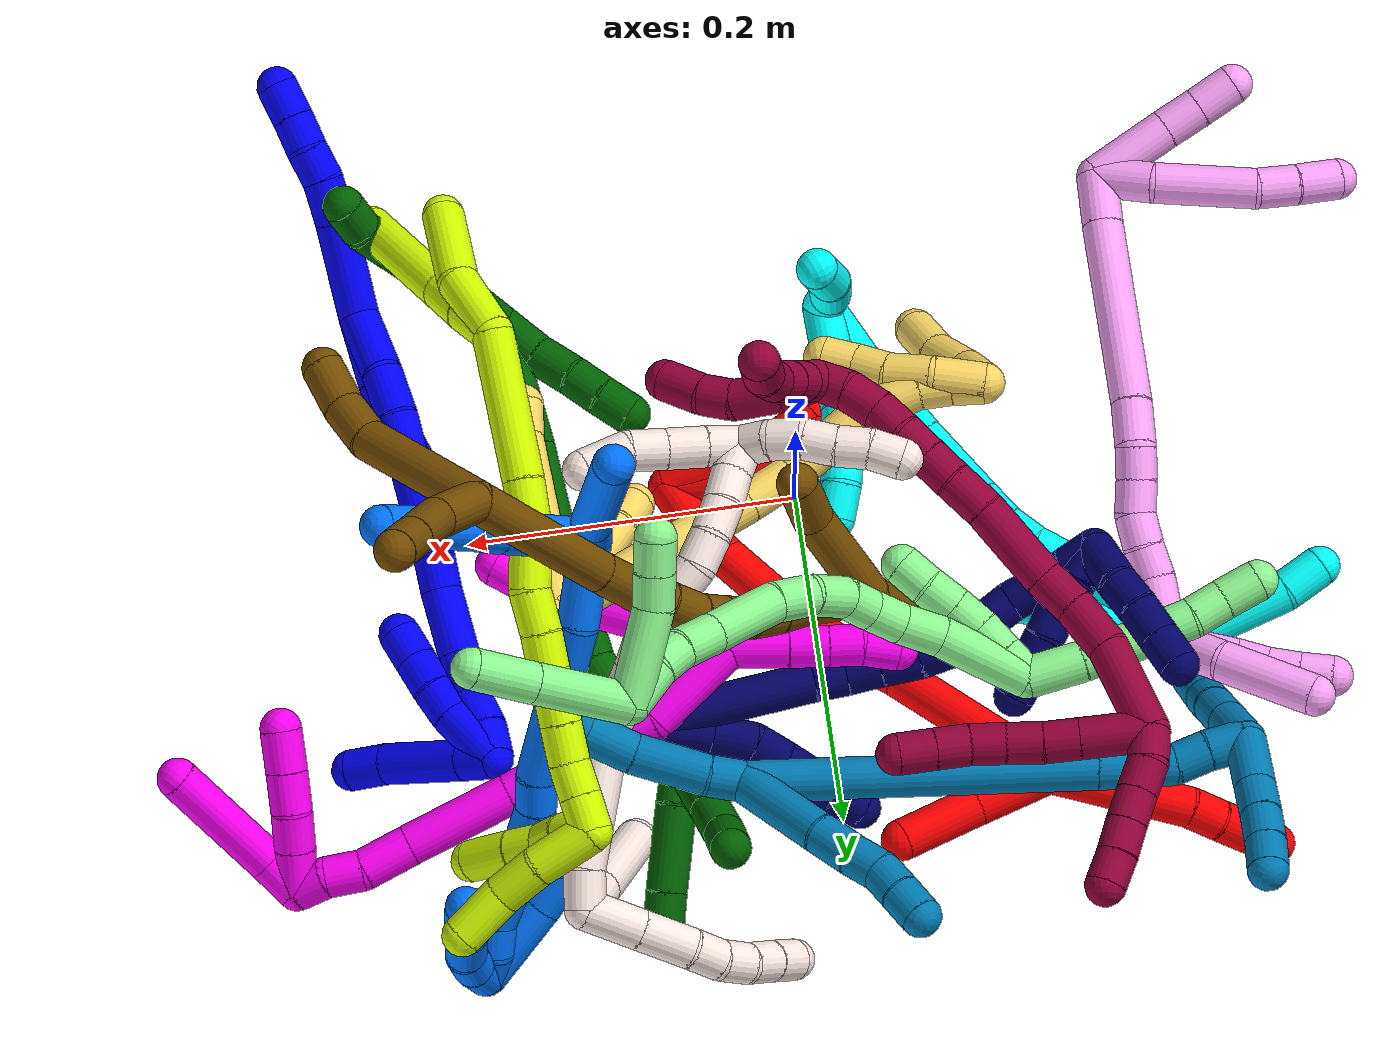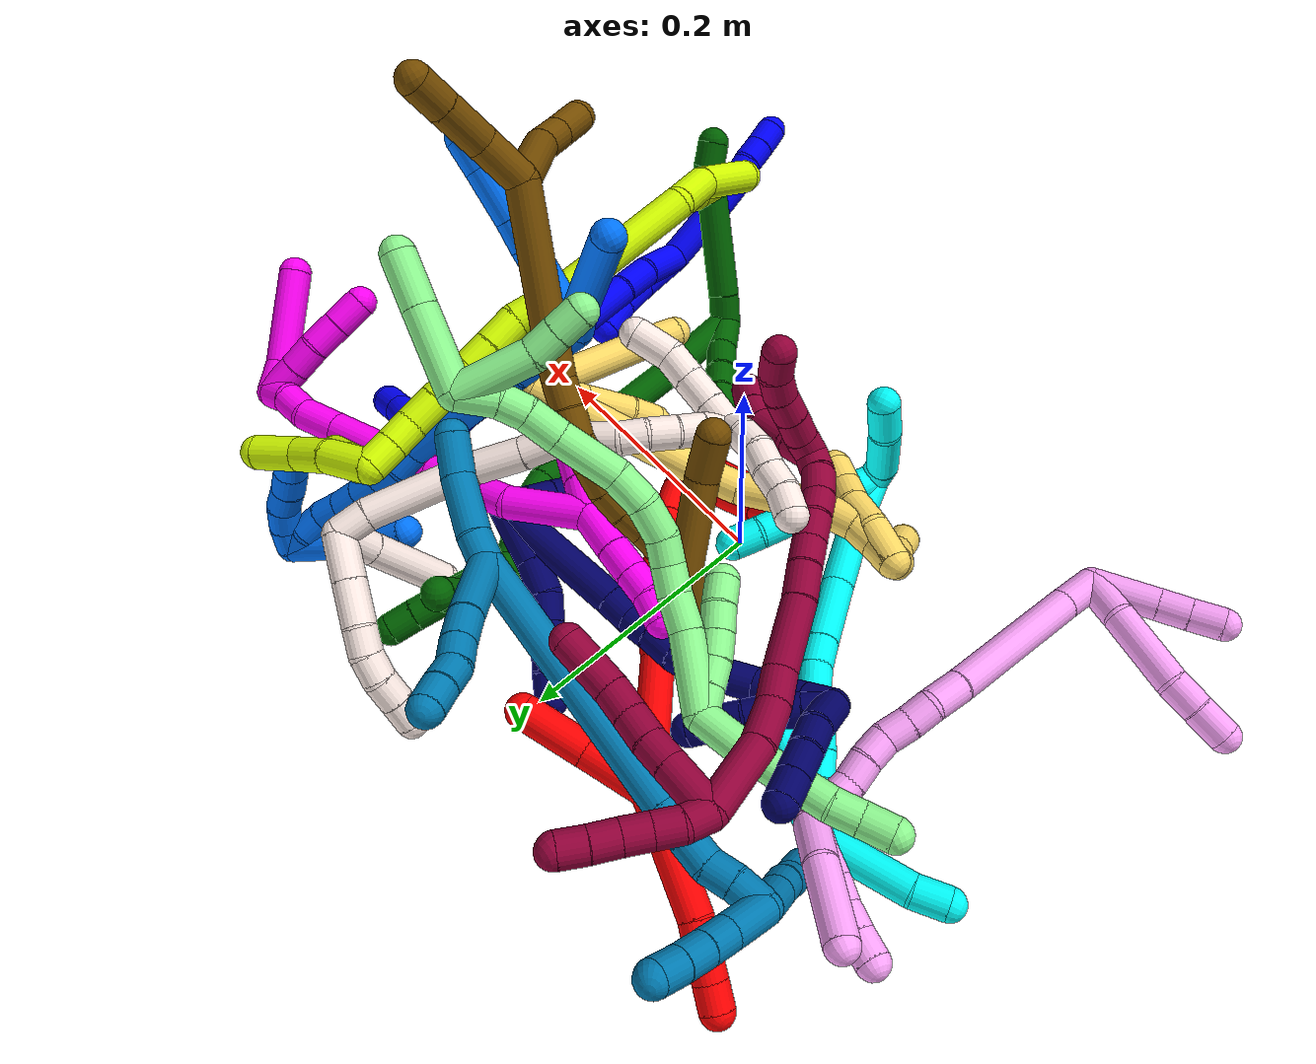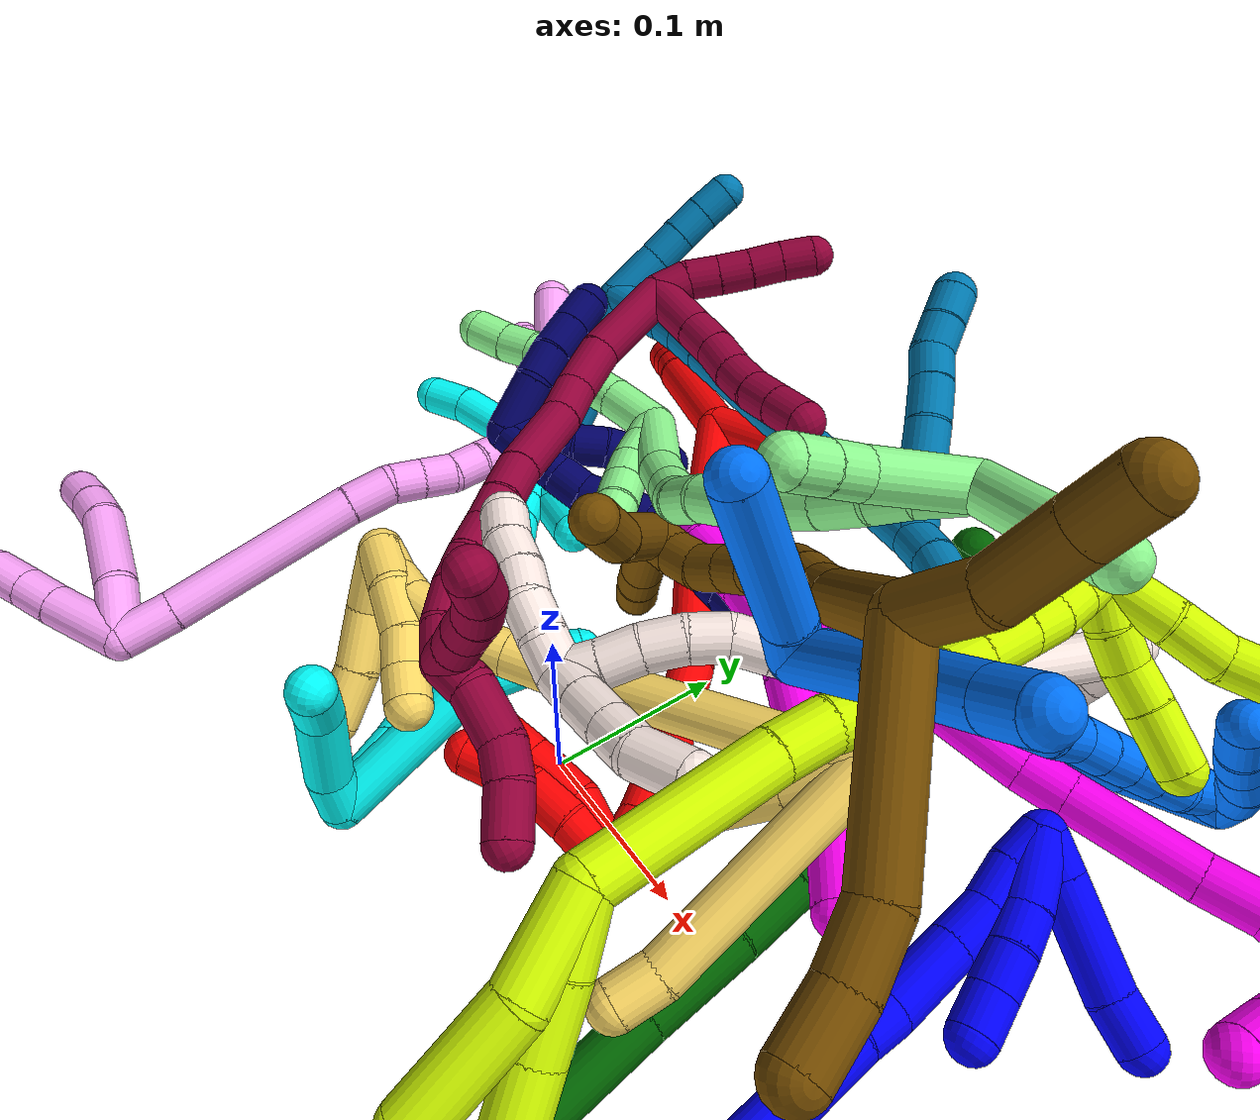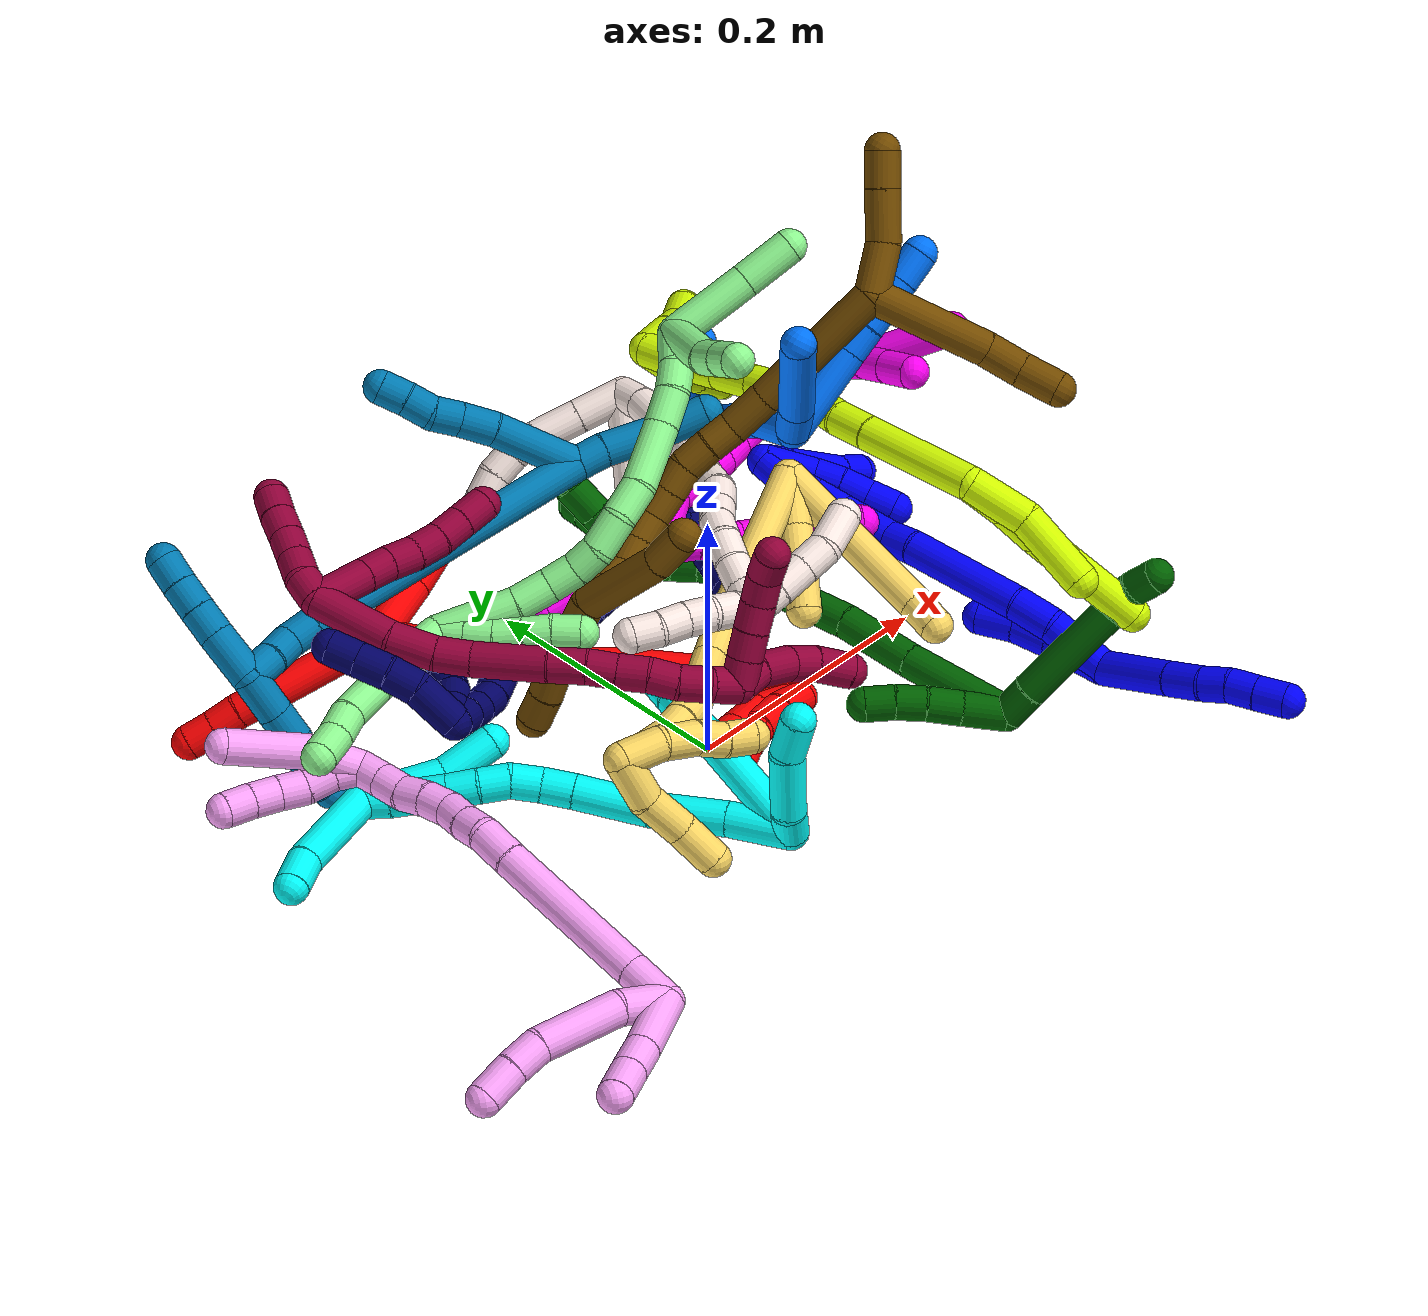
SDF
<sdf version="1.7">
 <world name="default">
  <plugin name="TubeGeneratorPlugin" filename="libtube_generator_plugin.so"/>
  <model name="photoneo_s_sensor">
   <static>1</static>
   <pose>0 0 2 1.57079 1.57079 3.14159</pose>
   <link name="link">
    <inertial><mass>0.1</mass></inertial>
    <sensor name="sensor" type="depth">
     <update_rate>30</update_rate>
     <camera>
      <horizontal_fov>1.22</horizontal_fov>
      <image><width>1920</width><height>1200</height><format>B8G8R8</format></image>
      <clip><near>0.1</near><far>4</far></clip>
      <depth_camera><output>points</output></depth_camera>
     </camera>
     <plugin name="camera_plugin" filename="libgazebo_ros_depth_camera.so">
      <baseline>0.2</baseline>
      <alwaysOn>1</alwaysOn>
      <updateRate>0.0</updateRate>
      <cameraName>camera_ir</cameraName>
      <imageTopicName>/camera/color/image_raw</imageTopicName>
      <cameraInfoTopicName>/camera/color/camera_info</cameraInfoTopicName>
      <depthImageTopicName>/camera/depth/image_raw</depthImageTopicName>
      <depthImageCameraInfoTopicName>/camera/depth/camera_info</depthImageCameraInfoTopicName>
      <pointCloudTopicName>/camera/depth/points</pointCloudTopicName>
      <frameName>fr_optical</frameName>
      <pointCloudCutoff>0.1</pointCloudCutoff>
      <pointCloudCutoffMax>2.0</pointCloudCutoffMax>
      <distortionK1>0</distortionK1>
      <distortionK2>0</distortionK2>
      <distortionK3>0</distortionK3>
      <distortionT1>0</distortionT1>
      <distortionT2>0</distortionT2>
      <CxPrime>0</CxPrime>
      <Cx>0</Cx>
      <Cy>0</Cy>
      <focalLength>0</focalLength>
      <hackBaseline>0</hackBaseline>
     </plugin>
    </sensor>
   </link>
  </model>
  <gravity>0 0 -9.8</gravity>
  <magnetic_field>6e-06 2.3e-05 -4.2e-05</magnetic_field>
  <atmosphere type="adiabatic"/>
  <physics name="default_physics" default="0" type="ode">
   <max_step_size>0.003</max_step_size>
   <real_time_factor>1</real_time_factor>
   <real_time_update_rate>1000</real_time_update_rate>
   <max_contacts>10000</max_contacts>
   <ode>
    <solver>
     <type>quick</type>
     <iters>100</iters>
     <sor>1.3</sor>
     <use_dynamic_moi_rescaling>0</use_dynamic_moi_rescaling>
    </solver>
    <constraints>
     <contact_max_correcting_vel>0</contact_max_correcting_vel>
     <contact_surface_layer>0.001</contact_surface_layer>
     <cfm>0</cfm>
     <erp>0.2</erp>
    </constraints>
   </ode>
  </physics>
  <scene><ambient>0.4 0.4 0.4 1</ambient><background>0.7 0.7 0.7 1</background><shadows>0</shadows></scene>
  <audio><device>default</device></audio>
  <spherical_coordinates>
   <surface_model>EARTH_WGS84</surface_model>
   <latitude_deg>0</latitude_deg>
   <longitude_deg>0</longitude_deg>
   <elevation>0</elevation>
   <heading_deg>0</heading_deg>
  </spherical_coordinates>
  <model name="bin">
   <static>1</static>
   <link name="bottom">
    <collision name="collision-bottom">
     <pose>0 0 -0.01 0 -0 0</pose>
     <geometry><box><size>0.8 0.6 0.02</size></box></geometry>
     <surface>
      <friction><ode><mu>100</mu><mu2>100</mu2></ode></friction>
      <contact><collide_bitmask>65535</collide_bitmask></contact>
     </surface>
    </collision>
   </link>
   <link name="west_wall">
    <collision name="collision-west_wall">
     <pose>-0.41 0 0.1 0 -0 0</pose>
     <geometry><box><size>0.02 0.6 0.2</size></box></geometry>
     <surface>
      <friction><ode><mu>100</mu><mu2>100</mu2></ode></friction>
      <contact><collide_bitmask>65535</collide_bitmask></contact>
     </surface>
    </collision>
   </link>
   <link name="east_wall">
    <collision name="collision-east_wall">
     <pose>0.41 0 0.1 0 -0 0</pose>
     <geometry><box><size>0.02 0.6 0.2</size></box></geometry>
     <surface>
      <friction><ode><mu>100</mu><mu2>100</mu2></ode></friction>
      <contact><collide_bitmask>65535</collide_bitmask></contact>
     </surface>
    </collision>
   </link>
   <link name="south_wall">
    <collision name="collision-south_wall">
     <pose>0 -0.31 0.1 0 -0 0</pose>
     <geometry><box><size>0.8 0.02 0.2</size></box></geometry>
     <surface>
      <friction><ode><mu>100</mu><mu2>100</mu2></ode></friction>
      <contact><collide_bitmask>65535</collide_bitmask></contact>
     </surface>
    </collision>
   </link>
   <link name="north_wall">
    <collision name="collision-north_wall">
     <pose>0 0.31 0.1 0 -0 0</pose>
     <geometry><box><size>0.8 0.02 0.2</size></box></geometry>
     <surface>
      <friction><ode><mu>100</mu><mu2>100</mu2></ode></friction>
      <contact><collide_bitmask>65535</collide_bitmask></contact>
     </surface>
    </collision>
   </link>
  </model>
  <model name="1">
   <static>0</static>
   <link name="1">
    <collision name="collision-cylinder-e_1_2_8">
     <pose>-0.002256 -0.019876 0.022284 0.72834 -0.075423 -0.028761</pose>
     <geometry><cylinder><radius>0.0125</radius><length>0.059891</length></cylinder></geometry>
     <surface>
      <friction><ode><mu>1.16</mu><mu2>1.16</mu2><slip1>0</slip1><slip2>0</slip2></ode></friction>
      <contact><ode><kp>1e+06</kp><kd>1</kd><max_vel>0</max_vel><min_depth>0.001</min_depth></ode></contact>
     </surface>
    </collision>
    <visual name="visual-cylinder-e_1_2_8">
     <pose>-0.002256 -0.019876 0.022284 0.72834 -0.075423 -0.028761</pose>
     <geometry><cylinder><radius>0.0125</radius><length>0.059891</length></cylinder></geometry>
     <material><ambient>0 0 1 1</ambient></material>
    </visual>
    <collision name="collision-cylinder-e_2_8_9">
     <pose>-0.006102 -0.048241 0.055035 0.681427 -0.117347 -0.041646</pose>
     <geometry><cylinder><radius>0.0125</radius><length>0.02714</length></cylinder></geometry>
     <surface>
      <friction><ode><mu>1.16</mu><mu2>1.16</mu2><slip1>0</slip1><slip2>0</slip2></ode></friction>
      <contact><ode><kp>1e+06</kp><kd>1</kd><max_vel>0</max_vel><min_depth>0.001</min_depth></ode></contact>
     </surface>
    </collision>
    <visual name="visual-cylinder-e_2_8_9">
     <pose>-0.006102 -0.048241 0.055035 0.681427 -0.117347 -0.041646</pose>
     <geometry><cylinder><radius>0.0125</radius><length>0.02714</length></cylinder></geometry>
     <material><ambient>0 0 1 1</ambient></material>
    </visual>
    <collision name="collision-cylinder-e_3_9_10">
     <pose>-0.010445 -0.062012 0.073838 0.564815 -0.272176 -0.079425</pose>
     <geometry><cylinder><radius>0.0125</radius><length>0.020492</length></cylinder></geometry>
     <surface>
      <friction><ode><mu>1.16</mu><mu2>1.16</mu2><slip1>0</slip1><slip2>0</slip2></ode></friction>
      <contact><ode><kp>1e+06</kp><kd>1</kd><max_vel>0</max_vel><min_depth>0.001</min_depth></ode></contact>
     </surface>
    </collision>
    <visual name="visual-cylinder-e_3_9_10">
     <pose>-0.010445 -0.062012 0.073838 0.564815 -0.272176 -0.079425</pose>
     <geometry><cylinder><radius>0.0125</radius><length>0.020492</length></cylinder></geometry>
     <material><ambient>0 0 1 1</ambient></material>
    </visual>
    <collision name="collision-cylinder-e_4_10_11">
     <pose>-0.014532 -0.07132 0.091398 0.411562 -0.131708 -0.02753</pose>
     <geometry><cylinder><radius>0.0125</radius><length>0.020303</length></cylinder></geometry>
     <surface>
      <friction><ode><mu>1.16</mu><mu2>1.16</mu2><slip1>0</slip1><slip2>0</slip2></ode></friction>
      <contact><ode><kp>1e+06</kp><kd>1</kd><max_vel>0</max_vel><min_depth>0.001</min_depth></ode></contact>
     </surface>
    </collision>
    <visual name="visual-cylinder-e_4_10_11">
     <pose>-0.014532 -0.07132 0.091398 0.411562 -0.131708 -0.02753</pose>
     <geometry><cylinder><radius>0.0125</radius><length>0.020303</length></cylinder></geometry>
     <material><ambient>0 0 1 1</ambient></material>
    </visual>
    <collision name="collision-cylinder-e_5_11_6">
     <pose>-0.017715 -0.079479 0.110741 0.387665 -0.167578 -0.032969</pose>
     <geometry><cylinder><radius>0.0125</radius><length>0.022174</length></cylinder></geometry>
     <surface>
      <friction><ode><mu>1.16</mu><mu2>1.16</mu2><slip1>0</slip1><slip2>0</slip2></ode></friction>
      <contact><ode><kp>1e+06</kp><kd>1</kd><max_vel>0</max_vel><min_depth>0.001</min_depth></ode></contact>
     </surface>
    </collision>
    <visual name="visual-cylinder-e_5_11_6">
     <pose>-0.017715 -0.079479 0.110741 0.387665 -0.167578 -0.032969</pose>
     <geometry><cylinder><radius>0.0125</radius><length>0.022174</length></cylinder></geometry>
     <material><ambient>0 0 1 1</ambient></material>
    </visual>
    <collision name="collision-cylinder-e_1_2_12">
     <pose>-0.000899 0.007512 -0.020849 -2.79576 -0.040524 0.231012</pose>
     <geometry><cylinder><radius>0.0125</radius><length>0.044358</length></cylinder></geometry>
     <surface>
      <friction><ode><mu>1.16</mu><mu2>1.16</mu2><slip1>0</slip1><slip2>0</slip2></ode></friction>
      <contact><ode><kp>1e+06</kp><kd>1</kd><max_vel>0</max_vel><min_depth>0.001</min_depth></ode></contact>
     </surface>
    </collision>
    <visual name="visual-cylinder-e_1_2_12">
     <pose>-0.000899 0.007512 -0.020849 -2.79576 -0.040524 0.231012</pose>
     <geometry><cylinder><radius>0.0125</radius><length>0.044358</length></cylinder></geometry>
     <material><ambient>0 0 1 1</ambient></material>
    </visual>
    <collision name="collision-cylinder-e_2_12_13">
     <pose>-0.001491 0.019186 -0.054912 -2.83652 0.022074 -0.143347</pose>
     <geometry><cylinder><radius>0.0125</radius><length>0.027716</length></cylinder></geometry>
     <surface>
      <friction><ode><mu>1.16</mu><mu2>1.16</mu2><slip1>0</slip1><slip2>0</slip2></ode></friction>
      <contact><ode><kp>1e+06</kp><kd>1</kd><max_vel>0</max_vel><min_depth>0.001</min_depth></ode></contact>
     </surface>
    </collision>
    <visual name="visual-cylinder-e_2_12_13">
     <pose>-0.001491 0.019186 -0.054912 -2.83652 0.022074 -0.143347</pose>
     <geometry><cylinder><radius>0.0125</radius><length>0.027716</length></cylinder></geometry>
     <material><ambient>0 0 1 1</ambient></material>
    </visual>
    <collision name="collision-cylinder-e_3_13_5">
     <pose>0.00154 0.028139 -0.080956 -2.78411 0.196461 -0.998698</pose>
     <geometry><cylinder><radius>0.0125</radius><length>0.027926</length></cylinder></geometry>
     <surface>
      <friction><ode><mu>1.16</mu><mu2>1.16</mu2><slip1>0</slip1><slip2>0</slip2></ode></friction>
      <contact><ode><kp>1e+06</kp><kd>1</kd><max_vel>0</max_vel><min_depth>0.001</min_depth></ode></contact>
     </surface>
    </collision>
    <visual name="visual-cylinder-e_3_13_5">
     <pose>0.00154 0.028139 -0.080956 -2.78411 0.196461 -0.998698</pose>
     <geometry><cylinder><radius>0.0125</radius><length>0.027926</length></cylinder></geometry>
     <material><ambient>0 0 1 1</ambient></material>
    </visual>
    <collision name="collision-cylinder-e_1_2_14">
     <pose>-0.002917 -0.0013 -0.023127 3.08546 -0.125281 -2.29986</pose>
     <geometry><cylinder><radius>0.0125</radius><length>0.046692</length></cylinder></geometry>
     <surface>
      <friction><ode><mu>1.16</mu><mu2>1.16</mu2><slip1>0</slip1><slip2>0</slip2></ode></friction>
      <contact><ode><kp>1e+06</kp><kd>1</kd><max_vel>0</max_vel><min_depth>0.001</min_depth></ode></contact>
     </surface>
    </collision>
    <visual name="visual-cylinder-e_1_2_14">
     <pose>-0.002917 -0.0013 -0.023127 3.08546 -0.125281 -2.29986</pose>
     <geometry><cylinder><radius>0.0125</radius><length>0.046692</length></cylinder></geometry>
     <material><ambient>0 0 1 1</ambient></material>
    </visual>
    <collision name="collision-cylinder-e_2_14_15">
     <pose>-0.00678 0.00022 -0.061044 -2.95328 -0.062727 0.641494</pose>
     <geometry><cylinder><radius>0.0125</radius><length>0.030174</length></cylinder></geometry>
     <surface>
      <friction><ode><mu>1.16</mu><mu2>1.16</mu2><slip1>0</slip1><slip2>0</slip2></ode></friction>
      <contact><ode><kp>1e+06</kp><kd>1</kd><max_vel>0</max_vel><min_depth>0.001</min_depth></ode></contact>
     </surface>
    </collision>
    <visual name="visual-cylinder-e_2_14_15">
     <pose>-0.00678 0.00022 -0.061044 -2.95328 -0.062727 0.641494</pose>
     <geometry><cylinder><radius>0.0125</radius><length>0.030174</length></cylinder></geometry>
     <material><ambient>0 0 1 1</ambient></material>
    </visual>
    <collision name="collision-cylinder-e_3_15_16">
     <pose>-0.01091 0.018577 -0.117913 -2.78783 -0.070877 0.391607</pose>
     <geometry><cylinder><radius>0.0125</radius><length>0.089936</length></cylinder></geometry>
     <surface>
      <friction><ode><mu>1.16</mu><mu2>1.16</mu2><slip1>0</slip1><slip2>0</slip2></ode></friction>
      <contact><ode><kp>1e+06</kp><kd>1</kd><max_vel>0</max_vel><min_depth>0.001</min_depth></ode></contact>
     </surface>
    </collision>
    <visual name="visual-cylinder-e_3_15_16">
     <pose>-0.01091 0.018577 -0.117913 -2.78783 -0.070877 0.391607</pose>
     <geometry><cylinder><radius>0.0125</radius><length>0.089936</length></cylinder></geometry>
     <material><ambient>0 0 1 1</ambient></material>
    </visual>
    <collision name="collision-cylinder-e_4_16_17">
     <pose>-0.01452 0.039585 -0.169158 -2.6037 -0.039769 0.144056</pose>
     <geometry><cylinder><radius>0.0125</radius><length>0.021366</length></cylinder></geometry>
     <surface>
      <friction><ode><mu>1.16</mu><mu2>1.16</mu2><slip1>0</slip1><slip2>0</slip2></ode></friction>
      <contact><ode><kp>1e+06</kp><kd>1</kd><max_vel>0</max_vel><min_depth>0.001</min_depth></ode></contact>
     </surface>
    </collision>
    <visual name="visual-cylinder-e_4_16_17">
     <pose>-0.01452 0.039585 -0.169158 -2.6037 -0.039769 0.144056</pose>
     <geometry><cylinder><radius>0.0125</radius><length>0.021366</length></cylinder></geometry>
     <material><ambient>0 0 1 1</ambient></material>
    </visual>
    <collision name="collision-cylinder-e_5_17_18">
     <pose>-0.016433 0.051611 -0.198127 -2.82183 -0.071235 0.43494</pose>
     <geometry><cylinder><radius>0.0125</radius><length>0.041826</length></cylinder></geometry>
     <surface>
      <friction><ode><mu>1.16</mu><mu2>1.16</mu2><slip1>0</slip1><slip2>0</slip2></ode></friction>
      <contact><ode><kp>1e+06</kp><kd>1</kd><max_vel>0</max_vel><min_depth>0.001</min_depth></ode></contact>
     </surface>
    </collision>
    <visual name="visual-cylinder-e_5_17_18">
     <pose>-0.016433 0.051611 -0.198127 -2.82183 -0.071235 0.43494</pose>
     <geometry><cylinder><radius>0.0125</radius><length>0.041826</length></cylinder></geometry>
     <material><ambient>0 0 1 1</ambient></material>
    </visual>
    <collision name="collision-cylinder-e_6_18_19">
     <pose>-0.019054 0.061893 -0.229914 -2.8403 -0.090026 0.576909</pose>
     <geometry><cylinder><radius>0.0125</radius><length>0.025201</length></cylinder></geometry>
     <surface>
      <friction><ode><mu>1.16</mu><mu2>1.16</mu2><slip1>0</slip1><slip2>0</slip2></ode></friction>
      <contact><ode><kp>1e+06</kp><kd>1</kd><max_vel>0</max_vel><min_depth>0.001</min_depth></ode></contact>
     </surface>
    </collision>
    <visual name="visual-cylinder-e_6_18_19">
     <pose>-0.019054 0.061893 -0.229914 -2.8403 -0.090026 0.576909</pose>
     <geometry><cylinder><radius>0.0125</radius><length>0.025201</length></cylinder></geometry>
     <material><ambient>0 0 1 1</ambient></material>
    </visual>
    <collision name="collision-cylinder-e_7_19_20">
     <pose>-0.019854 0.067078 -0.253629 -3.01768 0.028155 -0.446325</pose>
     <geometry><cylinder><radius>0.0125</radius><length>0.023651</length></cylinder></geometry>
     <surface>
      <friction><ode><mu>1.16</mu><mu2>1.16</mu2><slip1>0</slip1><slip2>0</slip2></ode></friction>
      <contact><ode><kp>1e+06</kp><kd>1</kd><max_vel>0</max_vel><min_depth>0.001</min_depth></ode></contact>
     </surface>
    </collision>
    <visual name="visual-cylinder-e_7_19_20">
     <pose>-0.019854 0.067078 -0.253629 -3.01768 0.028155 -0.446325</pose>
     <geometry><cylinder><radius>0.0125</radius><length>0.023651</length></cylinder></geometry>
     <material><ambient>0 0 1 1</ambient></material>
    </visual>
    <collision name="collision-cylinder-e_8_20_1">
     <pose>-0.021598 0.069822 -0.27565 -3.01753 -0.197643 2.02229</pose>
     <geometry><cylinder><radius>0.0125</radius><length>0.021154</length></cylinder></geometry>
     <surface>
      <friction><ode><mu>1.16</mu><mu2>1.16</mu2><slip1>0</slip1><slip2>0</slip2></ode></friction>
      <contact><ode><kp>1e+06</kp><kd>1</kd><max_vel>0</max_vel><min_depth>0.001</min_depth></ode></contact>
     </surface>
    </collision>
    <visual name="visual-cylinder-e_8_20_1">
     <pose>-0.021598 0.069822 -0.27565 -3.01753 -0.197643 2.02229</pose>
     <geometry><cylinder><radius>0.0125</radius><length>0.021154</length></cylinder></geometry>
     <material><ambient>0 0 1 1</ambient></material>
    </visual>
    <collision name="collision-cylinder-e_1_1_21">
     <pose>-0.029117 0.077612 -0.280023 -0.832727 -0.554026 0.250153</pose>
     <geometry><cylinder><radius>0.0125</radius><length>0.020686</length></cylinder></geometry>
     <surface>
      <friction><ode><mu>1.16</mu><mu2>1.16</mu2><slip1>0</slip1><slip2>0</slip2></ode></friction>
      <contact><ode><kp>1e+06</kp><kd>1</kd><max_vel>0</max_vel><min_depth>0.001</min_depth></ode></contact>
     </surface>
    </collision>
    <visual name="visual-cylinder-e_1_1_21">
     <pose>-0.029117 0.077612 -0.280023 -0.832727 -0.554026 0.250153</pose>
     <geometry><cylinder><radius>0.0125</radius><length>0.020686</length></cylinder></geometry>
     <material><ambient>0 0 1 1</ambient></material>
    </visual>
    <collision name="collision-cylinder-e_2_21_22">
     <pose>-0.049185 0.10114 -0.258066 -0.8151 -0.558901 0.246517</pose>
     <geometry><cylinder><radius>0.0125</radius><length>0.055168</length></cylinder></geometry>
     <surface>
      <friction><ode><mu>1.16</mu><mu2>1.16</mu2><slip1>0</slip1><slip2>0</slip2></ode></friction>
      <contact><ode><kp>1e+06</kp><kd>1</kd><max_vel>0</max_vel><min_depth>0.001</min_depth></ode></contact>
     </surface>
    </collision>
    <visual name="visual-cylinder-e_2_21_22">
     <pose>-0.049185 0.10114 -0.258066 -0.8151 -0.558901 0.246517</pose>
     <geometry><cylinder><radius>0.0125</radius><length>0.055168</length></cylinder></geometry>
     <material><ambient>0 0 1 1</ambient></material>
    </visual>
    <collision name="collision-cylinder-e_3_22_4">
     <pose>-0.071403 0.125702 -0.236437 -0.932875 -0.679994 0.352508</pose>
     <geometry><cylinder><radius>0.0125</radius><length>0.024146</length></cylinder></geometry>
     <surface>
      <friction><ode><mu>1.16</mu><mu2>1.16</mu2><slip1>0</slip1><slip2>0</slip2></ode></friction>
      <contact><ode><kp>1e+06</kp><kd>1</kd><max_vel>0</max_vel><min_depth>0.001</min_depth></ode></contact>
     </surface>
    </collision>
    <visual name="visual-cylinder-e_3_22_4">
     <pose>-0.071403 0.125702 -0.236437 -0.932875 -0.679994 0.352508</pose>
     <geometry><cylinder><radius>0.0125</radius><length>0.024146</length></cylinder></geometry>
     <material><ambient>0 0 1 1</ambient></material>
    </visual>
    <collision name="collision-cylinder-e_1_1_23">
     <pose>-0.029302 0.070851 -0.267972 0.014174 -0.303464 -0.002167</pose>
     <geometry><cylinder><radius>0.0125</radius><length>0.037662</length></cylinder></geometry>
     <surface>
      <friction><ode><mu>1.16</mu><mu2>1.16</mu2><slip1>0</slip1><slip2>0</slip2></ode></friction>
      <contact><ode><kp>1e+06</kp><kd>1</kd><max_vel>0</max_vel><min_depth>0.001</min_depth></ode></contact>
     </surface>
    </collision>
    <visual name="visual-cylinder-e_1_1_23">
     <pose>-0.029302 0.070851 -0.267972 0.014174 -0.303464 -0.002167</pose>
     <geometry><cylinder><radius>0.0125</radius><length>0.037662</length></cylinder></geometry>
     <material><ambient>0 0 1 1</ambient></material>
    </visual>
    <collision name="collision-cylinder-e_2_23_24">
     <pose>-0.03696 0.069368 -0.240155 0.124103 -0.201799 -0.012581</pose>
     <geometry><cylinder><radius>0.0125</radius><length>0.020261</length></cylinder></geometry>
     <surface>
      <friction><ode><mu>1.16</mu><mu2>1.16</mu2><slip1>0</slip1><slip2>0</slip2></ode></friction>
      <contact><ode><kp>1e+06</kp><kd>1</kd><max_vel>0</max_vel><min_depth>0.001</min_depth></ode></contact>
     </surface>
    </collision>
    <visual name="visual-cylinder-e_2_23_24">
     <pose>-0.03696 0.069368 -0.240155 0.124103 -0.201799 -0.012581</pose>
     <geometry><cylinder><radius>0.0125</radius><length>0.020261</length></cylinder></geometry>
     <material><ambient>0 0 1 1</ambient></material>
    </visual>
    <collision name="collision-cylinder-e_3_24_25">
     <pose>-0.040015 0.067461 -0.219834 0.064631 -0.097307 -0.003148</pose>
     <geometry><cylinder><radius>0.0125</radius><length>0.021089</length></cylinder></geometry>
     <surface>
      <friction><ode><mu>1.16</mu><mu2>1.16</mu2><slip1>0</slip1><slip2>0</slip2></ode></friction>
      <contact><ode><kp>1e+06</kp><kd>1</kd><max_vel>0</max_vel><min_depth>0.001</min_depth></ode></contact>
     </surface>
    </collision>
    <visual name="visual-cylinder-e_3_24_25">
     <pose>-0.040015 0.067461 -0.219834 0.064631 -0.097307 -0.003148</pose>
     <geometry><cylinder><radius>0.0125</radius><length>0.021089</length></cylinder></geometry>
     <material><ambient>0 0 1 1</ambient></material>
    </visual>
    <collision name="collision-cylinder-e_4_25_3">
     <pose>-0.042226 0.06581 -0.19898 0.093519 -0.113276 -0.005306</pose>
     <geometry><cylinder><radius>0.0125</radius><length>0.020988</length></cylinder></geometry>
     <surface>
      <friction><ode><mu>1.16</mu><mu2>1.16</mu2><slip1>0</slip1><slip2>0</slip2></ode></friction>
      <contact><ode><kp>1e+06</kp><kd>1</kd><max_vel>0</max_vel><min_depth>0.001</min_depth></ode></contact>
     </surface>
    </collision>
    <visual name="visual-cylinder-e_4_25_3">
     <pose>-0.042226 0.06581 -0.19898 0.093519 -0.113276 -0.005306</pose>
     <geometry><cylinder><radius>0.0125</radius><length>0.020988</length></cylinder></geometry>
     <material><ambient>0 0 1 1</ambient></material>
    </visual>
    <collision name="collision-sphere-3">
     <pose>-0.043412 0.064836 -0.188599 0 -0 0</pose>
     <geometry><sphere><radius>0.0125</radius></sphere></geometry>
     <surface>
      <friction><ode><mu>1.16</mu><mu2>1.16</mu2><slip1>0</slip1><slip2>0</slip2></ode></friction>
      <contact><ode><kp>1e+06</kp><kd>1</kd><max_vel>0</max_vel><min_depth>0.001</min_depth></ode></contact>
     </surface>
    </collision>
    <visual name="visual-sphere-3">
     <pose>-0.043412 0.064836 -0.188599 0 -0 0</pose>
     <geometry><sphere><radius>0.0125</radius></sphere></geometry>
     <material><ambient>0 0 1 1</ambient></material>
    </visual>
    <collision name="collision-sphere-25">
     <pose>-0.041039 0.066783 -0.209361 0 -0 0</pose>
     <geometry><sphere><radius>0.0125</radius></sphere></geometry>
     <surface>
      <friction><ode><mu>1.16</mu><mu2>1.16</mu2><slip1>0</slip1><slip2>0</slip2></ode></friction>
      <contact><ode><kp>1e+06</kp><kd>1</kd><max_vel>0</max_vel><min_depth>0.001</min_depth></ode></contact>
     </surface>
    </collision>
    <visual name="visual-sphere-25">
     <pose>-0.041039 0.066783 -0.209361 0 -0 0</pose>
     <geometry><sphere><radius>0.0125</radius></sphere></geometry>
     <material><ambient>0 0 1 1</ambient></material>
    </visual>
    <collision name="collision-sphere-24">
     <pose>-0.038991 0.068139 -0.230306 0 -0 0</pose>
     <geometry><sphere><radius>0.0125</radius></sphere></geometry>
     <surface>
      <friction><ode><mu>1.16</mu><mu2>1.16</mu2><slip1>0</slip1><slip2>0</slip2></ode></friction>
      <contact><ode><kp>1e+06</kp><kd>1</kd><max_vel>0</max_vel><min_depth>0.001</min_depth></ode></contact>
     </surface>
    </collision>
    <visual name="visual-sphere-24">
     <pose>-0.038991 0.068139 -0.230306 0 -0 0</pose>
     <geometry><sphere><radius>0.0125</radius></sphere></geometry>
     <material><ambient>0 0 1 1</ambient></material>
    </visual>
    <collision name="collision-sphere-23">
     <pose>-0.03493 0.070596 -0.250004 0 -0 0</pose>
     <geometry><sphere><radius>0.0125</radius></sphere></geometry>
     <surface>
      <friction><ode><mu>1.16</mu><mu2>1.16</mu2><slip1>0</slip1><slip2>0</slip2></ode></friction>
      <contact><ode><kp>1e+06</kp><kd>1</kd><max_vel>0</max_vel><min_depth>0.001</min_depth></ode></contact>
     </surface>
    </collision>
    <visual name="visual-sphere-23">
     <pose>-0.03493 0.070596 -0.250004 0 -0 0</pose>
     <geometry><sphere><radius>0.0125</radius></sphere></geometry>
     <material><ambient>0 0 1 1</ambient></material>
    </visual>
    <collision name="collision-sphere-4">
     <pose>-0.078994 0.133244 -0.230846 0 -0 0</pose>
     <geometry><sphere><radius>0.0125</radius></sphere></geometry>
     <surface>
      <friction><ode><mu>1.16</mu><mu2>1.16</mu2><slip1>0</slip1><slip2>0</slip2></ode></friction>
      <contact><ode><kp>1e+06</kp><kd>1</kd><max_vel>0</max_vel><min_depth>0.001</min_depth></ode></contact>
     </surface>
    </collision>
    <visual name="visual-sphere-4">
     <pose>-0.078994 0.133244 -0.230846 0 -0 0</pose>
     <geometry><sphere><radius>0.0125</radius></sphere></geometry>
     <material><ambient>0 0 1 1</ambient></material>
    </visual>
    <collision name="collision-sphere-22">
     <pose>-0.063811 0.118161 -0.242028 0 -0 0</pose>
     <geometry><sphere><radius>0.0125</radius></sphere></geometry>
     <surface>
      <friction><ode><mu>1.16</mu><mu2>1.16</mu2><slip1>0</slip1><slip2>0</slip2></ode></friction>
      <contact><ode><kp>1e+06</kp><kd>1</kd><max_vel>0</max_vel><min_depth>0.001</min_depth></ode></contact>
     </surface>
    </collision>
    <visual name="visual-sphere-22">
     <pose>-0.063811 0.118161 -0.242028 0 -0 0</pose>
     <geometry><sphere><radius>0.0125</radius></sphere></geometry>
     <material><ambient>0 0 1 1</ambient></material>
    </visual>
    <collision name="collision-sphere-21">
     <pose>-0.034558 0.084119 -0.274105 0 -0 0</pose>
     <geometry><sphere><radius>0.0125</radius></sphere></geometry>
     <surface>
      <friction><ode><mu>1.16</mu><mu2>1.16</mu2><slip1>0</slip1><slip2>0</slip2></ode></friction>
      <contact><ode><kp>1e+06</kp><kd>1</kd><max_vel>0</max_vel><min_depth>0.001</min_depth></ode></contact>
     </surface>
    </collision>
    <visual name="visual-sphere-21">
     <pose>-0.034558 0.084119 -0.274105 0 -0 0</pose>
     <geometry><sphere><radius>0.0125</radius></sphere></geometry>
     <material><ambient>0 0 1 1</ambient></material>
    </visual>
    <collision name="collision-sphere-1">
     <pose>-0.023675 0.071105 -0.285941 0 -0 0</pose>
     <geometry><sphere><radius>0.0125</radius></sphere></geometry>
     <surface>
      <friction><ode><mu>1.16</mu><mu2>1.16</mu2><slip1>0</slip1><slip2>0</slip2></ode></friction>
      <contact><ode><kp>1e+06</kp><kd>1</kd><max_vel>0</max_vel><min_depth>0.001</min_depth></ode></contact>
     </surface>
    </collision>
    <visual name="visual-sphere-1">
     <pose>-0.023675 0.071105 -0.285941 0 -0 0</pose>
     <geometry><sphere><radius>0.0125</radius></sphere></geometry>
     <material><ambient>0 0 1 1</ambient></material>
    </visual>
    <collision name="collision-sphere-6">
     <pose>-0.019564 -0.083611 0.120862 0 -0 0</pose>
     <geometry><sphere><radius>0.0125</radius></sphere></geometry>
     <surface>
      <friction><ode><mu>1.16</mu><mu2>1.16</mu2><slip1>0</slip1><slip2>0</slip2></ode></friction>
      <contact><ode><kp>1e+06</kp><kd>1</kd><max_vel>0</max_vel><min_depth>0.001</min_depth></ode></contact>
     </surface>
    </collision>
    <visual name="visual-sphere-6">
     <pose>-0.019564 -0.083611 0.120862 0 -0 0</pose>
     <geometry><sphere><radius>0.0125</radius></sphere></geometry>
     <material><ambient>0 0 1 1</ambient></material>
    </visual>
    <collision name="collision-sphere-11">
     <pose>-0.015866 -0.075346 0.100621 0 -0 0</pose>
     <geometry><sphere><radius>0.0125</radius></sphere></geometry>
     <surface>
      <friction><ode><mu>1.16</mu><mu2>1.16</mu2><slip1>0</slip1><slip2>0</slip2></ode></friction>
      <contact><ode><kp>1e+06</kp><kd>1</kd><max_vel>0</max_vel><min_depth>0.001</min_depth></ode></contact>
     </surface>
    </collision>
    <visual name="visual-sphere-11">
     <pose>-0.015866 -0.075346 0.100621 0 -0 0</pose>
     <geometry><sphere><radius>0.0125</radius></sphere></geometry>
     <material><ambient>0 0 1 1</ambient></material>
    </visual>
    <collision name="collision-sphere-10">
     <pose>-0.013199 -0.067295 0.082174 0 -0 0</pose>
     <geometry><sphere><radius>0.0125</radius></sphere></geometry>
     <surface>
      <friction><ode><mu>1.16</mu><mu2>1.16</mu2><slip1>0</slip1><slip2>0</slip2></ode></friction>
      <contact><ode><kp>1e+06</kp><kd>1</kd><max_vel>0</max_vel><min_depth>0.001</min_depth></ode></contact>
     </surface>
    </collision>
    <visual name="visual-sphere-10">
     <pose>-0.013199 -0.067295 0.082174 0 -0 0</pose>
     <geometry><sphere><radius>0.0125</radius></sphere></geometry>
     <material><ambient>0 0 1 1</ambient></material>
    </visual>
    <collision name="collision-sphere-9">
     <pose>-0.00769 -0.05673 0.065502 0 -0 0</pose>
     <geometry><sphere><radius>0.0125</radius></sphere></geometry>
     <surface>
      <friction><ode><mu>1.16</mu><mu2>1.16</mu2><slip1>0</slip1><slip2>0</slip2></ode></friction>
      <contact><ode><kp>1e+06</kp><kd>1</kd><max_vel>0</max_vel><min_depth>0.001</min_depth></ode></contact>
     </surface>
    </collision>
    <visual name="visual-sphere-9">
     <pose>-0.00769 -0.05673 0.065502 0 -0 0</pose>
     <geometry><sphere><radius>0.0125</radius></sphere></geometry>
     <material><ambient>0 0 1 1</ambient></material>
    </visual>
    <collision name="collision-sphere-2">
     <geometry><sphere><radius>0.0125</radius></sphere></geometry>
     <surface>
      <friction><ode><mu>1.16</mu><mu2>1.16</mu2><slip1>0</slip1><slip2>0</slip2></ode></friction>
      <contact><ode><kp>1e+06</kp><kd>1</kd><max_vel>0</max_vel><min_depth>0.001</min_depth></ode></contact>
     </surface>
    </collision>
    <visual name="visual-sphere-2">
     <geometry><sphere><radius>0.0125</radius></sphere></geometry>
     <material><ambient>0 0 1 1</ambient></material>
    </visual>
    <collision name="collision-sphere-19">
     <pose>-0.020187 0.065617 -0.241899 0 -0 0</pose>
     <geometry><sphere><radius>0.0125</radius></sphere></geometry>
     <surface>
      <friction><ode><mu>1.16</mu><mu2>1.16</mu2><slip1>0</slip1><slip2>0</slip2></ode></friction>
      <contact><ode><kp>1e+06</kp><kd>1</kd><max_vel>0</max_vel><min_depth>0.001</min_depth></ode></contact>
     </surface>
    </collision>
    <visual name="visual-sphere-19">
     <pose>-0.020187 0.065617 -0.241899 0 -0 0</pose>
     <geometry><sphere><radius>0.0125</radius></sphere></geometry>
     <material><ambient>0 0 1 1</ambient></material>
    </visual>
    <collision name="collision-sphere-8">
     <pose>-0.004513 -0.039752 0.044568 0 -0 0</pose>
     <geometry><sphere><radius>0.0125</radius></sphere></geometry>
     <surface>
      <friction><ode><mu>1.16</mu><mu2>1.16</mu2><slip1>0</slip1><slip2>0</slip2></ode></friction>
      <contact><ode><kp>1e+06</kp><kd>1</kd><max_vel>0</max_vel><min_depth>0.001</min_depth></ode></contact>
     </surface>
    </collision>
    <visual name="visual-sphere-8">
     <pose>-0.004513 -0.039752 0.044568 0 -0 0</pose>
     <geometry><sphere><radius>0.0125</radius></sphere></geometry>
     <material><ambient>0 0 1 1</ambient></material>
    </visual>
    <collision name="collision-sphere-12">
     <pose>-0.001797 0.015024 -0.041697 0 -0 0</pose>
     <geometry><sphere><radius>0.0125</radius></sphere></geometry>
     <surface>
      <friction><ode><mu>1.16</mu><mu2>1.16</mu2><slip1>0</slip1><slip2>0</slip2></ode></friction>
      <contact><ode><kp>1e+06</kp><kd>1</kd><max_vel>0</max_vel><min_depth>0.001</min_depth></ode></contact>
     </surface>
    </collision>
    <visual name="visual-sphere-12">
     <pose>-0.001797 0.015024 -0.041697 0 -0 0</pose>
     <geometry><sphere><radius>0.0125</radius></sphere></geometry>
     <material><ambient>0 0 1 1</ambient></material>
    </visual>
    <collision name="collision-sphere-13">
     <pose>-0.001185 0.023347 -0.068127 0 -0 0</pose>
     <geometry><sphere><radius>0.0125</radius></sphere></geometry>
     <surface>
      <friction><ode><mu>1.16</mu><mu2>1.16</mu2><slip1>0</slip1><slip2>0</slip2></ode></friction>
      <contact><ode><kp>1e+06</kp><kd>1</kd><max_vel>0</max_vel><min_depth>0.001</min_depth></ode></contact>
     </surface>
    </collision>
    <visual name="visual-sphere-13">
     <pose>-0.001185 0.023347 -0.068127 0 -0 0</pose>
     <geometry><sphere><radius>0.0125</radius></sphere></geometry>
     <material><ambient>0 0 1 1</ambient></material>
    </visual>
    <collision name="collision-sphere-5">
     <pose>0.004266 0.032931 -0.093785 0 -0 0</pose>
     <geometry><sphere><radius>0.0125</radius></sphere></geometry>
     <surface>
      <friction><ode><mu>1.16</mu><mu2>1.16</mu2><slip1>0</slip1><slip2>0</slip2></ode></friction>
      <contact><ode><kp>1e+06</kp><kd>1</kd><max_vel>0</max_vel><min_depth>0.001</min_depth></ode></contact>
     </surface>
    </collision>
    <visual name="visual-sphere-5">
     <pose>0.004266 0.032931 -0.093785 0 -0 0</pose>
     <geometry><sphere><radius>0.0125</radius></sphere></geometry>
     <material><ambient>0 0 1 1</ambient></material>
    </visual>
    <collision name="collision-sphere-14">
     <pose>-0.005834 -0.002599 -0.046253 0 -0 0</pose>
     <geometry><sphere><radius>0.0125</radius></sphere></geometry>
     <surface>
      <friction><ode><mu>1.16</mu><mu2>1.16</mu2><slip1>0</slip1><slip2>0</slip2></ode></friction>
      <contact><ode><kp>1e+06</kp><kd>1</kd><max_vel>0</max_vel><min_depth>0.001</min_depth></ode></contact>
     </surface>
    </collision>
    <visual name="visual-sphere-14">
     <pose>-0.005834 -0.002599 -0.046253 0 -0 0</pose>
     <geometry><sphere><radius>0.0125</radius></sphere></geometry>
     <material><ambient>0 0 1 1</ambient></material>
    </visual>
    <collision name="collision-sphere-15">
     <pose>-0.007726 0.003038 -0.075836 0 -0 0</pose>
     <geometry><sphere><radius>0.0125</radius></sphere></geometry>
     <surface>
      <friction><ode><mu>1.16</mu><mu2>1.16</mu2><slip1>0</slip1><slip2>0</slip2></ode></friction>
      <contact><ode><kp>1e+06</kp><kd>1</kd><max_vel>0</max_vel><min_depth>0.001</min_depth></ode></contact>
     </surface>
    </collision>
    <visual name="visual-sphere-15">
     <pose>-0.007726 0.003038 -0.075836 0 -0 0</pose>
     <geometry><sphere><radius>0.0125</radius></sphere></geometry>
     <material><ambient>0 0 1 1</ambient></material>
    </visual>
    <collision name="collision-sphere-16">
     <pose>-0.014095 0.034116 -0.15999 0 -0 0</pose>
     <geometry><sphere><radius>0.0125</radius></sphere></geometry>
     <surface>
      <friction><ode><mu>1.16</mu><mu2>1.16</mu2><slip1>0</slip1><slip2>0</slip2></ode></friction>
      <contact><ode><kp>1e+06</kp><kd>1</kd><max_vel>0</max_vel><min_depth>0.001</min_depth></ode></contact>
     </surface>
    </collision>
    <visual name="visual-sphere-16">
     <pose>-0.014095 0.034116 -0.15999 0 -0 0</pose>
     <geometry><sphere><radius>0.0125</radius></sphere></geometry>
     <material><ambient>0 0 1 1</ambient></material>
    </visual>
    <collision name="collision-sphere-17">
     <pose>-0.014944 0.045054 -0.178325 0 -0 0</pose>
     <geometry><sphere><radius>0.0125</radius></sphere></geometry>
     <surface>
      <friction><ode><mu>1.16</mu><mu2>1.16</mu2><slip1>0</slip1><slip2>0</slip2></ode></friction>
      <contact><ode><kp>1e+06</kp><kd>1</kd><max_vel>0</max_vel><min_depth>0.001</min_depth></ode></contact>
     </surface>
    </collision>
    <visual name="visual-sphere-17">
     <pose>-0.014944 0.045054 -0.178325 0 -0 0</pose>
     <geometry><sphere><radius>0.0125</radius></sphere></geometry>
     <material><ambient>0 0 1 1</ambient></material>
    </visual>
    <collision name="collision-sphere-18">
     <pose>-0.017921 0.058168 -0.21793 0 -0 0</pose>
     <geometry><sphere><radius>0.0125</radius></sphere></geometry>
     <surface>
      <friction><ode><mu>1.16</mu><mu2>1.16</mu2><slip1>0</slip1><slip2>0</slip2></ode></friction>
      <contact><ode><kp>1e+06</kp><kd>1</kd><max_vel>0</max_vel><min_depth>0.001</min_depth></ode></contact>
     </surface>
    </collision>
    <visual name="visual-sphere-18">
     <pose>-0.017921 0.058168 -0.21793 0 -0 0</pose>
     <geometry><sphere><radius>0.0125</radius></sphere></geometry>
     <material><ambient>0 0 1 1</ambient></material>
    </visual>
    <collision name="collision-sphere-20">
     <pose>-0.019521 0.068539 -0.265359 0 -0 0</pose>
     <geometry><sphere><radius>0.0125</radius></sphere></geometry>
     <surface>
      <friction><ode><mu>1.16</mu><mu2>1.16</mu2><slip1>0</slip1><slip2>0</slip2></ode></friction>
      <contact><ode><kp>1e+06</kp><kd>1</kd><max_vel>0</max_vel><min_depth>0.001</min_depth></ode></contact>
     </surface>
    </collision>
    <visual name="visual-sphere-20">
     <pose>-0.019521 0.068539 -0.265359 0 -0 0</pose>
     <geometry><sphere><radius>0.0125</radius></sphere></geometry>
     <material><ambient>0 0 1 1</ambient></material>
    </visual>
    <inertial>
     <pose>-0.018119 0.028017 -0.118154 0 -0 0</pose>
     <mass>0.75</mass>
     <inertia><ixx>0.000152</ixx><ixy>0</ixy><ixz>0</ixz><iyy>6e-06</iyy><iyz>0</iyz><izz>-1.2e-05</izz></inertia>
    </inertial>
   </link>
   <pose>0.245347 -0.146769 0.012082 -1.96426 0.407764 -2.97932</pose>
  </model>
  <model name="2">
   <static>0</static>
   <link name="2">
    <collision name="collision-cylinder-e_1_2_8">
     <pose>0.019314 0.010811 0.038597 -0.273113 0.449019 -0.062738</pose>
     <geometry><cylinder><radius>0.0125</radius><length>0.088986</length></cylinder></geometry>
     <surface>
      <friction><ode><mu>1.16</mu><mu2>1.16</mu2><slip1>0</slip1><slip2>0</slip2></ode></friction>
      <contact><ode><kp>1e+06</kp><kd>1</kd><max_vel>0</max_vel><min_depth>0.001</min_depth></ode></contact>
     </surface>
    </collision>
    <visual name="visual-cylinder-e_1_2_8">
     <pose>0.019314 0.010811 0.038597 -0.273113 0.449019 -0.062738</pose>
     <geometry><cylinder><radius>0.0125</radius><length>0.088986</length></cylinder></geometry>
     <material><ambient>1 0 0 1</ambient></material>
    </visual>
    <collision name="collision-cylinder-e_2_8_9">
     <pose>0.044613 0.024092 0.085155 -0.300765 0.622799 -0.097467</pose>
     <geometry><cylinder><radius>0.0125</radius><length>0.020526</length></cylinder></geometry>
     <surface>
      <friction><ode><mu>1.16</mu><mu2>1.16</mu2><slip1>0</slip1><slip2>0</slip2></ode></friction>
      <contact><ode><kp>1e+06</kp><kd>1</kd><max_vel>0</max_vel><min_depth>0.001</min_depth></ode></contact>
     </surface>
    </collision>
    <visual name="visual-cylinder-e_2_8_9">
     <pose>0.044613 0.024092 0.085155 -0.300765 0.622799 -0.097467</pose>
     <geometry><cylinder><radius>0.0125</radius><length>0.020526</length></cylinder></geometry>
     <material><ambient>1 0 0 1</ambient></material>
    </visual>
    <collision name="collision-cylinder-e_3_9_10">
     <pose>0.056652 0.030252 0.100332 -0.472763 0.641446 -0.1597</pose>
     <geometry><cylinder><radius>0.0125</radius><length>0.020228</length></cylinder></geometry>
     <surface>
      <friction><ode><mu>1.16</mu><mu2>1.16</mu2><slip1>0</slip1><slip2>0</slip2></ode></friction>
      <contact><ode><kp>1e+06</kp><kd>1</kd><max_vel>0</max_vel><min_depth>0.001</min_depth></ode></contact>
     </surface>
    </collision>
    <visual name="visual-cylinder-e_3_9_10">
     <pose>0.056652 0.030252 0.100332 -0.472763 0.641446 -0.1597</pose>
     <geometry><cylinder><radius>0.0125</radius><length>0.020228</length></cylinder></geometry>
     <material><ambient>1 0 0 1</ambient></material>
    </visual>
    <collision name="collision-cylinder-e_4_10_6">
     <pose>0.068643 0.036966 0.115176 -0.377426 0.626477 -0.123564</pose>
     <geometry><cylinder><radius>0.0125</radius><length>0.02026</length></cylinder></geometry>
     <surface>
      <friction><ode><mu>1.16</mu><mu2>1.16</mu2><slip1>0</slip1><slip2>0</slip2></ode></friction>
      <contact><ode><kp>1e+06</kp><kd>1</kd><max_vel>0</max_vel><min_depth>0.001</min_depth></ode></contact>
     </surface>
    </collision>
    <visual name="visual-cylinder-e_4_10_6">
     <pose>0.068643 0.036966 0.115176 -0.377426 0.626477 -0.123564</pose>
     <geometry><cylinder><radius>0.0125</radius><length>0.02026</length></cylinder></geometry>
     <material><ambient>1 0 0 1</ambient></material>
    </visual>
    <collision name="collision-cylinder-e_1_2_11">
     <pose>0.003755 -0.011821 -0.021528 2.63943 0.151713 0.576145</pose>
     <geometry><cylinder><radius>0.0125</radius><length>0.049692</length></cylinder></geometry>
     <surface>
      <friction><ode><mu>1.16</mu><mu2>1.16</mu2><slip1>0</slip1><slip2>0</slip2></ode></friction>
      <contact><ode><kp>1e+06</kp><kd>1</kd><max_vel>0</max_vel><min_depth>0.001</min_depth></ode></contact>
     </surface>
    </collision>
    <visual name="visual-cylinder-e_1_2_11">
     <pose>0.003755 -0.011821 -0.021528 2.63943 0.151713 0.576145</pose>
     <geometry><cylinder><radius>0.0125</radius><length>0.049692</length></cylinder></geometry>
     <material><ambient>1 0 0 1</ambient></material>
    </visual>
    <collision name="collision-cylinder-e_2_11_5">
     <pose>0.010899 -0.037035 -0.064078 2.57434 0.135154 0.456294</pose>
     <geometry><cylinder><radius>0.0125</radius><length>0.050308</length></cylinder></geometry>
     <surface>
      <friction><ode><mu>1.16</mu><mu2>1.16</mu2><slip1>0</slip1><slip2>0</slip2></ode></friction>
      <contact><ode><kp>1e+06</kp><kd>1</kd><max_vel>0</max_vel><min_depth>0.001</min_depth></ode></contact>
     </surface>
    </collision>
    <visual name="visual-cylinder-e_2_11_5">
     <pose>0.010899 -0.037035 -0.064078 2.57434 0.135154 0.456294</pose>
     <geometry><cylinder><radius>0.0125</radius><length>0.050308</length></cylinder></geometry>
     <material><ambient>1 0 0 1</ambient></material>
    </visual>
    <collision name="collision-cylinder-e_1_2_12">
     <pose>-0.02452 0.023984 -0.045288 -2.65455 -0.446273 1.48024</pose>
     <geometry><cylinder><radius>0.0125</radius><length>0.113621</length></cylinder></geometry>
     <surface>
      <friction><ode><mu>1.16</mu><mu2>1.16</mu2><slip1>0</slip1><slip2>0</slip2></ode></friction>
      <contact><ode><kp>1e+06</kp><kd>1</kd><max_vel>0</max_vel><min_depth>0.001</min_depth></ode></contact>
     </surface>
    </collision>
    <visual name="visual-cylinder-e_1_2_12">
     <pose>-0.02452 0.023984 -0.045288 -2.65455 -0.446273 1.48024</pose>
     <geometry><cylinder><radius>0.0125</radius><length>0.113621</length></cylinder></geometry>
     <material><ambient>1 0 0 1</ambient></material>
    </visual>
    <collision name="collision-cylinder-e_2_12_13">
     <pose>-0.06343 0.055109 -0.115872 -2.86649 -0.500901 2.14963</pose>
     <geometry><cylinder><radius>0.0125</radius><length>0.059933</length></cylinder></geometry>
     <surface>
      <friction><ode><mu>1.16</mu><mu2>1.16</mu2><slip1>0</slip1><slip2>0</slip2></ode></friction>
      <contact><ode><kp>1e+06</kp><kd>1</kd><max_vel>0</max_vel><min_depth>0.001</min_depth></ode></contact>
     </surface>
    </collision>
    <visual name="visual-cylinder-e_2_12_13">
     <pose>-0.06343 0.055109 -0.115872 -2.86649 -0.500901 2.14963</pose>
     <geometry><cylinder><radius>0.0125</radius><length>0.059933</length></cylinder></geometry>
     <material><ambient>1 0 0 1</ambient></material>
    </visual>
    <collision name="collision-cylinder-e_3_13_14">
     <pose>-0.09938 0.073327 -0.165903 -2.72052 -0.671987 2.04332</pose>
     <geometry><cylinder><radius>0.0125</radius><length>0.069261</length></cylinder></geometry>
     <surface>
      <friction><ode><mu>1.16</mu><mu2>1.16</mu2><slip1>0</slip1><slip2>0</slip2></ode></friction>
      <contact><ode><kp>1e+06</kp><kd>1</kd><max_vel>0</max_vel><min_depth>0.001</min_depth></ode></contact>
     </surface>
    </collision>
    <visual name="visual-cylinder-e_3_13_14">
     <pose>-0.09938 0.073327 -0.165903 -2.72052 -0.671987 2.04332</pose>
     <geometry><cylinder><radius>0.0125</radius><length>0.069261</length></cylinder></geometry>
     <material><ambient>1 0 0 1</ambient></material>
    </visual>
    <collision name="collision-cylinder-e_4_14_15">
     <pose>-0.129897 0.090272 -0.199504 -2.557 -0.700147 1.76298</pose>
     <geometry><cylinder><radius>0.0125</radius><length>0.027806</length></cylinder></geometry>
     <surface>
      <friction><ode><mu>1.16</mu><mu2>1.16</mu2><slip1>0</slip1><slip2>0</slip2></ode></friction>
      <contact><ode><kp>1e+06</kp><kd>1</kd><max_vel>0</max_vel><min_depth>0.001</min_depth></ode></contact>
     </surface>
    </collision>
    <visual name="visual-cylinder-e_4_14_15">
     <pose>-0.129897 0.090272 -0.199504 -2.557 -0.700147 1.76298</pose>
     <geometry><cylinder><radius>0.0125</radius><length>0.027806</length></cylinder></geometry>
     <material><ambient>1 0 0 1</ambient></material>
    </visual>
    <collision name="collision-cylinder-e_5_15_1">
     <pose>-0.148626 0.103803 -0.216218 -2.36805 -0.727734 1.50367</pose>
     <geometry><cylinder><radius>0.0125</radius><length>0.029378</length></cylinder></geometry>
     <surface>
      <friction><ode><mu>1.16</mu><mu2>1.16</mu2><slip1>0</slip1><slip2>0</slip2></ode></friction>
      <contact><ode><kp>1e+06</kp><kd>1</kd><max_vel>0</max_vel><min_depth>0.001</min_depth></ode></contact>
     </surface>
    </collision>
    <visual name="visual-cylinder-e_5_15_1">
     <pose>-0.148626 0.103803 -0.216218 -2.36805 -0.727734 1.50367</pose>
     <geometry><cylinder><radius>0.0125</radius><length>0.029378</length></cylinder></geometry>
     <material><ambient>1 0 0 1</ambient></material>
    </visual>
    <collision name="collision-cylinder-e_1_1_16">
     <pose>-0.158726 0.110716 -0.204625 0.038523 -0.016911 -0.000326</pose>
     <geometry><cylinder><radius>0.0125</radius><length>0.038914</length></cylinder></geometry>
     <surface>
      <friction><ode><mu>1.16</mu><mu2>1.16</mu2><slip1>0</slip1><slip2>0</slip2></ode></friction>
      <contact><ode><kp>1e+06</kp><kd>1</kd><max_vel>0</max_vel><min_depth>0.001</min_depth></ode></contact>
     </surface>
    </collision>
    <visual name="visual-cylinder-e_1_1_16">
     <pose>-0.158726 0.110716 -0.204625 0.038523 -0.016911 -0.000326</pose>
     <geometry><cylinder><radius>0.0125</radius><length>0.038914</length></cylinder></geometry>
     <material><ambient>1 0 0 1</ambient></material>
    </visual>
    <collision name="collision-cylinder-e_2_16_17">
     <pose>-0.16387 0.112588 -0.169229 -0.162765 -0.289394 0.023769</pose>
     <geometry><cylinder><radius>0.0125</radius><length>0.033744</length></cylinder></geometry>
     <surface>
      <friction><ode><mu>1.16</mu><mu2>1.16</mu2><slip1>0</slip1><slip2>0</slip2></ode></friction>
      <contact><ode><kp>1e+06</kp><kd>1</kd><max_vel>0</max_vel><min_depth>0.001</min_depth></ode></contact>
     </surface>
    </collision>
    <visual name="visual-cylinder-e_2_16_17">
     <pose>-0.16387 0.112588 -0.169229 -0.162765 -0.289394 0.023769</pose>
     <geometry><cylinder><radius>0.0125</radius><length>0.033744</length></cylinder></geometry>
     <material><ambient>1 0 0 1</ambient></material>
    </visual>
    <collision name="collision-cylinder-e_3_17_4">
     <pose>-0.174118 0.116966 -0.140851 -0.140644 -0.408738 0.029196</pose>
     <geometry><cylinder><radius>0.0125</radius><length>0.027342</length></cylinder></geometry>
     <surface>
      <friction><ode><mu>1.16</mu><mu2>1.16</mu2><slip1>0</slip1><slip2>0</slip2></ode></friction>
      <contact><ode><kp>1e+06</kp><kd>1</kd><max_vel>0</max_vel><min_depth>0.001</min_depth></ode></contact>
     </surface>
    </collision>
    <visual name="visual-cylinder-e_3_17_4">
     <pose>-0.174118 0.116966 -0.140851 -0.140644 -0.408738 0.029196</pose>
     <geometry><cylinder><radius>0.0125</radius><length>0.027342</length></cylinder></geometry>
     <material><ambient>1 0 0 1</ambient></material>
    </visual>
    <collision name="collision-cylinder-e_1_1_18">
     <pose>-0.16317 0.112005 -0.20934 -0.036599 -0.313256 0.00578</pose>
     <geometry><cylinder><radius>0.0125</radius><length>0.030977</length></cylinder></geometry>
     <surface>
      <friction><ode><mu>1.16</mu><mu2>1.16</mu2><slip1>0</slip1><slip2>0</slip2></ode></friction>
      <contact><ode><kp>1e+06</kp><kd>1</kd><max_vel>0</max_vel><min_depth>0.001</min_depth></ode></contact>
     </surface>
    </collision>
    <visual name="visual-cylinder-e_1_1_18">
     <pose>-0.16317 0.112005 -0.20934 -0.036599 -0.313256 0.00578</pose>
     <geometry><cylinder><radius>0.0125</radius><length>0.030977</length></cylinder></geometry>
     <material><ambient>1 0 0 1</ambient></material>
    </visual>
    <collision name="collision-cylinder-e_2_18_19">
     <pose>-0.171333 0.115162 -0.181849 -0.202298 -0.254508 0.02597</pose>
     <geometry><cylinder><radius>0.0125</radius><length>0.026932</length></cylinder></geometry>
     <surface>
      <friction><ode><mu>1.16</mu><mu2>1.16</mu2><slip1>0</slip1><slip2>0</slip2></ode></friction>
      <contact><ode><kp>1e+06</kp><kd>1</kd><max_vel>0</max_vel><min_depth>0.001</min_depth></ode></contact>
     </surface>
    </collision>
    <visual name="visual-cylinder-e_2_18_19">
     <pose>-0.171333 0.115162 -0.181849 -0.202298 -0.254508 0.02597</pose>
     <geometry><cylinder><radius>0.0125</radius><length>0.026932</length></cylinder></geometry>
     <material><ambient>1 0 0 1</ambient></material>
    </visual>
    <collision name="collision-cylinder-e_3_19_20">
     <pose>-0.177232 0.122216 -0.159805 -0.445914 -0.239306 0.054504</pose>
     <geometry><cylinder><radius>0.0125</radius><length>0.02117</length></cylinder></geometry>
     <surface>
      <friction><ode><mu>1.16</mu><mu2>1.16</mu2><slip1>0</slip1><slip2>0</slip2></ode></friction>
      <contact><ode><kp>1e+06</kp><kd>1</kd><max_vel>0</max_vel><min_depth>0.001</min_depth></ode></contact>
     </surface>
    </collision>
    <visual name="visual-cylinder-e_3_19_20">
     <pose>-0.177232 0.122216 -0.159805 -0.445914 -0.239306 0.054504</pose>
     <geometry><cylinder><radius>0.0125</radius><length>0.02117</length></cylinder></geometry>
     <material><ambient>1 0 0 1</ambient></material>
    </visual>
    <collision name="collision-cylinder-e_4_20_3">
     <pose>-0.184552 0.130486 -0.142067 -0.425678 -0.477876 0.105189</pose>
     <geometry><cylinder><radius>0.0125</radius><length>0.020922</length></cylinder></geometry>
     <surface>
      <friction><ode><mu>1.16</mu><mu2>1.16</mu2><slip1>0</slip1><slip2>0</slip2></ode></friction>
      <contact><ode><kp>1e+06</kp><kd>1</kd><max_vel>0</max_vel><min_depth>0.001</min_depth></ode></contact>
     </surface>
    </collision>
    <visual name="visual-cylinder-e_4_20_3">
     <pose>-0.184552 0.130486 -0.142067 -0.425678 -0.477876 0.105189</pose>
     <geometry><cylinder><radius>0.0125</radius><length>0.020922</length></cylinder></geometry>
     <material><ambient>1 0 0 1</ambient></material>
    </visual>
    <collision name="collision-sphere-3">
     <pose>-0.189363 0.134322 -0.133607 0 -0 0</pose>
     <geometry><sphere><radius>0.0125</radius></sphere></geometry>
     <surface>
      <friction><ode><mu>1.16</mu><mu2>1.16</mu2><slip1>0</slip1><slip2>0</slip2></ode></friction>
      <contact><ode><kp>1e+06</kp><kd>1</kd><max_vel>0</max_vel><min_depth>0.001</min_depth></ode></contact>
     </surface>
    </collision>
    <visual name="visual-sphere-3">
     <pose>-0.189363 0.134322 -0.133607 0 -0 0</pose>
     <geometry><sphere><radius>0.0125</radius></sphere></geometry>
     <material><ambient>1 0 0 1</ambient></material>
    </visual>
    <collision name="collision-sphere-20">
     <pose>-0.179741 0.126651 -0.150527 0 -0 0</pose>
     <geometry><sphere><radius>0.0125</radius></sphere></geometry>
     <surface>
      <friction><ode><mu>1.16</mu><mu2>1.16</mu2><slip1>0</slip1><slip2>0</slip2></ode></friction>
      <contact><ode><kp>1e+06</kp><kd>1</kd><max_vel>0</max_vel><min_depth>0.001</min_depth></ode></contact>
     </surface>
    </collision>
    <visual name="visual-sphere-20">
     <pose>-0.179741 0.126651 -0.150527 0 -0 0</pose>
     <geometry><sphere><radius>0.0125</radius></sphere></geometry>
     <material><ambient>1 0 0 1</ambient></material>
    </visual>
    <collision name="collision-sphere-19">
     <pose>-0.174723 0.117781 -0.169082 0 -0 0</pose>
     <geometry><sphere><radius>0.0125</radius></sphere></geometry>
     <surface>
      <friction><ode><mu>1.16</mu><mu2>1.16</mu2><slip1>0</slip1><slip2>0</slip2></ode></friction>
      <contact><ode><kp>1e+06</kp><kd>1</kd><max_vel>0</max_vel><min_depth>0.001</min_depth></ode></contact>
     </surface>
    </collision>
    <visual name="visual-sphere-19">
     <pose>-0.174723 0.117781 -0.169082 0 -0 0</pose>
     <geometry><sphere><radius>0.0125</radius></sphere></geometry>
     <material><ambient>1 0 0 1</ambient></material>
    </visual>
    <collision name="collision-sphere-11">
     <pose>0.00751 -0.023643 -0.043057 0 -0 0</pose>
     <geometry><sphere><radius>0.0125</radius></sphere></geometry>
     <surface>
      <friction><ode><mu>1.16</mu><mu2>1.16</mu2><slip1>0</slip1><slip2>0</slip2></ode></friction>
      <contact><ode><kp>1e+06</kp><kd>1</kd><max_vel>0</max_vel><min_depth>0.001</min_depth></ode></contact>
     </surface>
    </collision>
    <visual name="visual-sphere-11">
     <pose>0.00751 -0.023643 -0.043057 0 -0 0</pose>
     <geometry><sphere><radius>0.0125</radius></sphere></geometry>
     <material><ambient>1 0 0 1</ambient></material>
    </visual>
    <collision name="collision-sphere-6">
     <pose>0.074582 0.039991 0.122805 0 -0 0</pose>
     <geometry><sphere><radius>0.0125</radius></sphere></geometry>
     <surface>
      <friction><ode><mu>1.16</mu><mu2>1.16</mu2><slip1>0</slip1><slip2>0</slip2></ode></friction>
      <contact><ode><kp>1e+06</kp><kd>1</kd><max_vel>0</max_vel><min_depth>0.001</min_depth></ode></contact>
     </surface>
    </collision>
    <visual name="visual-sphere-6">
     <pose>0.074582 0.039991 0.122805 0 -0 0</pose>
     <geometry><sphere><radius>0.0125</radius></sphere></geometry>
     <material><ambient>1 0 0 1</ambient></material>
    </visual>
    <collision name="collision-sphere-10">
     <pose>0.062704 0.033942 0.107547 0 -0 0</pose>
     <geometry><sphere><radius>0.0125</radius></sphere></geometry>
     <surface>
      <friction><ode><mu>1.16</mu><mu2>1.16</mu2><slip1>0</slip1><slip2>0</slip2></ode></friction>
      <contact><ode><kp>1e+06</kp><kd>1</kd><max_vel>0</max_vel><min_depth>0.001</min_depth></ode></contact>
     </surface>
    </collision>
    <visual name="visual-sphere-10">
     <pose>0.062704 0.033942 0.107547 0 -0 0</pose>
     <geometry><sphere><radius>0.0125</radius></sphere></geometry>
     <material><ambient>1 0 0 1</ambient></material>
    </visual>
    <collision name="collision-sphere-9">
     <pose>0.0506 0.026562 0.093117 0 -0 0</pose>
     <geometry><sphere><radius>0.0125</radius></sphere></geometry>
     <surface>
      <friction><ode><mu>1.16</mu><mu2>1.16</mu2><slip1>0</slip1><slip2>0</slip2></ode></friction>
      <contact><ode><kp>1e+06</kp><kd>1</kd><max_vel>0</max_vel><min_depth>0.001</min_depth></ode></contact>
     </surface>
    </collision>
    <visual name="visual-sphere-9">
     <pose>0.0506 0.026562 0.093117 0 -0 0</pose>
     <geometry><sphere><radius>0.0125</radius></sphere></geometry>
     <material><ambient>1 0 0 1</ambient></material>
    </visual>
    <collision name="collision-sphere-2">
     <geometry><sphere><radius>0.0125</radius></sphere></geometry>
     <surface>
      <friction><ode><mu>1.16</mu><mu2>1.16</mu2><slip1>0</slip1><slip2>0</slip2></ode></friction>
      <contact><ode><kp>1e+06</kp><kd>1</kd><max_vel>0</max_vel><min_depth>0.001</min_depth></ode></contact>
     </surface>
    </collision>
    <visual name="visual-sphere-2">
     <geometry><sphere><radius>0.0125</radius></sphere></geometry>
     <material><ambient>1 0 0 1</ambient></material>
    </visual>
    <collision name="collision-sphere-8">
     <pose>0.038627 0.021623 0.077194 0 -0 0</pose>
     <geometry><sphere><radius>0.0125</radius></sphere></geometry>
     <surface>
      <friction><ode><mu>1.16</mu><mu2>1.16</mu2><slip1>0</slip1><slip2>0</slip2></ode></friction>
      <contact><ode><kp>1e+06</kp><kd>1</kd><max_vel>0</max_vel><min_depth>0.001</min_depth></ode></contact>
     </surface>
    </collision>
    <visual name="visual-sphere-8">
     <pose>0.038627 0.021623 0.077194 0 -0 0</pose>
     <geometry><sphere><radius>0.0125</radius></sphere></geometry>
     <material><ambient>1 0 0 1</ambient></material>
    </visual>
    <collision name="collision-sphere-5">
     <pose>0.014289 -0.050428 -0.085099 0 -0 0</pose>
     <geometry><sphere><radius>0.0125</radius></sphere></geometry>
     <surface>
      <friction><ode><mu>1.16</mu><mu2>1.16</mu2><slip1>0</slip1><slip2>0</slip2></ode></friction>
      <contact><ode><kp>1e+06</kp><kd>1</kd><max_vel>0</max_vel><min_depth>0.001</min_depth></ode></contact>
     </surface>
    </collision>
    <visual name="visual-sphere-5">
     <pose>0.014289 -0.050428 -0.085099 0 -0 0</pose>
     <geometry><sphere><radius>0.0125</radius></sphere></geometry>
     <material><ambient>1 0 0 1</ambient></material>
    </visual>
    <collision name="collision-sphere-12">
     <pose>-0.04904 0.047969 -0.090575 0 -0 0</pose>
     <geometry><sphere><radius>0.0125</radius></sphere></geometry>
     <surface>
      <friction><ode><mu>1.16</mu><mu2>1.16</mu2><slip1>0</slip1><slip2>0</slip2></ode></friction>
      <contact><ode><kp>1e+06</kp><kd>1</kd><max_vel>0</max_vel><min_depth>0.001</min_depth></ode></contact>
     </surface>
    </collision>
    <visual name="visual-sphere-12">
     <pose>-0.04904 0.047969 -0.090575 0 -0 0</pose>
     <geometry><sphere><radius>0.0125</radius></sphere></geometry>
     <material><ambient>1 0 0 1</ambient></material>
    </visual>
    <collision name="collision-sphere-13">
     <pose>-0.077821 0.062249 -0.141169 0 -0 0</pose>
     <geometry><sphere><radius>0.0125</radius></sphere></geometry>
     <surface>
      <friction><ode><mu>1.16</mu><mu2>1.16</mu2><slip1>0</slip1><slip2>0</slip2></ode></friction>
      <contact><ode><kp>1e+06</kp><kd>1</kd><max_vel>0</max_vel><min_depth>0.001</min_depth></ode></contact>
     </surface>
    </collision>
    <visual name="visual-sphere-13">
     <pose>-0.077821 0.062249 -0.141169 0 -0 0</pose>
     <geometry><sphere><radius>0.0125</radius></sphere></geometry>
     <material><ambient>1 0 0 1</ambient></material>
    </visual>
    <collision name="collision-sphere-14">
     <pose>-0.120939 0.084404 -0.190637 0 -0 0</pose>
     <geometry><sphere><radius>0.0125</radius></sphere></geometry>
     <surface>
      <friction><ode><mu>1.16</mu><mu2>1.16</mu2><slip1>0</slip1><slip2>0</slip2></ode></friction>
      <contact><ode><kp>1e+06</kp><kd>1</kd><max_vel>0</max_vel><min_depth>0.001</min_depth></ode></contact>
     </surface>
    </collision>
    <visual name="visual-sphere-14">
     <pose>-0.120939 0.084404 -0.190637 0 -0 0</pose>
     <geometry><sphere><radius>0.0125</radius></sphere></geometry>
     <material><ambient>1 0 0 1</ambient></material>
    </visual>
    <collision name="collision-sphere-15">
     <pose>-0.138855 0.09614 -0.208371 0 -0 0</pose>
     <geometry><sphere><radius>0.0125</radius></sphere></geometry>
     <surface>
      <friction><ode><mu>1.16</mu><mu2>1.16</mu2><slip1>0</slip1><slip2>0</slip2></ode></friction>
      <contact><ode><kp>1e+06</kp><kd>1</kd><max_vel>0</max_vel><min_depth>0.001</min_depth></ode></contact>
     </surface>
    </collision>
    <visual name="visual-sphere-15">
     <pose>-0.138855 0.09614 -0.208371 0 -0 0</pose>
     <geometry><sphere><radius>0.0125</radius></sphere></geometry>
     <material><ambient>1 0 0 1</ambient></material>
    </visual>
    <collision name="collision-sphere-1">
     <pose>-0.158397 0.111466 -0.224065 0 -0 0</pose>
     <geometry><sphere><radius>0.0125</radius></sphere></geometry>
     <surface>
      <friction><ode><mu>1.16</mu><mu2>1.16</mu2><slip1>0</slip1><slip2>0</slip2></ode></friction>
      <contact><ode><kp>1e+06</kp><kd>1</kd><max_vel>0</max_vel><min_depth>0.001</min_depth></ode></contact>
     </surface>
    </collision>
    <visual name="visual-sphere-1">
     <pose>-0.158397 0.111466 -0.224065 0 -0 0</pose>
     <geometry><sphere><radius>0.0125</radius></sphere></geometry>
     <material><ambient>1 0 0 1</ambient></material>
    </visual>
    <collision name="collision-sphere-18">
     <pose>-0.167942 0.112544 -0.194615 0 -0 0</pose>
     <geometry><sphere><radius>0.0125</radius></sphere></geometry>
     <surface>
      <friction><ode><mu>1.16</mu><mu2>1.16</mu2><slip1>0</slip1><slip2>0</slip2></ode></friction>
      <contact><ode><kp>1e+06</kp><kd>1</kd><max_vel>0</max_vel><min_depth>0.001</min_depth></ode></contact>
     </surface>
    </collision>
    <visual name="visual-sphere-18">
     <pose>-0.167942 0.112544 -0.194615 0 -0 0</pose>
     <geometry><sphere><radius>0.0125</radius></sphere></geometry>
     <material><ambient>1 0 0 1</ambient></material>
    </visual>
    <collision name="collision-sphere-16">
     <pose>-0.159055 0.109967 -0.185186 0 -0 0</pose>
     <geometry><sphere><radius>0.0125</radius></sphere></geometry>
     <surface>
      <friction><ode><mu>1.16</mu><mu2>1.16</mu2><slip1>0</slip1><slip2>0</slip2></ode></friction>
      <contact><ode><kp>1e+06</kp><kd>1</kd><max_vel>0</max_vel><min_depth>0.001</min_depth></ode></contact>
     </surface>
    </collision>
    <visual name="visual-sphere-16">
     <pose>-0.159055 0.109967 -0.185186 0 -0 0</pose>
     <geometry><sphere><radius>0.0125</radius></sphere></geometry>
     <material><ambient>1 0 0 1</ambient></material>
    </visual>
    <collision name="collision-sphere-17">
     <pose>-0.168684 0.115208 -0.153272 0 -0 0</pose>
     <geometry><sphere><radius>0.0125</radius></sphere></geometry>
     <surface>
      <friction><ode><mu>1.16</mu><mu2>1.16</mu2><slip1>0</slip1><slip2>0</slip2></ode></friction>
      <contact><ode><kp>1e+06</kp><kd>1</kd><max_vel>0</max_vel><min_depth>0.001</min_depth></ode></contact>
     </surface>
    </collision>
    <visual name="visual-sphere-17">
     <pose>-0.168684 0.115208 -0.153272 0 -0 0</pose>
     <geometry><sphere><radius>0.0125</radius></sphere></geometry>
     <material><ambient>1 0 0 1</ambient></material>
    </visual>
    <collision name="collision-sphere-4">
     <pose>-0.179552 0.118725 -0.12843 0 -0 0</pose>
     <geometry><sphere><radius>0.0125</radius></sphere></geometry>
     <surface>
      <friction><ode><mu>1.16</mu><mu2>1.16</mu2><slip1>0</slip1><slip2>0</slip2></ode></friction>
      <contact><ode><kp>1e+06</kp><kd>1</kd><max_vel>0</max_vel><min_depth>0.001</min_depth></ode></contact>
     </surface>
    </collision>
    <visual name="visual-sphere-4">
     <pose>-0.179552 0.118725 -0.12843 0 -0 0</pose>
     <geometry><sphere><radius>0.0125</radius></sphere></geometry>
     <material><ambient>1 0 0 1</ambient></material>
    </visual>
    <inertial>
     <pose>-0.065722 0.053636 -0.08732 0 -0 0</pose>
     <mass>0.75</mass>
     <inertia>
      <ixx>0.000246</ixx>
      <ixy>0</ixy>
      <ixz>0</ixz>
      <iyy>0.000294</iyy>
      <iyz>0</iyz>
      <izz>-1.8e-05</izz>
     </inertia>
    </inertial>
   </link>
   <pose>-0.123497 0.198337 0.061333 -1.35074 0.558081 1.58824</pose>
  </model>
  <model name="3">
   <static>0</static>
   <link name="3">
    <collision name="collision-cylinder-e_1_2_8">
     <pose>-0.026569 0.026808 -0.015492 -2.09481 -0.709182 1.14087</pose>
     <geometry><cylinder><radius>0.0125</radius><length>0.081598</length></cylinder></geometry>
     <surface>
      <friction><ode><mu>1.16</mu><mu2>1.16</mu2><slip1>0</slip1><slip2>0</slip2></ode></friction>
      <contact><ode><kp>1e+06</kp><kd>1</kd><max_vel>0</max_vel><min_depth>0.001</min_depth></ode></contact>
     </surface>
    </collision>
    <visual name="visual-cylinder-e_1_2_8">
     <pose>-0.026569 0.026808 -0.015492 -2.09481 -0.709182 1.14087</pose>
     <geometry><cylinder><radius>0.0125</radius><length>0.081598</length></cylinder></geometry>
     <material><ambient>0.003922 1 0.996078 1</ambient></material>
    </visual>
    <collision name="collision-cylinder-e_2_8_9">
     <pose>-0.06114 0.057868 -0.035552 -2.3918 -0.908447 1.78491</pose>
     <geometry><cylinder><radius>0.0125</radius><length>0.020296</length></cylinder></geometry>
     <surface>
      <friction><ode><mu>1.16</mu><mu2>1.16</mu2><slip1>0</slip1><slip2>0</slip2></ode></friction>
      <contact><ode><kp>1e+06</kp><kd>1</kd><max_vel>0</max_vel><min_depth>0.001</min_depth></ode></contact>
     </surface>
    </collision>
    <visual name="visual-cylinder-e_2_8_9">
     <pose>-0.06114 0.057868 -0.035552 -2.3918 -0.908447 1.78491</pose>
     <geometry><cylinder><radius>0.0125</radius><length>0.020296</length></cylinder></geometry>
     <material><ambient>0.003922 1 0.996078 1</ambient></material>
    </visual>
    <collision name="collision-cylinder-e_3_9_10">
     <pose>-0.079559 0.065968 -0.04768 -2.67099 -0.887359 2.20724</pose>
     <geometry><cylinder><radius>0.0125</radius><length>0.026868</length></cylinder></geometry>
     <surface>
      <friction><ode><mu>1.16</mu><mu2>1.16</mu2><slip1>0</slip1><slip2>0</slip2></ode></friction>
      <contact><ode><kp>1e+06</kp><kd>1</kd><max_vel>0</max_vel><min_depth>0.001</min_depth></ode></contact>
     </surface>
    </collision>
    <visual name="visual-cylinder-e_3_9_10">
     <pose>-0.079559 0.065968 -0.04768 -2.67099 -0.887359 2.20724</pose>
     <geometry><cylinder><radius>0.0125</radius><length>0.026868</length></cylinder></geometry>
     <material><ambient>0.003922 1 0.996078 1</ambient></material>
    </visual>
    <collision name="collision-cylinder-e_4_10_6">
     <pose>-0.098194 0.070654 -0.061913 -3.01644 -0.884966 2.87863</pose>
     <geometry><cylinder><radius>0.0125</radius><length>0.021237</length></cylinder></geometry>
     <surface>
      <friction><ode><mu>1.16</mu><mu2>1.16</mu2><slip1>0</slip1><slip2>0</slip2></ode></friction>
      <contact><ode><kp>1e+06</kp><kd>1</kd><max_vel>0</max_vel><min_depth>0.001</min_depth></ode></contact>
     </surface>
    </collision>
    <visual name="visual-cylinder-e_4_10_6">
     <pose>-0.098194 0.070654 -0.061913 -3.01644 -0.884966 2.87863</pose>
     <geometry><cylinder><radius>0.0125</radius><length>0.021237</length></cylinder></geometry>
     <material><ambient>0.003922 1 0.996078 1</ambient></material>
    </visual>
    <collision name="collision-cylinder-e_1_2_11">
     <pose>0.003861 0.011032 0.000825 -1.49615 0.335773 -0.312004</pose>
     <geometry><cylinder><radius>0.0125</radius><length>0.023435</length></cylinder></geometry>
     <surface>
      <friction><ode><mu>1.16</mu><mu2>1.16</mu2><slip1>0</slip1><slip2>0</slip2></ode></friction>
      <contact><ode><kp>1e+06</kp><kd>1</kd><max_vel>0</max_vel><min_depth>0.001</min_depth></ode></contact>
     </surface>
    </collision>
    <visual name="visual-cylinder-e_1_2_11">
     <pose>0.003861 0.011032 0.000825 -1.49615 0.335773 -0.312004</pose>
     <geometry><cylinder><radius>0.0125</radius><length>0.023435</length></cylinder></geometry>
     <material><ambient>0.003922 1 0.996078 1</ambient></material>
    </visual>
    <collision name="collision-cylinder-e_2_11_12">
     <pose>0.014692 0.045147 -0.002756 -1.75943 0.288348 -0.347499</pose>
     <geometry><cylinder><radius>0.0125</radius><length>0.049022</length></cylinder></geometry>
     <surface>
      <friction><ode><mu>1.16</mu><mu2>1.16</mu2><slip1>0</slip1><slip2>0</slip2></ode></friction>
      <contact><ode><kp>1e+06</kp><kd>1</kd><max_vel>0</max_vel><min_depth>0.001</min_depth></ode></contact>
     </surface>
    </collision>
    <visual name="visual-cylinder-e_2_11_12">
     <pose>0.014692 0.045147 -0.002756 -1.75943 0.288348 -0.347499</pose>
     <geometry><cylinder><radius>0.0125</radius><length>0.049022</length></cylinder></geometry>
     <material><ambient>0.003922 1 0.996078 1</ambient></material>
    </visual>
    <collision name="collision-cylinder-e_3_12_5">
     <pose>0.028366 0.079234 -0.012021 -1.9865 0.508379 -0.758742</pose>
     <geometry><cylinder><radius>0.0125</radius><length>0.027543</length></cylinder></geometry>
     <surface>
      <friction><ode><mu>1.16</mu><mu2>1.16</mu2><slip1>0</slip1><slip2>0</slip2></ode></friction>
      <contact><ode><kp>1e+06</kp><kd>1</kd><max_vel>0</max_vel><min_depth>0.001</min_depth></ode></contact>
     </surface>
    </collision>
    <visual name="visual-cylinder-e_3_12_5">
     <pose>0.028366 0.079234 -0.012021 -1.9865 0.508379 -0.758742</pose>
     <geometry><cylinder><radius>0.0125</radius><length>0.027543</length></cylinder></geometry>
     <material><ambient>0.003922 1 0.996078 1</ambient></material>
    </visual>
    <collision name="collision-cylinder-e_1_2_13">
     <pose>-0.020975 0.007372 0.001987 -1.30757 -1.22171 0.984815</pose>
     <geometry><cylinder><radius>0.0125</radius><length>0.044642</length></cylinder></geometry>
     <surface>
      <friction><ode><mu>1.16</mu><mu2>1.16</mu2><slip1>0</slip1><slip2>0</slip2></ode></friction>
      <contact><ode><kp>1e+06</kp><kd>1</kd><max_vel>0</max_vel><min_depth>0.001</min_depth></ode></contact>
     </surface>
    </collision>
    <visual name="visual-cylinder-e_1_2_13">
     <pose>-0.020975 0.007372 0.001987 -1.30757 -1.22171 0.984815</pose>
     <geometry><cylinder><radius>0.0125</radius><length>0.044642</length></cylinder></geometry>
     <material><ambient>0.003922 1 0.996078 1</ambient></material>
    </visual>
    <collision name="collision-cylinder-e_2_13_14">
     <pose>-0.06762 0.023182 0.008821 -1.04932 -1.20843 0.760227</pose>
     <geometry><cylinder><radius>0.0125</radius><length>0.054907</length></cylinder></geometry>
     <surface>
      <friction><ode><mu>1.16</mu><mu2>1.16</mu2><slip1>0</slip1><slip2>0</slip2></ode></friction>
      <contact><ode><kp>1e+06</kp><kd>1</kd><max_vel>0</max_vel><min_depth>0.001</min_depth></ode></contact>
     </surface>
    </collision>
    <visual name="visual-cylinder-e_2_13_14">
     <pose>-0.06762 0.023182 0.008821 -1.04932 -1.20843 0.760227</pose>
     <geometry><cylinder><radius>0.0125</radius><length>0.054907</length></cylinder></geometry>
     <material><ambient>0.003922 1 0.996078 1</ambient></material>
    </visual>
    <collision name="collision-cylinder-e_3_14_15">
     <pose>-0.116176 0.044047 0.018259 -1.21698 -1.04609 0.76396</pose>
     <geometry><cylinder><radius>0.0125</radius><length>0.052887</length></cylinder></geometry>
     <surface>
      <friction><ode><mu>1.16</mu><mu2>1.16</mu2><slip1>0</slip1><slip2>0</slip2></ode></friction>
      <contact><ode><kp>1e+06</kp><kd>1</kd><max_vel>0</max_vel><min_depth>0.001</min_depth></ode></contact>
     </surface>
    </collision>
    <visual name="visual-cylinder-e_3_14_15">
     <pose>-0.116176 0.044047 0.018259 -1.21698 -1.04609 0.76396</pose>
     <geometry><cylinder><radius>0.0125</radius><length>0.052887</length></cylinder></geometry>
     <material><ambient>0.003922 1 0.996078 1</ambient></material>
    </visual>
    <collision name="collision-cylinder-e_4_15_16">
     <pose>-0.149111 0.061583 0.02514 -1.14923 -1.06238 0.727027</pose>
     <geometry><cylinder><radius>0.0125</radius><length>0.023007</length></cylinder></geometry>
     <surface>
      <friction><ode><mu>1.16</mu><mu2>1.16</mu2><slip1>0</slip1><slip2>0</slip2></ode></friction>
      <contact><ode><kp>1e+06</kp><kd>1</kd><max_vel>0</max_vel><min_depth>0.001</min_depth></ode></contact>
     </surface>
    </collision>
    <visual name="visual-cylinder-e_4_15_16">
     <pose>-0.149111 0.061583 0.02514 -1.14923 -1.06238 0.727027</pose>
     <geometry><cylinder><radius>0.0125</radius><length>0.023007</length></cylinder></geometry>
     <material><ambient>0.003922 1 0.996078 1</ambient></material>
    </visual>
    <collision name="collision-cylinder-e_5_16_17">
     <pose>-0.16779 0.072099 0.031086 -0.976357 -0.923393 0.516655</pose>
     <geometry><cylinder><radius>0.0125</radius><length>0.02164</length></cylinder></geometry>
     <surface>
      <friction><ode><mu>1.16</mu><mu2>1.16</mu2><slip1>0</slip1><slip2>0</slip2></ode></friction>
      <contact><ode><kp>1e+06</kp><kd>1</kd><max_vel>0</max_vel><min_depth>0.001</min_depth></ode></contact>
     </surface>
    </collision>
    <visual name="visual-cylinder-e_5_16_17">
     <pose>-0.16779 0.072099 0.031086 -0.976357 -0.923393 0.516655</pose>
     <geometry><cylinder><radius>0.0125</radius><length>0.02164</length></cylinder></geometry>
     <material><ambient>0.003922 1 0.996078 1</ambient></material>
    </visual>
    <collision name="collision-cylinder-e_6_17_18">
     <pose>-0.184926 0.080572 0.040584 -0.483459 -0.910954 0.240371</pose>
     <geometry><cylinder><radius>0.0125</radius><length>0.02153</length></cylinder></geometry>
     <surface>
      <friction><ode><mu>1.16</mu><mu2>1.16</mu2><slip1>0</slip1><slip2>0</slip2></ode></friction>
      <contact><ode><kp>1e+06</kp><kd>1</kd><max_vel>0</max_vel><min_depth>0.001</min_depth></ode></contact>
     </surface>
    </collision>
    <visual name="visual-cylinder-e_6_17_18">
     <pose>-0.184926 0.080572 0.040584 -0.483459 -0.910954 0.240371</pose>
     <geometry><cylinder><radius>0.0125</radius><length>0.02153</length></cylinder></geometry>
     <material><ambient>0.003922 1 0.996078 1</ambient></material>
    </visual>
    <collision name="collision-cylinder-e_7_18_19">
     <pose>-0.202708 0.085464 0.051352 -0.354769 -1.05559 0.208256</pose>
     <geometry><cylinder><radius>0.0125</radius><length>0.021322</length></cylinder></geometry>
     <surface>
      <friction><ode><mu>1.16</mu><mu2>1.16</mu2><slip1>0</slip1><slip2>0</slip2></ode></friction>
      <contact><ode><kp>1e+06</kp><kd>1</kd><max_vel>0</max_vel><min_depth>0.001</min_depth></ode></contact>
     </surface>
    </collision>
    <visual name="visual-cylinder-e_7_18_19">
     <pose>-0.202708 0.085464 0.051352 -0.354769 -1.05559 0.208256</pose>
     <geometry><cylinder><radius>0.0125</radius><length>0.021322</length></cylinder></geometry>
     <material><ambient>0.003922 1 0.996078 1</ambient></material>
    </visual>
    <collision name="collision-cylinder-e_8_19_20">
     <pose>-0.220839 0.089273 0.060526 -0.436851 -1.08375 0.265665</pose>
     <geometry><cylinder><radius>0.0125</radius><length>0.020038</length></cylinder></geometry>
     <surface>
      <friction><ode><mu>1.16</mu><mu2>1.16</mu2><slip1>0</slip1><slip2>0</slip2></ode></friction>
      <contact><ode><kp>1e+06</kp><kd>1</kd><max_vel>0</max_vel><min_depth>0.001</min_depth></ode></contact>
     </surface>
    </collision>
    <visual name="visual-cylinder-e_8_19_20">
     <pose>-0.220839 0.089273 0.060526 -0.436851 -1.08375 0.265665</pose>
     <geometry><cylinder><radius>0.0125</radius><length>0.020038</length></cylinder></geometry>
     <material><ambient>0.003922 1 0.996078 1</ambient></material>
    </visual>
    <collision name="collision-cylinder-e_9_20_21">
     <pose>-0.238557 0.093161 0.069015 -0.422094 -1.08782 0.257688</pose>
     <geometry><cylinder><radius>0.0125</radius><length>0.020017</length></cylinder></geometry>
     <surface>
      <friction><ode><mu>1.16</mu><mu2>1.16</mu2><slip1>0</slip1><slip2>0</slip2></ode></friction>
      <contact><ode><kp>1e+06</kp><kd>1</kd><max_vel>0</max_vel><min_depth>0.001</min_depth></ode></contact>
     </surface>
    </collision>
    <visual name="visual-cylinder-e_9_20_21">
     <pose>-0.238557 0.093161 0.069015 -0.422094 -1.08782 0.257688</pose>
     <geometry><cylinder><radius>0.0125</radius><length>0.020017</length></cylinder></geometry>
     <material><ambient>0.003922 1 0.996078 1</ambient></material>
    </visual>
    <collision name="collision-cylinder-e_10_21_1">
     <pose>-0.255942 0.098338 0.077351 -0.674139 -1.0193 0.386829</pose>
     <geometry><cylinder><radius>0.0125</radius><length>0.020011</length></cylinder></geometry>
     <surface>
      <friction><ode><mu>1.16</mu><mu2>1.16</mu2><slip1>0</slip1><slip2>0</slip2></ode></friction>
      <contact><ode><kp>1e+06</kp><kd>1</kd><max_vel>0</max_vel><min_depth>0.001</min_depth></ode></contact>
     </surface>
    </collision>
    <visual name="visual-cylinder-e_10_21_1">
     <pose>-0.255942 0.098338 0.077351 -0.674139 -1.0193 0.386829</pose>
     <geometry><cylinder><radius>0.0125</radius><length>0.020011</length></cylinder></geometry>
     <material><ambient>0.003922 1 0.996078 1</ambient></material>
    </visual>
    <collision name="collision-cylinder-e_1_1_22">
     <pose>-0.265253 0.109421 0.117617 -0.212672 -0.021297 0.002273</pose>
     <geometry><cylinder><radius>0.0125</radius><length>0.074026</length></cylinder></geometry>
     <surface>
      <friction><ode><mu>1.16</mu><mu2>1.16</mu2><slip1>0</slip1><slip2>0</slip2></ode></friction>
      <contact><ode><kp>1e+06</kp><kd>1</kd><max_vel>0</max_vel><min_depth>0.001</min_depth></ode></contact>
     </surface>
    </collision>
    <visual name="visual-cylinder-e_1_1_22">
     <pose>-0.265253 0.109421 0.117617 -0.212672 -0.021297 0.002273</pose>
     <geometry><cylinder><radius>0.0125</radius><length>0.074026</length></cylinder></geometry>
     <material><ambient>0.003922 1 0.996078 1</ambient></material>
    </visual>
    <collision name="collision-cylinder-e_2_22_4">
     <pose>-0.264155 0.118145 0.166605 -0.071175 0.145704 -0.005197</pose>
     <geometry><cylinder><radius>0.0125</radius><length>0.025974</length></cylinder></geometry>
     <surface>
      <friction><ode><mu>1.16</mu><mu2>1.16</mu2><slip1>0</slip1><slip2>0</slip2></ode></friction>
      <contact><ode><kp>1e+06</kp><kd>1</kd><max_vel>0</max_vel><min_depth>0.001</min_depth></ode></contact>
     </surface>
    </collision>
    <visual name="visual-cylinder-e_2_22_4">
     <pose>-0.264155 0.118145 0.166605 -0.071175 0.145704 -0.005197</pose>
     <geometry><cylinder><radius>0.0125</radius><length>0.025974</length></cylinder></geometry>
     <material><ambient>0.003922 1 0.996078 1</ambient></material>
    </visual>
    <collision name="collision-cylinder-e_1_1_23">
     <pose>-0.258279 0.098548 0.073574 2.77064 0.632049 2.09968</pose>
     <geometry><cylinder><radius>0.0125</radius><length>0.020938</length></cylinder></geometry>
     <surface>
      <friction><ode><mu>1.16</mu><mu2>1.16</mu2><slip1>0</slip1><slip2>0</slip2></ode></friction>
      <contact><ode><kp>1e+06</kp><kd>1</kd><max_vel>0</max_vel><min_depth>0.001</min_depth></ode></contact>
     </surface>
    </collision>
    <visual name="visual-cylinder-e_1_1_23">
     <pose>-0.258279 0.098548 0.073574 2.77064 0.632049 2.09968</pose>
     <geometry><cylinder><radius>0.0125</radius><length>0.020938</length></cylinder></geometry>
     <material><ambient>0.003922 1 0.996078 1</ambient></material>
    </visual>
    <collision name="collision-cylinder-e_2_23_24">
     <pose>-0.237908 0.091102 0.05299 2.80948 0.812133 2.39823</pose>
     <geometry><cylinder><radius>0.0125</radius><length>0.039094</length></cylinder></geometry>
     <surface>
      <friction><ode><mu>1.16</mu><mu2>1.16</mu2><slip1>0</slip1><slip2>0</slip2></ode></friction>
      <contact><ode><kp>1e+06</kp><kd>1</kd><max_vel>0</max_vel><min_depth>0.001</min_depth></ode></contact>
     </surface>
    </collision>
    <visual name="visual-cylinder-e_2_23_24">
     <pose>-0.237908 0.091102 0.05299 2.80948 0.812133 2.39823</pose>
     <geometry><cylinder><radius>0.0125</radius><length>0.039094</length></cylinder></geometry>
     <material><ambient>0.003922 1 0.996078 1</ambient></material>
    </visual>
    <collision name="collision-cylinder-e_3_24_3">
     <pose>-0.212032 0.087017 0.024071 -3.1231 0.624794 -3.08433</pose>
     <geometry><cylinder><radius>0.0125</radius><length>0.039968</length></cylinder></geometry>
     <surface>
      <friction><ode><mu>1.16</mu><mu2>1.16</mu2><slip1>0</slip1><slip2>0</slip2></ode></friction>
      <contact><ode><kp>1e+06</kp><kd>1</kd><max_vel>0</max_vel><min_depth>0.001</min_depth></ode></contact>
     </surface>
    </collision>
    <visual name="visual-cylinder-e_3_24_3">
     <pose>-0.212032 0.087017 0.024071 -3.1231 0.624794 -3.08433</pose>
     <geometry><cylinder><radius>0.0125</radius><length>0.039968</length></cylinder></geometry>
     <material><ambient>0.003922 1 0.996078 1</ambient></material>
    </visual>
    <collision name="collision-sphere-3">
     <pose>-0.200343 0.087317 0.007865 0 -0 0</pose>
     <geometry><sphere><radius>0.0125</radius></sphere></geometry>
     <surface>
      <friction><ode><mu>1.16</mu><mu2>1.16</mu2><slip1>0</slip1><slip2>0</slip2></ode></friction>
      <contact><ode><kp>1e+06</kp><kd>1</kd><max_vel>0</max_vel><min_depth>0.001</min_depth></ode></contact>
     </surface>
    </collision>
    <visual name="visual-sphere-3">
     <pose>-0.200343 0.087317 0.007865 0 -0 0</pose>
     <geometry><sphere><radius>0.0125</radius></sphere></geometry>
     <material><ambient>0.003922 1 0.996078 1</ambient></material>
    </visual>
    <collision name="collision-sphere-24">
     <pose>-0.223722 0.086718 0.040277 0 -0 0</pose>
     <geometry><sphere><radius>0.0125</radius></sphere></geometry>
     <surface>
      <friction><ode><mu>1.16</mu><mu2>1.16</mu2><slip1>0</slip1><slip2>0</slip2></ode></friction>
      <contact><ode><kp>1e+06</kp><kd>1</kd><max_vel>0</max_vel><min_depth>0.001</min_depth></ode></contact>
     </surface>
    </collision>
    <visual name="visual-sphere-24">
     <pose>-0.223722 0.086718 0.040277 0 -0 0</pose>
     <geometry><sphere><radius>0.0125</radius></sphere></geometry>
     <material><ambient>0.003922 1 0.996078 1</ambient></material>
    </visual>
    <collision name="collision-sphere-23">
     <pose>-0.252094 0.095486 0.065702 0 -0 0</pose>
     <geometry><sphere><radius>0.0125</radius></sphere></geometry>
     <surface>
      <friction><ode><mu>1.16</mu><mu2>1.16</mu2><slip1>0</slip1><slip2>0</slip2></ode></friction>
      <contact><ode><kp>1e+06</kp><kd>1</kd><max_vel>0</max_vel><min_depth>0.001</min_depth></ode></contact>
     </surface>
    </collision>
    <visual name="visual-sphere-23">
     <pose>-0.252094 0.095486 0.065702 0 -0 0</pose>
     <geometry><sphere><radius>0.0125</radius></sphere></geometry>
     <material><ambient>0.003922 1 0.996078 1</ambient></material>
    </visual>
    <collision name="collision-sphere-4">
     <pose>-0.26227 0.119059 0.179422 0 -0 0</pose>
     <geometry><sphere><radius>0.0125</radius></sphere></geometry>
     <surface>
      <friction><ode><mu>1.16</mu><mu2>1.16</mu2><slip1>0</slip1><slip2>0</slip2></ode></friction>
      <contact><ode><kp>1e+06</kp><kd>1</kd><max_vel>0</max_vel><min_depth>0.001</min_depth></ode></contact>
     </surface>
    </collision>
    <visual name="visual-sphere-4">
     <pose>-0.26227 0.119059 0.179422 0 -0 0</pose>
     <geometry><sphere><radius>0.0125</radius></sphere></geometry>
     <material><ambient>0.003922 1 0.996078 1</ambient></material>
    </visual>
    <collision name="collision-sphere-22">
     <pose>-0.266041 0.117232 0.153788 0 -0 0</pose>
     <geometry><sphere><radius>0.0125</radius></sphere></geometry>
     <surface>
      <friction><ode><mu>1.16</mu><mu2>1.16</mu2><slip1>0</slip1><slip2>0</slip2></ode></friction>
      <contact><ode><kp>1e+06</kp><kd>1</kd><max_vel>0</max_vel><min_depth>0.001</min_depth></ode></contact>
     </surface>
    </collision>
    <visual name="visual-sphere-22">
     <pose>-0.266041 0.117232 0.153788 0 -0 0</pose>
     <geometry><sphere><radius>0.0125</radius></sphere></geometry>
     <material><ambient>0.003922 1 0.996078 1</ambient></material>
    </visual>
    <collision name="collision-sphere-1">
     <pose>-0.264465 0.10161 0.081447 0 -0 0</pose>
     <geometry><sphere><radius>0.0125</radius></sphere></geometry>
     <surface>
      <friction><ode><mu>1.16</mu><mu2>1.16</mu2><slip1>0</slip1><slip2>0</slip2></ode></friction>
      <contact><ode><kp>1e+06</kp><kd>1</kd><max_vel>0</max_vel><min_depth>0.001</min_depth></ode></contact>
     </surface>
    </collision>
    <visual name="visual-sphere-1">
     <pose>-0.264465 0.10161 0.081447 0 -0 0</pose>
     <geometry><sphere><radius>0.0125</radius></sphere></geometry>
     <material><ambient>0.003922 1 0.996078 1</ambient></material>
    </visual>
    <collision name="collision-sphere-21">
     <pose>-0.24742 0.095065 0.073255 0 -0 0</pose>
     <geometry><sphere><radius>0.0125</radius></sphere></geometry>
     <surface>
      <friction><ode><mu>1.16</mu><mu2>1.16</mu2><slip1>0</slip1><slip2>0</slip2></ode></friction>
      <contact><ode><kp>1e+06</kp><kd>1</kd><max_vel>0</max_vel><min_depth>0.001</min_depth></ode></contact>
     </surface>
    </collision>
    <visual name="visual-sphere-21">
     <pose>-0.24742 0.095065 0.073255 0 -0 0</pose>
     <geometry><sphere><radius>0.0125</radius></sphere></geometry>
     <material><ambient>0.003922 1 0.996078 1</ambient></material>
    </visual>
    <collision name="collision-sphere-11">
     <pose>0.007722 0.022064 0.00165 0 -0 0</pose>
     <geometry><sphere><radius>0.0125</radius></sphere></geometry>
     <surface>
      <friction><ode><mu>1.16</mu><mu2>1.16</mu2><slip1>0</slip1><slip2>0</slip2></ode></friction>
      <contact><ode><kp>1e+06</kp><kd>1</kd><max_vel>0</max_vel><min_depth>0.001</min_depth></ode></contact>
     </surface>
    </collision>
    <visual name="visual-sphere-11">
     <pose>0.007722 0.022064 0.00165 0 -0 0</pose>
     <geometry><sphere><radius>0.0125</radius></sphere></geometry>
     <material><ambient>0.003922 1 0.996078 1</ambient></material>
    </visual>
    <collision name="collision-sphere-6">
     <pose>-0.106412 0.071493 -0.068586 0 -0 0</pose>
     <geometry><sphere><radius>0.0125</radius></sphere></geometry>
     <surface>
      <friction><ode><mu>1.16</mu><mu2>1.16</mu2><slip1>0</slip1><slip2>0</slip2></ode></friction>
      <contact><ode><kp>1e+06</kp><kd>1</kd><max_vel>0</max_vel><min_depth>0.001</min_depth></ode></contact>
     </surface>
    </collision>
    <visual name="visual-sphere-6">
     <pose>-0.106412 0.071493 -0.068586 0 -0 0</pose>
     <geometry><sphere><radius>0.0125</radius></sphere></geometry>
     <material><ambient>0.003922 1 0.996078 1</ambient></material>
    </visual>
    <collision name="collision-sphere-10">
     <pose>-0.089976 0.069814 -0.055241 0 -0 0</pose>
     <geometry><sphere><radius>0.0125</radius></sphere></geometry>
     <surface>
      <friction><ode><mu>1.16</mu><mu2>1.16</mu2><slip1>0</slip1><slip2>0</slip2></ode></friction>
      <contact><ode><kp>1e+06</kp><kd>1</kd><max_vel>0</max_vel><min_depth>0.001</min_depth></ode></contact>
     </surface>
    </collision>
    <visual name="visual-sphere-10">
     <pose>-0.089976 0.069814 -0.055241 0 -0 0</pose>
     <geometry><sphere><radius>0.0125</radius></sphere></geometry>
     <material><ambient>0.003922 1 0.996078 1</ambient></material>
    </visual>
    <collision name="collision-sphere-9">
     <pose>-0.069142 0.062121 -0.040119 0 -0 0</pose>
     <geometry><sphere><radius>0.0125</radius></sphere></geometry>
     <surface>
      <friction><ode><mu>1.16</mu><mu2>1.16</mu2><slip1>0</slip1><slip2>0</slip2></ode></friction>
      <contact><ode><kp>1e+06</kp><kd>1</kd><max_vel>0</max_vel><min_depth>0.001</min_depth></ode></contact>
     </surface>
    </collision>
    <visual name="visual-sphere-9">
     <pose>-0.069142 0.062121 -0.040119 0 -0 0</pose>
     <geometry><sphere><radius>0.0125</radius></sphere></geometry>
     <material><ambient>0.003922 1 0.996078 1</ambient></material>
    </visual>
    <collision name="collision-sphere-2">
     <geometry><sphere><radius>0.0125</radius></sphere></geometry>
     <surface>
      <friction><ode><mu>1.16</mu><mu2>1.16</mu2><slip1>0</slip1><slip2>0</slip2></ode></friction>
      <contact><ode><kp>1e+06</kp><kd>1</kd><max_vel>0</max_vel><min_depth>0.001</min_depth></ode></contact>
     </surface>
    </collision>
    <visual name="visual-sphere-2">
     <geometry><sphere><radius>0.0125</radius></sphere></geometry>
     <material><ambient>0.003922 1 0.996078 1</ambient></material>
    </visual>
    <collision name="collision-sphere-19">
     <pose>-0.211985 0.087289 0.056278 0 -0 0</pose>
     <geometry><sphere><radius>0.0125</radius></sphere></geometry>
     <surface>
      <friction><ode><mu>1.16</mu><mu2>1.16</mu2><slip1>0</slip1><slip2>0</slip2></ode></friction>
      <contact><ode><kp>1e+06</kp><kd>1</kd><max_vel>0</max_vel><min_depth>0.001</min_depth></ode></contact>
     </surface>
    </collision>
    <visual name="visual-sphere-19">
     <pose>-0.211985 0.087289 0.056278 0 -0 0</pose>
     <geometry><sphere><radius>0.0125</radius></sphere></geometry>
     <material><ambient>0.003922 1 0.996078 1</ambient></material>
    </visual>
    <collision name="collision-sphere-8">
     <pose>-0.053138 0.053615 -0.030984 0 -0 0</pose>
     <geometry><sphere><radius>0.0125</radius></sphere></geometry>
     <surface>
      <friction><ode><mu>1.16</mu><mu2>1.16</mu2><slip1>0</slip1><slip2>0</slip2></ode></friction>
      <contact><ode><kp>1e+06</kp><kd>1</kd><max_vel>0</max_vel><min_depth>0.001</min_depth></ode></contact>
     </surface>
    </collision>
    <visual name="visual-sphere-8">
     <pose>-0.053138 0.053615 -0.030984 0 -0 0</pose>
     <geometry><sphere><radius>0.0125</radius></sphere></geometry>
     <material><ambient>0.003922 1 0.996078 1</ambient></material>
    </visual>
    <collision name="collision-sphere-12">
     <pose>0.021662 0.068229 -0.007163 0 -0 0</pose>
     <geometry><sphere><radius>0.0125</radius></sphere></geometry>
     <surface>
      <friction><ode><mu>1.16</mu><mu2>1.16</mu2><slip1>0</slip1><slip2>0</slip2></ode></friction>
      <contact><ode><kp>1e+06</kp><kd>1</kd><max_vel>0</max_vel><min_depth>0.001</min_depth></ode></contact>
     </surface>
    </collision>
    <visual name="visual-sphere-12">
     <pose>0.021662 0.068229 -0.007163 0 -0 0</pose>
     <geometry><sphere><radius>0.0125</radius></sphere></geometry>
     <material><ambient>0.003922 1 0.996078 1</ambient></material>
    </visual>
    <collision name="collision-sphere-5">
     <pose>0.035069 0.09024 -0.016879 0 -0 0</pose>
     <geometry><sphere><radius>0.0125</radius></sphere></geometry>
     <surface>
      <friction><ode><mu>1.16</mu><mu2>1.16</mu2><slip1>0</slip1><slip2>0</slip2></ode></friction>
      <contact><ode><kp>1e+06</kp><kd>1</kd><max_vel>0</max_vel><min_depth>0.001</min_depth></ode></contact>
     </surface>
    </collision>
    <visual name="visual-sphere-5">
     <pose>0.035069 0.09024 -0.016879 0 -0 0</pose>
     <geometry><sphere><radius>0.0125</radius></sphere></geometry>
     <material><ambient>0.003922 1 0.996078 1</ambient></material>
    </visual>
    <collision name="collision-sphere-13">
     <pose>-0.041949 0.014743 0.003973 0 -0 0</pose>
     <geometry><sphere><radius>0.0125</radius></sphere></geometry>
     <surface>
      <friction><ode><mu>1.16</mu><mu2>1.16</mu2><slip1>0</slip1><slip2>0</slip2></ode></friction>
      <contact><ode><kp>1e+06</kp><kd>1</kd><max_vel>0</max_vel><min_depth>0.001</min_depth></ode></contact>
     </surface>
    </collision>
    <visual name="visual-sphere-13">
     <pose>-0.041949 0.014743 0.003973 0 -0 0</pose>
     <geometry><sphere><radius>0.0125</radius></sphere></geometry>
     <material><ambient>0.003922 1 0.996078 1</ambient></material>
    </visual>
    <collision name="collision-sphere-14">
     <pose>-0.09329 0.03162 0.013669 0 -0 0</pose>
     <geometry><sphere><radius>0.0125</radius></sphere></geometry>
     <surface>
      <friction><ode><mu>1.16</mu><mu2>1.16</mu2><slip1>0</slip1><slip2>0</slip2></ode></friction>
      <contact><ode><kp>1e+06</kp><kd>1</kd><max_vel>0</max_vel><min_depth>0.001</min_depth></ode></contact>
     </surface>
    </collision>
    <visual name="visual-sphere-14">
     <pose>-0.09329 0.03162 0.013669 0 -0 0</pose>
     <geometry><sphere><radius>0.0125</radius></sphere></geometry>
     <material><ambient>0.003922 1 0.996078 1</ambient></material>
    </visual>
    <collision name="collision-sphere-15">
     <pose>-0.139062 0.056473 0.022849 0 -0 0</pose>
     <geometry><sphere><radius>0.0125</radius></sphere></geometry>
     <surface>
      <friction><ode><mu>1.16</mu><mu2>1.16</mu2><slip1>0</slip1><slip2>0</slip2></ode></friction>
      <contact><ode><kp>1e+06</kp><kd>1</kd><max_vel>0</max_vel><min_depth>0.001</min_depth></ode></contact>
     </surface>
    </collision>
    <visual name="visual-sphere-15">
     <pose>-0.139062 0.056473 0.022849 0 -0 0</pose>
     <geometry><sphere><radius>0.0125</radius></sphere></geometry>
     <material><ambient>0.003922 1 0.996078 1</ambient></material>
    </visual>
    <collision name="collision-sphere-16">
     <pose>-0.159159 0.066692 0.027432 0 -0 0</pose>
     <geometry><sphere><radius>0.0125</radius></sphere></geometry>
     <surface>
      <friction><ode><mu>1.16</mu><mu2>1.16</mu2><slip1>0</slip1><slip2>0</slip2></ode></friction>
      <contact><ode><kp>1e+06</kp><kd>1</kd><max_vel>0</max_vel><min_depth>0.001</min_depth></ode></contact>
     </surface>
    </collision>
    <visual name="visual-sphere-16">
     <pose>-0.159159 0.066692 0.027432 0 -0 0</pose>
     <geometry><sphere><radius>0.0125</radius></sphere></geometry>
     <material><ambient>0.003922 1 0.996078 1</ambient></material>
    </visual>
    <collision name="collision-sphere-17">
     <pose>-0.17642 0.077505 0.034741 0 -0 0</pose>
     <geometry><sphere><radius>0.0125</radius></sphere></geometry>
     <surface>
      <friction><ode><mu>1.16</mu><mu2>1.16</mu2><slip1>0</slip1><slip2>0</slip2></ode></friction>
      <contact><ode><kp>1e+06</kp><kd>1</kd><max_vel>0</max_vel><min_depth>0.001</min_depth></ode></contact>
     </surface>
    </collision>
    <visual name="visual-sphere-17">
     <pose>-0.17642 0.077505 0.034741 0 -0 0</pose>
     <geometry><sphere><radius>0.0125</radius></sphere></geometry>
     <material><ambient>0.003922 1 0.996078 1</ambient></material>
    </visual>
    <collision name="collision-sphere-18">
     <pose>-0.193431 0.08364 0.046426 0 -0 0</pose>
     <geometry><sphere><radius>0.0125</radius></sphere></geometry>
     <surface>
      <friction><ode><mu>1.16</mu><mu2>1.16</mu2><slip1>0</slip1><slip2>0</slip2></ode></friction>
      <contact><ode><kp>1e+06</kp><kd>1</kd><max_vel>0</max_vel><min_depth>0.001</min_depth></ode></contact>
     </surface>
    </collision>
    <visual name="visual-sphere-18">
     <pose>-0.193431 0.08364 0.046426 0 -0 0</pose>
     <geometry><sphere><radius>0.0125</radius></sphere></geometry>
     <material><ambient>0.003922 1 0.996078 1</ambient></material>
    </visual>
    <collision name="collision-sphere-20">
     <pose>-0.229693 0.091257 0.064775 0 -0 0</pose>
     <geometry><sphere><radius>0.0125</radius></sphere></geometry>
     <surface>
      <friction><ode><mu>1.16</mu><mu2>1.16</mu2><slip1>0</slip1><slip2>0</slip2></ode></friction>
      <contact><ode><kp>1e+06</kp><kd>1</kd><max_vel>0</max_vel><min_depth>0.001</min_depth></ode></contact>
     </surface>
    </collision>
    <visual name="visual-sphere-20">
     <pose>-0.229693 0.091257 0.064775 0 -0 0</pose>
     <geometry><sphere><radius>0.0125</radius></sphere></geometry>
     <material><ambient>0.003922 1 0.996078 1</ambient></material>
    </visual>
    <inertial>
     <pose>-0.128267 0.06353 0.028641 0 -0 0</pose>
     <mass>0.75</mass>
     <inertia><ixx>0.0001</ixx><ixy>0</ixy><ixz>0</ixz><iyy>0.000184</iyy><iyz>0</iyz><izz>-4e-06</izz></inertia>
    </inertial>
   </link>
   <pose>-0.033821 -0.111539 0.015278 1.72414 -0.333326 -1.25178</pose>
  </model>
  <model name="4">
   <static>0</static>
   <link name="4">
    <collision name="collision-cylinder-e_1_2_8">
     <pose>0.001879 0.001861 0.017879 -0.103736 0.104135 -0.005411</pose>
     <geometry><cylinder><radius>0.0125</radius><length>0.036146</length></cylinder></geometry>
     <surface>
      <friction><ode><mu>1.16</mu><mu2>1.16</mu2><slip1>0</slip1><slip2>0</slip2></ode></friction>
      <contact><ode><kp>1e+06</kp><kd>1</kd><max_vel>0</max_vel><min_depth>0.001</min_depth></ode></contact>
     </surface>
    </collision>
    <visual name="visual-cylinder-e_1_2_8">
     <pose>0.001879 0.001861 0.017879 -0.103736 0.104135 -0.005411</pose>
     <geometry><cylinder><radius>0.0125</radius><length>0.036146</length></cylinder></geometry>
     <material><ambient>1 0.65098 0.996078 1</ambient></material>
    </visual>
    <collision name="collision-cylinder-e_2_8_9">
     <pose>0.002991 -0.001197 0.066302 0.159689 -0.024756 -0.001981</pose>
     <geometry><cylinder><radius>0.0125</radius><length>0.061895</length></cylinder></geometry>
     <surface>
      <friction><ode><mu>1.16</mu><mu2>1.16</mu2><slip1>0</slip1><slip2>0</slip2></ode></friction>
      <contact><ode><kp>1e+06</kp><kd>1</kd><max_vel>0</max_vel><min_depth>0.001</min_depth></ode></contact>
     </surface>
    </collision>
    <visual name="visual-cylinder-e_2_8_9">
     <pose>0.002991 -0.001197 0.066302 0.159689 -0.024756 -0.001981</pose>
     <geometry><cylinder><radius>0.0125</radius><length>0.061895</length></cylinder></geometry>
     <material><ambient>1 0.65098 0.996078 1</ambient></material>
    </visual>
    <collision name="collision-cylinder-e_3_9_10">
     <pose>0.001868 -0.011226 0.108161 0.424142 -0.028738 -0.006188</pose>
     <geometry><cylinder><radius>0.0125</radius><length>0.02484</length></cylinder></geometry>
     <surface>
      <friction><ode><mu>1.16</mu><mu2>1.16</mu2><slip1>0</slip1><slip2>0</slip2></ode></friction>
      <contact><ode><kp>1e+06</kp><kd>1</kd><max_vel>0</max_vel><min_depth>0.001</min_depth></ode></contact>
     </surface>
    </collision>
    <visual name="visual-cylinder-e_3_9_10">
     <pose>0.001868 -0.011226 0.108161 0.424142 -0.028738 -0.006188</pose>
     <geometry><cylinder><radius>0.0125</radius><length>0.02484</length></cylinder></geometry>
     <material><ambient>1 0.65098 0.996078 1</ambient></material>
    </visual>
    <collision name="collision-cylinder-e_4_10_6">
     <pose>0.000699 -0.023052 0.131226 0.519313 -0.059983 -0.015939</pose>
     <geometry><cylinder><radius>0.0125</radius><length>0.027118</length></cylinder></geometry>
     <surface>
      <friction><ode><mu>1.16</mu><mu2>1.16</mu2><slip1>0</slip1><slip2>0</slip2></ode></friction>
      <contact><ode><kp>1e+06</kp><kd>1</kd><max_vel>0</max_vel><min_depth>0.001</min_depth></ode></contact>
     </surface>
    </collision>
    <visual name="visual-cylinder-e_4_10_6">
     <pose>0.000699 -0.023052 0.131226 0.519313 -0.059983 -0.015939</pose>
     <geometry><cylinder><radius>0.0125</radius><length>0.027118</length></cylinder></geometry>
     <material><ambient>1 0.65098 0.996078 1</ambient></material>
    </visual>
    <collision name="collision-cylinder-e_1_2_11">
     <pose>0.010575 -0.014132 0.01817 0.661027 0.430672 0.149809</pose>
     <geometry><cylinder><radius>0.0125</radius><length>0.050663</length></cylinder></geometry>
     <surface>
      <friction><ode><mu>1.16</mu><mu2>1.16</mu2><slip1>0</slip1><slip2>0</slip2></ode></friction>
      <contact><ode><kp>1e+06</kp><kd>1</kd><max_vel>0</max_vel><min_depth>0.001</min_depth></ode></contact>
     </surface>
    </collision>
    <visual name="visual-cylinder-e_1_2_11">
     <pose>0.010575 -0.014132 0.01817 0.661027 0.430672 0.149809</pose>
     <geometry><cylinder><radius>0.0125</radius><length>0.050663</length></cylinder></geometry>
     <material><ambient>1 0.65098 0.996078 1</ambient></material>
    </visual>
    <collision name="collision-cylinder-e_2_11_12">
     <pose>0.026302 -0.03445 0.045296 0.604474 0.442013 0.139875</pose>
     <geometry><cylinder><radius>0.0125</radius><length>0.024086</length></cylinder></geometry>
     <surface>
      <friction><ode><mu>1.16</mu><mu2>1.16</mu2><slip1>0</slip1><slip2>0</slip2></ode></friction>
      <contact><ode><kp>1e+06</kp><kd>1</kd><max_vel>0</max_vel><min_depth>0.001</min_depth></ode></contact>
     </surface>
    </collision>
    <visual name="visual-cylinder-e_2_11_12">
     <pose>0.026302 -0.03445 0.045296 0.604474 0.442013 0.139875</pose>
     <geometry><cylinder><radius>0.0125</radius><length>0.024086</length></cylinder></geometry>
     <material><ambient>1 0.65098 0.996078 1</ambient></material>
    </visual>
    <collision name="collision-cylinder-e_3_12_5">
     <pose>0.037151 -0.047111 0.063474 0.612141 0.468159 0.150417</pose>
     <geometry><cylinder><radius>0.0125</radius><length>0.025251</length></cylinder></geometry>
     <surface>
      <friction><ode><mu>1.16</mu><mu2>1.16</mu2><slip1>0</slip1><slip2>0</slip2></ode></friction>
      <contact><ode><kp>1e+06</kp><kd>1</kd><max_vel>0</max_vel><min_depth>0.001</min_depth></ode></contact>
     </surface>
    </collision>
    <visual name="visual-cylinder-e_3_12_5">
     <pose>0.037151 -0.047111 0.063474 0.612141 0.468159 0.150417</pose>
     <geometry><cylinder><radius>0.0125</radius><length>0.025251</length></cylinder></geometry>
     <material><ambient>1 0.65098 0.996078 1</ambient></material>
    </visual>
    <collision name="collision-cylinder-e_1_2_13">
     <pose>-0.008412 0.013391 0.004447 -1.25016 -0.537585 0.392432</pose>
     <geometry><cylinder><radius>0.0125</radius><length>0.032855</length></cylinder></geometry>
     <surface>
      <friction><ode><mu>1.16</mu><mu2>1.16</mu2><slip1>0</slip1><slip2>0</slip2></ode></friction>
      <contact><ode><kp>1e+06</kp><kd>1</kd><max_vel>0</max_vel><min_depth>0.001</min_depth></ode></contact>
     </surface>
    </collision>
    <visual name="visual-cylinder-e_1_2_13">
     <pose>-0.008412 0.013391 0.004447 -1.25016 -0.537585 0.392432</pose>
     <geometry><cylinder><radius>0.0125</radius><length>0.032855</length></cylinder></geometry>
     <material><ambient>1 0.65098 0.996078 1</ambient></material>
    </visual>
    <collision name="collision-cylinder-e_2_13_14">
     <pose>-0.044704 0.075827 0.027022 -1.21675 -0.489857 0.344723</pose>
     <geometry><cylinder><radius>0.0125</radius><length>0.118513</length></cylinder></geometry>
     <surface>
      <friction><ode><mu>1.16</mu><mu2>1.16</mu2><slip1>0</slip1><slip2>0</slip2></ode></friction>
      <contact><ode><kp>1e+06</kp><kd>1</kd><max_vel>0</max_vel><min_depth>0.001</min_depth></ode></contact>
     </surface>
    </collision>
    <visual name="visual-cylinder-e_2_13_14">
     <pose>-0.044704 0.075827 0.027022 -1.21675 -0.489857 0.344723</pose>
     <geometry><cylinder><radius>0.0125</radius><length>0.118513</length></cylinder></geometry>
     <material><ambient>1 0.65098 0.996078 1</ambient></material>
    </visual>
    <collision name="collision-cylinder-e_3_14_15">
     <pose>-0.079827 0.136158 0.048553 -1.27794 -0.550986 0.414015</pose>
     <geometry><cylinder><radius>0.0125</radius><length>0.027671</length></cylinder></geometry>
     <surface>
      <friction><ode><mu>1.16</mu><mu2>1.16</mu2><slip1>0</slip1><slip2>0</slip2></ode></friction>
      <contact><ode><kp>1e+06</kp><kd>1</kd><max_vel>0</max_vel><min_depth>0.001</min_depth></ode></contact>
     </surface>
    </collision>
    <visual name="visual-cylinder-e_3_14_15">
     <pose>-0.079827 0.136158 0.048553 -1.27794 -0.550986 0.414015</pose>
     <geometry><cylinder><radius>0.0125</radius><length>0.027671</length></cylinder></geometry>
     <material><ambient>1 0.65098 0.996078 1</ambient></material>
    </visual>
    <collision name="collision-cylinder-e_4_15_16">
     <pose>-0.094864 0.153533 0.053661 -1.29785 -0.889189 0.693517</pose>
     <geometry><cylinder><radius>0.0125</radius><length>0.020071</length></cylinder></geometry>
     <surface>
      <friction><ode><mu>1.16</mu><mu2>1.16</mu2><slip1>0</slip1><slip2>0</slip2></ode></friction>
      <contact><ode><kp>1e+06</kp><kd>1</kd><max_vel>0</max_vel><min_depth>0.001</min_depth></ode></contact>
     </surface>
    </collision>
    <visual name="visual-cylinder-e_4_15_16">
     <pose>-0.094864 0.153533 0.053661 -1.29785 -0.889189 0.693517</pose>
     <geometry><cylinder><radius>0.0125</radius><length>0.020071</length></cylinder></geometry>
     <material><ambient>1 0.65098 0.996078 1</ambient></material>
    </visual>
    <collision name="collision-cylinder-e_5_16_17">
     <pose>-0.110353 0.16647 0.056355 -1.42725 -0.838436 0.736501</pose>
     <geometry><cylinder><radius>0.0125</radius><length>0.020697</length></cylinder></geometry>
     <surface>
      <friction><ode><mu>1.16</mu><mu2>1.16</mu2><slip1>0</slip1><slip2>0</slip2></ode></friction>
      <contact><ode><kp>1e+06</kp><kd>1</kd><max_vel>0</max_vel><min_depth>0.001</min_depth></ode></contact>
     </surface>
    </collision>
    <visual name="visual-cylinder-e_5_16_17">
     <pose>-0.110353 0.16647 0.056355 -1.42725 -0.838436 0.736501</pose>
     <geometry><cylinder><radius>0.0125</radius><length>0.020697</length></cylinder></geometry>
     <material><ambient>1 0.65098 0.996078 1</ambient></material>
    </visual>
    <collision name="collision-cylinder-e_6_17_18">
     <pose>-0.124845 0.179633 0.061236 -1.01861 -0.741781 0.427704</pose>
     <geometry><cylinder><radius>0.0125</radius><length>0.020121</length></cylinder></geometry>
     <surface>
      <friction><ode><mu>1.16</mu><mu2>1.16</mu2><slip1>0</slip1><slip2>0</slip2></ode></friction>
      <contact><ode><kp>1e+06</kp><kd>1</kd><max_vel>0</max_vel><min_depth>0.001</min_depth></ode></contact>
     </surface>
    </collision>
    <visual name="visual-cylinder-e_6_17_18">
     <pose>-0.124845 0.179633 0.061236 -1.01861 -0.741781 0.427704</pose>
     <geometry><cylinder><radius>0.0125</radius><length>0.020121</length></cylinder></geometry>
     <material><ambient>1 0.65098 0.996078 1</ambient></material>
    </visual>
    <collision name="collision-cylinder-e_7_18_19">
     <pose>-0.139033 0.190908 0.069705 -0.825352 -0.830684 0.381458</pose>
     <geometry><cylinder><radius>0.0125</radius><length>0.020019</length></cylinder></geometry>
     <surface>
      <friction><ode><mu>1.16</mu><mu2>1.16</mu2><slip1>0</slip1><slip2>0</slip2></ode></friction>
      <contact><ode><kp>1e+06</kp><kd>1</kd><max_vel>0</max_vel><min_depth>0.001</min_depth></ode></contact>
     </surface>
    </collision>
    <visual name="visual-cylinder-e_7_18_19">
     <pose>-0.139033 0.190908 0.069705 -0.825352 -0.830684 0.381458</pose>
     <geometry><cylinder><radius>0.0125</radius><length>0.020019</length></cylinder></geometry>
     <material><ambient>1 0.65098 0.996078 1</ambient></material>
    </visual>
    <collision name="collision-cylinder-e_8_19_20">
     <pose>-0.152827 0.202768 0.077696 -1.11145 -0.693887 0.44175</pose>
     <geometry><cylinder><radius>0.0125</radius><length>0.020026</length></cylinder></geometry>
     <surface>
      <friction><ode><mu>1.16</mu><mu2>1.16</mu2><slip1>0</slip1><slip2>0</slip2></ode></friction>
      <contact><ode><kp>1e+06</kp><kd>1</kd><max_vel>0</max_vel><min_depth>0.001</min_depth></ode></contact>
     </surface>
    </collision>
    <visual name="visual-cylinder-e_8_19_20">
     <pose>-0.152827 0.202768 0.077696 -1.11145 -0.693887 0.44175</pose>
     <geometry><cylinder><radius>0.0125</radius><length>0.020026</length></cylinder></geometry>
     <material><ambient>1 0.65098 0.996078 1</ambient></material>
    </visual>
    <collision name="collision-cylinder-e_9_20_1">
     <pose>-0.165139 0.216632 0.085214 -1.03827 -0.631125 0.368862</pose>
     <geometry><cylinder><radius>0.0125</radius><length>0.020027</length></cylinder></geometry>
     <surface>
      <friction><ode><mu>1.16</mu><mu2>1.16</mu2><slip1>0</slip1><slip2>0</slip2></ode></friction>
      <contact><ode><kp>1e+06</kp><kd>1</kd><max_vel>0</max_vel><min_depth>0.001</min_depth></ode></contact>
     </surface>
    </collision>
    <visual name="visual-cylinder-e_9_20_1">
     <pose>-0.165139 0.216632 0.085214 -1.03827 -0.631125 0.368862</pose>
     <geometry><cylinder><radius>0.0125</radius><length>0.020027</length></cylinder></geometry>
     <material><ambient>1 0.65098 0.996078 1</ambient></material>
    </visual>
    <collision name="collision-cylinder-e_1_1_21">
     <pose>-0.168086 0.232583 0.106413 -0.483941 0.152135 -0.037616</pose>
     <geometry><cylinder><radius>0.0125</radius><length>0.039076</length></cylinder></geometry>
     <surface>
      <friction><ode><mu>1.16</mu><mu2>1.16</mu2><slip1>0</slip1><slip2>0</slip2></ode></friction>
      <contact><ode><kp>1e+06</kp><kd>1</kd><max_vel>0</max_vel><min_depth>0.001</min_depth></ode></contact>
     </surface>
    </collision>
    <visual name="visual-cylinder-e_1_1_21">
     <pose>-0.168086 0.232583 0.106413 -0.483941 0.152135 -0.037616</pose>
     <geometry><cylinder><radius>0.0125</radius><length>0.039076</length></cylinder></geometry>
     <material><ambient>1 0.65098 0.996078 1</ambient></material>
    </visual>
    <collision name="collision-cylinder-e_2_21_4">
     <pose>-0.165647 0.250573 0.152603 -0.300142 -0.017137 0.002591</pose>
     <geometry><cylinder><radius>0.0125</radius><length>0.060924</length></cylinder></geometry>
     <surface>
      <friction><ode><mu>1.16</mu><mu2>1.16</mu2><slip1>0</slip1><slip2>0</slip2></ode></friction>
      <contact><ode><kp>1e+06</kp><kd>1</kd><max_vel>0</max_vel><min_depth>0.001</min_depth></ode></contact>
     </surface>
    </collision>
    <visual name="visual-cylinder-e_2_21_4">
     <pose>-0.165647 0.250573 0.152603 -0.300142 -0.017137 0.002591</pose>
     <geometry><cylinder><radius>0.0125</radius><length>0.060924</length></cylinder></geometry>
     <material><ambient>1 0.65098 0.996078 1</ambient></material>
    </visual>
    <collision name="collision-cylinder-e_1_1_22">
     <pose>-0.17261 0.224047 0.099185 -0.045513 -0.156956 0.00358</pose>
     <geometry><cylinder><radius>0.0125</radius><length>0.02</length></cylinder></geometry>
     <surface>
      <friction><ode><mu>1.16</mu><mu2>1.16</mu2><slip1>0</slip1><slip2>0</slip2></ode></friction>
      <contact><ode><kp>1e+06</kp><kd>1</kd><max_vel>0</max_vel><min_depth>0.001</min_depth></ode></contact>
     </surface>
    </collision>
    <visual name="visual-cylinder-e_1_1_22">
     <pose>-0.17261 0.224047 0.099185 -0.045513 -0.156956 0.00358</pose>
     <geometry><cylinder><radius>0.0125</radius><length>0.02</length></cylinder></geometry>
     <material><ambient>1 0.65098 0.996078 1</ambient></material>
    </visual>
    <collision name="collision-cylinder-e_2_22_23">
     <pose>-0.17652 0.222698 0.118605 0.186027 -0.236861 -0.022198</pose>
     <geometry><cylinder><radius>0.0125</radius><length>0.02</length></cylinder></geometry>
     <surface>
      <friction><ode><mu>1.16</mu><mu2>1.16</mu2><slip1>0</slip1><slip2>0</slip2></ode></friction>
      <contact><ode><kp>1e+06</kp><kd>1</kd><max_vel>0</max_vel><min_depth>0.001</min_depth></ode></contact>
     </surface>
    </collision>
    <visual name="visual-cylinder-e_2_22_23">
     <pose>-0.17652 0.222698 0.118605 0.186027 -0.236861 -0.022198</pose>
     <geometry><cylinder><radius>0.0125</radius><length>0.02</length></cylinder></geometry>
     <material><ambient>1 0.65098 0.996078 1</ambient></material>
    </visual>
    <collision name="collision-cylinder-e_3_23_24">
     <pose>-0.180247 0.221299 0.138054 -0.040289 -0.138449 0.002794</pose>
     <geometry><cylinder><radius>0.0125</radius><length>0.02</length></cylinder></geometry>
     <surface>
      <friction><ode><mu>1.16</mu><mu2>1.16</mu2><slip1>0</slip1><slip2>0</slip2></ode></friction>
      <contact><ode><kp>1e+06</kp><kd>1</kd><max_vel>0</max_vel><min_depth>0.001</min_depth></ode></contact>
     </surface>
    </collision>
    <visual name="visual-cylinder-e_3_23_24">
     <pose>-0.180247 0.221299 0.138054 -0.040289 -0.138449 0.002794</pose>
     <geometry><cylinder><radius>0.0125</radius><length>0.02</length></cylinder></geometry>
     <material><ambient>1 0.65098 0.996078 1</ambient></material>
    </visual>
    <collision name="collision-cylinder-e_4_24_25">
     <pose>-0.182084 0.221429 0.157937 0.026904 -0.045702 -0.000615</pose>
     <geometry><cylinder><radius>0.0125</radius><length>0.02</length></cylinder></geometry>
     <surface>
      <friction><ode><mu>1.16</mu><mu2>1.16</mu2><slip1>0</slip1><slip2>0</slip2></ode></friction>
      <contact><ode><kp>1e+06</kp><kd>1</kd><max_vel>0</max_vel><min_depth>0.001</min_depth></ode></contact>
     </surface>
    </collision>
    <visual name="visual-cylinder-e_4_24_25">
     <pose>-0.182084 0.221429 0.157937 0.026904 -0.045702 -0.000615</pose>
     <geometry><cylinder><radius>0.0125</radius><length>0.02</length></cylinder></geometry>
     <material><ambient>1 0.65098 0.996078 1</ambient></material>
    </visual>
    <collision name="collision-cylinder-e_5_25_3">
     <pose>-0.18275 0.220249 0.177879 0.09132 -0.020941 -0.000957</pose>
     <geometry><cylinder><radius>0.0125</radius><length>0.02</length></cylinder></geometry>
     <surface>
      <friction><ode><mu>1.16</mu><mu2>1.16</mu2><slip1>0</slip1><slip2>0</slip2></ode></friction>
      <contact><ode><kp>1e+06</kp><kd>1</kd><max_vel>0</max_vel><min_depth>0.001</min_depth></ode></contact>
     </surface>
    </collision>
    <visual name="visual-cylinder-e_5_25_3">
     <pose>-0.18275 0.220249 0.177879 0.09132 -0.020941 -0.000957</pose>
     <geometry><cylinder><radius>0.0125</radius><length>0.02</length></cylinder></geometry>
     <material><ambient>1 0.65098 0.996078 1</ambient></material>
    </visual>
    <collision name="collision-sphere-3">
     <pose>-0.182959 0.219337 0.187835 0 -0 0</pose>
     <geometry><sphere><radius>0.0125</radius></sphere></geometry>
     <surface>
      <friction><ode><mu>1.16</mu><mu2>1.16</mu2><slip1>0</slip1><slip2>0</slip2></ode></friction>
      <contact><ode><kp>1e+06</kp><kd>1</kd><max_vel>0</max_vel><min_depth>0.001</min_depth></ode></contact>
     </surface>
    </collision>
    <visual name="visual-sphere-3">
     <pose>-0.182959 0.219337 0.187835 0 -0 0</pose>
     <geometry><sphere><radius>0.0125</radius></sphere></geometry>
     <material><ambient>1 0.65098 0.996078 1</ambient></material>
    </visual>
    <collision name="collision-sphere-25">
     <pose>-0.18254 0.221161 0.167922 0 -0 0</pose>
     <geometry><sphere><radius>0.0125</radius></sphere></geometry>
     <surface>
      <friction><ode><mu>1.16</mu><mu2>1.16</mu2><slip1>0</slip1><slip2>0</slip2></ode></friction>
      <contact><ode><kp>1e+06</kp><kd>1</kd><max_vel>0</max_vel><min_depth>0.001</min_depth></ode></contact>
     </surface>
    </collision>
    <visual name="visual-sphere-25">
     <pose>-0.18254 0.221161 0.167922 0 -0 0</pose>
     <geometry><sphere><radius>0.0125</radius></sphere></geometry>
     <material><ambient>1 0.65098 0.996078 1</ambient></material>
    </visual>
    <collision name="collision-sphere-24">
     <pose>-0.181627 0.221698 0.147951 0 -0 0</pose>
     <geometry><sphere><radius>0.0125</radius></sphere></geometry>
     <surface>
      <friction><ode><mu>1.16</mu><mu2>1.16</mu2><slip1>0</slip1><slip2>0</slip2></ode></friction>
      <contact><ode><kp>1e+06</kp><kd>1</kd><max_vel>0</max_vel><min_depth>0.001</min_depth></ode></contact>
     </surface>
    </collision>
    <visual name="visual-sphere-24">
     <pose>-0.181627 0.221698 0.147951 0 -0 0</pose>
     <geometry><sphere><radius>0.0125</radius></sphere></geometry>
     <material><ambient>1 0.65098 0.996078 1</ambient></material>
    </visual>
    <collision name="collision-sphere-23">
     <pose>-0.178867 0.2209 0.128158 0 -0 0</pose>
     <geometry><sphere><radius>0.0125</radius></sphere></geometry>
     <surface>
      <friction><ode><mu>1.16</mu><mu2>1.16</mu2><slip1>0</slip1><slip2>0</slip2></ode></friction>
      <contact><ode><kp>1e+06</kp><kd>1</kd><max_vel>0</max_vel><min_depth>0.001</min_depth></ode></contact>
     </surface>
    </collision>
    <visual name="visual-sphere-23">
     <pose>-0.178867 0.2209 0.128158 0 -0 0</pose>
     <geometry><sphere><radius>0.0125</radius></sphere></geometry>
     <material><ambient>1 0.65098 0.996078 1</ambient></material>
    </visual>
    <collision name="collision-sphere-22">
     <pose>-0.174174 0.224496 0.109052 0 -0 0</pose>
     <geometry><sphere><radius>0.0125</radius></sphere></geometry>
     <surface>
      <friction><ode><mu>1.16</mu><mu2>1.16</mu2><slip1>0</slip1><slip2>0</slip2></ode></friction>
      <contact><ode><kp>1e+06</kp><kd>1</kd><max_vel>0</max_vel><min_depth>0.001</min_depth></ode></contact>
     </surface>
    </collision>
    <visual name="visual-sphere-22">
     <pose>-0.174174 0.224496 0.109052 0 -0 0</pose>
     <geometry><sphere><radius>0.0125</radius></sphere></geometry>
     <material><ambient>1 0.65098 0.996078 1</ambient></material>
    </visual>
    <collision name="collision-sphere-4">
     <pose>-0.166169 0.259578 0.181699 0 -0 0</pose>
     <geometry><sphere><radius>0.0125</radius></sphere></geometry>
     <surface>
      <friction><ode><mu>1.16</mu><mu2>1.16</mu2><slip1>0</slip1><slip2>0</slip2></ode></friction>
      <contact><ode><kp>1e+06</kp><kd>1</kd><max_vel>0</max_vel><min_depth>0.001</min_depth></ode></contact>
     </surface>
    </collision>
    <visual name="visual-sphere-4">
     <pose>-0.166169 0.259578 0.181699 0 -0 0</pose>
     <geometry><sphere><radius>0.0125</radius></sphere></geometry>
     <material><ambient>1 0.65098 0.996078 1</ambient></material>
    </visual>
    <collision name="collision-sphere-21">
     <pose>-0.165125 0.241568 0.123507 0 -0 0</pose>
     <geometry><sphere><radius>0.0125</radius></sphere></geometry>
     <surface>
      <friction><ode><mu>1.16</mu><mu2>1.16</mu2><slip1>0</slip1><slip2>0</slip2></ode></friction>
      <contact><ode><kp>1e+06</kp><kd>1</kd><max_vel>0</max_vel><min_depth>0.001</min_depth></ode></contact>
     </surface>
    </collision>
    <visual name="visual-sphere-21">
     <pose>-0.165125 0.241568 0.123507 0 -0 0</pose>
     <geometry><sphere><radius>0.0125</radius></sphere></geometry>
     <material><ambient>1 0.65098 0.996078 1</ambient></material>
    </visual>
    <collision name="collision-sphere-1">
     <pose>-0.171047 0.223597 0.089318 0 -0 0</pose>
     <geometry><sphere><radius>0.0125</radius></sphere></geometry>
     <surface>
      <friction><ode><mu>1.16</mu><mu2>1.16</mu2><slip1>0</slip1><slip2>0</slip2></ode></friction>
      <contact><ode><kp>1e+06</kp><kd>1</kd><max_vel>0</max_vel><min_depth>0.001</min_depth></ode></contact>
     </surface>
    </collision>
    <visual name="visual-sphere-1">
     <pose>-0.171047 0.223597 0.089318 0 -0 0</pose>
     <geometry><sphere><radius>0.0125</radius></sphere></geometry>
     <material><ambient>1 0.65098 0.996078 1</ambient></material>
    </visual>
    <collision name="collision-sphere-11">
     <pose>0.021151 -0.028263 0.036339 0 -0 0</pose>
     <geometry><sphere><radius>0.0125</radius></sphere></geometry>
     <surface>
      <friction><ode><mu>1.16</mu><mu2>1.16</mu2><slip1>0</slip1><slip2>0</slip2></ode></friction>
      <contact><ode><kp>1e+06</kp><kd>1</kd><max_vel>0</max_vel><min_depth>0.001</min_depth></ode></contact>
     </surface>
    </collision>
    <visual name="visual-sphere-11">
     <pose>0.021151 -0.028263 0.036339 0 -0 0</pose>
     <geometry><sphere><radius>0.0125</radius></sphere></geometry>
     <material><ambient>1 0.65098 0.996078 1</ambient></material>
    </visual>
    <collision name="collision-sphere-6">
     <pose>-0.000114 -0.029769 0.142977 0 -0 0</pose>
     <geometry><sphere><radius>0.0125</radius></sphere></geometry>
     <surface>
      <friction><ode><mu>1.16</mu><mu2>1.16</mu2><slip1>0</slip1><slip2>0</slip2></ode></friction>
      <contact><ode><kp>1e+06</kp><kd>1</kd><max_vel>0</max_vel><min_depth>0.001</min_depth></ode></contact>
     </surface>
    </collision>
    <visual name="visual-sphere-6">
     <pose>-0.000114 -0.029769 0.142977 0 -0 0</pose>
     <geometry><sphere><radius>0.0125</radius></sphere></geometry>
     <material><ambient>1 0.65098 0.996078 1</ambient></material>
    </visual>
    <collision name="collision-sphere-10">
     <pose>0.001511 -0.016335 0.119476 0 -0 0</pose>
     <geometry><sphere><radius>0.0125</radius></sphere></geometry>
     <surface>
      <friction><ode><mu>1.16</mu><mu2>1.16</mu2><slip1>0</slip1><slip2>0</slip2></ode></friction>
      <contact><ode><kp>1e+06</kp><kd>1</kd><max_vel>0</max_vel><min_depth>0.001</min_depth></ode></contact>
     </surface>
    </collision>
    <visual name="visual-sphere-10">
     <pose>0.001511 -0.016335 0.119476 0 -0 0</pose>
     <geometry><sphere><radius>0.0125</radius></sphere></geometry>
     <material><ambient>1 0.65098 0.996078 1</ambient></material>
    </visual>
    <collision name="collision-sphere-9">
     <pose>0.002225 -0.006116 0.096846 0 -0 0</pose>
     <geometry><sphere><radius>0.0125</radius></sphere></geometry>
     <surface>
      <friction><ode><mu>1.16</mu><mu2>1.16</mu2><slip1>0</slip1><slip2>0</slip2></ode></friction>
      <contact><ode><kp>1e+06</kp><kd>1</kd><max_vel>0</max_vel><min_depth>0.001</min_depth></ode></contact>
     </surface>
    </collision>
    <visual name="visual-sphere-9">
     <pose>0.002225 -0.006116 0.096846 0 -0 0</pose>
     <geometry><sphere><radius>0.0125</radius></sphere></geometry>
     <material><ambient>1 0.65098 0.996078 1</ambient></material>
    </visual>
    <collision name="collision-sphere-2">
     <geometry><sphere><radius>0.0125</radius></sphere></geometry>
     <surface>
      <friction><ode><mu>1.16</mu><mu2>1.16</mu2><slip1>0</slip1><slip2>0</slip2></ode></friction>
      <contact><ode><kp>1e+06</kp><kd>1</kd><max_vel>0</max_vel><min_depth>0.001</min_depth></ode></contact>
     </surface>
    </collision>
    <visual name="visual-sphere-2">
     <geometry><sphere><radius>0.0125</radius></sphere></geometry>
     <material><ambient>1 0.65098 0.996078 1</ambient></material>
    </visual>
    <collision name="collision-sphere-19">
     <pose>-0.146424 0.195868 0.074284 0 -0 0</pose>
     <geometry><sphere><radius>0.0125</radius></sphere></geometry>
     <surface>
      <friction><ode><mu>1.16</mu><mu2>1.16</mu2><slip1>0</slip1><slip2>0</slip2></ode></friction>
      <contact><ode><kp>1e+06</kp><kd>1</kd><max_vel>0</max_vel><min_depth>0.001</min_depth></ode></contact>
     </surface>
    </collision>
    <visual name="visual-sphere-19">
     <pose>-0.146424 0.195868 0.074284 0 -0 0</pose>
     <geometry><sphere><radius>0.0125</radius></sphere></geometry>
     <material><ambient>1 0.65098 0.996078 1</ambient></material>
    </visual>
    <collision name="collision-sphere-8">
     <pose>0.003757 0.003723 0.035757 0 -0 0</pose>
     <geometry><sphere><radius>0.0125</radius></sphere></geometry>
     <surface>
      <friction><ode><mu>1.16</mu><mu2>1.16</mu2><slip1>0</slip1><slip2>0</slip2></ode></friction>
      <contact><ode><kp>1e+06</kp><kd>1</kd><max_vel>0</max_vel><min_depth>0.001</min_depth></ode></contact>
     </surface>
    </collision>
    <visual name="visual-sphere-8">
     <pose>0.003757 0.003723 0.035757 0 -0 0</pose>
     <geometry><sphere><radius>0.0125</radius></sphere></geometry>
     <material><ambient>1 0.65098 0.996078 1</ambient></material>
    </visual>
    <collision name="collision-sphere-12">
     <pose>0.031454 -0.040637 0.054253 0 -0 0</pose>
     <geometry><sphere><radius>0.0125</radius></sphere></geometry>
     <surface>
      <friction><ode><mu>1.16</mu><mu2>1.16</mu2><slip1>0</slip1><slip2>0</slip2></ode></friction>
      <contact><ode><kp>1e+06</kp><kd>1</kd><max_vel>0</max_vel><min_depth>0.001</min_depth></ode></contact>
     </surface>
    </collision>
    <visual name="visual-sphere-12">
     <pose>0.031454 -0.040637 0.054253 0 -0 0</pose>
     <geometry><sphere><radius>0.0125</radius></sphere></geometry>
     <material><ambient>1 0.65098 0.996078 1</ambient></material>
    </visual>
    <collision name="collision-sphere-5">
     <pose>0.042848 -0.053585 0.072695 0 -0 0</pose>
     <geometry><sphere><radius>0.0125</radius></sphere></geometry>
     <surface>
      <friction><ode><mu>1.16</mu><mu2>1.16</mu2><slip1>0</slip1><slip2>0</slip2></ode></friction>
      <contact><ode><kp>1e+06</kp><kd>1</kd><max_vel>0</max_vel><min_depth>0.001</min_depth></ode></contact>
     </surface>
    </collision>
    <visual name="visual-sphere-5">
     <pose>0.042848 -0.053585 0.072695 0 -0 0</pose>
     <geometry><sphere><radius>0.0125</radius></sphere></geometry>
     <material><ambient>1 0.65098 0.996078 1</ambient></material>
    </visual>
    <collision name="collision-sphere-13">
     <pose>-0.016824 0.026782 0.008894 0 -0 0</pose>
     <geometry><sphere><radius>0.0125</radius></sphere></geometry>
     <surface>
      <friction><ode><mu>1.16</mu><mu2>1.16</mu2><slip1>0</slip1><slip2>0</slip2></ode></friction>
      <contact><ode><kp>1e+06</kp><kd>1</kd><max_vel>0</max_vel><min_depth>0.001</min_depth></ode></contact>
     </surface>
    </collision>
    <visual name="visual-sphere-13">
     <pose>-0.016824 0.026782 0.008894 0 -0 0</pose>
     <geometry><sphere><radius>0.0125</radius></sphere></geometry>
     <material><ambient>1 0.65098 0.996078 1</ambient></material>
    </visual>
    <collision name="collision-sphere-14">
     <pose>-0.072584 0.124872 0.04515 0 -0 0</pose>
     <geometry><sphere><radius>0.0125</radius></sphere></geometry>
     <surface>
      <friction><ode><mu>1.16</mu><mu2>1.16</mu2><slip1>0</slip1><slip2>0</slip2></ode></friction>
      <contact><ode><kp>1e+06</kp><kd>1</kd><max_vel>0</max_vel><min_depth>0.001</min_depth></ode></contact>
     </surface>
    </collision>
    <visual name="visual-sphere-14">
     <pose>-0.072584 0.124872 0.04515 0 -0 0</pose>
     <geometry><sphere><radius>0.0125</radius></sphere></geometry>
     <material><ambient>1 0.65098 0.996078 1</ambient></material>
    </visual>
    <collision name="collision-sphere-15">
     <pose>-0.087071 0.147444 0.051956 0 -0 0</pose>
     <geometry><sphere><radius>0.0125</radius></sphere></geometry>
     <surface>
      <friction><ode><mu>1.16</mu><mu2>1.16</mu2><slip1>0</slip1><slip2>0</slip2></ode></friction>
      <contact><ode><kp>1e+06</kp><kd>1</kd><max_vel>0</max_vel><min_depth>0.001</min_depth></ode></contact>
     </surface>
    </collision>
    <visual name="visual-sphere-15">
     <pose>-0.087071 0.147444 0.051956 0 -0 0</pose>
     <geometry><sphere><radius>0.0125</radius></sphere></geometry>
     <material><ambient>1 0.65098 0.996078 1</ambient></material>
    </visual>
    <collision name="collision-sphere-16">
     <pose>-0.102657 0.159622 0.055365 0 -0 0</pose>
     <geometry><sphere><radius>0.0125</radius></sphere></geometry>
     <surface>
      <friction><ode><mu>1.16</mu><mu2>1.16</mu2><slip1>0</slip1><slip2>0</slip2></ode></friction>
      <contact><ode><kp>1e+06</kp><kd>1</kd><max_vel>0</max_vel><min_depth>0.001</min_depth></ode></contact>
     </surface>
    </collision>
    <visual name="visual-sphere-16">
     <pose>-0.102657 0.159622 0.055365 0 -0 0</pose>
     <geometry><sphere><radius>0.0125</radius></sphere></geometry>
     <material><ambient>1 0.65098 0.996078 1</ambient></material>
    </visual>
    <collision name="collision-sphere-17">
     <pose>-0.118048 0.173318 0.057345 0 -0 0</pose>
     <geometry><sphere><radius>0.0125</radius></sphere></geometry>
     <surface>
      <friction><ode><mu>1.16</mu><mu2>1.16</mu2><slip1>0</slip1><slip2>0</slip2></ode></friction>
      <contact><ode><kp>1e+06</kp><kd>1</kd><max_vel>0</max_vel><min_depth>0.001</min_depth></ode></contact>
     </surface>
    </collision>
    <visual name="visual-sphere-17">
     <pose>-0.118048 0.173318 0.057345 0 -0 0</pose>
     <geometry><sphere><radius>0.0125</radius></sphere></geometry>
     <material><ambient>1 0.65098 0.996078 1</ambient></material>
    </visual>
    <collision name="collision-sphere-18">
     <pose>-0.131642 0.185948 0.065126 0 -0 0</pose>
     <geometry><sphere><radius>0.0125</radius></sphere></geometry>
     <surface>
      <friction><ode><mu>1.16</mu><mu2>1.16</mu2><slip1>0</slip1><slip2>0</slip2></ode></friction>
      <contact><ode><kp>1e+06</kp><kd>1</kd><max_vel>0</max_vel><min_depth>0.001</min_depth></ode></contact>
     </surface>
    </collision>
    <visual name="visual-sphere-18">
     <pose>-0.131642 0.185948 0.065126 0 -0 0</pose>
     <geometry><sphere><radius>0.0125</radius></sphere></geometry>
     <material><ambient>1 0.65098 0.996078 1</ambient></material>
    </visual>
    <collision name="collision-sphere-20">
     <pose>-0.159231 0.209667 0.081109 0 -0 0</pose>
     <geometry><sphere><radius>0.0125</radius></sphere></geometry>
     <surface>
      <friction><ode><mu>1.16</mu><mu2>1.16</mu2><slip1>0</slip1><slip2>0</slip2></ode></friction>
      <contact><ode><kp>1e+06</kp><kd>1</kd><max_vel>0</max_vel><min_depth>0.001</min_depth></ode></contact>
     </surface>
    </collision>
    <visual name="visual-sphere-20">
     <pose>-0.159231 0.209667 0.081109 0 -0 0</pose>
     <geometry><sphere><radius>0.0125</radius></sphere></geometry>
     <material><ambient>1 0.65098 0.996078 1</ambient></material>
    </visual>
    <inertial>
     <pose>-0.074337 0.104612 0.072965 0 -0 0</pose>
     <mass>0.75</mass>
     <inertia>
      <ixx>0.000252</ixx>
      <ixy>0</ixy>
      <ixz>0</ixz>
      <iyy>0.00022</iyy>
      <iyz>0</iyz>
      <izz>-1.5e-05</izz>
     </inertia>
    </inertial>
   </link>
   <pose>-0.210792 -0.167561 0.015264 1.39925 -0.867534 -1.74883</pose>
  </model>
  <model name="5">
   <static>0</static>
   <link name="5">
    <collision name="collision-cylinder-e_1_2_8">
     <pose>-0.061298 -0.014032 0.00694 1.11149 -1.32077 -0.898894</pose>
     <geometry><cylinder><radius>0.0125</radius><length>0.126531</length></cylinder></geometry>
     <surface>
      <friction><ode><mu>1.16</mu><mu2>1.16</mu2><slip1>0</slip1><slip2>0</slip2></ode></friction>
      <contact><ode><kp>1e+06</kp><kd>1</kd><max_vel>0</max_vel><min_depth>0.001</min_depth></ode></contact>
     </surface>
    </collision>
    <visual name="visual-cylinder-e_1_2_8">
     <pose>-0.061298 -0.014032 0.00694 1.11149 -1.32077 -0.898894</pose>
     <geometry><cylinder><radius>0.0125</radius><length>0.126531</length></cylinder></geometry>
     <material><ambient>1 0.858824 0.4 1</ambient></material>
    </visual>
    <collision name="collision-cylinder-e_2_8_6">
     <pose>-0.134273 -0.028955 0.013133 2.26804 -1.47153 -2.18941</pose>
     <geometry><cylinder><radius>0.0125</radius><length>0.023469</length></cylinder></geometry>
     <surface>
      <friction><ode><mu>1.16</mu><mu2>1.16</mu2><slip1>0</slip1><slip2>0</slip2></ode></friction>
      <contact><ode><kp>1e+06</kp><kd>1</kd><max_vel>0</max_vel><min_depth>0.001</min_depth></ode></contact>
     </surface>
    </collision>
    <visual name="visual-cylinder-e_2_8_6">
     <pose>-0.134273 -0.028955 0.013133 2.26804 -1.47153 -2.18941</pose>
     <geometry><cylinder><radius>0.0125</radius><length>0.023469</length></cylinder></geometry>
     <material><ambient>1 0.858824 0.4 1</ambient></material>
    </visual>
    <collision name="collision-cylinder-e_1_2_9">
     <pose>-0.015588 -0.007907 -0.009418 2.44317 -0.902886 -1.85325</pose>
     <geometry><cylinder><radius>0.0125</radius><length>0.03971</length></cylinder></geometry>
     <surface>
      <friction><ode><mu>1.16</mu><mu2>1.16</mu2><slip1>0</slip1><slip2>0</slip2></ode></friction>
      <contact><ode><kp>1e+06</kp><kd>1</kd><max_vel>0</max_vel><min_depth>0.001</min_depth></ode></contact>
     </surface>
    </collision>
    <visual name="visual-cylinder-e_1_2_9">
     <pose>-0.015588 -0.007907 -0.009418 2.44317 -0.902886 -1.85325</pose>
     <geometry><cylinder><radius>0.0125</radius><length>0.03971</length></cylinder></geometry>
     <material><ambient>1 0.858824 0.4 1</ambient></material>
    </visual>
    <collision name="collision-cylinder-e_2_9_10">
     <pose>-0.046125 -0.022603 -0.028462 2.52736 -0.903398 -1.98363</pose>
     <geometry><cylinder><radius>0.0125</radius><length>0.038065</length></cylinder></geometry>
     <surface>
      <friction><ode><mu>1.16</mu><mu2>1.16</mu2><slip1>0</slip1><slip2>0</slip2></ode></friction>
      <contact><ode><kp>1e+06</kp><kd>1</kd><max_vel>0</max_vel><min_depth>0.001</min_depth></ode></contact>
     </surface>
    </collision>
    <visual name="visual-cylinder-e_2_9_10">
     <pose>-0.046125 -0.022603 -0.028462 2.52736 -0.903398 -1.98363</pose>
     <geometry><cylinder><radius>0.0125</radius><length>0.038065</length></cylinder></geometry>
     <material><ambient>1 0.858824 0.4 1</ambient></material>
    </visual>
    <collision name="collision-cylinder-e_3_10_5">
     <pose>-0.06944 -0.034844 -0.042967 2.30066 -0.852284 -1.58595</pose>
     <geometry><cylinder><radius>0.0125</radius><length>0.022226</length></cylinder></geometry>
     <surface>
      <friction><ode><mu>1.16</mu><mu2>1.16</mu2><slip1>0</slip1><slip2>0</slip2></ode></friction>
      <contact><ode><kp>1e+06</kp><kd>1</kd><max_vel>0</max_vel><min_depth>0.001</min_depth></ode></contact>
     </surface>
    </collision>
    <visual name="visual-cylinder-e_3_10_5">
     <pose>-0.06944 -0.034844 -0.042967 2.30066 -0.852284 -1.58595</pose>
     <geometry><cylinder><radius>0.0125</radius><length>0.022226</length></cylinder></geometry>
     <material><ambient>1 0.858824 0.4 1</ambient></material>
    </visual>
    <collision name="collision-cylinder-e_1_2_11">
     <pose>-0.032085 -0.013493 -0.057794 2.91224 -0.49561 -2.28716</pose>
     <geometry><cylinder><radius>0.0125</radius><length>0.134932</length></cylinder></geometry>
     <surface>
      <friction><ode><mu>1.16</mu><mu2>1.16</mu2><slip1>0</slip1><slip2>0</slip2></ode></friction>
      <contact><ode><kp>1e+06</kp><kd>1</kd><max_vel>0</max_vel><min_depth>0.001</min_depth></ode></contact>
     </surface>
    </collision>
    <visual name="visual-cylinder-e_1_2_11">
     <pose>-0.032085 -0.013493 -0.057794 2.91224 -0.49561 -2.28716</pose>
     <geometry><cylinder><radius>0.0125</radius><length>0.134932</length></cylinder></geometry>
     <material><ambient>1 0.858824 0.4 1</ambient></material>
    </visual>
    <collision name="collision-cylinder-e_2_11_12">
     <pose>-0.072539 -0.029537 -0.129287 2.95742 -0.540915 -2.49855</pose>
     <geometry><cylinder><radius>0.0125</radius><length>0.032509</length></cylinder></geometry>
     <surface>
      <friction><ode><mu>1.16</mu><mu2>1.16</mu2><slip1>0</slip1><slip2>0</slip2></ode></friction>
      <contact><ode><kp>1e+06</kp><kd>1</kd><max_vel>0</max_vel><min_depth>0.001</min_depth></ode></contact>
     </surface>
    </collision>
    <visual name="visual-cylinder-e_2_11_12">
     <pose>-0.072539 -0.029537 -0.129287 2.95742 -0.540915 -2.49855</pose>
     <geometry><cylinder><radius>0.0125</radius><length>0.032509</length></cylinder></geometry>
     <material><ambient>1 0.858824 0.4 1</ambient></material>
    </visual>
    <collision name="collision-cylinder-e_3_12_13">
     <pose>-0.088982 -0.030748 -0.154967 -3.03013 -0.59005 2.77848</pose>
     <geometry><cylinder><radius>0.0125</radius><length>0.029018</length></cylinder></geometry>
     <surface>
      <friction><ode><mu>1.16</mu><mu2>1.16</mu2><slip1>0</slip1><slip2>0</slip2></ode></friction>
      <contact><ode><kp>1e+06</kp><kd>1</kd><max_vel>0</max_vel><min_depth>0.001</min_depth></ode></contact>
     </surface>
    </collision>
    <visual name="visual-cylinder-e_3_12_13">
     <pose>-0.088982 -0.030748 -0.154967 -3.03013 -0.59005 2.77848</pose>
     <geometry><cylinder><radius>0.0125</radius><length>0.029018</length></cylinder></geometry>
     <material><ambient>1 0.858824 0.4 1</ambient></material>
    </visual>
    <collision name="collision-cylinder-e_4_13_14">
     <pose>-0.103479 -0.028352 -0.176473 -3.03126 -0.590531 2.7824</pose>
     <geometry><cylinder><radius>0.0125</radius><length>0.023074</length></cylinder></geometry>
     <surface>
      <friction><ode><mu>1.16</mu><mu2>1.16</mu2><slip1>0</slip1><slip2>0</slip2></ode></friction>
      <contact><ode><kp>1e+06</kp><kd>1</kd><max_vel>0</max_vel><min_depth>0.001</min_depth></ode></contact>
     </surface>
    </collision>
    <visual name="visual-cylinder-e_4_13_14">
     <pose>-0.103479 -0.028352 -0.176473 -3.03126 -0.590531 2.7824</pose>
     <geometry><cylinder><radius>0.0125</radius><length>0.023074</length></cylinder></geometry>
     <material><ambient>1 0.858824 0.4 1</ambient></material>
    </visual>
    <collision name="collision-cylinder-e_5_14_15">
     <pose>-0.113316 -0.026305 -0.195424 -3.0367 -0.345674 2.55743</pose>
     <geometry><cylinder><radius>0.0125</radius><length>0.020149</length></cylinder></geometry>
     <surface>
      <friction><ode><mu>1.16</mu><mu2>1.16</mu2><slip1>0</slip1><slip2>0</slip2></ode></friction>
      <contact><ode><kp>1e+06</kp><kd>1</kd><max_vel>0</max_vel><min_depth>0.001</min_depth></ode></contact>
     </surface>
    </collision>
    <visual name="visual-cylinder-e_5_14_15">
     <pose>-0.113316 -0.026305 -0.195424 -3.0367 -0.345674 2.55743</pose>
     <geometry><cylinder><radius>0.0125</radius><length>0.020149</length></cylinder></geometry>
     <material><ambient>1 0.858824 0.4 1</ambient></material>
    </visual>
    <collision name="collision-cylinder-e_6_15_16">
     <pose>-0.119769 -0.02491 -0.214532 -3.10007 -0.303977 2.87209</pose>
     <geometry><cylinder><radius>0.0125</radius><length>0.020311</length></cylinder></geometry>
     <surface>
      <friction><ode><mu>1.16</mu><mu2>1.16</mu2><slip1>0</slip1><slip2>0</slip2></ode></friction>
      <contact><ode><kp>1e+06</kp><kd>1</kd><max_vel>0</max_vel><min_depth>0.001</min_depth></ode></contact>
     </surface>
    </collision>
    <visual name="visual-cylinder-e_6_15_16">
     <pose>-0.119769 -0.02491 -0.214532 -3.10007 -0.303977 2.87209</pose>
     <geometry><cylinder><radius>0.0125</radius><length>0.020311</length></cylinder></geometry>
     <material><ambient>1 0.858824 0.4 1</ambient></material>
    </visual>
    <collision name="collision-cylinder-e_7_16_17">
     <pose>-0.123267 -0.025186 -0.234181 3.07361 -0.045853 -1.18655</pose>
     <geometry><cylinder><radius>0.0125</radius><length>0.020004</length></cylinder></geometry>
     <surface>
      <friction><ode><mu>1.16</mu><mu2>1.16</mu2><slip1>0</slip1><slip2>0</slip2></ode></friction>
      <contact><ode><kp>1e+06</kp><kd>1</kd><max_vel>0</max_vel><min_depth>0.001</min_depth></ode></contact>
     </surface>
    </collision>
    <visual name="visual-cylinder-e_7_16_17">
     <pose>-0.123267 -0.025186 -0.234181 3.07361 -0.045853 -1.18655</pose>
     <geometry><cylinder><radius>0.0125</radius><length>0.020004</length></cylinder></geometry>
     <material><ambient>1 0.858824 0.4 1</ambient></material>
    </visual>
    <collision name="collision-cylinder-e_8_17_1">
     <pose>-0.122835 -0.025543 -0.254106 -3.10927 0.089225 -2.4468</pose>
     <geometry><cylinder><radius>0.0125</radius><length>0.020003</length></cylinder></geometry>
     <surface>
      <friction><ode><mu>1.16</mu><mu2>1.16</mu2><slip1>0</slip1><slip2>0</slip2></ode></friction>
      <contact><ode><kp>1e+06</kp><kd>1</kd><max_vel>0</max_vel><min_depth>0.001</min_depth></ode></contact>
     </surface>
    </collision>
    <visual name="visual-cylinder-e_8_17_1">
     <pose>-0.122835 -0.025543 -0.254106 -3.10927 0.089225 -2.4468</pose>
     <geometry><cylinder><radius>0.0125</radius><length>0.020003</length></cylinder></geometry>
     <material><ambient>1 0.858824 0.4 1</ambient></material>
    </visual>
    <collision name="collision-cylinder-e_1_1_18">
     <pose>-0.12514 -0.022919 -0.24919 -0.153553 -0.209282 0.016158</pose>
     <geometry><cylinder><radius>0.0125</radius><length>0.030771</length></cylinder></geometry>
     <surface>
      <friction><ode><mu>1.16</mu><mu2>1.16</mu2><slip1>0</slip1><slip2>0</slip2></ode></friction>
      <contact><ode><kp>1e+06</kp><kd>1</kd><max_vel>0</max_vel><min_depth>0.001</min_depth></ode></contact>
     </surface>
    </collision>
    <visual name="visual-cylinder-e_1_1_18">
     <pose>-0.12514 -0.022919 -0.24919 -0.153553 -0.209282 0.016158</pose>
     <geometry><cylinder><radius>0.0125</radius><length>0.030771</length></cylinder></geometry>
     <material><ambient>1 0.858824 0.4 1</ambient></material>
    </visual>
    <collision name="collision-cylinder-e_2_18_19">
     <pose>-0.131857 -0.022571 -0.221018 0.145847 -0.256127 -0.018813</pose>
     <geometry><cylinder><radius>0.0125</radius><length>0.027791</length></cylinder></geometry>
     <surface>
      <friction><ode><mu>1.16</mu><mu2>1.16</mu2><slip1>0</slip1><slip2>0</slip2></ode></friction>
      <contact><ode><kp>1e+06</kp><kd>1</kd><max_vel>0</max_vel><min_depth>0.001</min_depth></ode></contact>
     </surface>
    </collision>
    <visual name="visual-cylinder-e_2_18_19">
     <pose>-0.131857 -0.022571 -0.221018 0.145847 -0.256127 -0.018813</pose>
     <geometry><cylinder><radius>0.0125</radius><length>0.027791</length></cylinder></geometry>
     <material><ambient>1 0.858824 0.4 1</ambient></material>
    </visual>
    <collision name="collision-cylinder-e_3_19_20">
     <pose>-0.140315 -0.026568 -0.198625 0.220988 -0.487247 -0.05514</pose>
     <geometry><cylinder><radius>0.0125</radius><length>0.021095</length></cylinder></geometry>
     <surface>
      <friction><ode><mu>1.16</mu><mu2>1.16</mu2><slip1>0</slip1><slip2>0</slip2></ode></friction>
      <contact><ode><kp>1e+06</kp><kd>1</kd><max_vel>0</max_vel><min_depth>0.001</min_depth></ode></contact>
     </surface>
    </collision>
    <visual name="visual-cylinder-e_3_19_20">
     <pose>-0.140315 -0.026568 -0.198625 0.220988 -0.487247 -0.05514</pose>
     <geometry><cylinder><radius>0.0125</radius><length>0.021095</length></cylinder></geometry>
     <material><ambient>1 0.858824 0.4 1</ambient></material>
    </visual>
    <collision name="collision-cylinder-e_4_20_4">
     <pose>-0.149012 -0.028798 -0.180082 0.019855 -0.378506 -0.003803</pose>
     <geometry><cylinder><radius>0.0125</radius><length>0.020344</length></cylinder></geometry>
     <surface>
      <friction><ode><mu>1.16</mu><mu2>1.16</mu2><slip1>0</slip1><slip2>0</slip2></ode></friction>
      <contact><ode><kp>1e+06</kp><kd>1</kd><max_vel>0</max_vel><min_depth>0.001</min_depth></ode></contact>
     </surface>
    </collision>
    <visual name="visual-cylinder-e_4_20_4">
     <pose>-0.149012 -0.028798 -0.180082 0.019855 -0.378506 -0.003803</pose>
     <geometry><cylinder><radius>0.0125</radius><length>0.020344</length></cylinder></geometry>
     <material><ambient>1 0.858824 0.4 1</ambient></material>
    </visual>
    <collision name="collision-cylinder-e_1_1_21">
     <pose>-0.132077 -0.038459 -0.259247 1.22189 -0.623639 -0.444039</pose>
     <geometry><cylinder><radius>0.0125</radius><length>0.034705</length></cylinder></geometry>
     <surface>
      <friction><ode><mu>1.16</mu><mu2>1.16</mu2><slip1>0</slip1><slip2>0</slip2></ode></friction>
      <contact><ode><kp>1e+06</kp><kd>1</kd><max_vel>0</max_vel><min_depth>0.001</min_depth></ode></contact>
     </surface>
    </collision>
    <visual name="visual-cylinder-e_1_1_21">
     <pose>-0.132077 -0.038459 -0.259247 1.22189 -0.623639 -0.444039</pose>
     <geometry><cylinder><radius>0.0125</radius><length>0.034705</length></cylinder></geometry>
     <material><ambient>1 0.858824 0.4 1</ambient></material>
    </visual>
    <collision name="collision-cylinder-e_2_21_22">
     <pose>-0.152993 -0.061503 -0.245726 0.844862 -0.688159 -0.319393</pose>
     <geometry><cylinder><radius>0.0125</radius><length>0.033954</length></cylinder></geometry>
     <surface>
      <friction><ode><mu>1.16</mu><mu2>1.16</mu2><slip1>0</slip1><slip2>0</slip2></ode></friction>
      <contact><ode><kp>1e+06</kp><kd>1</kd><max_vel>0</max_vel><min_depth>0.001</min_depth></ode></contact>
     </surface>
    </collision>
    <visual name="visual-cylinder-e_2_21_22">
     <pose>-0.152993 -0.061503 -0.245726 0.844862 -0.688159 -0.319393</pose>
     <geometry><cylinder><radius>0.0125</radius><length>0.033954</length></cylinder></geometry>
     <material><ambient>1 0.858824 0.4 1</ambient></material>
    </visual>
    <collision name="collision-cylinder-e_3_22_3">
     <pose>-0.175881 -0.079216 -0.230978 0.918153 -0.882761 -0.458857</pose>
     <geometry><cylinder><radius>0.0125</radius><length>0.031341</length></cylinder></geometry>
     <surface>
      <friction><ode><mu>1.16</mu><mu2>1.16</mu2><slip1>0</slip1><slip2>0</slip2></ode></friction>
      <contact><ode><kp>1e+06</kp><kd>1</kd><max_vel>0</max_vel><min_depth>0.001</min_depth></ode></contact>
     </surface>
    </collision>
    <visual name="visual-cylinder-e_3_22_3">
     <pose>-0.175881 -0.079216 -0.230978 0.918153 -0.882761 -0.458857</pose>
     <geometry><cylinder><radius>0.0125</radius><length>0.031341</length></cylinder></geometry>
     <material><ambient>1 0.858824 0.4 1</ambient></material>
    </visual>
    <collision name="collision-sphere-3">
     <pose>-0.187987 -0.087122 -0.224935 0 -0 0</pose>
     <geometry><sphere><radius>0.0125</radius></sphere></geometry>
     <surface>
      <friction><ode><mu>1.16</mu><mu2>1.16</mu2><slip1>0</slip1><slip2>0</slip2></ode></friction>
      <contact><ode><kp>1e+06</kp><kd>1</kd><max_vel>0</max_vel><min_depth>0.001</min_depth></ode></contact>
     </surface>
    </collision>
    <visual name="visual-sphere-3">
     <pose>-0.187987 -0.087122 -0.224935 0 -0 0</pose>
     <geometry><sphere><radius>0.0125</radius></sphere></geometry>
     <material><ambient>1 0.858824 0.4 1</ambient></material>
    </visual>
    <collision name="collision-sphere-22">
     <pose>-0.163776 -0.07131 -0.237021 0 -0 0</pose>
     <geometry><sphere><radius>0.0125</radius></sphere></geometry>
     <surface>
      <friction><ode><mu>1.16</mu><mu2>1.16</mu2><slip1>0</slip1><slip2>0</slip2></ode></friction>
      <contact><ode><kp>1e+06</kp><kd>1</kd><max_vel>0</max_vel><min_depth>0.001</min_depth></ode></contact>
     </surface>
    </collision>
    <visual name="visual-sphere-22">
     <pose>-0.163776 -0.07131 -0.237021 0 -0 0</pose>
     <geometry><sphere><radius>0.0125</radius></sphere></geometry>
     <material><ambient>1 0.858824 0.4 1</ambient></material>
    </visual>
    <collision name="collision-sphere-21">
     <pose>-0.142211 -0.051696 -0.254431 0 -0 0</pose>
     <geometry><sphere><radius>0.0125</radius></sphere></geometry>
     <surface>
      <friction><ode><mu>1.16</mu><mu2>1.16</mu2><slip1>0</slip1><slip2>0</slip2></ode></friction>
      <contact><ode><kp>1e+06</kp><kd>1</kd><max_vel>0</max_vel><min_depth>0.001</min_depth></ode></contact>
     </surface>
    </collision>
    <visual name="visual-sphere-21">
     <pose>-0.142211 -0.051696 -0.254431 0 -0 0</pose>
     <geometry><sphere><radius>0.0125</radius></sphere></geometry>
     <material><ambient>1 0.858824 0.4 1</ambient></material>
    </visual>
    <collision name="collision-sphere-4">
     <pose>-0.152771 -0.028986 -0.170632 0 -0 0</pose>
     <geometry><sphere><radius>0.0125</radius></sphere></geometry>
     <surface>
      <friction><ode><mu>1.16</mu><mu2>1.16</mu2><slip1>0</slip1><slip2>0</slip2></ode></friction>
      <contact><ode><kp>1e+06</kp><kd>1</kd><max_vel>0</max_vel><min_depth>0.001</min_depth></ode></contact>
     </surface>
    </collision>
    <visual name="visual-sphere-4">
     <pose>-0.152771 -0.028986 -0.170632 0 -0 0</pose>
     <geometry><sphere><radius>0.0125</radius></sphere></geometry>
     <material><ambient>1 0.858824 0.4 1</ambient></material>
    </visual>
    <collision name="collision-sphere-20">
     <pose>-0.145253 -0.02861 -0.189532 0 -0 0</pose>
     <geometry><sphere><radius>0.0125</radius></sphere></geometry>
     <surface>
      <friction><ode><mu>1.16</mu><mu2>1.16</mu2><slip1>0</slip1><slip2>0</slip2></ode></friction>
      <contact><ode><kp>1e+06</kp><kd>1</kd><max_vel>0</max_vel><min_depth>0.001</min_depth></ode></contact>
     </surface>
    </collision>
    <visual name="visual-sphere-20">
     <pose>-0.145253 -0.02861 -0.189532 0 -0 0</pose>
     <geometry><sphere><radius>0.0125</radius></sphere></geometry>
     <material><ambient>1 0.858824 0.4 1</ambient></material>
    </visual>
    <collision name="collision-sphere-5">
     <pose>-0.077805 -0.040296 -0.047844 0 -0 0</pose>
     <geometry><sphere><radius>0.0125</radius></sphere></geometry>
     <surface>
      <friction><ode><mu>1.16</mu><mu2>1.16</mu2><slip1>0</slip1><slip2>0</slip2></ode></friction>
      <contact><ode><kp>1e+06</kp><kd>1</kd><max_vel>0</max_vel><min_depth>0.001</min_depth></ode></contact>
     </surface>
    </collision>
    <visual name="visual-sphere-5">
     <pose>-0.077805 -0.040296 -0.047844 0 -0 0</pose>
     <geometry><sphere><radius>0.0125</radius></sphere></geometry>
     <material><ambient>1 0.858824 0.4 1</ambient></material>
    </visual>
    <collision name="collision-sphere-10">
     <pose>-0.061074 -0.029393 -0.038089 0 -0 0</pose>
     <geometry><sphere><radius>0.0125</radius></sphere></geometry>
     <surface>
      <friction><ode><mu>1.16</mu><mu2>1.16</mu2><slip1>0</slip1><slip2>0</slip2></ode></friction>
      <contact><ode><kp>1e+06</kp><kd>1</kd><max_vel>0</max_vel><min_depth>0.001</min_depth></ode></contact>
     </surface>
    </collision>
    <visual name="visual-sphere-10">
     <pose>-0.061074 -0.029393 -0.038089 0 -0 0</pose>
     <geometry><sphere><radius>0.0125</radius></sphere></geometry>
     <material><ambient>1 0.858824 0.4 1</ambient></material>
    </visual>
    <collision name="collision-sphere-6">
     <pose>-0.14595 -0.029846 0.012386 0 -0 0</pose>
     <geometry><sphere><radius>0.0125</radius></sphere></geometry>
     <surface>
      <friction><ode><mu>1.16</mu><mu2>1.16</mu2><slip1>0</slip1><slip2>0</slip2></ode></friction>
      <contact><ode><kp>1e+06</kp><kd>1</kd><max_vel>0</max_vel><min_depth>0.001</min_depth></ode></contact>
     </surface>
    </collision>
    <visual name="visual-sphere-6">
     <pose>-0.14595 -0.029846 0.012386 0 -0 0</pose>
     <geometry><sphere><radius>0.0125</radius></sphere></geometry>
     <material><ambient>1 0.858824 0.4 1</ambient></material>
    </visual>
    <collision name="collision-sphere-9">
     <pose>-0.031177 -0.015814 -0.018835 0 -0 0</pose>
     <geometry><sphere><radius>0.0125</radius></sphere></geometry>
     <surface>
      <friction><ode><mu>1.16</mu><mu2>1.16</mu2><slip1>0</slip1><slip2>0</slip2></ode></friction>
      <contact><ode><kp>1e+06</kp><kd>1</kd><max_vel>0</max_vel><min_depth>0.001</min_depth></ode></contact>
     </surface>
    </collision>
    <visual name="visual-sphere-9">
     <pose>-0.031177 -0.015814 -0.018835 0 -0 0</pose>
     <geometry><sphere><radius>0.0125</radius></sphere></geometry>
     <material><ambient>1 0.858824 0.4 1</ambient></material>
    </visual>
    <collision name="collision-sphere-2">
     <geometry><sphere><radius>0.0125</radius></sphere></geometry>
     <surface>
      <friction><ode><mu>1.16</mu><mu2>1.16</mu2><slip1>0</slip1><slip2>0</slip2></ode></friction>
      <contact><ode><kp>1e+06</kp><kd>1</kd><max_vel>0</max_vel><min_depth>0.001</min_depth></ode></contact>
     </surface>
    </collision>
    <visual name="visual-sphere-2">
     <geometry><sphere><radius>0.0125</radius></sphere></geometry>
     <material><ambient>1 0.858824 0.4 1</ambient></material>
    </visual>
    <collision name="collision-sphere-19">
     <pose>-0.135377 -0.024525 -0.207718 0 -0 0</pose>
     <geometry><sphere><radius>0.0125</radius></sphere></geometry>
     <surface>
      <friction><ode><mu>1.16</mu><mu2>1.16</mu2><slip1>0</slip1><slip2>0</slip2></ode></friction>
      <contact><ode><kp>1e+06</kp><kd>1</kd><max_vel>0</max_vel><min_depth>0.001</min_depth></ode></contact>
     </surface>
    </collision>
    <visual name="visual-sphere-19">
     <pose>-0.135377 -0.024525 -0.207718 0 -0 0</pose>
     <geometry><sphere><radius>0.0125</radius></sphere></geometry>
     <material><ambient>1 0.858824 0.4 1</ambient></material>
    </visual>
    <collision name="collision-sphere-8">
     <pose>-0.122596 -0.028063 0.01388 0 -0 0</pose>
     <geometry><sphere><radius>0.0125</radius></sphere></geometry>
     <surface>
      <friction><ode><mu>1.16</mu><mu2>1.16</mu2><slip1>0</slip1><slip2>0</slip2></ode></friction>
      <contact><ode><kp>1e+06</kp><kd>1</kd><max_vel>0</max_vel><min_depth>0.001</min_depth></ode></contact>
     </surface>
    </collision>
    <visual name="visual-sphere-8">
     <pose>-0.122596 -0.028063 0.01388 0 -0 0</pose>
     <geometry><sphere><radius>0.0125</radius></sphere></geometry>
     <material><ambient>1 0.858824 0.4 1</ambient></material>
    </visual>
    <collision name="collision-sphere-11">
     <pose>-0.064169 -0.026986 -0.115589 0 -0 0</pose>
     <geometry><sphere><radius>0.0125</radius></sphere></geometry>
     <surface>
      <friction><ode><mu>1.16</mu><mu2>1.16</mu2><slip1>0</slip1><slip2>0</slip2></ode></friction>
      <contact><ode><kp>1e+06</kp><kd>1</kd><max_vel>0</max_vel><min_depth>0.001</min_depth></ode></contact>
     </surface>
    </collision>
    <visual name="visual-sphere-11">
     <pose>-0.064169 -0.026986 -0.115589 0 -0 0</pose>
     <geometry><sphere><radius>0.0125</radius></sphere></geometry>
     <material><ambient>1 0.858824 0.4 1</ambient></material>
    </visual>
    <collision name="collision-sphere-12">
     <pose>-0.080909 -0.032089 -0.142986 0 -0 0</pose>
     <geometry><sphere><radius>0.0125</radius></sphere></geometry>
     <surface>
      <friction><ode><mu>1.16</mu><mu2>1.16</mu2><slip1>0</slip1><slip2>0</slip2></ode></friction>
      <contact><ode><kp>1e+06</kp><kd>1</kd><max_vel>0</max_vel><min_depth>0.001</min_depth></ode></contact>
     </surface>
    </collision>
    <visual name="visual-sphere-12">
     <pose>-0.080909 -0.032089 -0.142986 0 -0 0</pose>
     <geometry><sphere><radius>0.0125</radius></sphere></geometry>
     <material><ambient>1 0.858824 0.4 1</ambient></material>
    </visual>
    <collision name="collision-sphere-13">
     <pose>-0.097055 -0.029407 -0.166948 0 -0 0</pose>
     <geometry><sphere><radius>0.0125</radius></sphere></geometry>
     <surface>
      <friction><ode><mu>1.16</mu><mu2>1.16</mu2><slip1>0</slip1><slip2>0</slip2></ode></friction>
      <contact><ode><kp>1e+06</kp><kd>1</kd><max_vel>0</max_vel><min_depth>0.001</min_depth></ode></contact>
     </surface>
    </collision>
    <visual name="visual-sphere-13">
     <pose>-0.097055 -0.029407 -0.166948 0 -0 0</pose>
     <geometry><sphere><radius>0.0125</radius></sphere></geometry>
     <material><ambient>1 0.858824 0.4 1</ambient></material>
    </visual>
    <collision name="collision-sphere-14">
     <pose>-0.109903 -0.027297 -0.185998 0 -0 0</pose>
     <geometry><sphere><radius>0.0125</radius></sphere></geometry>
     <surface>
      <friction><ode><mu>1.16</mu><mu2>1.16</mu2><slip1>0</slip1><slip2>0</slip2></ode></friction>
      <contact><ode><kp>1e+06</kp><kd>1</kd><max_vel>0</max_vel><min_depth>0.001</min_depth></ode></contact>
     </surface>
    </collision>
    <visual name="visual-sphere-14">
     <pose>-0.109903 -0.027297 -0.185998 0 -0 0</pose>
     <geometry><sphere><radius>0.0125</radius></sphere></geometry>
     <material><ambient>1 0.858824 0.4 1</ambient></material>
    </visual>
    <collision name="collision-sphere-15">
     <pose>-0.11673 -0.025312 -0.20485 0 -0 0</pose>
     <geometry><sphere><radius>0.0125</radius></sphere></geometry>
     <surface>
      <friction><ode><mu>1.16</mu><mu2>1.16</mu2><slip1>0</slip1><slip2>0</slip2></ode></friction>
      <contact><ode><kp>1e+06</kp><kd>1</kd><max_vel>0</max_vel><min_depth>0.001</min_depth></ode></contact>
     </surface>
    </collision>
    <visual name="visual-sphere-15">
     <pose>-0.11673 -0.025312 -0.20485 0 -0 0</pose>
     <geometry><sphere><radius>0.0125</radius></sphere></geometry>
     <material><ambient>1 0.858824 0.4 1</ambient></material>
    </visual>
    <collision name="collision-sphere-16">
     <pose>-0.122809 -0.024508 -0.224213 0 -0 0</pose>
     <geometry><sphere><radius>0.0125</radius></sphere></geometry>
     <surface>
      <friction><ode><mu>1.16</mu><mu2>1.16</mu2><slip1>0</slip1><slip2>0</slip2></ode></friction>
      <contact><ode><kp>1e+06</kp><kd>1</kd><max_vel>0</max_vel><min_depth>0.001</min_depth></ode></contact>
     </surface>
    </collision>
    <visual name="visual-sphere-16">
     <pose>-0.122809 -0.024508 -0.224213 0 -0 0</pose>
     <geometry><sphere><radius>0.0125</radius></sphere></geometry>
     <material><ambient>1 0.858824 0.4 1</ambient></material>
    </visual>
    <collision name="collision-sphere-17">
     <pose>-0.123726 -0.025865 -0.244149 0 -0 0</pose>
     <geometry><sphere><radius>0.0125</radius></sphere></geometry>
     <surface>
      <friction><ode><mu>1.16</mu><mu2>1.16</mu2><slip1>0</slip1><slip2>0</slip2></ode></friction>
      <contact><ode><kp>1e+06</kp><kd>1</kd><max_vel>0</max_vel><min_depth>0.001</min_depth></ode></contact>
     </surface>
    </collision>
    <visual name="visual-sphere-17">
     <pose>-0.123726 -0.025865 -0.244149 0 -0 0</pose>
     <geometry><sphere><radius>0.0125</radius></sphere></geometry>
     <material><ambient>1 0.858824 0.4 1</ambient></material>
    </visual>
    <collision name="collision-sphere-1">
     <pose>-0.121944 -0.025221 -0.264063 0 -0 0</pose>
     <geometry><sphere><radius>0.0125</radius></sphere></geometry>
     <surface>
      <friction><ode><mu>1.16</mu><mu2>1.16</mu2><slip1>0</slip1><slip2>0</slip2></ode></friction>
      <contact><ode><kp>1e+06</kp><kd>1</kd><max_vel>0</max_vel><min_depth>0.001</min_depth></ode></contact>
     </surface>
    </collision>
    <visual name="visual-sphere-1">
     <pose>-0.121944 -0.025221 -0.264063 0 -0 0</pose>
     <geometry><sphere><radius>0.0125</radius></sphere></geometry>
     <material><ambient>1 0.858824 0.4 1</ambient></material>
    </visual>
    <collision name="collision-sphere-18">
     <pose>-0.128336 -0.020618 -0.234318 0 -0 0</pose>
     <geometry><sphere><radius>0.0125</radius></sphere></geometry>
     <surface>
      <friction><ode><mu>1.16</mu><mu2>1.16</mu2><slip1>0</slip1><slip2>0</slip2></ode></friction>
      <contact><ode><kp>1e+06</kp><kd>1</kd><max_vel>0</max_vel><min_depth>0.001</min_depth></ode></contact>
     </surface>
    </collision>
    <visual name="visual-sphere-18">
     <pose>-0.128336 -0.020618 -0.234318 0 -0 0</pose>
     <geometry><sphere><radius>0.0125</radius></sphere></geometry>
     <material><ambient>1 0.858824 0.4 1</ambient></material>
    </visual>
    <inertial>
     <pose>-0.086558 -0.025555 -0.114802 0 -0 0</pose>
     <mass>0.75</mass>
     <inertia>
      <ixx>-0.000311</ixx>
      <ixy>0</ixy>
      <ixz>0</ixz>
      <iyy>0.00016</iyy>
      <iyz>0</iyz>
      <izz>0.000381</izz>
     </inertia>
    </inertial>
   </link>
   <pose>0.151553 0.069058 0.116744 1.64111 -0.18671 1.51982</pose>
  </model>
  <model name="6">
   <static>0</static>
   <link name="6">
    <collision name="collision-cylinder-e_1_2_8">
     <pose>0.003053 -0.002017 0.011845 0.168653 0.248828 0.021141</pose>
     <geometry><cylinder><radius>0.0125</radius><length>0.024794</length></cylinder></geometry>
     <surface>
      <friction><ode><mu>1.16</mu><mu2>1.16</mu2><slip1>0</slip1><slip2>0</slip2></ode></friction>
      <contact><ode><kp>1e+06</kp><kd>1</kd><max_vel>0</max_vel><min_depth>0.001</min_depth></ode></contact>
     </surface>
    </collision>
    <visual name="visual-cylinder-e_1_2_8">
     <pose>0.003053 -0.002017 0.011845 0.168653 0.248828 0.021141</pose>
     <geometry><cylinder><radius>0.0125</radius><length>0.024794</length></cylinder></geometry>
     <material><ambient>0 0.392157 0.003922 1</ambient></material>
    </visual>
    <collision name="collision-cylinder-e_2_8_9">
     <pose>0.018872 -0.011158 0.061481 0.186331 0.320512 0.030204</pose>
     <geometry><cylinder><radius>0.0125</radius><length>0.081043</length></cylinder></geometry>
     <surface>
      <friction><ode><mu>1.16</mu><mu2>1.16</mu2><slip1>0</slip1><slip2>0</slip2></ode></friction>
      <contact><ode><kp>1e+06</kp><kd>1</kd><max_vel>0</max_vel><min_depth>0.001</min_depth></ode></contact>
     </surface>
    </collision>
    <visual name="visual-cylinder-e_2_8_9">
     <pose>0.018872 -0.011158 0.061481 0.186331 0.320512 0.030204</pose>
     <geometry><cylinder><radius>0.0125</radius><length>0.081043</length></cylinder></geometry>
     <material><ambient>0 0.392157 0.003922 1</ambient></material>
    </visual>
    <collision name="collision-cylinder-e_3_9_10">
     <pose>0.035406 -0.020318 0.110498 0.179441 0.318982 0.02894</pose>
     <geometry><cylinder><radius>0.0125</radius><length>0.024027</length></cylinder></geometry>
     <surface>
      <friction><ode><mu>1.16</mu><mu2>1.16</mu2><slip1>0</slip1><slip2>0</slip2></ode></friction>
      <contact><ode><kp>1e+06</kp><kd>1</kd><max_vel>0</max_vel><min_depth>0.001</min_depth></ode></contact>
     </surface>
    </collision>
    <visual name="visual-cylinder-e_3_9_10">
     <pose>0.035406 -0.020318 0.110498 0.179441 0.318982 0.02894</pose>
     <geometry><cylinder><radius>0.0125</radius><length>0.024027</length></cylinder></geometry>
     <material><ambient>0 0.392157 0.003922 1</ambient></material>
    </visual>
    <collision name="collision-cylinder-e_4_10_6">
     <pose>0.040233 -0.02653 0.130822 0.43019 0.105458 0.02306</pose>
     <geometry><cylinder><radius>0.0125</radius><length>0.020137</length></cylinder></geometry>
     <surface>
      <friction><ode><mu>1.16</mu><mu2>1.16</mu2><slip1>0</slip1><slip2>0</slip2></ode></friction>
      <contact><ode><kp>1e+06</kp><kd>1</kd><max_vel>0</max_vel><min_depth>0.001</min_depth></ode></contact>
     </surface>
    </collision>
    <visual name="visual-cylinder-e_4_10_6">
     <pose>0.040233 -0.02653 0.130822 0.43019 0.105458 0.02306</pose>
     <geometry><cylinder><radius>0.0125</radius><length>0.020137</length></cylinder></geometry>
     <material><ambient>0 0.392157 0.003922 1</ambient></material>
    </visual>
    <collision name="collision-cylinder-e_1_2_11">
     <pose>-0.007134 0.013384 -0.004615 -1.90287 -0.466763 0.643665</pose>
     <geometry><cylinder><radius>0.0125</radius><length>0.031707</length></cylinder></geometry>
     <surface>
      <friction><ode><mu>1.16</mu><mu2>1.16</mu2><slip1>0</slip1><slip2>0</slip2></ode></friction>
      <contact><ode><kp>1e+06</kp><kd>1</kd><max_vel>0</max_vel><min_depth>0.001</min_depth></ode></contact>
     </surface>
    </collision>
    <visual name="visual-cylinder-e_1_2_11">
     <pose>-0.007134 0.013384 -0.004615 -1.90287 -0.466763 0.643665</pose>
     <geometry><cylinder><radius>0.0125</radius><length>0.031707</length></cylinder></geometry>
     <material><ambient>0 0.392157 0.003922 1</ambient></material>
    </visual>
    <collision name="collision-cylinder-e_2_11_12">
     <pose>-0.021342 0.03726 -0.011686 -1.80069 -0.580955 0.720992</pose>
     <geometry><cylinder><radius>0.0125</radius><length>0.025781</length></cylinder></geometry>
     <surface>
      <friction><ode><mu>1.16</mu><mu2>1.16</mu2><slip1>0</slip1><slip2>0</slip2></ode></friction>
      <contact><ode><kp>1e+06</kp><kd>1</kd><max_vel>0</max_vel><min_depth>0.001</min_depth></ode></contact>
     </surface>
    </collision>
    <visual name="visual-cylinder-e_2_11_12">
     <pose>-0.021342 0.03726 -0.011686 -1.80069 -0.580955 0.720992</pose>
     <geometry><cylinder><radius>0.0125</radius><length>0.025781</length></cylinder></geometry>
     <material><ambient>0 0.392157 0.003922 1</ambient></material>
    </visual>
    <collision name="collision-cylinder-e_3_12_13">
     <pose>-0.033847 0.056224 -0.017644 -1.96284 -0.534771 0.777676</pose>
     <geometry><cylinder><radius>0.0125</radius><length>0.021309</length></cylinder></geometry>
     <surface>
      <friction><ode><mu>1.16</mu><mu2>1.16</mu2><slip1>0</slip1><slip2>0</slip2></ode></friction>
      <contact><ode><kp>1e+06</kp><kd>1</kd><max_vel>0</max_vel><min_depth>0.001</min_depth></ode></contact>
     </surface>
    </collision>
    <visual name="visual-cylinder-e_3_12_13">
     <pose>-0.033847 0.056224 -0.017644 -1.96284 -0.534771 0.777676</pose>
     <geometry><cylinder><radius>0.0125</radius><length>0.021309</length></cylinder></geometry>
     <material><ambient>0 0.392157 0.003922 1</ambient></material>
    </visual>
    <collision name="collision-cylinder-e_4_13_5">
     <pose>-0.044924 0.072454 -0.025654 -2.09705 -0.561752 0.92927</pose>
     <geometry><cylinder><radius>0.0125</radius><length>0.021204</length></cylinder></geometry>
     <surface>
      <friction><ode><mu>1.16</mu><mu2>1.16</mu2><slip1>0</slip1><slip2>0</slip2></ode></friction>
      <contact><ode><kp>1e+06</kp><kd>1</kd><max_vel>0</max_vel><min_depth>0.001</min_depth></ode></contact>
     </surface>
    </collision>
    <visual name="visual-cylinder-e_4_13_5">
     <pose>-0.044924 0.072454 -0.025654 -2.09705 -0.561752 0.92927</pose>
     <geometry><cylinder><radius>0.0125</radius><length>0.021204</length></cylinder></geometry>
     <material><ambient>0 0.392157 0.003922 1</ambient></material>
    </visual>
    <collision name="collision-cylinder-e_1_2_14">
     <pose>0.004983 0.039275 -0.010763 -1.83827 0.121762 -0.159477</pose>
     <geometry><cylinder><radius>0.0125</radius><length>0.082054</length></cylinder></geometry>
     <surface>
      <friction><ode><mu>1.16</mu><mu2>1.16</mu2><slip1>0</slip1><slip2>0</slip2></ode></friction>
      <contact><ode><kp>1e+06</kp><kd>1</kd><max_vel>0</max_vel><min_depth>0.001</min_depth></ode></contact>
     </surface>
    </collision>
    <visual name="visual-cylinder-e_1_2_14">
     <pose>0.004983 0.039275 -0.010763 -1.83827 0.121762 -0.159477</pose>
     <geometry><cylinder><radius>0.0125</radius><length>0.082054</length></cylinder></geometry>
     <material><ambient>0 0.392157 0.003922 1</ambient></material>
    </visual>
    <collision name="collision-cylinder-e_2_14_15">
     <pose>0.01442 0.105845 -0.028089 -1.80678 0.157346 -0.199415</pose>
     <geometry><cylinder><radius>0.0125</radius><length>0.056849</length></cylinder></geometry>
     <surface>
      <friction><ode><mu>1.16</mu><mu2>1.16</mu2><slip1>0</slip1><slip2>0</slip2></ode></friction>
      <contact><ode><kp>1e+06</kp><kd>1</kd><max_vel>0</max_vel><min_depth>0.001</min_depth></ode></contact>
     </surface>
    </collision>
    <visual name="visual-cylinder-e_2_14_15">
     <pose>0.01442 0.105845 -0.028089 -1.80678 0.157346 -0.199415</pose>
     <geometry><cylinder><radius>0.0125</radius><length>0.056849</length></cylinder></geometry>
     <material><ambient>0 0.392157 0.003922 1</ambient></material>
    </visual>
    <collision name="collision-cylinder-e_3_15_16">
     <pose>0.021273 0.152433 -0.041341 -1.9045 0.116957 -0.16415</pose>
     <geometry><cylinder><radius>0.0125</radius><length>0.041118</length></cylinder></geometry>
     <surface>
      <friction><ode><mu>1.16</mu><mu2>1.16</mu2><slip1>0</slip1><slip2>0</slip2></ode></friction>
      <contact><ode><kp>1e+06</kp><kd>1</kd><max_vel>0</max_vel><min_depth>0.001</min_depth></ode></contact>
     </surface>
    </collision>
    <visual name="visual-cylinder-e_3_15_16">
     <pose>0.021273 0.152433 -0.041341 -1.9045 0.116957 -0.16415</pose>
     <geometry><cylinder><radius>0.0125</radius><length>0.041118</length></cylinder></geometry>
     <material><ambient>0 0.392157 0.003922 1</ambient></material>
    </visual>
    <collision name="collision-cylinder-e_4_16_17">
     <pose>0.025886 0.190256 -0.054373 -1.90066 0.112555 -0.157345</pose>
     <geometry><cylinder><radius>0.0125</radius><length>0.039424</length></cylinder></geometry>
     <surface>
      <friction><ode><mu>1.16</mu><mu2>1.16</mu2><slip1>0</slip1><slip2>0</slip2></ode></friction>
      <contact><ode><kp>1e+06</kp><kd>1</kd><max_vel>0</max_vel><min_depth>0.001</min_depth></ode></contact>
     </surface>
    </collision>
    <visual name="visual-cylinder-e_4_16_17">
     <pose>0.025886 0.190256 -0.054373 -1.90066 0.112555 -0.157345</pose>
     <geometry><cylinder><radius>0.0125</radius><length>0.039424</length></cylinder></geometry>
     <material><ambient>0 0.392157 0.003922 1</ambient></material>
    </visual>
    <collision name="collision-cylinder-e_5_17_18">
     <pose>0.026315 0.218339 -0.063373 -1.84194 -0.178133 0.233956</pose>
     <geometry><cylinder><radius>0.0125</radius><length>0.020148</length></cylinder></geometry>
     <surface>
      <friction><ode><mu>1.16</mu><mu2>1.16</mu2><slip1>0</slip1><slip2>0</slip2></ode></friction>
      <contact><ode><kp>1e+06</kp><kd>1</kd><max_vel>0</max_vel><min_depth>0.001</min_depth></ode></contact>
     </surface>
    </collision>
    <visual name="visual-cylinder-e_5_17_18">
     <pose>0.026315 0.218339 -0.063373 -1.84194 -0.178133 0.233956</pose>
     <geometry><cylinder><radius>0.0125</radius><length>0.020148</length></cylinder></geometry>
     <material><ambient>0 0.392157 0.003922 1</ambient></material>
    </visual>
    <collision name="collision-cylinder-e_6_18_19">
     <pose>0.021575 0.236738 -0.069877 -1.98116 -0.297271 0.449178</pose>
     <geometry><cylinder><radius>0.0125</radius><length>0.02018</length></cylinder></geometry>
     <surface>
      <friction><ode><mu>1.16</mu><mu2>1.16</mu2><slip1>0</slip1><slip2>0</slip2></ode></friction>
      <contact><ode><kp>1e+06</kp><kd>1</kd><max_vel>0</max_vel><min_depth>0.001</min_depth></ode></contact>
     </surface>
    </collision>
    <visual name="visual-cylinder-e_6_18_19">
     <pose>0.021575 0.236738 -0.069877 -1.98116 -0.297271 0.449178</pose>
     <geometry><cylinder><radius>0.0125</radius><length>0.02018</length></cylinder></geometry>
     <material><ambient>0 0.392157 0.003922 1</ambient></material>
    </visual>
    <collision name="collision-cylinder-e_7_19_20">
     <pose>0.015349 0.253839 -0.078372 -2.08349 -0.332452 0.558915</pose>
     <geometry><cylinder><radius>0.0125</radius><length>0.02004</length></cylinder></geometry>
     <surface>
      <friction><ode><mu>1.16</mu><mu2>1.16</mu2><slip1>0</slip1><slip2>0</slip2></ode></friction>
      <contact><ode><kp>1e+06</kp><kd>1</kd><max_vel>0</max_vel><min_depth>0.001</min_depth></ode></contact>
     </surface>
    </collision>
    <visual name="visual-cylinder-e_7_19_20">
     <pose>0.015349 0.253839 -0.078372 -2.08349 -0.332452 0.558915</pose>
     <geometry><cylinder><radius>0.0125</radius><length>0.02004</length></cylinder></geometry>
     <material><ambient>0 0.392157 0.003922 1</ambient></material>
    </visual>
    <collision name="collision-cylinder-e_8_20_1">
     <pose>0.007981 0.270601 -0.086581 -1.96737 -0.41801 0.617173</pose>
     <geometry><cylinder><radius>0.0125</radius><length>0.020188</length></cylinder></geometry>
     <surface>
      <friction><ode><mu>1.16</mu><mu2>1.16</mu2><slip1>0</slip1><slip2>0</slip2></ode></friction>
      <contact><ode><kp>1e+06</kp><kd>1</kd><max_vel>0</max_vel><min_depth>0.001</min_depth></ode></contact>
     </surface>
    </collision>
    <visual name="visual-cylinder-e_8_20_1">
     <pose>0.007981 0.270601 -0.086581 -1.96737 -0.41801 0.617173</pose>
     <geometry><cylinder><radius>0.0125</radius><length>0.020188</length></cylinder></geometry>
     <material><ambient>0 0.392157 0.003922 1</ambient></material>
    </visual>
    <collision name="collision-cylinder-e_1_1_21">
     <pose>0.000388 0.302307 -0.083215 -1.28052 -0.143422 0.106924</pose>
     <geometry><cylinder><radius>0.0125</radius><length>0.048922</length></cylinder></geometry>
     <surface>
      <friction><ode><mu>1.16</mu><mu2>1.16</mu2><slip1>0</slip1><slip2>0</slip2></ode></friction>
      <contact><ode><kp>1e+06</kp><kd>1</kd><max_vel>0</max_vel><min_depth>0.001</min_depth></ode></contact>
     </surface>
    </collision>
    <visual name="visual-cylinder-e_1_1_21">
     <pose>0.000388 0.302307 -0.083215 -1.28052 -0.143422 0.106924</pose>
     <geometry><cylinder><radius>0.0125</radius><length>0.048922</length></cylinder></geometry>
     <material><ambient>0 0.392157 0.003922 1</ambient></material>
    </visual>
    <collision name="collision-cylinder-e_2_21_22">
     <pose>-0.005014 0.337499 -0.072231 -1.24477 -0.149333 0.107245</pose>
     <geometry><cylinder><radius>0.0125</radius><length>0.025608</length></cylinder></geometry>
     <surface>
      <friction><ode><mu>1.16</mu><mu2>1.16</mu2><slip1>0</slip1><slip2>0</slip2></ode></friction>
      <contact><ode><kp>1e+06</kp><kd>1</kd><max_vel>0</max_vel><min_depth>0.001</min_depth></ode></contact>
     </surface>
    </collision>
    <visual name="visual-cylinder-e_2_21_22">
     <pose>-0.005014 0.337499 -0.072231 -1.24477 -0.149333 0.107245</pose>
     <geometry><cylinder><radius>0.0125</radius><length>0.025608</length></cylinder></geometry>
     <material><ambient>0 0.392157 0.003922 1</ambient></material>
    </visual>
    <collision name="collision-cylinder-e_3_22_4">
     <pose>-0.008268 0.359468 -0.060374 -0.907004 -0.106176 0.051785</pose>
     <geometry><cylinder><radius>0.0125</radius><length>0.025469</length></cylinder></geometry>
     <surface>
      <friction><ode><mu>1.16</mu><mu2>1.16</mu2><slip1>0</slip1><slip2>0</slip2></ode></friction>
      <contact><ode><kp>1e+06</kp><kd>1</kd><max_vel>0</max_vel><min_depth>0.001</min_depth></ode></contact>
     </surface>
    </collision>
    <visual name="visual-cylinder-e_3_22_4">
     <pose>-0.008268 0.359468 -0.060374 -0.907004 -0.106176 0.051785</pose>
     <geometry><cylinder><radius>0.0125</radius><length>0.025469</length></cylinder></geometry>
     <material><ambient>0 0.392157 0.003922 1</ambient></material>
    </visual>
    <collision name="collision-cylinder-e_1_1_23">
     <pose>0.011125 0.290127 -0.094075 -1.9135 0.554277 -0.767059</pose>
     <geometry><cylinder><radius>0.0125</radius><length>0.027515</length></cylinder></geometry>
     <surface>
      <friction><ode><mu>1.16</mu><mu2>1.16</mu2><slip1>0</slip1><slip2>0</slip2></ode></friction>
      <contact><ode><kp>1e+06</kp><kd>1</kd><max_vel>0</max_vel><min_depth>0.001</min_depth></ode></contact>
     </surface>
    </collision>
    <visual name="visual-cylinder-e_1_1_23">
     <pose>0.011125 0.290127 -0.094075 -1.9135 0.554277 -0.767059</pose>
     <geometry><cylinder><radius>0.0125</radius><length>0.027515</length></cylinder></geometry>
     <material><ambient>0 0.392157 0.003922 1</ambient></material>
    </visual>
    <collision name="collision-cylinder-e_2_23_24">
     <pose>0.03199 0.320709 -0.108429 -2.06029 0.551088 -0.880324</pose>
     <geometry><cylinder><radius>0.0125</radius><length>0.052039</length></cylinder></geometry>
     <surface>
      <friction><ode><mu>1.16</mu><mu2>1.16</mu2><slip1>0</slip1><slip2>0</slip2></ode></friction>
      <contact><ode><kp>1e+06</kp><kd>1</kd><max_vel>0</max_vel><min_depth>0.001</min_depth></ode></contact>
     </surface>
    </collision>
    <visual name="visual-cylinder-e_2_23_24">
     <pose>0.03199 0.320709 -0.108429 -2.06029 0.551088 -0.880324</pose>
     <geometry><cylinder><radius>0.0125</radius><length>0.052039</length></cylinder></geometry>
     <material><ambient>0 0.392157 0.003922 1</ambient></material>
    </visual>
    <collision name="collision-cylinder-e_3_24_3">
     <pose>0.050752 0.34793 -0.123266 -2.09379 0.526596 -0.873074</pose>
     <geometry><cylinder><radius>0.0125</radius><length>0.020447</length></cylinder></geometry>
     <surface>
      <friction><ode><mu>1.16</mu><mu2>1.16</mu2><slip1>0</slip1><slip2>0</slip2></ode></friction>
      <contact><ode><kp>1e+06</kp><kd>1</kd><max_vel>0</max_vel><min_depth>0.001</min_depth></ode></contact>
     </surface>
    </collision>
    <visual name="visual-cylinder-e_3_24_3">
     <pose>0.050752 0.34793 -0.123266 -2.09379 0.526596 -0.873074</pose>
     <geometry><cylinder><radius>0.0125</radius><length>0.020447</length></cylinder></geometry>
     <material><ambient>0 0.392157 0.003922 1</ambient></material>
    </visual>
    <collision name="collision-sphere-3">
     <pose>0.05589 0.355587 -0.12768 0 -0 0</pose>
     <geometry><sphere><radius>0.0125</radius></sphere></geometry>
     <surface>
      <friction><ode><mu>1.16</mu><mu2>1.16</mu2><slip1>0</slip1><slip2>0</slip2></ode></friction>
      <contact><ode><kp>1e+06</kp><kd>1</kd><max_vel>0</max_vel><min_depth>0.001</min_depth></ode></contact>
     </surface>
    </collision>
    <visual name="visual-sphere-3">
     <pose>0.05589 0.355587 -0.12768 0 -0 0</pose>
     <geometry><sphere><radius>0.0125</radius></sphere></geometry>
     <material><ambient>0 0.392157 0.003922 1</ambient></material>
    </visual>
    <collision name="collision-sphere-24">
     <pose>0.045614 0.340273 -0.118851 0 -0 0</pose>
     <geometry><sphere><radius>0.0125</radius></sphere></geometry>
     <surface>
      <friction><ode><mu>1.16</mu><mu2>1.16</mu2><slip1>0</slip1><slip2>0</slip2></ode></friction>
      <contact><ode><kp>1e+06</kp><kd>1</kd><max_vel>0</max_vel><min_depth>0.001</min_depth></ode></contact>
     </surface>
    </collision>
    <visual name="visual-sphere-24">
     <pose>0.045614 0.340273 -0.118851 0 -0 0</pose>
     <geometry><sphere><radius>0.0125</radius></sphere></geometry>
     <material><ambient>0 0.392157 0.003922 1</ambient></material>
    </visual>
    <collision name="collision-sphere-23">
     <pose>0.018366 0.301145 -0.098006 0 -0 0</pose>
     <geometry><sphere><radius>0.0125</radius></sphere></geometry>
     <surface>
      <friction><ode><mu>1.16</mu><mu2>1.16</mu2><slip1>0</slip1><slip2>0</slip2></ode></friction>
      <contact><ode><kp>1e+06</kp><kd>1</kd><max_vel>0</max_vel><min_depth>0.001</min_depth></ode></contact>
     </surface>
    </collision>
    <visual name="visual-sphere-23">
     <pose>0.018366 0.301145 -0.098006 0 -0 0</pose>
     <geometry><sphere><radius>0.0125</radius></sphere></geometry>
     <material><ambient>0 0.392157 0.003922 1</ambient></material>
    </visual>
    <collision name="collision-sphere-4">
     <pose>-0.009618 0.369442 -0.052572 0 -0 0</pose>
     <geometry><sphere><radius>0.0125</radius></sphere></geometry>
     <surface>
      <friction><ode><mu>1.16</mu><mu2>1.16</mu2><slip1>0</slip1><slip2>0</slip2></ode></friction>
      <contact><ode><kp>1e+06</kp><kd>1</kd><max_vel>0</max_vel><min_depth>0.001</min_depth></ode></contact>
     </surface>
    </collision>
    <visual name="visual-sphere-4">
     <pose>-0.009618 0.369442 -0.052572 0 -0 0</pose>
     <geometry><sphere><radius>0.0125</radius></sphere></geometry>
     <material><ambient>0 0.392157 0.003922 1</ambient></material>
    </visual>
    <collision name="collision-sphere-22">
     <pose>-0.006918 0.349493 -0.068175 0 -0 0</pose>
     <geometry><sphere><radius>0.0125</radius></sphere></geometry>
     <surface>
      <friction><ode><mu>1.16</mu><mu2>1.16</mu2><slip1>0</slip1><slip2>0</slip2></ode></friction>
      <contact><ode><kp>1e+06</kp><kd>1</kd><max_vel>0</max_vel><min_depth>0.001</min_depth></ode></contact>
     </surface>
    </collision>
    <visual name="visual-sphere-22">
     <pose>-0.006918 0.349493 -0.068175 0 -0 0</pose>
     <geometry><sphere><radius>0.0125</radius></sphere></geometry>
     <material><ambient>0 0.392157 0.003922 1</ambient></material>
    </visual>
    <collision name="collision-sphere-21">
     <pose>-0.003109 0.325504 -0.076286 0 -0 0</pose>
     <geometry><sphere><radius>0.0125</radius></sphere></geometry>
     <surface>
      <friction><ode><mu>1.16</mu><mu2>1.16</mu2><slip1>0</slip1><slip2>0</slip2></ode></friction>
      <contact><ode><kp>1e+06</kp><kd>1</kd><max_vel>0</max_vel><min_depth>0.001</min_depth></ode></contact>
     </surface>
    </collision>
    <visual name="visual-sphere-21">
     <pose>-0.003109 0.325504 -0.076286 0 -0 0</pose>
     <geometry><sphere><radius>0.0125</radius></sphere></geometry>
     <material><ambient>0 0.392157 0.003922 1</ambient></material>
    </visual>
    <collision name="collision-sphere-1">
     <pose>0.003884 0.27911 -0.090144 0 -0 0</pose>
     <geometry><sphere><radius>0.0125</radius></sphere></geometry>
     <surface>
      <friction><ode><mu>1.16</mu><mu2>1.16</mu2><slip1>0</slip1><slip2>0</slip2></ode></friction>
      <contact><ode><kp>1e+06</kp><kd>1</kd><max_vel>0</max_vel><min_depth>0.001</min_depth></ode></contact>
     </surface>
    </collision>
    <visual name="visual-sphere-1">
     <pose>0.003884 0.27911 -0.090144 0 -0 0</pose>
     <geometry><sphere><radius>0.0125</radius></sphere></geometry>
     <material><ambient>0 0.392157 0.003922 1</ambient></material>
    </visual>
    <collision name="collision-sphere-11">
     <pose>-0.014268 0.026768 -0.009231 0 -0 0</pose>
     <geometry><sphere><radius>0.0125</radius></sphere></geometry>
     <surface>
      <friction><ode><mu>1.16</mu><mu2>1.16</mu2><slip1>0</slip1><slip2>0</slip2></ode></friction>
      <contact><ode><kp>1e+06</kp><kd>1</kd><max_vel>0</max_vel><min_depth>0.001</min_depth></ode></contact>
     </surface>
    </collision>
    <visual name="visual-sphere-11">
     <pose>-0.014268 0.026768 -0.009231 0 -0 0</pose>
     <geometry><sphere><radius>0.0125</radius></sphere></geometry>
     <material><ambient>0 0.392157 0.003922 1</ambient></material>
    </visual>
    <collision name="collision-sphere-6">
     <pose>0.041293 -0.030706 0.139922 0 -0 0</pose>
     <geometry><sphere><radius>0.0125</radius></sphere></geometry>
     <surface>
      <friction><ode><mu>1.16</mu><mu2>1.16</mu2><slip1>0</slip1><slip2>0</slip2></ode></friction>
      <contact><ode><kp>1e+06</kp><kd>1</kd><max_vel>0</max_vel><min_depth>0.001</min_depth></ode></contact>
     </surface>
    </collision>
    <visual name="visual-sphere-6">
     <pose>0.041293 -0.030706 0.139922 0 -0 0</pose>
     <geometry><sphere><radius>0.0125</radius></sphere></geometry>
     <material><ambient>0 0.392157 0.003922 1</ambient></material>
    </visual>
    <collision name="collision-sphere-10">
     <pose>0.039173 -0.022355 0.121722 0 -0 0</pose>
     <geometry><sphere><radius>0.0125</radius></sphere></geometry>
     <surface>
      <friction><ode><mu>1.16</mu><mu2>1.16</mu2><slip1>0</slip1><slip2>0</slip2></ode></friction>
      <contact><ode><kp>1e+06</kp><kd>1</kd><max_vel>0</max_vel><min_depth>0.001</min_depth></ode></contact>
     </surface>
    </collision>
    <visual name="visual-sphere-10">
     <pose>0.039173 -0.022355 0.121722 0 -0 0</pose>
     <geometry><sphere><radius>0.0125</radius></sphere></geometry>
     <material><ambient>0 0.392157 0.003922 1</ambient></material>
    </visual>
    <collision name="collision-sphere-9">
     <pose>0.031639 -0.018282 0.099273 0 -0 0</pose>
     <geometry><sphere><radius>0.0125</radius></sphere></geometry>
     <surface>
      <friction><ode><mu>1.16</mu><mu2>1.16</mu2><slip1>0</slip1><slip2>0</slip2></ode></friction>
      <contact><ode><kp>1e+06</kp><kd>1</kd><max_vel>0</max_vel><min_depth>0.001</min_depth></ode></contact>
     </surface>
    </collision>
    <visual name="visual-sphere-9">
     <pose>0.031639 -0.018282 0.099273 0 -0 0</pose>
     <geometry><sphere><radius>0.0125</radius></sphere></geometry>
     <material><ambient>0 0.392157 0.003922 1</ambient></material>
    </visual>
    <collision name="collision-sphere-2">
     <geometry><sphere><radius>0.0125</radius></sphere></geometry>
     <surface>
      <friction><ode><mu>1.16</mu><mu2>1.16</mu2><slip1>0</slip1><slip2>0</slip2></ode></friction>
      <contact><ode><kp>1e+06</kp><kd>1</kd><max_vel>0</max_vel><min_depth>0.001</min_depth></ode></contact>
     </surface>
    </collision>
    <visual name="visual-sphere-2">
     <geometry><sphere><radius>0.0125</radius></sphere></geometry>
     <material><ambient>0 0.392157 0.003922 1</ambient></material>
    </visual>
    <collision name="collision-sphere-19">
     <pose>0.018619 0.245585 -0.073726 0 -0 0</pose>
     <geometry><sphere><radius>0.0125</radius></sphere></geometry>
     <surface>
      <friction><ode><mu>1.16</mu><mu2>1.16</mu2><slip1>0</slip1><slip2>0</slip2></ode></friction>
      <contact><ode><kp>1e+06</kp><kd>1</kd><max_vel>0</max_vel><min_depth>0.001</min_depth></ode></contact>
     </surface>
    </collision>
    <visual name="visual-sphere-19">
     <pose>0.018619 0.245585 -0.073726 0 -0 0</pose>
     <geometry><sphere><radius>0.0125</radius></sphere></geometry>
     <material><ambient>0 0.392157 0.003922 1</ambient></material>
    </visual>
    <collision name="collision-sphere-8">
     <pose>0.006106 -0.004034 0.023689 0 -0 0</pose>
     <geometry><sphere><radius>0.0125</radius></sphere></geometry>
     <surface>
      <friction><ode><mu>1.16</mu><mu2>1.16</mu2><slip1>0</slip1><slip2>0</slip2></ode></friction>
      <contact><ode><kp>1e+06</kp><kd>1</kd><max_vel>0</max_vel><min_depth>0.001</min_depth></ode></contact>
     </surface>
    </collision>
    <visual name="visual-sphere-8">
     <pose>0.006106 -0.004034 0.023689 0 -0 0</pose>
     <geometry><sphere><radius>0.0125</radius></sphere></geometry>
     <material><ambient>0 0.392157 0.003922 1</ambient></material>
    </visual>
    <collision name="collision-sphere-12">
     <pose>-0.028417 0.047752 -0.014142 0 -0 0</pose>
     <geometry><sphere><radius>0.0125</radius></sphere></geometry>
     <surface>
      <friction><ode><mu>1.16</mu><mu2>1.16</mu2><slip1>0</slip1><slip2>0</slip2></ode></friction>
      <contact><ode><kp>1e+06</kp><kd>1</kd><max_vel>0</max_vel><min_depth>0.001</min_depth></ode></contact>
     </surface>
    </collision>
    <visual name="visual-sphere-12">
     <pose>-0.028417 0.047752 -0.014142 0 -0 0</pose>
     <geometry><sphere><radius>0.0125</radius></sphere></geometry>
     <material><ambient>0 0.392157 0.003922 1</ambient></material>
    </visual>
    <collision name="collision-sphere-13">
     <pose>-0.039277 0.064695 -0.021147 0 -0 0</pose>
     <geometry><sphere><radius>0.0125</radius></sphere></geometry>
     <surface>
      <friction><ode><mu>1.16</mu><mu2>1.16</mu2><slip1>0</slip1><slip2>0</slip2></ode></friction>
      <contact><ode><kp>1e+06</kp><kd>1</kd><max_vel>0</max_vel><min_depth>0.001</min_depth></ode></contact>
     </surface>
    </collision>
    <visual name="visual-sphere-13">
     <pose>-0.039277 0.064695 -0.021147 0 -0 0</pose>
     <geometry><sphere><radius>0.0125</radius></sphere></geometry>
     <material><ambient>0 0.392157 0.003922 1</ambient></material>
    </visual>
    <collision name="collision-sphere-5">
     <pose>-0.050571 0.080212 -0.03016 0 -0 0</pose>
     <geometry><sphere><radius>0.0125</radius></sphere></geometry>
     <surface>
      <friction><ode><mu>1.16</mu><mu2>1.16</mu2><slip1>0</slip1><slip2>0</slip2></ode></friction>
      <contact><ode><kp>1e+06</kp><kd>1</kd><max_vel>0</max_vel><min_depth>0.001</min_depth></ode></contact>
     </surface>
    </collision>
    <visual name="visual-sphere-5">
     <pose>-0.050571 0.080212 -0.03016 0 -0 0</pose>
     <geometry><sphere><radius>0.0125</radius></sphere></geometry>
     <material><ambient>0 0.392157 0.003922 1</ambient></material>
    </visual>
    <collision name="collision-sphere-14">
     <pose>0.009966 0.07855 -0.021526 0 -0 0</pose>
     <geometry><sphere><radius>0.0125</radius></sphere></geometry>
     <surface>
      <friction><ode><mu>1.16</mu><mu2>1.16</mu2><slip1>0</slip1><slip2>0</slip2></ode></friction>
      <contact><ode><kp>1e+06</kp><kd>1</kd><max_vel>0</max_vel><min_depth>0.001</min_depth></ode></contact>
     </surface>
    </collision>
    <visual name="visual-sphere-14">
     <pose>0.009966 0.07855 -0.021526 0 -0 0</pose>
     <geometry><sphere><radius>0.0125</radius></sphere></geometry>
     <material><ambient>0 0.392157 0.003922 1</ambient></material>
    </visual>
    <collision name="collision-sphere-15">
     <pose>0.018874 0.13314 -0.034653 0 -0 0</pose>
     <geometry><sphere><radius>0.0125</radius></sphere></geometry>
     <surface>
      <friction><ode><mu>1.16</mu><mu2>1.16</mu2><slip1>0</slip1><slip2>0</slip2></ode></friction>
      <contact><ode><kp>1e+06</kp><kd>1</kd><max_vel>0</max_vel><min_depth>0.001</min_depth></ode></contact>
     </surface>
    </collision>
    <visual name="visual-sphere-15">
     <pose>0.018874 0.13314 -0.034653 0 -0 0</pose>
     <geometry><sphere><radius>0.0125</radius></sphere></geometry>
     <material><ambient>0 0.392157 0.003922 1</ambient></material>
    </visual>
    <collision name="collision-sphere-16">
     <pose>0.023672 0.171725 -0.048029 0 -0 0</pose>
     <geometry><sphere><radius>0.0125</radius></sphere></geometry>
     <surface>
      <friction><ode><mu>1.16</mu><mu2>1.16</mu2><slip1>0</slip1><slip2>0</slip2></ode></friction>
      <contact><ode><kp>1e+06</kp><kd>1</kd><max_vel>0</max_vel><min_depth>0.001</min_depth></ode></contact>
     </surface>
    </collision>
    <visual name="visual-sphere-16">
     <pose>0.023672 0.171725 -0.048029 0 -0 0</pose>
     <geometry><sphere><radius>0.0125</radius></sphere></geometry>
     <material><ambient>0 0.392157 0.003922 1</ambient></material>
    </visual>
    <collision name="collision-sphere-17">
     <pose>0.0281 0.208787 -0.060718 0 -0 0</pose>
     <geometry><sphere><radius>0.0125</radius></sphere></geometry>
     <surface>
      <friction><ode><mu>1.16</mu><mu2>1.16</mu2><slip1>0</slip1><slip2>0</slip2></ode></friction>
      <contact><ode><kp>1e+06</kp><kd>1</kd><max_vel>0</max_vel><min_depth>0.001</min_depth></ode></contact>
     </surface>
    </collision>
    <visual name="visual-sphere-17">
     <pose>0.0281 0.208787 -0.060718 0 -0 0</pose>
     <geometry><sphere><radius>0.0125</radius></sphere></geometry>
     <material><ambient>0 0.392157 0.003922 1</ambient></material>
    </visual>
    <collision name="collision-sphere-18">
     <pose>0.02453 0.227892 -0.066029 0 -0 0</pose>
     <geometry><sphere><radius>0.0125</radius></sphere></geometry>
     <surface>
      <friction><ode><mu>1.16</mu><mu2>1.16</mu2><slip1>0</slip1><slip2>0</slip2></ode></friction>
      <contact><ode><kp>1e+06</kp><kd>1</kd><max_vel>0</max_vel><min_depth>0.001</min_depth></ode></contact>
     </surface>
    </collision>
    <visual name="visual-sphere-18">
     <pose>0.02453 0.227892 -0.066029 0 -0 0</pose>
     <geometry><sphere><radius>0.0125</radius></sphere></geometry>
     <material><ambient>0 0.392157 0.003922 1</ambient></material>
    </visual>
    <collision name="collision-sphere-20">
     <pose>0.012079 0.262092 -0.083018 0 -0 0</pose>
     <geometry><sphere><radius>0.0125</radius></sphere></geometry>
     <surface>
      <friction><ode><mu>1.16</mu><mu2>1.16</mu2><slip1>0</slip1><slip2>0</slip2></ode></friction>
      <contact><ode><kp>1e+06</kp><kd>1</kd><max_vel>0</max_vel><min_depth>0.001</min_depth></ode></contact>
     </surface>
    </collision>
    <visual name="visual-sphere-20">
     <pose>0.012079 0.262092 -0.083018 0 -0 0</pose>
     <geometry><sphere><radius>0.0125</radius></sphere></geometry>
     <material><ambient>0 0.392157 0.003922 1</ambient></material>
    </visual>
    <inertial>
     <pose>0.01075 0.145668 -0.028454 0 -0 0</pose>
     <mass>0.75</mass>
     <inertia>
      <ixx>0.000156</ixx>
      <ixy>0</ixy>
      <ixz>0</ixz>
      <iyy>6.4e-05</iyy>
      <iyz>0</iyz>
      <izz>-0.000135</izz>
     </inertia>
    </inertial>
   </link>
   <pose>0.161973 -0.130927 0.011705 0.371639 0.184934 0.269447</pose>
  </model>
  <model name="7">
   <static>0</static>
   <link name="7">
    <collision name="collision-cylinder-e_1_2_8">
     <pose>-0.02218 0.004658 -0.000812 -1.74347 -1.36075 1.53274</pose>
     <geometry><cylinder><radius>0.0125</radius><length>0.045357</length></cylinder></geometry>
     <surface>
      <friction><ode><mu>1.16</mu><mu2>1.16</mu2><slip1>0</slip1><slip2>0</slip2></ode></friction>
      <contact><ode><kp>1e+06</kp><kd>1</kd><max_vel>0</max_vel><min_depth>0.001</min_depth></ode></contact>
     </surface>
    </collision>
    <visual name="visual-cylinder-e_1_2_8">
     <pose>-0.02218 0.004658 -0.000812 -1.74347 -1.36075 1.53274</pose>
     <geometry><cylinder><radius>0.0125</radius><length>0.045357</length></cylinder></geometry>
     <material><ambient>0.003922 0 0.403922 1</ambient></material>
    </visual>
    <collision name="collision-cylinder-e_2_8_9">
     <pose>-0.057589 0.012104 -0.000741 -1.26364 -1.35324 1.06278</pose>
     <geometry><cylinder><radius>0.0125</radius><length>0.027096</length></cylinder></geometry>
     <surface>
      <friction><ode><mu>1.16</mu><mu2>1.16</mu2><slip1>0</slip1><slip2>0</slip2></ode></friction>
      <contact><ode><kp>1e+06</kp><kd>1</kd><max_vel>0</max_vel><min_depth>0.001</min_depth></ode></contact>
     </surface>
    </collision>
    <visual name="visual-cylinder-e_2_8_9">
     <pose>-0.057589 0.012104 -0.000741 -1.26364 -1.35324 1.06278</pose>
     <geometry><cylinder><radius>0.0125</radius><length>0.027096</length></cylinder></geometry>
     <material><ambient>0.003922 0 0.403922 1</ambient></material>
    </visual>
    <collision name="collision-cylinder-e_3_9_10">
     <pose>-0.079904 0.018822 0.003365 -0.884162 -1.06079 0.541529</pose>
     <geometry><cylinder><radius>0.0125</radius><length>0.020823</length></cylinder></geometry>
     <surface>
      <friction><ode><mu>1.16</mu><mu2>1.16</mu2><slip1>0</slip1><slip2>0</slip2></ode></friction>
      <contact><ode><kp>1e+06</kp><kd>1</kd><max_vel>0</max_vel><min_depth>0.001</min_depth></ode></contact>
     </surface>
    </collision>
    <visual name="visual-cylinder-e_3_9_10">
     <pose>-0.079904 0.018822 0.003365 -0.884162 -1.06079 0.541529</pose>
     <geometry><cylinder><radius>0.0125</radius><length>0.020823</length></cylinder></geometry>
     <material><ambient>0.003922 0 0.403922 1</ambient></material>
    </visual>
    <collision name="collision-cylinder-e_4_10_11">
     <pose>-0.104548 0.029785 0.012709 -0.854528 -1.03088 0.504887</pose>
     <geometry><cylinder><radius>0.0125</radius><length>0.036274</length></cylinder></geometry>
     <surface>
      <friction><ode><mu>1.16</mu><mu2>1.16</mu2><slip1>0</slip1><slip2>0</slip2></ode></friction>
      <contact><ode><kp>1e+06</kp><kd>1</kd><max_vel>0</max_vel><min_depth>0.001</min_depth></ode></contact>
     </surface>
    </collision>
    <visual name="visual-cylinder-e_4_10_11">
     <pose>-0.104548 0.029785 0.012709 -0.854528 -1.03088 0.504887</pose>
     <geometry><cylinder><radius>0.0125</radius><length>0.036274</length></cylinder></geometry>
     <material><ambient>0.003922 0 0.403922 1</ambient></material>
    </visual>
    <collision name="collision-cylinder-e_5_11_6">
     <pose>-0.128963 0.041339 0.021207 -1.08688 -1.04773 0.671563</pose>
     <geometry><cylinder><radius>0.0125</radius><length>0.02045</length></cylinder></geometry>
     <surface>
      <friction><ode><mu>1.16</mu><mu2>1.16</mu2><slip1>0</slip1><slip2>0</slip2></ode></friction>
      <contact><ode><kp>1e+06</kp><kd>1</kd><max_vel>0</max_vel><min_depth>0.001</min_depth></ode></contact>
     </surface>
    </collision>
    <visual name="visual-cylinder-e_5_11_6">
     <pose>-0.128963 0.041339 0.021207 -1.08688 -1.04773 0.671563</pose>
     <geometry><cylinder><radius>0.0125</radius><length>0.02045</length></cylinder></geometry>
     <material><ambient>0.003922 0 0.403922 1</ambient></material>
    </visual>
    <collision name="collision-cylinder-e_1_2_12">
     <pose>-1.1e-05 3.8e-05 -0.01 -3.13783 -0.001119 0.578042</pose>
     <geometry><cylinder><radius>0.0125</radius><length>0.02</length></cylinder></geometry>
     <surface>
      <friction><ode><mu>1.16</mu><mu2>1.16</mu2><slip1>0</slip1><slip2>0</slip2></ode></friction>
      <contact><ode><kp>1e+06</kp><kd>1</kd><max_vel>0</max_vel><min_depth>0.001</min_depth></ode></contact>
     </surface>
    </collision>
    <visual name="visual-cylinder-e_1_2_12">
     <pose>-1.1e-05 3.8e-05 -0.01 -3.13783 -0.001119 0.578042</pose>
     <geometry><cylinder><radius>0.0125</radius><length>0.02</length></cylinder></geometry>
     <material><ambient>0.003922 0 0.403922 1</ambient></material>
    </visual>
    <collision name="collision-cylinder-e_2_12_13">
     <pose>-0.00111 -0.000955 -0.029887 3.03773 -0.109009 -1.61923</pose>
     <geometry><cylinder><radius>0.0125</radius><length>0.02</length></cylinder></geometry>
     <surface>
      <friction><ode><mu>1.16</mu><mu2>1.16</mu2><slip1>0</slip1><slip2>0</slip2></ode></friction>
      <contact><ode><kp>1e+06</kp><kd>1</kd><max_vel>0</max_vel><min_depth>0.001</min_depth></ode></contact>
     </surface>
    </collision>
    <visual name="visual-cylinder-e_2_12_13">
     <pose>-0.00111 -0.000955 -0.029887 3.03773 -0.109009 -1.61923</pose>
     <geometry><cylinder><radius>0.0125</radius><length>0.02</length></cylinder></geometry>
     <material><ambient>0.003922 0 0.403922 1</ambient></material>
    </visual>
    <collision name="collision-cylinder-e_3_13_14">
     <pose>-0.003742 -0.002809 -0.04962 3.05823 -0.154988 -2.15584</pose>
     <geometry><cylinder><radius>0.0125</radius><length>0.02</length></cylinder></geometry>
     <surface>
      <friction><ode><mu>1.16</mu><mu2>1.16</mu2><slip1>0</slip1><slip2>0</slip2></ode></friction>
      <contact><ode><kp>1e+06</kp><kd>1</kd><max_vel>0</max_vel><min_depth>0.001</min_depth></ode></contact>
     </surface>
    </collision>
    <visual name="visual-cylinder-e_3_13_14">
     <pose>-0.003742 -0.002809 -0.04962 3.05823 -0.154988 -2.15584</pose>
     <geometry><cylinder><radius>0.0125</radius><length>0.02</length></cylinder></geometry>
     <material><ambient>0.003922 0 0.403922 1</ambient></material>
    </visual>
    <collision name="collision-cylinder-e_4_14_15">
     <pose>-0.008541 -0.006413 -0.068503 2.84301 -0.331585 -1.67719</pose>
     <geometry><cylinder><radius>0.0125</radius><length>0.02</length></cylinder></geometry>
     <surface>
      <friction><ode><mu>1.16</mu><mu2>1.16</mu2><slip1>0</slip1><slip2>0</slip2></ode></friction>
      <contact><ode><kp>1e+06</kp><kd>1</kd><max_vel>0</max_vel><min_depth>0.001</min_depth></ode></contact>
     </surface>
    </collision>
    <visual name="visual-cylinder-e_4_14_15">
     <pose>-0.008541 -0.006413 -0.068503 2.84301 -0.331585 -1.67719</pose>
     <geometry><cylinder><radius>0.0125</radius><length>0.02</length></cylinder></geometry>
     <material><ambient>0.003922 0 0.403922 1</ambient></material>
    </visual>
    <collision name="collision-cylinder-e_5_15_5">
     <pose>-0.01603 -0.009386 -0.086597 3.12038 -0.437184 -3.04618</pose>
     <geometry><cylinder><radius>0.0125</radius><length>0.02</length></cylinder></geometry>
     <surface>
      <friction><ode><mu>1.16</mu><mu2>1.16</mu2><slip1>0</slip1><slip2>0</slip2></ode></friction>
      <contact><ode><kp>1e+06</kp><kd>1</kd><max_vel>0</max_vel><min_depth>0.001</min_depth></ode></contact>
     </surface>
    </collision>
    <visual name="visual-cylinder-e_5_15_5">
     <pose>-0.01603 -0.009386 -0.086597 3.12038 -0.437184 -3.04618</pose>
     <geometry><cylinder><radius>0.0125</radius><length>0.02</length></cylinder></geometry>
     <material><ambient>0.003922 0 0.403922 1</ambient></material>
    </visual>
    <collision name="collision-cylinder-e_1_2_16">
     <pose>-0.052044 -0.005808 -0.014183 2.75291 -1.28441 -2.62698</pose>
     <geometry><cylinder><radius>0.0125</radius><length>0.108507</length></cylinder></geometry>
     <surface>
      <friction><ode><mu>1.16</mu><mu2>1.16</mu2><slip1>0</slip1><slip2>0</slip2></ode></friction>
      <contact><ode><kp>1e+06</kp><kd>1</kd><max_vel>0</max_vel><min_depth>0.001</min_depth></ode></contact>
     </surface>
    </collision>
    <visual name="visual-cylinder-e_1_2_16">
     <pose>-0.052044 -0.005808 -0.014183 2.75291 -1.28441 -2.62698</pose>
     <geometry><cylinder><radius>0.0125</radius><length>0.108507</length></cylinder></geometry>
     <material><ambient>0.003922 0 0.403922 1</ambient></material>
    </visual>
    <collision name="collision-cylinder-e_2_16_17">
     <pose>-0.114121 -0.012607 -0.030697 2.73981 -1.32347 -2.63015</pose>
     <geometry><cylinder><radius>0.0125</radius><length>0.020696</length></cylinder></geometry>
     <surface>
      <friction><ode><mu>1.16</mu><mu2>1.16</mu2><slip1>0</slip1><slip2>0</slip2></ode></friction>
      <contact><ode><kp>1e+06</kp><kd>1</kd><max_vel>0</max_vel><min_depth>0.001</min_depth></ode></contact>
     </surface>
    </collision>
    <visual name="visual-cylinder-e_2_16_17">
     <pose>-0.114121 -0.012607 -0.030697 2.73981 -1.32347 -2.63015</pose>
     <geometry><cylinder><radius>0.0125</radius><length>0.020696</length></cylinder></geometry>
     <material><ambient>0.003922 0 0.403922 1</ambient></material>
    </visual>
    <collision name="collision-cylinder-e_3_17_18">
     <pose>-0.134291 -0.016784 -0.034694 2.05241 -1.22988 -1.72386</pose>
     <geometry><cylinder><radius>0.0125</radius><length>0.021511</length></cylinder></geometry>
     <surface>
      <friction><ode><mu>1.16</mu><mu2>1.16</mu2><slip1>0</slip1><slip2>0</slip2></ode></friction>
      <contact><ode><kp>1e+06</kp><kd>1</kd><max_vel>0</max_vel><min_depth>0.001</min_depth></ode></contact>
     </surface>
    </collision>
    <visual name="visual-cylinder-e_3_17_18">
     <pose>-0.134291 -0.016784 -0.034694 2.05241 -1.22988 -1.72386</pose>
     <geometry><cylinder><radius>0.0125</radius><length>0.021511</length></cylinder></geometry>
     <material><ambient>0.003922 0 0.403922 1</ambient></material>
    </visual>
    <collision name="collision-cylinder-e_4_18_19">
     <pose>-0.156114 -0.02267 -0.038235 2.17789 -1.29668 -1.93322</pose>
     <geometry><cylinder><radius>0.0125</radius><length>0.024278</length></cylinder></geometry>
     <surface>
      <friction><ode><mu>1.16</mu><mu2>1.16</mu2><slip1>0</slip1><slip2>0</slip2></ode></friction>
      <contact><ode><kp>1e+06</kp><kd>1</kd><max_vel>0</max_vel><min_depth>0.001</min_depth></ode></contact>
     </surface>
    </collision>
    <visual name="visual-cylinder-e_4_18_19">
     <pose>-0.156114 -0.02267 -0.038235 2.17789 -1.29668 -1.93322</pose>
     <geometry><cylinder><radius>0.0125</radius><length>0.024278</length></cylinder></geometry>
     <material><ambient>0.003922 0 0.403922 1</ambient></material>
    </visual>
    <collision name="collision-cylinder-e_5_19_20">
     <pose>-0.177395 -0.029619 -0.042281 2.04311 -1.10923 -1.58283</pose>
     <geometry><cylinder><radius>0.0125</radius><length>0.021434</length></cylinder></geometry>
     <surface>
      <friction><ode><mu>1.16</mu><mu2>1.16</mu2><slip1>0</slip1><slip2>0</slip2></ode></friction>
      <contact><ode><kp>1e+06</kp><kd>1</kd><max_vel>0</max_vel><min_depth>0.001</min_depth></ode></contact>
     </surface>
    </collision>
    <visual name="visual-cylinder-e_5_19_20">
     <pose>-0.177395 -0.029619 -0.042281 2.04311 -1.10923 -1.58283</pose>
     <geometry><cylinder><radius>0.0125</radius><length>0.021434</length></cylinder></geometry>
     <material><ambient>0.003922 0 0.403922 1</ambient></material>
    </visual>
    <collision name="collision-cylinder-e_6_20_21">
     <pose>-0.194775 -0.038102 -0.049717 2.46453 -0.856073 -1.8271</pose>
     <geometry><cylinder><radius>0.0125</radius><length>0.020615</length></cylinder></geometry>
     <surface>
      <friction><ode><mu>1.16</mu><mu2>1.16</mu2><slip1>0</slip1><slip2>0</slip2></ode></friction>
      <contact><ode><kp>1e+06</kp><kd>1</kd><max_vel>0</max_vel><min_depth>0.001</min_depth></ode></contact>
     </surface>
    </collision>
    <visual name="visual-cylinder-e_6_20_21">
     <pose>-0.194775 -0.038102 -0.049717 2.46453 -0.856073 -1.8271</pose>
     <geometry><cylinder><radius>0.0125</radius><length>0.020615</length></cylinder></geometry>
     <material><ambient>0.003922 0 0.403922 1</ambient></material>
    </visual>
    <collision name="collision-cylinder-e_7_21_22">
     <pose>-0.210961 -0.045686 -0.061402 2.66038 -0.859395 -2.15843</pose>
     <geometry><cylinder><radius>0.0125</radius><length>0.022182</length></cylinder></geometry>
     <surface>
      <friction><ode><mu>1.16</mu><mu2>1.16</mu2><slip1>0</slip1><slip2>0</slip2></ode></friction>
      <contact><ode><kp>1e+06</kp><kd>1</kd><max_vel>0</max_vel><min_depth>0.001</min_depth></ode></contact>
     </surface>
    </collision>
    <visual name="visual-cylinder-e_7_21_22">
     <pose>-0.210961 -0.045686 -0.061402 2.66038 -0.859395 -2.15843</pose>
     <geometry><cylinder><radius>0.0125</radius><length>0.022182</length></cylinder></geometry>
     <material><ambient>0.003922 0 0.403922 1</ambient></material>
    </visual>
    <collision name="collision-cylinder-e_8_22_23">
     <pose>-0.227817 -0.054046 -0.071146 2.15692 -0.952691 -1.532</pose>
     <geometry><cylinder><radius>0.0125</radius><length>0.020748</length></cylinder></geometry>
     <surface>
      <friction><ode><mu>1.16</mu><mu2>1.16</mu2><slip1>0</slip1><slip2>0</slip2></ode></friction>
      <contact><ode><kp>1e+06</kp><kd>1</kd><max_vel>0</max_vel><min_depth>0.001</min_depth></ode></contact>
     </surface>
    </collision>
    <visual name="visual-cylinder-e_8_22_23">
     <pose>-0.227817 -0.054046 -0.071146 2.15692 -0.952691 -1.532</pose>
     <geometry><cylinder><radius>0.0125</radius><length>0.020748</length></cylinder></geometry>
     <material><ambient>0.003922 0 0.403922 1</ambient></material>
    </visual>
    <collision name="collision-cylinder-e_9_23_24">
     <pose>-0.243551 -0.065342 -0.07721 1.98164 -0.815164 -1.16541</pose>
     <geometry><cylinder><radius>0.0125</radius><length>0.020002</length></cylinder></geometry>
     <surface>
      <friction><ode><mu>1.16</mu><mu2>1.16</mu2><slip1>0</slip1><slip2>0</slip2></ode></friction>
      <contact><ode><kp>1e+06</kp><kd>1</kd><max_vel>0</max_vel><min_depth>0.001</min_depth></ode></contact>
     </surface>
    </collision>
    <visual name="visual-cylinder-e_9_23_24">
     <pose>-0.243551 -0.065342 -0.07721 1.98164 -0.815164 -1.16541</pose>
     <geometry><cylinder><radius>0.0125</radius><length>0.020002</length></cylinder></geometry>
     <material><ambient>0.003922 0 0.403922 1</ambient></material>
    </visual>
    <collision name="collision-cylinder-e_10_24_1">
     <pose>-0.258216 -0.077695 -0.082934 2.02808 -0.829693 -1.23155</pose>
     <geometry><cylinder><radius>0.0125</radius><length>0.020026</length></cylinder></geometry>
     <surface>
      <friction><ode><mu>1.16</mu><mu2>1.16</mu2><slip1>0</slip1><slip2>0</slip2></ode></friction>
      <contact><ode><kp>1e+06</kp><kd>1</kd><max_vel>0</max_vel><min_depth>0.001</min_depth></ode></contact>
     </surface>
    </collision>
    <visual name="visual-cylinder-e_10_24_1">
     <pose>-0.258216 -0.077695 -0.082934 2.02808 -0.829693 -1.23155</pose>
     <geometry><cylinder><radius>0.0125</radius><length>0.020026</length></cylinder></geometry>
     <material><ambient>0.003922 0 0.403922 1</ambient></material>
    </visual>
    <collision name="collision-cylinder-e_1_1_25">
     <pose>-0.261206 -0.078739 -0.078471 -0.593204 0.455261 -0.141353</pose>
     <geometry><cylinder><radius>0.0125</radius><length>0.02</length></cylinder></geometry>
     <surface>
      <friction><ode><mu>1.16</mu><mu2>1.16</mu2><slip1>0</slip1><slip2>0</slip2></ode></friction>
      <contact><ode><kp>1e+06</kp><kd>1</kd><max_vel>0</max_vel><min_depth>0.001</min_depth></ode></contact>
     </surface>
    </collision>
    <visual name="visual-cylinder-e_1_1_25">
     <pose>-0.261206 -0.078739 -0.078471 -0.593204 0.455261 -0.141353</pose>
     <geometry><cylinder><radius>0.0125</radius><length>0.02</length></cylinder></geometry>
     <material><ambient>0.003922 0 0.403922 1</ambient></material>
    </visual>
    <collision name="collision-cylinder-e_2_25_26">
     <pose>-0.251419 -0.068695 -0.064264 -0.639006 0.569316 -0.193008</pose>
     <geometry><cylinder><radius>0.0125</radius><length>0.02</length></cylinder></geometry>
     <surface>
      <friction><ode><mu>1.16</mu><mu2>1.16</mu2><slip1>0</slip1><slip2>0</slip2></ode></friction>
      <contact><ode><kp>1e+06</kp><kd>1</kd><max_vel>0</max_vel><min_depth>0.001</min_depth></ode></contact>
     </surface>
    </collision>
    <visual name="visual-cylinder-e_2_25_26">
     <pose>-0.251419 -0.068695 -0.064264 -0.639006 0.569316 -0.193008</pose>
     <geometry><cylinder><radius>0.0125</radius><length>0.02</length></cylinder></geometry>
     <material><ambient>0.003922 0 0.403922 1</ambient></material>
    </visual>
    <collision name="collision-cylinder-e_3_26_27">
     <pose>-0.242443 -0.058635 -0.049643 -0.569861 0.366696 -0.108519</pose>
     <geometry><cylinder><radius>0.0125</radius><length>0.02</length></cylinder></geometry>
     <surface>
      <friction><ode><mu>1.16</mu><mu2>1.16</mu2><slip1>0</slip1><slip2>0</slip2></ode></friction>
      <contact><ode><kp>1e+06</kp><kd>1</kd><max_vel>0</max_vel><min_depth>0.001</min_depth></ode></contact>
     </surface>
    </collision>
    <visual name="visual-cylinder-e_3_26_27">
     <pose>-0.242443 -0.058635 -0.049643 -0.569861 0.366696 -0.108519</pose>
     <geometry><cylinder><radius>0.0125</radius><length>0.02</length></cylinder></geometry>
     <material><ambient>0.003922 0 0.403922 1</ambient></material>
    </visual>
    <collision name="collision-cylinder-e_4_27_28">
     <pose>-0.234773 -0.047269 -0.035206 -0.76624 0.420804 -0.171723</pose>
     <geometry><cylinder><radius>0.0125</radius><length>0.02</length></cylinder></geometry>
     <surface>
      <friction><ode><mu>1.16</mu><mu2>1.16</mu2><slip1>0</slip1><slip2>0</slip2></ode></friction>
      <contact><ode><kp>1e+06</kp><kd>1</kd><max_vel>0</max_vel><min_depth>0.001</min_depth></ode></contact>
     </surface>
    </collision>
    <visual name="visual-cylinder-e_4_27_28">
     <pose>-0.234773 -0.047269 -0.035206 -0.76624 0.420804 -0.171723</pose>
     <geometry><cylinder><radius>0.0125</radius><length>0.02</length></cylinder></geometry>
     <material><ambient>0.003922 0 0.403922 1</ambient></material>
    </visual>
    <collision name="collision-cylinder-e_5_28_4">
     <pose>-0.226857 -0.034699 -0.021819 -0.741766 0.393102 -0.15456</pose>
     <geometry><cylinder><radius>0.0125</radius><length>0.02</length></cylinder></geometry>
     <surface>
      <friction><ode><mu>1.16</mu><mu2>1.16</mu2><slip1>0</slip1><slip2>0</slip2></ode></friction>
      <contact><ode><kp>1e+06</kp><kd>1</kd><max_vel>0</max_vel><min_depth>0.001</min_depth></ode></contact>
     </surface>
    </collision>
    <visual name="visual-cylinder-e_5_28_4">
     <pose>-0.226857 -0.034699 -0.021819 -0.741766 0.393102 -0.15456</pose>
     <geometry><cylinder><radius>0.0125</radius><length>0.02</length></cylinder></geometry>
     <material><ambient>0.003922 0 0.403922 1</ambient></material>
    </visual>
    <collision name="collision-cylinder-e_1_1_29">
     <pose>-0.271642 -0.089392 -0.070834 0.357357 -0.358824 -0.065486</pose>
     <geometry><cylinder><radius>0.0125</radius><length>0.034393</length></cylinder></geometry>
     <surface>
      <friction><ode><mu>1.16</mu><mu2>1.16</mu2><slip1>0</slip1><slip2>0</slip2></ode></friction>
      <contact><ode><kp>1e+06</kp><kd>1</kd><max_vel>0</max_vel><min_depth>0.001</min_depth></ode></contact>
     </surface>
    </collision>
    <visual name="visual-cylinder-e_1_1_29">
     <pose>-0.271642 -0.089392 -0.070834 0.357357 -0.358824 -0.065486</pose>
     <geometry><cylinder><radius>0.0125</radius><length>0.034393</length></cylinder></geometry>
     <material><ambient>0.003922 0 0.403922 1</ambient></material>
    </visual>
    <collision name="collision-cylinder-e_2_29_30">
     <pose>-0.283418 -0.096351 -0.046589 0.143847 -0.554817 -0.041025</pose>
     <geometry><cylinder><radius>0.0125</radius><length>0.021781</length></cylinder></geometry>
     <surface>
      <friction><ode><mu>1.16</mu><mu2>1.16</mu2><slip1>0</slip1><slip2>0</slip2></ode></friction>
      <contact><ode><kp>1e+06</kp><kd>1</kd><max_vel>0</max_vel><min_depth>0.001</min_depth></ode></contact>
     </surface>
    </collision>
    <visual name="visual-cylinder-e_2_29_30">
     <pose>-0.283418 -0.096351 -0.046589 0.143847 -0.554817 -0.041025</pose>
     <geometry><cylinder><radius>0.0125</radius><length>0.021781</length></cylinder></geometry>
     <material><ambient>0.003922 0 0.403922 1</ambient></material>
    </visual>
    <collision name="collision-cylinder-e_3_30_31">
     <pose>-0.295201 -0.097376 -0.027803 -0.031393 -0.560633 0.009039</pose>
     <geometry><cylinder><radius>0.0125</radius><length>0.022738</length></cylinder></geometry>
     <surface>
      <friction><ode><mu>1.16</mu><mu2>1.16</mu2><slip1>0</slip1><slip2>0</slip2></ode></friction>
      <contact><ode><kp>1e+06</kp><kd>1</kd><max_vel>0</max_vel><min_depth>0.001</min_depth></ode></contact>
     </surface>
    </collision>
    <visual name="visual-cylinder-e_3_30_31">
     <pose>-0.295201 -0.097376 -0.027803 -0.031393 -0.560633 0.009039</pose>
     <geometry><cylinder><radius>0.0125</radius><length>0.022738</length></cylinder></geometry>
     <material><ambient>0.003922 0 0.403922 1</ambient></material>
    </visual>
    <collision name="collision-cylinder-e_4_31_3">
     <pose>-0.306854 -0.096793 -0.009255 -0.031411 -0.560815 0.009047</pose>
     <geometry><cylinder><radius>0.0125</radius><length>0.021087</length></cylinder></geometry>
     <surface>
      <friction><ode><mu>1.16</mu><mu2>1.16</mu2><slip1>0</slip1><slip2>0</slip2></ode></friction>
      <contact><ode><kp>1e+06</kp><kd>1</kd><max_vel>0</max_vel><min_depth>0.001</min_depth></ode></contact>
     </surface>
    </collision>
    <visual name="visual-cylinder-e_4_31_3">
     <pose>-0.306854 -0.096793 -0.009255 -0.031411 -0.560815 0.009047</pose>
     <geometry><cylinder><radius>0.0125</radius><length>0.021087</length></cylinder></geometry>
     <material><ambient>0.003922 0 0.403922 1</ambient></material>
    </visual>
    <collision name="collision-sphere-3">
     <pose>-0.312462 -0.096513 -0.000331 0 -0 0</pose>
     <geometry><sphere><radius>0.0125</radius></sphere></geometry>
     <surface>
      <friction><ode><mu>1.16</mu><mu2>1.16</mu2><slip1>0</slip1><slip2>0</slip2></ode></friction>
      <contact><ode><kp>1e+06</kp><kd>1</kd><max_vel>0</max_vel><min_depth>0.001</min_depth></ode></contact>
     </surface>
    </collision>
    <visual name="visual-sphere-3">
     <pose>-0.312462 -0.096513 -0.000331 0 -0 0</pose>
     <geometry><sphere><radius>0.0125</radius></sphere></geometry>
     <material><ambient>0.003922 0 0.403922 1</ambient></material>
    </visual>
    <collision name="collision-sphere-31">
     <pose>-0.301246 -0.097074 -0.018179 0 -0 0</pose>
     <geometry><sphere><radius>0.0125</radius></sphere></geometry>
     <surface>
      <friction><ode><mu>1.16</mu><mu2>1.16</mu2><slip1>0</slip1><slip2>0</slip2></ode></friction>
      <contact><ode><kp>1e+06</kp><kd>1</kd><max_vel>0</max_vel><min_depth>0.001</min_depth></ode></contact>
     </surface>
    </collision>
    <visual name="visual-sphere-31">
     <pose>-0.301246 -0.097074 -0.018179 0 -0 0</pose>
     <geometry><sphere><radius>0.0125</radius></sphere></geometry>
     <material><ambient>0.003922 0 0.403922 1</ambient></material>
    </visual>
    <collision name="collision-sphere-30">
     <pose>-0.289155 -0.097678 -0.037427 0 -0 0</pose>
     <geometry><sphere><radius>0.0125</radius></sphere></geometry>
     <surface>
      <friction><ode><mu>1.16</mu><mu2>1.16</mu2><slip1>0</slip1><slip2>0</slip2></ode></friction>
      <contact><ode><kp>1e+06</kp><kd>1</kd><max_vel>0</max_vel><min_depth>0.001</min_depth></ode></contact>
     </surface>
    </collision>
    <visual name="visual-sphere-30">
     <pose>-0.289155 -0.097678 -0.037427 0 -0 0</pose>
     <geometry><sphere><radius>0.0125</radius></sphere></geometry>
     <material><ambient>0.003922 0 0.403922 1</ambient></material>
    </visual>
    <collision name="collision-sphere-29">
     <pose>-0.277681 -0.095024 -0.05575 0 -0 0</pose>
     <geometry><sphere><radius>0.0125</radius></sphere></geometry>
     <surface>
      <friction><ode><mu>1.16</mu><mu2>1.16</mu2><slip1>0</slip1><slip2>0</slip2></ode></friction>
      <contact><ode><kp>1e+06</kp><kd>1</kd><max_vel>0</max_vel><min_depth>0.001</min_depth></ode></contact>
     </surface>
    </collision>
    <visual name="visual-sphere-29">
     <pose>-0.277681 -0.095024 -0.05575 0 -0 0</pose>
     <geometry><sphere><radius>0.0125</radius></sphere></geometry>
     <material><ambient>0.003922 0 0.403922 1</ambient></material>
    </visual>
    <collision name="collision-sphere-4">
     <pose>-0.223027 -0.028459 -0.015009 0 -0 0</pose>
     <geometry><sphere><radius>0.0125</radius></sphere></geometry>
     <surface>
      <friction><ode><mu>1.16</mu><mu2>1.16</mu2><slip1>0</slip1><slip2>0</slip2></ode></friction>
      <contact><ode><kp>1e+06</kp><kd>1</kd><max_vel>0</max_vel><min_depth>0.001</min_depth></ode></contact>
     </surface>
    </collision>
    <visual name="visual-sphere-4">
     <pose>-0.223027 -0.028459 -0.015009 0 -0 0</pose>
     <geometry><sphere><radius>0.0125</radius></sphere></geometry>
     <material><ambient>0.003922 0 0.403922 1</ambient></material>
    </visual>
    <collision name="collision-sphere-28">
     <pose>-0.230688 -0.04094 -0.02863 0 -0 0</pose>
     <geometry><sphere><radius>0.0125</radius></sphere></geometry>
     <surface>
      <friction><ode><mu>1.16</mu><mu2>1.16</mu2><slip1>0</slip1><slip2>0</slip2></ode></friction>
      <contact><ode><kp>1e+06</kp><kd>1</kd><max_vel>0</max_vel><min_depth>0.001</min_depth></ode></contact>
     </surface>
    </collision>
    <visual name="visual-sphere-28">
     <pose>-0.230688 -0.04094 -0.02863 0 -0 0</pose>
     <geometry><sphere><radius>0.0125</radius></sphere></geometry>
     <material><ambient>0.003922 0 0.403922 1</ambient></material>
    </visual>
    <collision name="collision-sphere-27">
     <pose>-0.238858 -0.053599 -0.041783 0 -0 0</pose>
     <geometry><sphere><radius>0.0125</radius></sphere></geometry>
     <surface>
      <friction><ode><mu>1.16</mu><mu2>1.16</mu2><slip1>0</slip1><slip2>0</slip2></ode></friction>
      <contact><ode><kp>1e+06</kp><kd>1</kd><max_vel>0</max_vel><min_depth>0.001</min_depth></ode></contact>
     </surface>
    </collision>
    <visual name="visual-sphere-27">
     <pose>-0.238858 -0.053599 -0.041783 0 -0 0</pose>
     <geometry><sphere><radius>0.0125</radius></sphere></geometry>
     <material><ambient>0.003922 0 0.403922 1</ambient></material>
    </visual>
    <collision name="collision-sphere-26">
     <pose>-0.246028 -0.063672 -0.057503 0 -0 0</pose>
     <geometry><sphere><radius>0.0125</radius></sphere></geometry>
     <surface>
      <friction><ode><mu>1.16</mu><mu2>1.16</mu2><slip1>0</slip1><slip2>0</slip2></ode></friction>
      <contact><ode><kp>1e+06</kp><kd>1</kd><max_vel>0</max_vel><min_depth>0.001</min_depth></ode></contact>
     </surface>
    </collision>
    <visual name="visual-sphere-26">
     <pose>-0.246028 -0.063672 -0.057503 0 -0 0</pose>
     <geometry><sphere><radius>0.0125</radius></sphere></geometry>
     <material><ambient>0.003922 0 0.403922 1</ambient></material>
    </visual>
    <collision name="collision-sphere-25">
     <pose>-0.256809 -0.073718 -0.071024 0 -0 0</pose>
     <geometry><sphere><radius>0.0125</radius></sphere></geometry>
     <surface>
      <friction><ode><mu>1.16</mu><mu2>1.16</mu2><slip1>0</slip1><slip2>0</slip2></ode></friction>
      <contact><ode><kp>1e+06</kp><kd>1</kd><max_vel>0</max_vel><min_depth>0.001</min_depth></ode></contact>
     </surface>
    </collision>
    <visual name="visual-sphere-25">
     <pose>-0.256809 -0.073718 -0.071024 0 -0 0</pose>
     <geometry><sphere><radius>0.0125</radius></sphere></geometry>
     <material><ambient>0.003922 0 0.403922 1</ambient></material>
    </visual>
    <collision name="collision-sphere-1">
     <pose>-0.265603 -0.08376 -0.085918 0 -0 0</pose>
     <geometry><sphere><radius>0.0125</radius></sphere></geometry>
     <surface>
      <friction><ode><mu>1.16</mu><mu2>1.16</mu2><slip1>0</slip1><slip2>0</slip2></ode></friction>
      <contact><ode><kp>1e+06</kp><kd>1</kd><max_vel>0</max_vel><min_depth>0.001</min_depth></ode></contact>
     </surface>
    </collision>
    <visual name="visual-sphere-1">
     <pose>-0.265603 -0.08376 -0.085918 0 -0 0</pose>
     <geometry><sphere><radius>0.0125</radius></sphere></geometry>
     <material><ambient>0.003922 0 0.403922 1</ambient></material>
    </visual>
    <collision name="collision-sphere-24">
     <pose>-0.25083 -0.071629 -0.079949 0 -0 0</pose>
     <geometry><sphere><radius>0.0125</radius></sphere></geometry>
     <surface>
      <friction><ode><mu>1.16</mu><mu2>1.16</mu2><slip1>0</slip1><slip2>0</slip2></ode></friction>
      <contact><ode><kp>1e+06</kp><kd>1</kd><max_vel>0</max_vel><min_depth>0.001</min_depth></ode></contact>
     </surface>
    </collision>
    <visual name="visual-sphere-24">
     <pose>-0.25083 -0.071629 -0.079949 0 -0 0</pose>
     <geometry><sphere><radius>0.0125</radius></sphere></geometry>
     <material><ambient>0.003922 0 0.403922 1</ambient></material>
    </visual>
    <collision name="collision-sphere-23">
     <pose>-0.236272 -0.059055 -0.074471 0 -0 0</pose>
     <geometry><sphere><radius>0.0125</radius></sphere></geometry>
     <surface>
      <friction><ode><mu>1.16</mu><mu2>1.16</mu2><slip1>0</slip1><slip2>0</slip2></ode></friction>
      <contact><ode><kp>1e+06</kp><kd>1</kd><max_vel>0</max_vel><min_depth>0.001</min_depth></ode></contact>
     </surface>
    </collision>
    <visual name="visual-sphere-23">
     <pose>-0.236272 -0.059055 -0.074471 0 -0 0</pose>
     <geometry><sphere><radius>0.0125</radius></sphere></geometry>
     <material><ambient>0.003922 0 0.403922 1</ambient></material>
    </visual>
    <collision name="collision-sphere-22">
     <pose>-0.219362 -0.049038 -0.067821 0 -0 0</pose>
     <geometry><sphere><radius>0.0125</radius></sphere></geometry>
     <surface>
      <friction><ode><mu>1.16</mu><mu2>1.16</mu2><slip1>0</slip1><slip2>0</slip2></ode></friction>
      <contact><ode><kp>1e+06</kp><kd>1</kd><max_vel>0</max_vel><min_depth>0.001</min_depth></ode></contact>
     </surface>
    </collision>
    <visual name="visual-sphere-22">
     <pose>-0.219362 -0.049038 -0.067821 0 -0 0</pose>
     <geometry><sphere><radius>0.0125</radius></sphere></geometry>
     <material><ambient>0.003922 0 0.403922 1</ambient></material>
    </visual>
    <collision name="collision-sphere-21">
     <pose>-0.20256 -0.042334 -0.054983 0 -0 0</pose>
     <geometry><sphere><radius>0.0125</radius></sphere></geometry>
     <surface>
      <friction><ode><mu>1.16</mu><mu2>1.16</mu2><slip1>0</slip1><slip2>0</slip2></ode></friction>
      <contact><ode><kp>1e+06</kp><kd>1</kd><max_vel>0</max_vel><min_depth>0.001</min_depth></ode></contact>
     </surface>
    </collision>
    <visual name="visual-sphere-21">
     <pose>-0.20256 -0.042334 -0.054983 0 -0 0</pose>
     <geometry><sphere><radius>0.0125</radius></sphere></geometry>
     <material><ambient>0.003922 0 0.403922 1</ambient></material>
    </visual>
    <collision name="collision-sphere-6">
     <pose>-0.13782 0.04586 0.023584 0 -0 0</pose>
     <geometry><sphere><radius>0.0125</radius></sphere></geometry>
     <surface>
      <friction><ode><mu>1.16</mu><mu2>1.16</mu2><slip1>0</slip1><slip2>0</slip2></ode></friction>
      <contact><ode><kp>1e+06</kp><kd>1</kd><max_vel>0</max_vel><min_depth>0.001</min_depth></ode></contact>
     </surface>
    </collision>
    <visual name="visual-sphere-6">
     <pose>-0.13782 0.04586 0.023584 0 -0 0</pose>
     <geometry><sphere><radius>0.0125</radius></sphere></geometry>
     <material><ambient>0.003922 0 0.403922 1</ambient></material>
    </visual>
    <collision name="collision-sphere-11">
     <pose>-0.120105 0.036818 0.018831 0 -0 0</pose>
     <geometry><sphere><radius>0.0125</radius></sphere></geometry>
     <surface>
      <friction><ode><mu>1.16</mu><mu2>1.16</mu2><slip1>0</slip1><slip2>0</slip2></ode></friction>
      <contact><ode><kp>1e+06</kp><kd>1</kd><max_vel>0</max_vel><min_depth>0.001</min_depth></ode></contact>
     </surface>
    </collision>
    <visual name="visual-sphere-11">
     <pose>-0.120105 0.036818 0.018831 0 -0 0</pose>
     <geometry><sphere><radius>0.0125</radius></sphere></geometry>
     <material><ambient>0.003922 0 0.403922 1</ambient></material>
    </visual>
    <collision name="collision-sphere-10">
     <pose>-0.08899 0.022753 0.006587 0 -0 0</pose>
     <geometry><sphere><radius>0.0125</radius></sphere></geometry>
     <surface>
      <friction><ode><mu>1.16</mu><mu2>1.16</mu2><slip1>0</slip1><slip2>0</slip2></ode></friction>
      <contact><ode><kp>1e+06</kp><kd>1</kd><max_vel>0</max_vel><min_depth>0.001</min_depth></ode></contact>
     </surface>
    </collision>
    <visual name="visual-sphere-10">
     <pose>-0.08899 0.022753 0.006587 0 -0 0</pose>
     <geometry><sphere><radius>0.0125</radius></sphere></geometry>
     <material><ambient>0.003922 0 0.403922 1</ambient></material>
    </visual>
    <collision name="collision-sphere-9">
     <pose>-0.070818 0.014891 0.000143 0 -0 0</pose>
     <geometry><sphere><radius>0.0125</radius></sphere></geometry>
     <surface>
      <friction><ode><mu>1.16</mu><mu2>1.16</mu2><slip1>0</slip1><slip2>0</slip2></ode></friction>
      <contact><ode><kp>1e+06</kp><kd>1</kd><max_vel>0</max_vel><min_depth>0.001</min_depth></ode></contact>
     </surface>
    </collision>
    <visual name="visual-sphere-9">
     <pose>-0.070818 0.014891 0.000143 0 -0 0</pose>
     <geometry><sphere><radius>0.0125</radius></sphere></geometry>
     <material><ambient>0.003922 0 0.403922 1</ambient></material>
    </visual>
    <collision name="collision-sphere-2">
     <geometry><sphere><radius>0.0125</radius></sphere></geometry>
     <surface>
      <friction><ode><mu>1.16</mu><mu2>1.16</mu2><slip1>0</slip1><slip2>0</slip2></ode></friction>
      <contact><ode><kp>1e+06</kp><kd>1</kd><max_vel>0</max_vel><min_depth>0.001</min_depth></ode></contact>
     </surface>
    </collision>
    <visual name="visual-sphere-2">
     <geometry><sphere><radius>0.0125</radius></sphere></geometry>
     <material><ambient>0.003922 0 0.403922 1</ambient></material>
    </visual>
    <collision name="collision-sphere-19">
     <pose>-0.1678 -0.025369 -0.040109 0 -0 0</pose>
     <geometry><sphere><radius>0.0125</radius></sphere></geometry>
     <surface>
      <friction><ode><mu>1.16</mu><mu2>1.16</mu2><slip1>0</slip1><slip2>0</slip2></ode></friction>
      <contact><ode><kp>1e+06</kp><kd>1</kd><max_vel>0</max_vel><min_depth>0.001</min_depth></ode></contact>
     </surface>
    </collision>
    <visual name="visual-sphere-19">
     <pose>-0.1678 -0.025369 -0.040109 0 -0 0</pose>
     <geometry><sphere><radius>0.0125</radius></sphere></geometry>
     <material><ambient>0.003922 0 0.403922 1</ambient></material>
    </visual>
    <collision name="collision-sphere-8">
     <pose>-0.044361 0.009316 -0.001625 0 -0 0</pose>
     <geometry><sphere><radius>0.0125</radius></sphere></geometry>
     <surface>
      <friction><ode><mu>1.16</mu><mu2>1.16</mu2><slip1>0</slip1><slip2>0</slip2></ode></friction>
      <contact><ode><kp>1e+06</kp><kd>1</kd><max_vel>0</max_vel><min_depth>0.001</min_depth></ode></contact>
     </surface>
    </collision>
    <visual name="visual-sphere-8">
     <pose>-0.044361 0.009316 -0.001625 0 -0 0</pose>
     <geometry><sphere><radius>0.0125</radius></sphere></geometry>
     <material><ambient>0.003922 0 0.403922 1</ambient></material>
    </visual>
    <collision name="collision-sphere-12">
     <pose>-2.2e-05 7.5e-05 -0.02 0 -0 0</pose>
     <geometry><sphere><radius>0.0125</radius></sphere></geometry>
     <surface>
      <friction><ode><mu>1.16</mu><mu2>1.16</mu2><slip1>0</slip1><slip2>0</slip2></ode></friction>
      <contact><ode><kp>1e+06</kp><kd>1</kd><max_vel>0</max_vel><min_depth>0.001</min_depth></ode></contact>
     </surface>
    </collision>
    <visual name="visual-sphere-12">
     <pose>-2.2e-05 7.5e-05 -0.02 0 -0 0</pose>
     <geometry><sphere><radius>0.0125</radius></sphere></geometry>
     <material><ambient>0.003922 0 0.403922 1</ambient></material>
    </visual>
    <collision name="collision-sphere-13">
     <pose>-0.002198 -0.001986 -0.039774 0 -0 0</pose>
     <geometry><sphere><radius>0.0125</radius></sphere></geometry>
     <surface>
      <friction><ode><mu>1.16</mu><mu2>1.16</mu2><slip1>0</slip1><slip2>0</slip2></ode></friction>
      <contact><ode><kp>1e+06</kp><kd>1</kd><max_vel>0</max_vel><min_depth>0.001</min_depth></ode></contact>
     </surface>
    </collision>
    <visual name="visual-sphere-13">
     <pose>-0.002198 -0.001986 -0.039774 0 -0 0</pose>
     <geometry><sphere><radius>0.0125</radius></sphere></geometry>
     <material><ambient>0.003922 0 0.403922 1</ambient></material>
    </visual>
    <collision name="collision-sphere-14">
     <pose>-0.005286 -0.003631 -0.059466 0 -0 0</pose>
     <geometry><sphere><radius>0.0125</radius></sphere></geometry>
     <surface>
      <friction><ode><mu>1.16</mu><mu2>1.16</mu2><slip1>0</slip1><slip2>0</slip2></ode></friction>
      <contact><ode><kp>1e+06</kp><kd>1</kd><max_vel>0</max_vel><min_depth>0.001</min_depth></ode></contact>
     </surface>
    </collision>
    <visual name="visual-sphere-14">
     <pose>-0.005286 -0.003631 -0.059466 0 -0 0</pose>
     <geometry><sphere><radius>0.0125</radius></sphere></geometry>
     <material><ambient>0.003922 0 0.403922 1</ambient></material>
    </visual>
    <collision name="collision-sphere-15">
     <pose>-0.011796 -0.009194 -0.077539 0 -0 0</pose>
     <geometry><sphere><radius>0.0125</radius></sphere></geometry>
     <surface>
      <friction><ode><mu>1.16</mu><mu2>1.16</mu2><slip1>0</slip1><slip2>0</slip2></ode></friction>
      <contact><ode><kp>1e+06</kp><kd>1</kd><max_vel>0</max_vel><min_depth>0.001</min_depth></ode></contact>
     </surface>
    </collision>
    <visual name="visual-sphere-15">
     <pose>-0.011796 -0.009194 -0.077539 0 -0 0</pose>
     <geometry><sphere><radius>0.0125</radius></sphere></geometry>
     <material><ambient>0.003922 0 0.403922 1</ambient></material>
    </visual>
    <collision name="collision-sphere-5">
     <pose>-0.020264 -0.009578 -0.095654 0 -0 0</pose>
     <geometry><sphere><radius>0.0125</radius></sphere></geometry>
     <surface>
      <friction><ode><mu>1.16</mu><mu2>1.16</mu2><slip1>0</slip1><slip2>0</slip2></ode></friction>
      <contact><ode><kp>1e+06</kp><kd>1</kd><max_vel>0</max_vel><min_depth>0.001</min_depth></ode></contact>
     </surface>
    </collision>
    <visual name="visual-sphere-5">
     <pose>-0.020264 -0.009578 -0.095654 0 -0 0</pose>
     <geometry><sphere><radius>0.0125</radius></sphere></geometry>
     <material><ambient>0.003922 0 0.403922 1</ambient></material>
    </visual>
    <collision name="collision-sphere-16">
     <pose>-0.104088 -0.011616 -0.028365 0 -0 0</pose>
     <geometry><sphere><radius>0.0125</radius></sphere></geometry>
     <surface>
      <friction><ode><mu>1.16</mu><mu2>1.16</mu2><slip1>0</slip1><slip2>0</slip2></ode></friction>
      <contact><ode><kp>1e+06</kp><kd>1</kd><max_vel>0</max_vel><min_depth>0.001</min_depth></ode></contact>
     </surface>
    </collision>
    <visual name="visual-sphere-16">
     <pose>-0.104088 -0.011616 -0.028365 0 -0 0</pose>
     <geometry><sphere><radius>0.0125</radius></sphere></geometry>
     <material><ambient>0.003922 0 0.403922 1</ambient></material>
    </visual>
    <collision name="collision-sphere-17">
     <pose>-0.124154 -0.013597 -0.033028 0 -0 0</pose>
     <geometry><sphere><radius>0.0125</radius></sphere></geometry>
     <surface>
      <friction><ode><mu>1.16</mu><mu2>1.16</mu2><slip1>0</slip1><slip2>0</slip2></ode></friction>
      <contact><ode><kp>1e+06</kp><kd>1</kd><max_vel>0</max_vel><min_depth>0.001</min_depth></ode></contact>
     </surface>
    </collision>
    <visual name="visual-sphere-17">
     <pose>-0.124154 -0.013597 -0.033028 0 -0 0</pose>
     <geometry><sphere><radius>0.0125</radius></sphere></geometry>
     <material><ambient>0.003922 0 0.403922 1</ambient></material>
    </visual>
    <collision name="collision-sphere-18">
     <pose>-0.144428 -0.019972 -0.03636 0 -0 0</pose>
     <geometry><sphere><radius>0.0125</radius></sphere></geometry>
     <surface>
      <friction><ode><mu>1.16</mu><mu2>1.16</mu2><slip1>0</slip1><slip2>0</slip2></ode></friction>
      <contact><ode><kp>1e+06</kp><kd>1</kd><max_vel>0</max_vel><min_depth>0.001</min_depth></ode></contact>
     </surface>
    </collision>
    <visual name="visual-sphere-18">
     <pose>-0.144428 -0.019972 -0.03636 0 -0 0</pose>
     <geometry><sphere><radius>0.0125</radius></sphere></geometry>
     <material><ambient>0.003922 0 0.403922 1</ambient></material>
    </visual>
    <collision name="collision-sphere-20">
     <pose>-0.18699 -0.03387 -0.044452 0 -0 0</pose>
     <geometry><sphere><radius>0.0125</radius></sphere></geometry>
     <surface>
      <friction><ode><mu>1.16</mu><mu2>1.16</mu2><slip1>0</slip1><slip2>0</slip2></ode></friction>
      <contact><ode><kp>1e+06</kp><kd>1</kd><max_vel>0</max_vel><min_depth>0.001</min_depth></ode></contact>
     </surface>
    </collision>
    <visual name="visual-sphere-20">
     <pose>-0.18699 -0.03387 -0.044452 0 -0 0</pose>
     <geometry><sphere><radius>0.0125</radius></sphere></geometry>
     <material><ambient>0.003922 0 0.403922 1</ambient></material>
    </visual>
    <inertial>
     <pose>-0.141648 -0.027924 -0.033432 0 -0 0</pose>
     <mass>0.75</mass>
     <inertia>
      <ixx>-6.5e-05</ixx>
      <ixy>0</ixy>
      <ixz>0</ixz>
      <iyy>0.000134</iyy>
      <iyz>0</iyz>
      <izz>0.00015</izz>
     </inertia>
    </inertial>
   </link>
   <pose>0.114992 0.133622 0.059786 -1.19945 -0.078079 -0.180202</pose>
  </model>
  <model name="8">
   <static>0</static>
   <link name="8">
    <collision name="collision-cylinder-e_1_2_8">
     <pose>0.017881 -0.00998 0.000785 1.4923 1.06042 0.993206</pose>
     <geometry><cylinder><radius>0.0125</radius><length>0.040986</length></cylinder></geometry>
     <surface>
      <friction><ode><mu>1.16</mu><mu2>1.16</mu2><slip1>0</slip1><slip2>0</slip2></ode></friction>
      <contact><ode><kp>1e+06</kp><kd>1</kd><max_vel>0</max_vel><min_depth>0.001</min_depth></ode></contact>
     </surface>
    </collision>
    <visual name="visual-cylinder-e_1_2_8">
     <pose>0.017881 -0.00998 0.000785 1.4923 1.06042 0.993206</pose>
     <geometry><cylinder><radius>0.0125</radius><length>0.040986</length></cylinder></geometry>
     <material><ambient>0.584314 0 0.227451 1</ambient></material>
    </visual>
    <collision name="collision-cylinder-e_2_8_9">
     <pose>0.044993 -0.025139 0.001967 1.49437 1.0583 0.992907</pose>
     <geometry><cylinder><radius>0.0125</radius><length>0.021183</length></cylinder></geometry>
     <surface>
      <friction><ode><mu>1.16</mu><mu2>1.16</mu2><slip1>0</slip1><slip2>0</slip2></ode></friction>
      <contact><ode><kp>1e+06</kp><kd>1</kd><max_vel>0</max_vel><min_depth>0.001</min_depth></ode></contact>
     </surface>
    </collision>
    <visual name="visual-cylinder-e_2_8_9">
     <pose>0.044993 -0.025139 0.001967 1.49437 1.0583 0.992907</pose>
     <geometry><cylinder><radius>0.0125</radius><length>0.021183</length></cylinder></geometry>
     <material><ambient>0.584314 0 0.227451 1</ambient></material>
    </visual>
    <collision name="collision-cylinder-e_3_9_10">
     <pose>0.064007 -0.035646 0.001655 1.70286 1.06831 1.18788</pose>
     <geometry><cylinder><radius>0.0125</radius><length>0.022325</length></cylinder></geometry>
     <surface>
      <friction><ode><mu>1.16</mu><mu2>1.16</mu2><slip1>0</slip1><slip2>0</slip2></ode></friction>
      <contact><ode><kp>1e+06</kp><kd>1</kd><max_vel>0</max_vel><min_depth>0.001</min_depth></ode></contact>
     </surface>
    </collision>
    <visual name="visual-cylinder-e_3_9_10">
     <pose>0.064007 -0.035646 0.001655 1.70286 1.06831 1.18788</pose>
     <geometry><cylinder><radius>0.0125</radius><length>0.022325</length></cylinder></geometry>
     <material><ambient>0.584314 0 0.227451 1</ambient></material>
    </visual>
    <collision name="collision-cylinder-e_4_10_11">
     <pose>0.082635 -0.047473 0.000872 1.58235 0.937243 0.946589</pose>
     <geometry><cylinder><radius>0.0125</radius><length>0.021952</length></cylinder></geometry>
     <surface>
      <friction><ode><mu>1.16</mu><mu2>1.16</mu2><slip1>0</slip1><slip2>0</slip2></ode></friction>
      <contact><ode><kp>1e+06</kp><kd>1</kd><max_vel>0</max_vel><min_depth>0.001</min_depth></ode></contact>
     </surface>
    </collision>
    <visual name="visual-cylinder-e_4_10_11">
     <pose>0.082635 -0.047473 0.000872 1.58235 0.937243 0.946589</pose>
     <geometry><cylinder><radius>0.0125</radius><length>0.021952</length></cylinder></geometry>
     <material><ambient>0.584314 0 0.227451 1</ambient></material>
    </visual>
    <collision name="collision-cylinder-e_5_11_12">
     <pose>0.099536 -0.060665 0.002065 1.38369 0.868654 0.73378</pose>
     <geometry><cylinder><radius>0.0125</radius><length>0.0211</length></cylinder></geometry>
     <surface>
      <friction><ode><mu>1.16</mu><mu2>1.16</mu2><slip1>0</slip1><slip2>0</slip2></ode></friction>
      <contact><ode><kp>1e+06</kp><kd>1</kd><max_vel>0</max_vel><min_depth>0.001</min_depth></ode></contact>
     </surface>
    </collision>
    <visual name="visual-cylinder-e_5_11_12">
     <pose>0.099536 -0.060665 0.002065 1.38369 0.868654 0.73378</pose>
     <geometry><cylinder><radius>0.0125</radius><length>0.0211</length></cylinder></geometry>
     <material><ambient>0.584314 0 0.227451 1</ambient></material>
    </visual>
    <collision name="collision-cylinder-e_6_12_6">
     <pose>0.116123 -0.074528 0.004697 1.38259 0.86337 0.728397</pose>
     <geometry><cylinder><radius>0.0125</radius><length>0.022454</length></cylinder></geometry>
     <surface>
      <friction><ode><mu>1.16</mu><mu2>1.16</mu2><slip1>0</slip1><slip2>0</slip2></ode></friction>
      <contact><ode><kp>1e+06</kp><kd>1</kd><max_vel>0</max_vel><min_depth>0.001</min_depth></ode></contact>
     </surface>
    </collision>
    <visual name="visual-cylinder-e_6_12_6">
     <pose>0.116123 -0.074528 0.004697 1.38259 0.86337 0.728397</pose>
     <geometry><cylinder><radius>0.0125</radius><length>0.022454</length></cylinder></geometry>
     <material><ambient>0.584314 0 0.227451 1</ambient></material>
    </visual>
    <collision name="collision-cylinder-e_1_2_13">
     <pose>0.00051 -0.00141 0.009887 0.141623 0.051069 0.003623</pose>
     <geometry><cylinder><radius>0.0125</radius><length>0.02</length></cylinder></geometry>
     <surface>
      <friction><ode><mu>1.16</mu><mu2>1.16</mu2><slip1>0</slip1><slip2>0</slip2></ode></friction>
      <contact><ode><kp>1e+06</kp><kd>1</kd><max_vel>0</max_vel><min_depth>0.001</min_depth></ode></contact>
     </surface>
    </collision>
    <visual name="visual-cylinder-e_1_2_13">
     <pose>0.00051 -0.00141 0.009887 0.141623 0.051069 0.003623</pose>
     <geometry><cylinder><radius>0.0125</radius><length>0.02</length></cylinder></geometry>
     <material><ambient>0.584314 0 0.227451 1</ambient></material>
    </visual>
    <collision name="collision-cylinder-e_2_13_14">
     <pose>0.004496 -0.004658 0.028969 0.197376 0.354871 0.035505</pose>
     <geometry><cylinder><radius>0.0125</radius><length>0.02</length></cylinder></geometry>
     <surface>
      <friction><ode><mu>1.16</mu><mu2>1.16</mu2><slip1>0</slip1><slip2>0</slip2></ode></friction>
      <contact><ode><kp>1e+06</kp><kd>1</kd><max_vel>0</max_vel><min_depth>0.001</min_depth></ode></contact>
     </surface>
    </collision>
    <visual name="visual-cylinder-e_2_13_14">
     <pose>0.004496 -0.004658 0.028969 0.197376 0.354871 0.035505</pose>
     <geometry><cylinder><radius>0.0125</radius><length>0.02</length></cylinder></geometry>
     <material><ambient>0.584314 0 0.227451 1</ambient></material>
    </visual>
    <collision name="collision-cylinder-e_3_14_15">
     <pose>0.011077 -0.00858 0.047438 0.220907 0.315919 0.035328</pose>
     <geometry><cylinder><radius>0.0125</radius><length>0.02</length></cylinder></geometry>
     <surface>
      <friction><ode><mu>1.16</mu><mu2>1.16</mu2><slip1>0</slip1><slip2>0</slip2></ode></friction>
      <contact><ode><kp>1e+06</kp><kd>1</kd><max_vel>0</max_vel><min_depth>0.001</min_depth></ode></contact>
     </surface>
    </collision>
    <visual name="visual-cylinder-e_3_14_15">
     <pose>0.011077 -0.00858 0.047438 0.220907 0.315919 0.035328</pose>
     <geometry><cylinder><radius>0.0125</radius><length>0.02</length></cylinder></geometry>
     <material><ambient>0.584314 0 0.227451 1</ambient></material>
    </visual>
    <collision name="collision-cylinder-e_4_15_16">
     <pose>0.016907 -0.012637 0.066129 0.206694 0.275765 0.028782</pose>
     <geometry><cylinder><radius>0.0125</radius><length>0.02</length></cylinder></geometry>
     <surface>
      <friction><ode><mu>1.16</mu><mu2>1.16</mu2><slip1>0</slip1><slip2>0</slip2></ode></friction>
      <contact><ode><kp>1e+06</kp><kd>1</kd><max_vel>0</max_vel><min_depth>0.001</min_depth></ode></contact>
     </surface>
    </collision>
    <visual name="visual-cylinder-e_4_15_16">
     <pose>0.016907 -0.012637 0.066129 0.206694 0.275765 0.028782</pose>
     <geometry><cylinder><radius>0.0125</radius><length>0.02</length></cylinder></geometry>
     <material><ambient>0.584314 0 0.227451 1</ambient></material>
    </visual>
    <collision name="collision-cylinder-e_5_16_5">
     <pose>0.023056 -0.01673 0.0847 0.227391 0.349686 0.040336</pose>
     <geometry><cylinder><radius>0.0125</radius><length>0.02</length></cylinder></geometry>
     <surface>
      <friction><ode><mu>1.16</mu><mu2>1.16</mu2><slip1>0</slip1><slip2>0</slip2></ode></friction>
      <contact><ode><kp>1e+06</kp><kd>1</kd><max_vel>0</max_vel><min_depth>0.001</min_depth></ode></contact>
     </surface>
    </collision>
    <visual name="visual-cylinder-e_5_16_5">
     <pose>0.023056 -0.01673 0.0847 0.227391 0.349686 0.040336</pose>
     <geometry><cylinder><radius>0.0125</radius><length>0.02</length></cylinder></geometry>
     <material><ambient>0.584314 0 0.227451 1</ambient></material>
    </visual>
    <collision name="collision-cylinder-e_1_2_17">
     <pose>0.009458 -0.004336 -0.027087 2.98286 0.332022 2.25523</pose>
     <geometry><cylinder><radius>0.0125</radius><length>0.058033</length></cylinder></geometry>
     <surface>
      <friction><ode><mu>1.16</mu><mu2>1.16</mu2><slip1>0</slip1><slip2>0</slip2></ode></friction>
      <contact><ode><kp>1e+06</kp><kd>1</kd><max_vel>0</max_vel><min_depth>0.001</min_depth></ode></contact>
     </surface>
    </collision>
    <visual name="visual-cylinder-e_1_2_17">
     <pose>0.009458 -0.004336 -0.027087 2.98286 0.332022 2.25523</pose>
     <geometry><cylinder><radius>0.0125</radius><length>0.058033</length></cylinder></geometry>
     <material><ambient>0.584314 0 0.227451 1</ambient></material>
    </visual>
    <collision name="collision-cylinder-e_2_17_18">
     <pose>0.027033 -0.012539 -0.067719 2.86351 0.522748 2.17758</pose>
     <geometry><cylinder><radius>0.0125</radius><length>0.032514</length></cylinder></geometry>
     <surface>
      <friction><ode><mu>1.16</mu><mu2>1.16</mu2><slip1>0</slip1><slip2>0</slip2></ode></friction>
      <contact><ode><kp>1e+06</kp><kd>1</kd><max_vel>0</max_vel><min_depth>0.001</min_depth></ode></contact>
     </surface>
    </collision>
    <visual name="visual-cylinder-e_2_17_18">
     <pose>0.027033 -0.012539 -0.067719 2.86351 0.522748 2.17758</pose>
     <geometry><cylinder><radius>0.0125</radius><length>0.032514</length></cylinder></geometry>
     <material><ambient>0.584314 0 0.227451 1</ambient></material>
    </visual>
    <collision name="collision-cylinder-e_3_18_19">
     <pose>0.041966 -0.02138 -0.09071 2.65691 0.568247 1.73667</pose>
     <geometry><cylinder><radius>0.0125</radius><length>0.025334</length></cylinder></geometry>
     <surface>
      <friction><ode><mu>1.16</mu><mu2>1.16</mu2><slip1>0</slip1><slip2>0</slip2></ode></friction>
      <contact><ode><kp>1e+06</kp><kd>1</kd><max_vel>0</max_vel><min_depth>0.001</min_depth></ode></contact>
     </surface>
    </collision>
    <visual name="visual-cylinder-e_3_18_19">
     <pose>0.041966 -0.02138 -0.09071 2.65691 0.568247 1.73667</pose>
     <geometry><cylinder><radius>0.0125</radius><length>0.025334</length></cylinder></geometry>
     <material><ambient>0.584314 0 0.227451 1</ambient></material>
    </visual>
    <collision name="collision-cylinder-e_4_19_20">
     <pose>0.0594 -0.039689 -0.120581 2.5632 0.41056 1.22116</pose>
     <geometry><cylinder><radius>0.0125</radius><length>0.053204</length></cylinder></geometry>
     <surface>
      <friction><ode><mu>1.16</mu><mu2>1.16</mu2><slip1>0</slip1><slip2>0</slip2></ode></friction>
      <contact><ode><kp>1e+06</kp><kd>1</kd><max_vel>0</max_vel><min_depth>0.001</min_depth></ode></contact>
     </surface>
    </collision>
    <visual name="visual-cylinder-e_4_19_20">
     <pose>0.0594 -0.039689 -0.120581 2.5632 0.41056 1.22116</pose>
     <geometry><cylinder><radius>0.0125</radius><length>0.053204</length></cylinder></geometry>
     <material><ambient>0.584314 0 0.227451 1</ambient></material>
    </visual>
    <collision name="collision-cylinder-e_5_20_21">
     <pose>0.076502 -0.059394 -0.150185 2.53487 0.52579 1.42027</pose>
     <geometry><cylinder><radius>0.0125</radius><length>0.02584</length></cylinder></geometry>
     <surface>
      <friction><ode><mu>1.16</mu><mu2>1.16</mu2><slip1>0</slip1><slip2>0</slip2></ode></friction>
      <contact><ode><kp>1e+06</kp><kd>1</kd><max_vel>0</max_vel><min_depth>0.001</min_depth></ode></contact>
     </surface>
    </collision>
    <visual name="visual-cylinder-e_5_20_21">
     <pose>0.076502 -0.059394 -0.150185 2.53487 0.52579 1.42027</pose>
     <geometry><cylinder><radius>0.0125</radius><length>0.02584</length></cylinder></geometry>
     <material><ambient>0.584314 0 0.227451 1</ambient></material>
    </visual>
    <collision name="collision-cylinder-e_6_21_22">
     <pose>0.088655 -0.069707 -0.167113 2.67103 0.577852 1.78424</pose>
     <geometry><cylinder><radius>0.0125</radius><length>0.020754</length></cylinder></geometry>
     <surface>
      <friction><ode><mu>1.16</mu><mu2>1.16</mu2><slip1>0</slip1><slip2>0</slip2></ode></friction>
      <contact><ode><kp>1e+06</kp><kd>1</kd><max_vel>0</max_vel><min_depth>0.001</min_depth></ode></contact>
     </surface>
    </collision>
    <visual name="visual-cylinder-e_6_21_22">
     <pose>0.088655 -0.069707 -0.167113 2.67103 0.577852 1.78424</pose>
     <geometry><cylinder><radius>0.0125</radius><length>0.020754</length></cylinder></geometry>
     <material><ambient>0.584314 0 0.227451 1</ambient></material>
    </visual>
    <collision name="collision-cylinder-e_7_22_23">
     <pose>0.099784 -0.078319 -0.182807 2.61018 0.53486 1.57757</pose>
     <geometry><cylinder><radius>0.0125</radius><length>0.021426</length></cylinder></geometry>
     <surface>
      <friction><ode><mu>1.16</mu><mu2>1.16</mu2><slip1>0</slip1><slip2>0</slip2></ode></friction>
      <contact><ode><kp>1e+06</kp><kd>1</kd><max_vel>0</max_vel><min_depth>0.001</min_depth></ode></contact>
     </surface>
    </collision>
    <visual name="visual-cylinder-e_7_22_23">
     <pose>0.099784 -0.078319 -0.182807 2.61018 0.53486 1.57757</pose>
     <geometry><cylinder><radius>0.0125</radius><length>0.021426</length></cylinder></geometry>
     <material><ambient>0.584314 0 0.227451 1</ambient></material>
    </visual>
    <collision name="collision-cylinder-e_8_23_24">
     <pose>0.11133 -0.085694 -0.198425 2.80277 0.642232 2.19164</pose>
     <geometry><cylinder><radius>0.0125</radius><length>0.020319</length></cylinder></geometry>
     <surface>
      <friction><ode><mu>1.16</mu><mu2>1.16</mu2><slip1>0</slip1><slip2>0</slip2></ode></friction>
      <contact><ode><kp>1e+06</kp><kd>1</kd><max_vel>0</max_vel><min_depth>0.001</min_depth></ode></contact>
     </surface>
    </collision>
    <visual name="visual-cylinder-e_8_23_24">
     <pose>0.11133 -0.085694 -0.198425 2.80277 0.642232 2.19164</pose>
     <geometry><cylinder><radius>0.0125</radius><length>0.020319</length></cylinder></geometry>
     <material><ambient>0.584314 0 0.227451 1</ambient></material>
    </visual>
    <collision name="collision-cylinder-e_9_24_25">
     <pose>0.124896 -0.092842 -0.213048 2.57262 0.736576 1.8447</pose>
     <geometry><cylinder><radius>0.0125</radius><length>0.02227</length></cylinder></geometry>
     <surface>
      <friction><ode><mu>1.16</mu><mu2>1.16</mu2><slip1>0</slip1><slip2>0</slip2></ode></friction>
      <contact><ode><kp>1e+06</kp><kd>1</kd><max_vel>0</max_vel><min_depth>0.001</min_depth></ode></contact>
     </surface>
    </collision>
    <visual name="visual-cylinder-e_9_24_25">
     <pose>0.124896 -0.092842 -0.213048 2.57262 0.736576 1.8447</pose>
     <geometry><cylinder><radius>0.0125</radius><length>0.02227</length></cylinder></geometry>
     <material><ambient>0.584314 0 0.227451 1</ambient></material>
    </visual>
    <collision name="collision-cylinder-e_10_25_1">
     <pose>0.140866 -0.100566 -0.224495 2.51154 0.990401 2.05578</pose>
     <geometry><cylinder><radius>0.0125</radius><length>0.020304</length></cylinder></geometry>
     <surface>
      <friction><ode><mu>1.16</mu><mu2>1.16</mu2><slip1>0</slip1><slip2>0</slip2></ode></friction>
      <contact><ode><kp>1e+06</kp><kd>1</kd><max_vel>0</max_vel><min_depth>0.001</min_depth></ode></contact>
     </surface>
    </collision>
    <visual name="visual-cylinder-e_10_25_1">
     <pose>0.140866 -0.100566 -0.224495 2.51154 0.990401 2.05578</pose>
     <geometry><cylinder><radius>0.0125</radius><length>0.020304</length></cylinder></geometry>
     <material><ambient>0.584314 0 0.227451 1</ambient></material>
    </visual>
    <collision name="collision-cylinder-e_1_1_26">
     <pose>0.148525 -0.113234 -0.22565 1.22868 -0.083109 -0.058643</pose>
     <geometry><cylinder><radius>0.0125</radius><length>0.02</length></cylinder></geometry>
     <surface>
      <friction><ode><mu>1.16</mu><mu2>1.16</mu2><slip1>0</slip1><slip2>0</slip2></ode></friction>
      <contact><ode><kp>1e+06</kp><kd>1</kd><max_vel>0</max_vel><min_depth>0.001</min_depth></ode></contact>
     </surface>
    </collision>
    <visual name="visual-cylinder-e_1_1_26">
     <pose>0.148525 -0.113234 -0.22565 1.22868 -0.083109 -0.058643</pose>
     <geometry><cylinder><radius>0.0125</radius><length>0.02</length></cylinder></geometry>
     <material><ambient>0.584314 0 0.227451 1</ambient></material>
    </visual>
    <collision name="collision-cylinder-e_2_26_27">
     <pose>0.146552 -0.132122 -0.219401 1.27396 -0.114603 -0.084832</pose>
     <geometry><cylinder><radius>0.0125</radius><length>0.02</length></cylinder></geometry>
     <surface>
      <friction><ode><mu>1.16</mu><mu2>1.16</mu2><slip1>0</slip1><slip2>0</slip2></ode></friction>
      <contact><ode><kp>1e+06</kp><kd>1</kd><max_vel>0</max_vel><min_depth>0.001</min_depth></ode></contact>
     </surface>
    </collision>
    <visual name="visual-cylinder-e_2_26_27">
     <pose>0.146552 -0.132122 -0.219401 1.27396 -0.114603 -0.084832</pose>
     <geometry><cylinder><radius>0.0125</radius><length>0.02</length></cylinder></geometry>
     <material><ambient>0.584314 0 0.227451 1</ambient></material>
    </visual>
    <collision name="collision-cylinder-e_3_27_28">
     <pose>0.144633 -0.151132 -0.213502 1.26592 -0.077611 -0.056954</pose>
     <geometry><cylinder><radius>0.0125</radius><length>0.02</length></cylinder></geometry>
     <surface>
      <friction><ode><mu>1.16</mu><mu2>1.16</mu2><slip1>0</slip1><slip2>0</slip2></ode></friction>
      <contact><ode><kp>1e+06</kp><kd>1</kd><max_vel>0</max_vel><min_depth>0.001</min_depth></ode></contact>
     </surface>
    </collision>
    <visual name="visual-cylinder-e_3_27_28">
     <pose>0.144633 -0.151132 -0.213502 1.26592 -0.077611 -0.056954</pose>
     <geometry><cylinder><radius>0.0125</radius><length>0.02</length></cylinder></geometry>
     <material><ambient>0.584314 0 0.227451 1</ambient></material>
    </visual>
    <collision name="collision-cylinder-e_4_28_29">
     <pose>0.14133 -0.170138 -0.208657 1.37813 -0.255472 -0.210818</pose>
     <geometry><cylinder><radius>0.0125</radius><length>0.02</length></cylinder></geometry>
     <surface>
      <friction><ode><mu>1.16</mu><mu2>1.16</mu2><slip1>0</slip1><slip2>0</slip2></ode></friction>
      <contact><ode><kp>1e+06</kp><kd>1</kd><max_vel>0</max_vel><min_depth>0.001</min_depth></ode></contact>
     </surface>
    </collision>
    <visual name="visual-cylinder-e_4_28_29">
     <pose>0.14133 -0.170138 -0.208657 1.37813 -0.255472 -0.210818</pose>
     <geometry><cylinder><radius>0.0125</radius><length>0.02</length></cylinder></geometry>
     <material><ambient>0.584314 0 0.227451 1</ambient></material>
    </visual>
    <collision name="collision-cylinder-e_5_29_4">
     <pose>0.134472 -0.188614 -0.207583 1.65725 -0.447981 -0.486964</pose>
     <geometry><cylinder><radius>0.0125</radius><length>0.02</length></cylinder></geometry>
     <surface>
      <friction><ode><mu>1.16</mu><mu2>1.16</mu2><slip1>0</slip1><slip2>0</slip2></ode></friction>
      <contact><ode><kp>1e+06</kp><kd>1</kd><max_vel>0</max_vel><min_depth>0.001</min_depth></ode></contact>
     </surface>
    </collision>
    <visual name="visual-cylinder-e_5_29_4">
     <pose>0.134472 -0.188614 -0.207583 1.65725 -0.447981 -0.486964</pose>
     <geometry><cylinder><radius>0.0125</radius><length>0.02</length></cylinder></geometry>
     <material><ambient>0.584314 0 0.227451 1</ambient></material>
    </visual>
    <collision name="collision-cylinder-e_1_1_30">
     <pose>0.158639 -0.108367 -0.226535 1.07295 1.06467 0.673855</pose>
     <geometry><cylinder><radius>0.0125</radius><length>0.021229</length></cylinder></geometry>
     <surface>
      <friction><ode><mu>1.16</mu><mu2>1.16</mu2><slip1>0</slip1><slip2>0</slip2></ode></friction>
      <contact><ode><kp>1e+06</kp><kd>1</kd><max_vel>0</max_vel><min_depth>0.001</min_depth></ode></contact>
     </surface>
    </collision>
    <visual name="visual-cylinder-e_1_1_30">
     <pose>0.158639 -0.108367 -0.226535 1.07295 1.06467 0.673855</pose>
     <geometry><cylinder><radius>0.0125</radius><length>0.021229</length></cylinder></geometry>
     <material><ambient>0.584314 0 0.227451 1</ambient></material>
    </visual>
    <collision name="collision-cylinder-e_2_30_31">
     <pose>0.183167 -0.116405 -0.224221 1.61132 1.34387 1.38353</pose>
     <geometry><cylinder><radius>0.0125</radius><length>0.031291</length></cylinder></geometry>
     <surface>
      <friction><ode><mu>1.16</mu><mu2>1.16</mu2><slip1>0</slip1><slip2>0</slip2></ode></friction>
      <contact><ode><kp>1e+06</kp><kd>1</kd><max_vel>0</max_vel><min_depth>0.001</min_depth></ode></contact>
     </surface>
    </collision>
    <visual name="visual-cylinder-e_2_30_31">
     <pose>0.183167 -0.116405 -0.224221 1.61132 1.34387 1.38353</pose>
     <geometry><cylinder><radius>0.0125</radius><length>0.031291</length></cylinder></geometry>
     <material><ambient>0.584314 0 0.227451 1</ambient></material>
    </visual>
    <collision name="collision-cylinder-e_3_31_32">
     <pose>0.207579 -0.12272 -0.22766 2.43774 1.13011 2.09164</pose>
     <geometry><cylinder><radius>0.0125</radius><length>0.020272</length></cylinder></geometry>
     <surface>
      <friction><ode><mu>1.16</mu><mu2>1.16</mu2><slip1>0</slip1><slip2>0</slip2></ode></friction>
      <contact><ode><kp>1e+06</kp><kd>1</kd><max_vel>0</max_vel><min_depth>0.001</min_depth></ode></contact>
     </surface>
    </collision>
    <visual name="visual-cylinder-e_3_31_32">
     <pose>0.207579 -0.12272 -0.22766 2.43774 1.13011 2.09164</pose>
     <geometry><cylinder><radius>0.0125</radius><length>0.020272</length></cylinder></geometry>
     <material><ambient>0.584314 0 0.227451 1</ambient></material>
    </visual>
    <collision name="collision-cylinder-e_4_32_3">
     <pose>0.228241 -0.127809 -0.237863 2.82145 1.00639 2.57098</pose>
     <geometry><cylinder><radius>0.0125</radius><length>0.027208</length></cylinder></geometry>
     <surface>
      <friction><ode><mu>1.16</mu><mu2>1.16</mu2><slip1>0</slip1><slip2>0</slip2></ode></friction>
      <contact><ode><kp>1e+06</kp><kd>1</kd><max_vel>0</max_vel><min_depth>0.001</min_depth></ode></contact>
     </surface>
    </collision>
    <visual name="visual-cylinder-e_4_32_3">
     <pose>0.228241 -0.127809 -0.237863 2.82145 1.00639 2.57098</pose>
     <geometry><cylinder><radius>0.0125</radius><length>0.027208</length></cylinder></geometry>
     <material><ambient>0.584314 0 0.227451 1</ambient></material>
    </visual>
    <collision name="collision-sphere-3">
     <pose>0.239735 -0.130099 -0.24477 0 -0 0</pose>
     <geometry><sphere><radius>0.0125</radius></sphere></geometry>
     <surface>
      <friction><ode><mu>1.16</mu><mu2>1.16</mu2><slip1>0</slip1><slip2>0</slip2></ode></friction>
      <contact><ode><kp>1e+06</kp><kd>1</kd><max_vel>0</max_vel><min_depth>0.001</min_depth></ode></contact>
     </surface>
    </collision>
    <visual name="visual-sphere-3">
     <pose>0.239735 -0.130099 -0.24477 0 -0 0</pose>
     <geometry><sphere><radius>0.0125</radius></sphere></geometry>
     <material><ambient>0.584314 0 0.227451 1</ambient></material>
    </visual>
    <collision name="collision-sphere-32">
     <pose>0.216747 -0.125519 -0.230956 0 -0 0</pose>
     <geometry><sphere><radius>0.0125</radius></sphere></geometry>
     <surface>
      <friction><ode><mu>1.16</mu><mu2>1.16</mu2><slip1>0</slip1><slip2>0</slip2></ode></friction>
      <contact><ode><kp>1e+06</kp><kd>1</kd><max_vel>0</max_vel><min_depth>0.001</min_depth></ode></contact>
     </surface>
    </collision>
    <visual name="visual-sphere-32">
     <pose>0.216747 -0.125519 -0.230956 0 -0 0</pose>
     <geometry><sphere><radius>0.0125</radius></sphere></geometry>
     <material><ambient>0.584314 0 0.227451 1</ambient></material>
    </visual>
    <collision name="collision-sphere-31">
     <pose>0.198412 -0.119922 -0.224363 0 -0 0</pose>
     <geometry><sphere><radius>0.0125</radius></sphere></geometry>
     <surface>
      <friction><ode><mu>1.16</mu><mu2>1.16</mu2><slip1>0</slip1><slip2>0</slip2></ode></friction>
      <contact><ode><kp>1e+06</kp><kd>1</kd><max_vel>0</max_vel><min_depth>0.001</min_depth></ode></contact>
     </surface>
    </collision>
    <visual name="visual-sphere-31">
     <pose>0.198412 -0.119922 -0.224363 0 -0 0</pose>
     <geometry><sphere><radius>0.0125</radius></sphere></geometry>
     <material><ambient>0.584314 0 0.227451 1</ambient></material>
    </visual>
    <collision name="collision-sphere-30">
     <pose>0.167923 -0.112888 -0.224078 0 -0 0</pose>
     <geometry><sphere><radius>0.0125</radius></sphere></geometry>
     <surface>
      <friction><ode><mu>1.16</mu><mu2>1.16</mu2><slip1>0</slip1><slip2>0</slip2></ode></friction>
      <contact><ode><kp>1e+06</kp><kd>1</kd><max_vel>0</max_vel><min_depth>0.001</min_depth></ode></contact>
     </surface>
    </collision>
    <visual name="visual-sphere-30">
     <pose>0.167923 -0.112888 -0.224078 0 -0 0</pose>
     <geometry><sphere><radius>0.0125</radius></sphere></geometry>
     <material><ambient>0.584314 0 0.227451 1</ambient></material>
    </visual>
    <collision name="collision-sphere-4">
     <pose>0.13014 -0.197594 -0.208361 0 -0 0</pose>
     <geometry><sphere><radius>0.0125</radius></sphere></geometry>
     <surface>
      <friction><ode><mu>1.16</mu><mu2>1.16</mu2><slip1>0</slip1><slip2>0</slip2></ode></friction>
      <contact><ode><kp>1e+06</kp><kd>1</kd><max_vel>0</max_vel><min_depth>0.001</min_depth></ode></contact>
     </surface>
    </collision>
    <visual name="visual-sphere-4">
     <pose>0.13014 -0.197594 -0.208361 0 -0 0</pose>
     <geometry><sphere><radius>0.0125</radius></sphere></geometry>
     <material><ambient>0.584314 0 0.227451 1</ambient></material>
    </visual>
    <collision name="collision-sphere-29">
     <pose>0.138803 -0.179635 -0.206804 0 -0 0</pose>
     <geometry><sphere><radius>0.0125</radius></sphere></geometry>
     <surface>
      <friction><ode><mu>1.16</mu><mu2>1.16</mu2><slip1>0</slip1><slip2>0</slip2></ode></friction>
      <contact><ode><kp>1e+06</kp><kd>1</kd><max_vel>0</max_vel><min_depth>0.001</min_depth></ode></contact>
     </surface>
    </collision>
    <visual name="visual-sphere-29">
     <pose>0.138803 -0.179635 -0.206804 0 -0 0</pose>
     <geometry><sphere><radius>0.0125</radius></sphere></geometry>
     <material><ambient>0.584314 0 0.227451 1</ambient></material>
    </visual>
    <collision name="collision-sphere-28">
     <pose>0.143857 -0.160642 -0.21051 0 -0 0</pose>
     <geometry><sphere><radius>0.0125</radius></sphere></geometry>
     <surface>
      <friction><ode><mu>1.16</mu><mu2>1.16</mu2><slip1>0</slip1><slip2>0</slip2></ode></friction>
      <contact><ode><kp>1e+06</kp><kd>1</kd><max_vel>0</max_vel><min_depth>0.001</min_depth></ode></contact>
     </surface>
    </collision>
    <visual name="visual-sphere-28">
     <pose>0.143857 -0.160642 -0.21051 0 -0 0</pose>
     <geometry><sphere><radius>0.0125</radius></sphere></geometry>
     <material><ambient>0.584314 0 0.227451 1</ambient></material>
    </visual>
    <collision name="collision-sphere-27">
     <pose>0.145408 -0.141622 -0.216495 0 -0 0</pose>
     <geometry><sphere><radius>0.0125</radius></sphere></geometry>
     <surface>
      <friction><ode><mu>1.16</mu><mu2>1.16</mu2><slip1>0</slip1><slip2>0</slip2></ode></friction>
      <contact><ode><kp>1e+06</kp><kd>1</kd><max_vel>0</max_vel><min_depth>0.001</min_depth></ode></contact>
     </surface>
    </collision>
    <visual name="visual-sphere-27">
     <pose>0.145408 -0.141622 -0.216495 0 -0 0</pose>
     <geometry><sphere><radius>0.0125</radius></sphere></geometry>
     <material><ambient>0.584314 0 0.227451 1</ambient></material>
    </visual>
    <collision name="collision-sphere-26">
     <pose>0.147695 -0.122622 -0.222306 0 -0 0</pose>
     <geometry><sphere><radius>0.0125</radius></sphere></geometry>
     <surface>
      <friction><ode><mu>1.16</mu><mu2>1.16</mu2><slip1>0</slip1><slip2>0</slip2></ode></friction>
      <contact><ode><kp>1e+06</kp><kd>1</kd><max_vel>0</max_vel><min_depth>0.001</min_depth></ode></contact>
     </surface>
    </collision>
    <visual name="visual-sphere-26">
     <pose>0.147695 -0.122622 -0.222306 0 -0 0</pose>
     <geometry><sphere><radius>0.0125</radius></sphere></geometry>
     <material><ambient>0.584314 0 0.227451 1</ambient></material>
    </visual>
    <collision name="collision-sphere-1">
     <pose>0.149355 -0.103846 -0.228993 0 -0 0</pose>
     <geometry><sphere><radius>0.0125</radius></sphere></geometry>
     <surface>
      <friction><ode><mu>1.16</mu><mu2>1.16</mu2><slip1>0</slip1><slip2>0</slip2></ode></friction>
      <contact><ode><kp>1e+06</kp><kd>1</kd><max_vel>0</max_vel><min_depth>0.001</min_depth></ode></contact>
     </surface>
    </collision>
    <visual name="visual-sphere-1">
     <pose>0.149355 -0.103846 -0.228993 0 -0 0</pose>
     <geometry><sphere><radius>0.0125</radius></sphere></geometry>
     <material><ambient>0.584314 0 0.227451 1</ambient></material>
    </visual>
    <collision name="collision-sphere-25">
     <pose>0.132376 -0.097286 -0.219997 0 -0 0</pose>
     <geometry><sphere><radius>0.0125</radius></sphere></geometry>
     <surface>
      <friction><ode><mu>1.16</mu><mu2>1.16</mu2><slip1>0</slip1><slip2>0</slip2></ode></friction>
      <contact><ode><kp>1e+06</kp><kd>1</kd><max_vel>0</max_vel><min_depth>0.001</min_depth></ode></contact>
     </surface>
    </collision>
    <visual name="visual-sphere-25">
     <pose>0.132376 -0.097286 -0.219997 0 -0 0</pose>
     <geometry><sphere><radius>0.0125</radius></sphere></geometry>
     <material><ambient>0.584314 0 0.227451 1</ambient></material>
    </visual>
    <collision name="collision-sphere-24">
     <pose>0.117416 -0.088398 -0.206098 0 -0 0</pose>
     <geometry><sphere><radius>0.0125</radius></sphere></geometry>
     <surface>
      <friction><ode><mu>1.16</mu><mu2>1.16</mu2><slip1>0</slip1><slip2>0</slip2></ode></friction>
      <contact><ode><kp>1e+06</kp><kd>1</kd><max_vel>0</max_vel><min_depth>0.001</min_depth></ode></contact>
     </surface>
    </collision>
    <visual name="visual-sphere-24">
     <pose>0.117416 -0.088398 -0.206098 0 -0 0</pose>
     <geometry><sphere><radius>0.0125</radius></sphere></geometry>
     <material><ambient>0.584314 0 0.227451 1</ambient></material>
    </visual>
    <collision name="collision-sphere-23">
     <pose>0.105245 -0.08299 -0.190752 0 -0 0</pose>
     <geometry><sphere><radius>0.0125</radius></sphere></geometry>
     <surface>
      <friction><ode><mu>1.16</mu><mu2>1.16</mu2><slip1>0</slip1><slip2>0</slip2></ode></friction>
      <contact><ode><kp>1e+06</kp><kd>1</kd><max_vel>0</max_vel><min_depth>0.001</min_depth></ode></contact>
     </surface>
    </collision>
    <visual name="visual-sphere-23">
     <pose>0.105245 -0.08299 -0.190752 0 -0 0</pose>
     <geometry><sphere><radius>0.0125</radius></sphere></geometry>
     <material><ambient>0.584314 0 0.227451 1</ambient></material>
    </visual>
    <collision name="collision-sphere-22">
     <pose>0.094323 -0.073648 -0.174861 0 -0 0</pose>
     <geometry><sphere><radius>0.0125</radius></sphere></geometry>
     <surface>
      <friction><ode><mu>1.16</mu><mu2>1.16</mu2><slip1>0</slip1><slip2>0</slip2></ode></friction>
      <contact><ode><kp>1e+06</kp><kd>1</kd><max_vel>0</max_vel><min_depth>0.001</min_depth></ode></contact>
     </surface>
    </collision>
    <visual name="visual-sphere-22">
     <pose>0.094323 -0.073648 -0.174861 0 -0 0</pose>
     <geometry><sphere><radius>0.0125</radius></sphere></geometry>
     <material><ambient>0.584314 0 0.227451 1</ambient></material>
    </visual>
    <collision name="collision-sphere-21">
     <pose>0.082987 -0.065766 -0.159365 0 -0 0</pose>
     <geometry><sphere><radius>0.0125</radius></sphere></geometry>
     <surface>
      <friction><ode><mu>1.16</mu><mu2>1.16</mu2><slip1>0</slip1><slip2>0</slip2></ode></friction>
      <contact><ode><kp>1e+06</kp><kd>1</kd><max_vel>0</max_vel><min_depth>0.001</min_depth></ode></contact>
     </surface>
    </collision>
    <visual name="visual-sphere-21">
     <pose>0.082987 -0.065766 -0.159365 0 -0 0</pose>
     <geometry><sphere><radius>0.0125</radius></sphere></geometry>
     <material><ambient>0.584314 0 0.227451 1</ambient></material>
    </visual>
    <collision name="collision-sphere-12">
     <pose>0.10759 -0.06736 0.003332 0 -0 0</pose>
     <geometry><sphere><radius>0.0125</radius></sphere></geometry>
     <surface>
      <friction><ode><mu>1.16</mu><mu2>1.16</mu2><slip1>0</slip1><slip2>0</slip2></ode></friction>
      <contact><ode><kp>1e+06</kp><kd>1</kd><max_vel>0</max_vel><min_depth>0.001</min_depth></ode></contact>
     </surface>
    </collision>
    <visual name="visual-sphere-12">
     <pose>0.10759 -0.06736 0.003332 0 -0 0</pose>
     <geometry><sphere><radius>0.0125</radius></sphere></geometry>
     <material><ambient>0.584314 0 0.227451 1</ambient></material>
    </visual>
    <collision name="collision-sphere-11">
     <pose>0.091482 -0.053971 0.000797 0 -0 0</pose>
     <geometry><sphere><radius>0.0125</radius></sphere></geometry>
     <surface>
      <friction><ode><mu>1.16</mu><mu2>1.16</mu2><slip1>0</slip1><slip2>0</slip2></ode></friction>
      <contact><ode><kp>1e+06</kp><kd>1</kd><max_vel>0</max_vel><min_depth>0.001</min_depth></ode></contact>
     </surface>
    </collision>
    <visual name="visual-sphere-11">
     <pose>0.091482 -0.053971 0.000797 0 -0 0</pose>
     <geometry><sphere><radius>0.0125</radius></sphere></geometry>
     <material><ambient>0.584314 0 0.227451 1</ambient></material>
    </visual>
    <collision name="collision-sphere-10">
     <pose>0.073789 -0.040975 0.000947 0 -0 0</pose>
     <geometry><sphere><radius>0.0125</radius></sphere></geometry>
     <surface>
      <friction><ode><mu>1.16</mu><mu2>1.16</mu2><slip1>0</slip1><slip2>0</slip2></ode></friction>
      <contact><ode><kp>1e+06</kp><kd>1</kd><max_vel>0</max_vel><min_depth>0.001</min_depth></ode></contact>
     </surface>
    </collision>
    <visual name="visual-sphere-10">
     <pose>0.073789 -0.040975 0.000947 0 -0 0</pose>
     <geometry><sphere><radius>0.0125</radius></sphere></geometry>
     <material><ambient>0.584314 0 0.227451 1</ambient></material>
    </visual>
    <collision name="collision-sphere-9">
     <pose>0.054224 -0.030317 0.002363 0 -0 0</pose>
     <geometry><sphere><radius>0.0125</radius></sphere></geometry>
     <surface>
      <friction><ode><mu>1.16</mu><mu2>1.16</mu2><slip1>0</slip1><slip2>0</slip2></ode></friction>
      <contact><ode><kp>1e+06</kp><kd>1</kd><max_vel>0</max_vel><min_depth>0.001</min_depth></ode></contact>
     </surface>
    </collision>
    <visual name="visual-sphere-9">
     <pose>0.054224 -0.030317 0.002363 0 -0 0</pose>
     <geometry><sphere><radius>0.0125</radius></sphere></geometry>
     <material><ambient>0.584314 0 0.227451 1</ambient></material>
    </visual>
    <collision name="collision-sphere-2">
     <geometry><sphere><radius>0.0125</radius></sphere></geometry>
     <surface>
      <friction><ode><mu>1.16</mu><mu2>1.16</mu2><slip1>0</slip1><slip2>0</slip2></ode></friction>
      <contact><ode><kp>1e+06</kp><kd>1</kd><max_vel>0</max_vel><min_depth>0.001</min_depth></ode></contact>
     </surface>
    </collision>
    <visual name="visual-sphere-2">
     <geometry><sphere><radius>0.0125</radius></sphere></geometry>
     <material><ambient>0.584314 0 0.227451 1</ambient></material>
    </visual>
    <collision name="collision-sphere-19">
     <pose>0.048783 -0.026354 -0.100157 0 -0 0</pose>
     <geometry><sphere><radius>0.0125</radius></sphere></geometry>
     <surface>
      <friction><ode><mu>1.16</mu><mu2>1.16</mu2><slip1>0</slip1><slip2>0</slip2></ode></friction>
      <contact><ode><kp>1e+06</kp><kd>1</kd><max_vel>0</max_vel><min_depth>0.001</min_depth></ode></contact>
     </surface>
    </collision>
    <visual name="visual-sphere-19">
     <pose>0.048783 -0.026354 -0.100157 0 -0 0</pose>
     <geometry><sphere><radius>0.0125</radius></sphere></geometry>
     <material><ambient>0.584314 0 0.227451 1</ambient></material>
    </visual>
    <collision name="collision-sphere-8">
     <pose>0.035762 -0.01996 0.00157 0 -0 0</pose>
     <geometry><sphere><radius>0.0125</radius></sphere></geometry>
     <surface>
      <friction><ode><mu>1.16</mu><mu2>1.16</mu2><slip1>0</slip1><slip2>0</slip2></ode></friction>
      <contact><ode><kp>1e+06</kp><kd>1</kd><max_vel>0</max_vel><min_depth>0.001</min_depth></ode></contact>
     </surface>
    </collision>
    <visual name="visual-sphere-8">
     <pose>0.035762 -0.01996 0.00157 0 -0 0</pose>
     <geometry><sphere><radius>0.0125</radius></sphere></geometry>
     <material><ambient>0.584314 0 0.227451 1</ambient></material>
    </visual>
    <collision name="collision-sphere-6">
     <pose>0.124656 -0.081695 0.006062 0 -0 0</pose>
     <geometry><sphere><radius>0.0125</radius></sphere></geometry>
     <surface>
      <friction><ode><mu>1.16</mu><mu2>1.16</mu2><slip1>0</slip1><slip2>0</slip2></ode></friction>
      <contact><ode><kp>1e+06</kp><kd>1</kd><max_vel>0</max_vel><min_depth>0.001</min_depth></ode></contact>
     </surface>
    </collision>
    <visual name="visual-sphere-6">
     <pose>0.124656 -0.081695 0.006062 0 -0 0</pose>
     <geometry><sphere><radius>0.0125</radius></sphere></geometry>
     <material><ambient>0.584314 0 0.227451 1</ambient></material>
    </visual>
    <collision name="collision-sphere-13">
     <pose>0.001021 -0.002819 0.019774 0 -0 0</pose>
     <geometry><sphere><radius>0.0125</radius></sphere></geometry>
     <surface>
      <friction><ode><mu>1.16</mu><mu2>1.16</mu2><slip1>0</slip1><slip2>0</slip2></ode></friction>
      <contact><ode><kp>1e+06</kp><kd>1</kd><max_vel>0</max_vel><min_depth>0.001</min_depth></ode></contact>
     </surface>
    </collision>
    <visual name="visual-sphere-13">
     <pose>0.001021 -0.002819 0.019774 0 -0 0</pose>
     <geometry><sphere><radius>0.0125</radius></sphere></geometry>
     <material><ambient>0.584314 0 0.227451 1</ambient></material>
    </visual>
    <collision name="collision-sphere-14">
     <pose>0.00797 -0.006497 0.038164 0 -0 0</pose>
     <geometry><sphere><radius>0.0125</radius></sphere></geometry>
     <surface>
      <friction><ode><mu>1.16</mu><mu2>1.16</mu2><slip1>0</slip1><slip2>0</slip2></ode></friction>
      <contact><ode><kp>1e+06</kp><kd>1</kd><max_vel>0</max_vel><min_depth>0.001</min_depth></ode></contact>
     </surface>
    </collision>
    <visual name="visual-sphere-14">
     <pose>0.00797 -0.006497 0.038164 0 -0 0</pose>
     <geometry><sphere><radius>0.0125</radius></sphere></geometry>
     <material><ambient>0.584314 0 0.227451 1</ambient></material>
    </visual>
    <collision name="collision-sphere-15">
     <pose>0.014184 -0.010662 0.056712 0 -0 0</pose>
     <geometry><sphere><radius>0.0125</radius></sphere></geometry>
     <surface>
      <friction><ode><mu>1.16</mu><mu2>1.16</mu2><slip1>0</slip1><slip2>0</slip2></ode></friction>
      <contact><ode><kp>1e+06</kp><kd>1</kd><max_vel>0</max_vel><min_depth>0.001</min_depth></ode></contact>
     </surface>
    </collision>
    <visual name="visual-sphere-15">
     <pose>0.014184 -0.010662 0.056712 0 -0 0</pose>
     <geometry><sphere><radius>0.0125</radius></sphere></geometry>
     <material><ambient>0.584314 0 0.227451 1</ambient></material>
    </visual>
    <collision name="collision-sphere-16">
     <pose>0.01963 -0.014612 0.075547 0 -0 0</pose>
     <geometry><sphere><radius>0.0125</radius></sphere></geometry>
     <surface>
      <friction><ode><mu>1.16</mu><mu2>1.16</mu2><slip1>0</slip1><slip2>0</slip2></ode></friction>
      <contact><ode><kp>1e+06</kp><kd>1</kd><max_vel>0</max_vel><min_depth>0.001</min_depth></ode></contact>
     </surface>
    </collision>
    <visual name="visual-sphere-16">
     <pose>0.01963 -0.014612 0.075547 0 -0 0</pose>
     <geometry><sphere><radius>0.0125</radius></sphere></geometry>
     <material><ambient>0.584314 0 0.227451 1</ambient></material>
    </visual>
    <collision name="collision-sphere-5">
     <pose>0.026482 -0.018848 0.093853 0 -0 0</pose>
     <geometry><sphere><radius>0.0125</radius></sphere></geometry>
     <surface>
      <friction><ode><mu>1.16</mu><mu2>1.16</mu2><slip1>0</slip1><slip2>0</slip2></ode></friction>
      <contact><ode><kp>1e+06</kp><kd>1</kd><max_vel>0</max_vel><min_depth>0.001</min_depth></ode></contact>
     </surface>
    </collision>
    <visual name="visual-sphere-5">
     <pose>0.026482 -0.018848 0.093853 0 -0 0</pose>
     <geometry><sphere><radius>0.0125</radius></sphere></geometry>
     <material><ambient>0.584314 0 0.227451 1</ambient></material>
    </visual>
    <collision name="collision-sphere-17">
     <pose>0.018916 -0.008672 -0.054174 0 -0 0</pose>
     <geometry><sphere><radius>0.0125</radius></sphere></geometry>
     <surface>
      <friction><ode><mu>1.16</mu><mu2>1.16</mu2><slip1>0</slip1><slip2>0</slip2></ode></friction>
      <contact><ode><kp>1e+06</kp><kd>1</kd><max_vel>0</max_vel><min_depth>0.001</min_depth></ode></contact>
     </surface>
    </collision>
    <visual name="visual-sphere-17">
     <pose>0.018916 -0.008672 -0.054174 0 -0 0</pose>
     <geometry><sphere><radius>0.0125</radius></sphere></geometry>
     <material><ambient>0.584314 0 0.227451 1</ambient></material>
    </visual>
    <collision name="collision-sphere-18">
     <pose>0.035149 -0.016406 -0.081264 0 -0 0</pose>
     <geometry><sphere><radius>0.0125</radius></sphere></geometry>
     <surface>
      <friction><ode><mu>1.16</mu><mu2>1.16</mu2><slip1>0</slip1><slip2>0</slip2></ode></friction>
      <contact><ode><kp>1e+06</kp><kd>1</kd><max_vel>0</max_vel><min_depth>0.001</min_depth></ode></contact>
     </surface>
    </collision>
    <visual name="visual-sphere-18">
     <pose>0.035149 -0.016406 -0.081264 0 -0 0</pose>
     <geometry><sphere><radius>0.0125</radius></sphere></geometry>
     <material><ambient>0.584314 0 0.227451 1</ambient></material>
    </visual>
    <collision name="collision-sphere-20">
     <pose>0.070018 -0.053023 -0.141005 0 -0 0</pose>
     <geometry><sphere><radius>0.0125</radius></sphere></geometry>
     <surface>
      <friction><ode><mu>1.16</mu><mu2>1.16</mu2><slip1>0</slip1><slip2>0</slip2></ode></friction>
      <contact><ode><kp>1e+06</kp><kd>1</kd><max_vel>0</max_vel><min_depth>0.001</min_depth></ode></contact>
     </surface>
    </collision>
    <visual name="visual-sphere-20">
     <pose>0.070018 -0.053023 -0.141005 0 -0 0</pose>
     <geometry><sphere><radius>0.0125</radius></sphere></geometry>
     <material><ambient>0.584314 0 0.227451 1</ambient></material>
    </visual>
    <inertial>
     <pose>0.08546 -0.063265 -0.101966 0 -0 0</pose>
     <mass>0.75</mass>
     <inertia><ixx>8.4e-05</ixx><ixy>0</ixy><ixz>0</ixz><iyy>7.1e-05</iyy><iyz>0</iyz><izz>-1.9e-05</izz></inertia>
    </inertial>
   </link>
   <pose>-0.181261 0.193133 0.130796 -1.38165 0.566594 0.012211</pose>
  </model>
  <model name="9">
   <static>0</static>
   <link name="9">
    <collision name="collision-cylinder-e_1_2_8">
     <pose>-0.000675 0.00747 0.031208 -0.234941 -0.02104 0.002483</pose>
     <geometry><cylinder><radius>0.0125</radius><length>0.064194</length></cylinder></geometry>
     <surface>
      <friction><ode><mu>1.16</mu><mu2>1.16</mu2><slip1>0</slip1><slip2>0</slip2></ode></friction>
      <contact><ode><kp>1e+06</kp><kd>1</kd><max_vel>0</max_vel><min_depth>0.001</min_depth></ode></contact>
     </surface>
    </collision>
    <visual name="visual-cylinder-e_1_2_8">
     <pose>-0.000675 0.00747 0.031208 -0.234941 -0.02104 0.002483</pose>
     <geometry><cylinder><radius>0.0125</radius><length>0.064194</length></cylinder></geometry>
     <material><ambient>0 0.490196 0.709804 1</ambient></material>
    </visual>
    <collision name="collision-cylinder-e_2_8_9">
     <pose>-0.001644 0.019581 0.074373 -0.370231 -0.022881 0.004285</pose>
     <geometry><cylinder><radius>0.0125</radius><length>0.025659</length></cylinder></geometry>
     <surface>
      <friction><ode><mu>1.16</mu><mu2>1.16</mu2><slip1>0</slip1><slip2>0</slip2></ode></friction>
      <contact><ode><kp>1e+06</kp><kd>1</kd><max_vel>0</max_vel><min_depth>0.001</min_depth></ode></contact>
     </surface>
    </collision>
    <visual name="visual-cylinder-e_2_8_9">
     <pose>-0.001644 0.019581 0.074373 -0.370231 -0.022881 0.004285</pose>
     <geometry><cylinder><radius>0.0125</radius><length>0.025659</length></cylinder></geometry>
     <material><ambient>0 0.490196 0.709804 1</ambient></material>
    </visual>
    <collision name="collision-cylinder-e_3_9_10">
     <pose>-0.002808 0.028211 0.095476 -0.411288 -0.086988 0.018156</pose>
     <geometry><cylinder><radius>0.0125</radius><length>0.020032</length></cylinder></geometry>
     <surface>
      <friction><ode><mu>1.16</mu><mu2>1.16</mu2><slip1>0</slip1><slip2>0</slip2></ode></friction>
      <contact><ode><kp>1e+06</kp><kd>1</kd><max_vel>0</max_vel><min_depth>0.001</min_depth></ode></contact>
     </surface>
    </collision>
    <visual name="visual-cylinder-e_3_9_10">
     <pose>-0.002808 0.028211 0.095476 -0.411288 -0.086988 0.018156</pose>
     <geometry><cylinder><radius>0.0125</radius><length>0.020032</length></cylinder></geometry>
     <material><ambient>0 0.490196 0.709804 1</ambient></material>
    </visual>
    <collision name="collision-cylinder-e_4_10_11">
     <pose>-0.001848 0.034299 0.114241 -0.2148 0.18377 -0.019868</pose>
     <geometry><cylinder><radius>0.0125</radius><length>0.020027</length></cylinder></geometry>
     <surface>
      <friction><ode><mu>1.16</mu><mu2>1.16</mu2><slip1>0</slip1><slip2>0</slip2></ode></friction>
      <contact><ode><kp>1e+06</kp><kd>1</kd><max_vel>0</max_vel><min_depth>0.001</min_depth></ode></contact>
     </surface>
    </collision>
    <visual name="visual-cylinder-e_4_10_11">
     <pose>-0.001848 0.034299 0.114241 -0.2148 0.18377 -0.019868</pose>
     <geometry><cylinder><radius>0.0125</radius><length>0.020027</length></cylinder></geometry>
     <material><ambient>0 0.490196 0.709804 1</ambient></material>
    </visual>
    <collision name="collision-cylinder-e_5_11_6">
     <pose>0.002055 0.03941 0.133215 -0.311565 0.207925 -0.032771</pose>
     <geometry><cylinder><radius>0.0125</radius><length>0.020088</length></cylinder></geometry>
     <surface>
      <friction><ode><mu>1.16</mu><mu2>1.16</mu2><slip1>0</slip1><slip2>0</slip2></ode></friction>
      <contact><ode><kp>1e+06</kp><kd>1</kd><max_vel>0</max_vel><min_depth>0.001</min_depth></ode></contact>
     </surface>
    </collision>
    <visual name="visual-cylinder-e_5_11_6">
     <pose>0.002055 0.03941 0.133215 -0.311565 0.207925 -0.032771</pose>
     <geometry><cylinder><radius>0.0125</radius><length>0.020088</length></cylinder></geometry>
     <material><ambient>0 0.490196 0.709804 1</ambient></material>
    </visual>
    <collision name="collision-cylinder-e_1_2_12">
     <pose>0.004268 -0.008736 -0.005165 2.10477 0.398045 0.679695</pose>
     <geometry><cylinder><radius>0.0125</radius><length>0.02202</length></cylinder></geometry>
     <surface>
      <friction><ode><mu>1.16</mu><mu2>1.16</mu2><slip1>0</slip1><slip2>0</slip2></ode></friction>
      <contact><ode><kp>1e+06</kp><kd>1</kd><max_vel>0</max_vel><min_depth>0.001</min_depth></ode></contact>
     </surface>
    </collision>
    <visual name="visual-cylinder-e_1_2_12">
     <pose>0.004268 -0.008736 -0.005165 2.10477 0.398045 0.679695</pose>
     <geometry><cylinder><radius>0.0125</radius><length>0.02202</length></cylinder></geometry>
     <material><ambient>0 0.490196 0.709804 1</ambient></material>
    </visual>
    <collision name="collision-cylinder-e_2_12_13">
     <pose>0.015208 -0.034793 -0.02397 2.23784 0.293914 0.592021</pose>
     <geometry><cylinder><radius>0.0125</radius><length>0.046069</length></cylinder></geometry>
     <surface>
      <friction><ode><mu>1.16</mu><mu2>1.16</mu2><slip1>0</slip1><slip2>0</slip2></ode></friction>
      <contact><ode><kp>1e+06</kp><kd>1</kd><max_vel>0</max_vel><min_depth>0.001</min_depth></ode></contact>
     </surface>
    </collision>
    <visual name="visual-cylinder-e_2_12_13">
     <pose>0.015208 -0.034793 -0.02397 2.23784 0.293914 0.592021</pose>
     <geometry><cylinder><radius>0.0125</radius><length>0.046069</length></cylinder></geometry>
     <material><ambient>0 0.490196 0.709804 1</ambient></material>
    </visual>
    <collision name="collision-cylinder-e_3_13_5">
     <pose>0.023951 -0.066115 -0.044977 2.0552 0.130115 0.214973</pose>
     <geometry><cylinder><radius>0.0125</radius><length>0.031912</length></cylinder></geometry>
     <surface>
      <friction><ode><mu>1.16</mu><mu2>1.16</mu2><slip1>0</slip1><slip2>0</slip2></ode></friction>
      <contact><ode><kp>1e+06</kp><kd>1</kd><max_vel>0</max_vel><min_depth>0.001</min_depth></ode></contact>
     </surface>
    </collision>
    <visual name="visual-cylinder-e_3_13_5">
     <pose>0.023951 -0.066115 -0.044977 2.0552 0.130115 0.214973</pose>
     <geometry><cylinder><radius>0.0125</radius><length>0.031912</length></cylinder></geometry>
     <material><ambient>0 0.490196 0.709804 1</ambient></material>
    </visual>
    <collision name="collision-cylinder-e_1_2_14">
     <pose>-0.059821 0.071014 0.047811 -0.97824 -0.609899 0.331992</pose>
     <geometry><cylinder><radius>0.0125</radius><length>0.208878</length></cylinder></geometry>
     <surface>
      <friction><ode><mu>1.16</mu><mu2>1.16</mu2><slip1>0</slip1><slip2>0</slip2></ode></friction>
      <contact><ode><kp>1e+06</kp><kd>1</kd><max_vel>0</max_vel><min_depth>0.001</min_depth></ode></contact>
     </surface>
    </collision>
    <visual name="visual-cylinder-e_1_2_14">
     <pose>-0.059821 0.071014 0.047811 -0.97824 -0.609899 0.331992</pose>
     <geometry><cylinder><radius>0.0125</radius><length>0.208878</length></cylinder></geometry>
     <material><ambient>0 0.490196 0.709804 1</ambient></material>
    </visual>
    <collision name="collision-cylinder-e_2_14_15">
     <pose>-0.127131 0.150779 0.10147 -0.981721 -0.618464 0.338258</pose>
     <geometry><cylinder><radius>0.0125</radius><length>0.025833</length></cylinder></geometry>
     <surface>
      <friction><ode><mu>1.16</mu><mu2>1.16</mu2><slip1>0</slip1><slip2>0</slip2></ode></friction>
      <contact><ode><kp>1e+06</kp><kd>1</kd><max_vel>0</max_vel><min_depth>0.001</min_depth></ode></contact>
     </surface>
    </collision>
    <visual name="visual-cylinder-e_2_14_15">
     <pose>-0.127131 0.150779 0.10147 -0.981721 -0.618464 0.338258</pose>
     <geometry><cylinder><radius>0.0125</radius><length>0.025833</length></cylinder></geometry>
     <material><ambient>0 0.490196 0.709804 1</ambient></material>
    </visual>
    <collision name="collision-cylinder-e_3_15_16">
     <pose>-0.140939 0.166775 0.111544 -1.04263 -0.645636 0.379612</pose>
     <geometry><cylinder><radius>0.0125</radius><length>0.021005</length></cylinder></geometry>
     <surface>
      <friction><ode><mu>1.16</mu><mu2>1.16</mu2><slip1>0</slip1><slip2>0</slip2></ode></friction>
      <contact><ode><kp>1e+06</kp><kd>1</kd><max_vel>0</max_vel><min_depth>0.001</min_depth></ode></contact>
     </surface>
    </collision>
    <visual name="visual-cylinder-e_3_15_16">
     <pose>-0.140939 0.166775 0.111544 -1.04263 -0.645636 0.379612</pose>
     <geometry><cylinder><radius>0.0125</radius><length>0.021005</length></cylinder></geometry>
     <material><ambient>0 0.490196 0.709804 1</ambient></material>
    </visual>
    <collision name="collision-cylinder-e_4_16_17">
     <pose>-0.156008 0.17894 0.119083 -0.978386 -0.975106 0.550242</pose>
     <geometry><cylinder><radius>0.0125</radius><length>0.021139</length></cylinder></geometry>
     <surface>
      <friction><ode><mu>1.16</mu><mu2>1.16</mu2><slip1>0</slip1><slip2>0</slip2></ode></friction>
      <contact><ode><kp>1e+06</kp><kd>1</kd><max_vel>0</max_vel><min_depth>0.001</min_depth></ode></contact>
     </surface>
    </collision>
    <visual name="visual-cylinder-e_4_16_17">
     <pose>-0.156008 0.17894 0.119083 -0.978386 -0.975106 0.550242</pose>
     <geometry><cylinder><radius>0.0125</radius><length>0.021139</length></cylinder></geometry>
     <material><ambient>0 0.490196 0.709804 1</ambient></material>
    </visual>
    <collision name="collision-cylinder-e_5_17_1">
     <pose>-0.173388 0.190359 0.12654 -1.00301 -0.841779 0.481331</pose>
     <geometry><cylinder><radius>0.0125</radius><length>0.023145</length></cylinder></geometry>
     <surface>
      <friction><ode><mu>1.16</mu><mu2>1.16</mu2><slip1>0</slip1><slip2>0</slip2></ode></friction>
      <contact><ode><kp>1e+06</kp><kd>1</kd><max_vel>0</max_vel><min_depth>0.001</min_depth></ode></contact>
     </surface>
    </collision>
    <visual name="visual-cylinder-e_5_17_1">
     <pose>-0.173388 0.190359 0.12654 -1.00301 -0.841779 0.481331</pose>
     <geometry><cylinder><radius>0.0125</radius><length>0.023145</length></cylinder></geometry>
     <material><ambient>0 0.490196 0.709804 1</ambient></material>
    </visual>
    <collision name="collision-cylinder-e_1_1_18">
     <pose>-0.183626 0.201195 0.115996 -2.85447 -0.104575 0.694735</pose>
     <geometry><cylinder><radius>0.0125</radius><length>0.030801</length></cylinder></geometry>
     <surface>
      <friction><ode><mu>1.16</mu><mu2>1.16</mu2><slip1>0</slip1><slip2>0</slip2></ode></friction>
      <contact><ode><kp>1e+06</kp><kd>1</kd><max_vel>0</max_vel><min_depth>0.001</min_depth></ode></contact>
     </surface>
    </collision>
    <visual name="visual-cylinder-e_1_1_18">
     <pose>-0.183626 0.201195 0.115996 -2.85447 -0.104575 0.694735</pose>
     <geometry><cylinder><radius>0.0125</radius><length>0.030801</length></cylinder></geometry>
     <material><ambient>0 0.490196 0.709804 1</ambient></material>
    </visual>
    <collision name="collision-cylinder-e_2_18_19">
     <pose>-0.186425 0.208828 0.089801 -2.86269 -0.099195 0.679845</pose>
     <geometry><cylinder><radius>0.0125</radius><length>0.024054</length></cylinder></geometry>
     <surface>
      <friction><ode><mu>1.16</mu><mu2>1.16</mu2><slip1>0</slip1><slip2>0</slip2></ode></friction>
      <contact><ode><kp>1e+06</kp><kd>1</kd><max_vel>0</max_vel><min_depth>0.001</min_depth></ode></contact>
     </surface>
    </collision>
    <visual name="visual-cylinder-e_2_18_19">
     <pose>-0.186425 0.208828 0.089801 -2.86269 -0.099195 0.679845</pose>
     <geometry><cylinder><radius>0.0125</radius><length>0.024054</length></cylinder></geometry>
     <material><ambient>0 0.490196 0.709804 1</ambient></material>
    </visual>
    <collision name="collision-cylinder-e_3_19_20">
     <pose>-0.188372 0.216371 0.069063 -2.7103 -0.074229 0.335831</pose>
     <geometry><cylinder><radius>0.0125</radius><length>0.020383</length></cylinder></geometry>
     <surface>
      <friction><ode><mu>1.16</mu><mu2>1.16</mu2><slip1>0</slip1><slip2>0</slip2></ode></friction>
      <contact><ode><kp>1e+06</kp><kd>1</kd><max_vel>0</max_vel><min_depth>0.001</min_depth></ode></contact>
     </surface>
    </collision>
    <visual name="visual-cylinder-e_3_19_20">
     <pose>-0.188372 0.216371 0.069063 -2.7103 -0.074229 0.335831</pose>
     <geometry><cylinder><radius>0.0125</radius><length>0.020383</length></cylinder></geometry>
     <material><ambient>0 0.490196 0.709804 1</ambient></material>
    </visual>
    <collision name="collision-cylinder-e_4_20_4">
     <pose>-0.191595 0.222921 0.047918 -2.95076 -0.200654 1.62129</pose>
     <geometry><cylinder><radius>0.0125</radius><length>0.024762</length></cylinder></geometry>
     <surface>
      <friction><ode><mu>1.16</mu><mu2>1.16</mu2><slip1>0</slip1><slip2>0</slip2></ode></friction>
      <contact><ode><kp>1e+06</kp><kd>1</kd><max_vel>0</max_vel><min_depth>0.001</min_depth></ode></contact>
     </surface>
    </collision>
    <visual name="visual-cylinder-e_4_20_4">
     <pose>-0.191595 0.222921 0.047918 -2.95076 -0.200654 1.62129</pose>
     <geometry><cylinder><radius>0.0125</radius><length>0.024762</length></cylinder></geometry>
     <material><ambient>0 0.490196 0.709804 1</ambient></material>
    </visual>
    <collision name="collision-cylinder-e_1_1_21">
     <pose>-0.172286 0.195723 0.146025 0.073841 0.564156 0.021409</pose>
     <geometry><cylinder><radius>0.0125</radius><length>0.036404</length></cylinder></geometry>
     <surface>
      <friction><ode><mu>1.16</mu><mu2>1.16</mu2><slip1>0</slip1><slip2>0</slip2></ode></friction>
      <contact><ode><kp>1e+06</kp><kd>1</kd><max_vel>0</max_vel><min_depth>0.001</min_depth></ode></contact>
     </surface>
    </collision>
    <visual name="visual-cylinder-e_1_1_21">
     <pose>-0.172286 0.195723 0.146025 0.073841 0.564156 0.021409</pose>
     <geometry><cylinder><radius>0.0125</radius><length>0.036404</length></cylinder></geometry>
     <material><ambient>0 0.490196 0.709804 1</ambient></material>
    </visual>
    <collision name="collision-cylinder-e_2_21_22">
     <pose>-0.156989 0.193395 0.170739 0.126607 0.532153 0.034548</pose>
     <geometry><cylinder><radius>0.0125</radius><length>0.021933</length></cylinder></geometry>
     <surface>
      <friction><ode><mu>1.16</mu><mu2>1.16</mu2><slip1>0</slip1><slip2>0</slip2></ode></friction>
      <contact><ode><kp>1e+06</kp><kd>1</kd><max_vel>0</max_vel><min_depth>0.001</min_depth></ode></contact>
     </surface>
    </collision>
    <visual name="visual-cylinder-e_2_21_22">
     <pose>-0.156989 0.193395 0.170739 0.126607 0.532153 0.034548</pose>
     <geometry><cylinder><radius>0.0125</radius><length>0.021933</length></cylinder></geometry>
     <material><ambient>0 0.490196 0.709804 1</ambient></material>
    </visual>
    <collision name="collision-cylinder-e_3_22_23">
     <pose>-0.145642 0.191103 0.188964 0.123561 0.575258 0.036596</pose>
     <geometry><cylinder><radius>0.0125</radius><length>0.021259</length></cylinder></geometry>
     <surface>
      <friction><ode><mu>1.16</mu><mu2>1.16</mu2><slip1>0</slip1><slip2>0</slip2></ode></friction>
      <contact><ode><kp>1e+06</kp><kd>1</kd><max_vel>0</max_vel><min_depth>0.001</min_depth></ode></contact>
     </surface>
    </collision>
    <visual name="visual-cylinder-e_3_22_23">
     <pose>-0.145642 0.191103 0.188964 0.123561 0.575258 0.036596</pose>
     <geometry><cylinder><radius>0.0125</radius><length>0.021259</length></cylinder></geometry>
     <material><ambient>0 0.490196 0.709804 1</ambient></material>
    </visual>
    <collision name="collision-cylinder-e_4_23_3">
     <pose>-0.133862 0.188699 0.205964 0.158685 0.628342 0.051659</pose>
     <geometry><cylinder><radius>0.0125</radius><length>0.020404</length></cylinder></geometry>
     <surface>
      <friction><ode><mu>1.16</mu><mu2>1.16</mu2><slip1>0</slip1><slip2>0</slip2></ode></friction>
      <contact><ode><kp>1e+06</kp><kd>1</kd><max_vel>0</max_vel><min_depth>0.001</min_depth></ode></contact>
     </surface>
    </collision>
    <visual name="visual-cylinder-e_4_23_3">
     <pose>-0.133862 0.188699 0.205964 0.158685 0.628342 0.051659</pose>
     <geometry><cylinder><radius>0.0125</radius><length>0.020404</length></cylinder></geometry>
     <material><ambient>0 0.490196 0.709804 1</ambient></material>
    </visual>
    <collision name="collision-sphere-3">
     <pose>-0.127865 0.187395 0.214114 0 -0 0</pose>
     <geometry><sphere><radius>0.0125</radius></sphere></geometry>
     <surface>
      <friction><ode><mu>1.16</mu><mu2>1.16</mu2><slip1>0</slip1><slip2>0</slip2></ode></friction>
      <contact><ode><kp>1e+06</kp><kd>1</kd><max_vel>0</max_vel><min_depth>0.001</min_depth></ode></contact>
     </surface>
    </collision>
    <visual name="visual-sphere-3">
     <pose>-0.127865 0.187395 0.214114 0 -0 0</pose>
     <geometry><sphere><radius>0.0125</radius></sphere></geometry>
     <material><ambient>0 0.490196 0.709804 1</ambient></material>
    </visual>
    <collision name="collision-sphere-23">
     <pose>-0.139859 0.190004 0.197814 0 -0 0</pose>
     <geometry><sphere><radius>0.0125</radius></sphere></geometry>
     <surface>
      <friction><ode><mu>1.16</mu><mu2>1.16</mu2><slip1>0</slip1><slip2>0</slip2></ode></friction>
      <contact><ode><kp>1e+06</kp><kd>1</kd><max_vel>0</max_vel><min_depth>0.001</min_depth></ode></contact>
     </surface>
    </collision>
    <visual name="visual-sphere-23">
     <pose>-0.139859 0.190004 0.197814 0 -0 0</pose>
     <geometry><sphere><radius>0.0125</radius></sphere></geometry>
     <material><ambient>0 0.490196 0.709804 1</ambient></material>
    </visual>
    <collision name="collision-sphere-22">
     <pose>-0.151425 0.192202 0.180113 0 -0 0</pose>
     <geometry><sphere><radius>0.0125</radius></sphere></geometry>
     <surface>
      <friction><ode><mu>1.16</mu><mu2>1.16</mu2><slip1>0</slip1><slip2>0</slip2></ode></friction>
      <contact><ode><kp>1e+06</kp><kd>1</kd><max_vel>0</max_vel><min_depth>0.001</min_depth></ode></contact>
     </surface>
    </collision>
    <visual name="visual-sphere-22">
     <pose>-0.151425 0.192202 0.180113 0 -0 0</pose>
     <geometry><sphere><radius>0.0125</radius></sphere></geometry>
     <material><ambient>0 0.490196 0.709804 1</ambient></material>
    </visual>
    <collision name="collision-sphere-21">
     <pose>-0.162553 0.194589 0.161364 0 -0 0</pose>
     <geometry><sphere><radius>0.0125</radius></sphere></geometry>
     <surface>
      <friction><ode><mu>1.16</mu><mu2>1.16</mu2><slip1>0</slip1><slip2>0</slip2></ode></friction>
      <contact><ode><kp>1e+06</kp><kd>1</kd><max_vel>0</max_vel><min_depth>0.001</min_depth></ode></contact>
     </surface>
    </collision>
    <visual name="visual-sphere-21">
     <pose>-0.162553 0.194589 0.161364 0 -0 0</pose>
     <geometry><sphere><radius>0.0125</radius></sphere></geometry>
     <material><ambient>0 0.490196 0.709804 1</ambient></material>
    </visual>
    <collision name="collision-sphere-4">
     <pose>-0.194063 0.225222 0.036005 0 -0 0</pose>
     <geometry><sphere><radius>0.0125</radius></sphere></geometry>
     <surface>
      <friction><ode><mu>1.16</mu><mu2>1.16</mu2><slip1>0</slip1><slip2>0</slip2></ode></friction>
      <contact><ode><kp>1e+06</kp><kd>1</kd><max_vel>0</max_vel><min_depth>0.001</min_depth></ode></contact>
     </surface>
    </collision>
    <visual name="visual-sphere-4">
     <pose>-0.194063 0.225222 0.036005 0 -0 0</pose>
     <geometry><sphere><radius>0.0125</radius></sphere></geometry>
     <material><ambient>0 0.490196 0.709804 1</ambient></material>
    </visual>
    <collision name="collision-sphere-20">
     <pose>-0.189128 0.22062 0.059831 0 -0 0</pose>
     <geometry><sphere><radius>0.0125</radius></sphere></geometry>
     <surface>
      <friction><ode><mu>1.16</mu><mu2>1.16</mu2><slip1>0</slip1><slip2>0</slip2></ode></friction>
      <contact><ode><kp>1e+06</kp><kd>1</kd><max_vel>0</max_vel><min_depth>0.001</min_depth></ode></contact>
     </surface>
    </collision>
    <visual name="visual-sphere-20">
     <pose>-0.189128 0.22062 0.059831 0 -0 0</pose>
     <geometry><sphere><radius>0.0125</radius></sphere></geometry>
     <material><ambient>0 0.490196 0.709804 1</ambient></material>
    </visual>
    <collision name="collision-sphere-6">
     <pose>0.004129 0.042422 0.142569 0 -0 0</pose>
     <geometry><sphere><radius>0.0125</radius></sphere></geometry>
     <surface>
      <friction><ode><mu>1.16</mu><mu2>1.16</mu2><slip1>0</slip1><slip2>0</slip2></ode></friction>
      <contact><ode><kp>1e+06</kp><kd>1</kd><max_vel>0</max_vel><min_depth>0.001</min_depth></ode></contact>
     </surface>
    </collision>
    <visual name="visual-sphere-6">
     <pose>0.004129 0.042422 0.142569 0 -0 0</pose>
     <geometry><sphere><radius>0.0125</radius></sphere></geometry>
     <material><ambient>0 0.490196 0.709804 1</ambient></material>
    </visual>
    <collision name="collision-sphere-11">
     <pose>-1.8e-05 0.036397 0.12386 0 -0 0</pose>
     <geometry><sphere><radius>0.0125</radius></sphere></geometry>
     <surface>
      <friction><ode><mu>1.16</mu><mu2>1.16</mu2><slip1>0</slip1><slip2>0</slip2></ode></friction>
      <contact><ode><kp>1e+06</kp><kd>1</kd><max_vel>0</max_vel><min_depth>0.001</min_depth></ode></contact>
     </surface>
    </collision>
    <visual name="visual-sphere-11">
     <pose>-1.8e-05 0.036397 0.12386 0 -0 0</pose>
     <geometry><sphere><radius>0.0125</radius></sphere></geometry>
     <material><ambient>0 0.490196 0.709804 1</ambient></material>
    </visual>
    <collision name="collision-sphere-10">
     <pose>-0.003678 0.0322 0.104622 0 -0 0</pose>
     <geometry><sphere><radius>0.0125</radius></sphere></geometry>
     <surface>
      <friction><ode><mu>1.16</mu><mu2>1.16</mu2><slip1>0</slip1><slip2>0</slip2></ode></friction>
      <contact><ode><kp>1e+06</kp><kd>1</kd><max_vel>0</max_vel><min_depth>0.001</min_depth></ode></contact>
     </surface>
    </collision>
    <visual name="visual-sphere-10">
     <pose>-0.003678 0.0322 0.104622 0 -0 0</pose>
     <geometry><sphere><radius>0.0125</radius></sphere></geometry>
     <material><ambient>0 0.490196 0.709804 1</ambient></material>
    </visual>
    <collision name="collision-sphere-9">
     <pose>-0.001938 0.024222 0.08633 0 -0 0</pose>
     <geometry><sphere><radius>0.0125</radius></sphere></geometry>
     <surface>
      <friction><ode><mu>1.16</mu><mu2>1.16</mu2><slip1>0</slip1><slip2>0</slip2></ode></friction>
      <contact><ode><kp>1e+06</kp><kd>1</kd><max_vel>0</max_vel><min_depth>0.001</min_depth></ode></contact>
     </surface>
    </collision>
    <visual name="visual-sphere-9">
     <pose>-0.001938 0.024222 0.08633 0 -0 0</pose>
     <geometry><sphere><radius>0.0125</radius></sphere></geometry>
     <material><ambient>0 0.490196 0.709804 1</ambient></material>
    </visual>
    <collision name="collision-sphere-2">
     <geometry><sphere><radius>0.0125</radius></sphere></geometry>
     <surface>
      <friction><ode><mu>1.16</mu><mu2>1.16</mu2><slip1>0</slip1><slip2>0</slip2></ode></friction>
      <contact><ode><kp>1e+06</kp><kd>1</kd><max_vel>0</max_vel><min_depth>0.001</min_depth></ode></contact>
     </surface>
    </collision>
    <visual name="visual-sphere-2">
     <geometry><sphere><radius>0.0125</radius></sphere></geometry>
     <material><ambient>0 0.490196 0.709804 1</ambient></material>
    </visual>
    <collision name="collision-sphere-19">
     <pose>-0.187616 0.212122 0.078296 0 -0 0</pose>
     <geometry><sphere><radius>0.0125</radius></sphere></geometry>
     <surface>
      <friction><ode><mu>1.16</mu><mu2>1.16</mu2><slip1>0</slip1><slip2>0</slip2></ode></friction>
      <contact><ode><kp>1e+06</kp><kd>1</kd><max_vel>0</max_vel><min_depth>0.001</min_depth></ode></contact>
     </surface>
    </collision>
    <visual name="visual-sphere-19">
     <pose>-0.187616 0.212122 0.078296 0 -0 0</pose>
     <geometry><sphere><radius>0.0125</radius></sphere></geometry>
     <material><ambient>0 0.490196 0.709804 1</ambient></material>
    </visual>
    <collision name="collision-sphere-8">
     <pose>-0.001351 0.01494 0.062416 0 -0 0</pose>
     <geometry><sphere><radius>0.0125</radius></sphere></geometry>
     <surface>
      <friction><ode><mu>1.16</mu><mu2>1.16</mu2><slip1>0</slip1><slip2>0</slip2></ode></friction>
      <contact><ode><kp>1e+06</kp><kd>1</kd><max_vel>0</max_vel><min_depth>0.001</min_depth></ode></contact>
     </surface>
    </collision>
    <visual name="visual-sphere-8">
     <pose>-0.001351 0.01494 0.062416 0 -0 0</pose>
     <geometry><sphere><radius>0.0125</radius></sphere></geometry>
     <material><ambient>0 0.490196 0.709804 1</ambient></material>
    </visual>
    <collision name="collision-sphere-12">
     <pose>0.008535 -0.017472 -0.010331 0 -0 0</pose>
     <geometry><sphere><radius>0.0125</radius></sphere></geometry>
     <surface>
      <friction><ode><mu>1.16</mu><mu2>1.16</mu2><slip1>0</slip1><slip2>0</slip2></ode></friction>
      <contact><ode><kp>1e+06</kp><kd>1</kd><max_vel>0</max_vel><min_depth>0.001</min_depth></ode></contact>
     </surface>
    </collision>
    <visual name="visual-sphere-12">
     <pose>0.008535 -0.017472 -0.010331 0 -0 0</pose>
     <geometry><sphere><radius>0.0125</radius></sphere></geometry>
     <material><ambient>0 0.490196 0.709804 1</ambient></material>
    </visual>
    <collision name="collision-sphere-13">
     <pose>0.021881 -0.052114 -0.03761 0 -0 0</pose>
     <geometry><sphere><radius>0.0125</radius></sphere></geometry>
     <surface>
      <friction><ode><mu>1.16</mu><mu2>1.16</mu2><slip1>0</slip1><slip2>0</slip2></ode></friction>
      <contact><ode><kp>1e+06</kp><kd>1</kd><max_vel>0</max_vel><min_depth>0.001</min_depth></ode></contact>
     </surface>
    </collision>
    <visual name="visual-sphere-13">
     <pose>0.021881 -0.052114 -0.03761 0 -0 0</pose>
     <geometry><sphere><radius>0.0125</radius></sphere></geometry>
     <material><ambient>0 0.490196 0.709804 1</ambient></material>
    </visual>
    <collision name="collision-sphere-5">
     <pose>0.026022 -0.080116 -0.052345 0 -0 0</pose>
     <geometry><sphere><radius>0.0125</radius></sphere></geometry>
     <surface>
      <friction><ode><mu>1.16</mu><mu2>1.16</mu2><slip1>0</slip1><slip2>0</slip2></ode></friction>
      <contact><ode><kp>1e+06</kp><kd>1</kd><max_vel>0</max_vel><min_depth>0.001</min_depth></ode></contact>
     </surface>
    </collision>
    <visual name="visual-sphere-5">
     <pose>0.026022 -0.080116 -0.052345 0 -0 0</pose>
     <geometry><sphere><radius>0.0125</radius></sphere></geometry>
     <material><ambient>0 0.490196 0.709804 1</ambient></material>
    </visual>
    <collision name="collision-sphere-14">
     <pose>-0.119642 0.142029 0.095623 0 -0 0</pose>
     <geometry><sphere><radius>0.0125</radius></sphere></geometry>
     <surface>
      <friction><ode><mu>1.16</mu><mu2>1.16</mu2><slip1>0</slip1><slip2>0</slip2></ode></friction>
      <contact><ode><kp>1e+06</kp><kd>1</kd><max_vel>0</max_vel><min_depth>0.001</min_depth></ode></contact>
     </surface>
    </collision>
    <visual name="visual-sphere-14">
     <pose>-0.119642 0.142029 0.095623 0 -0 0</pose>
     <geometry><sphere><radius>0.0125</radius></sphere></geometry>
     <material><ambient>0 0.490196 0.709804 1</ambient></material>
    </visual>
    <collision name="collision-sphere-15">
     <pose>-0.13462 0.159529 0.107317 0 -0 0</pose>
     <geometry><sphere><radius>0.0125</radius></sphere></geometry>
     <surface>
      <friction><ode><mu>1.16</mu><mu2>1.16</mu2><slip1>0</slip1><slip2>0</slip2></ode></friction>
      <contact><ode><kp>1e+06</kp><kd>1</kd><max_vel>0</max_vel><min_depth>0.001</min_depth></ode></contact>
     </surface>
    </collision>
    <visual name="visual-sphere-15">
     <pose>-0.13462 0.159529 0.107317 0 -0 0</pose>
     <geometry><sphere><radius>0.0125</radius></sphere></geometry>
     <material><ambient>0 0.490196 0.709804 1</ambient></material>
    </visual>
    <collision name="collision-sphere-16">
     <pose>-0.147259 0.17402 0.115772 0 -0 0</pose>
     <geometry><sphere><radius>0.0125</radius></sphere></geometry>
     <surface>
      <friction><ode><mu>1.16</mu><mu2>1.16</mu2><slip1>0</slip1><slip2>0</slip2></ode></friction>
      <contact><ode><kp>1e+06</kp><kd>1</kd><max_vel>0</max_vel><min_depth>0.001</min_depth></ode></contact>
     </surface>
    </collision>
    <visual name="visual-sphere-16">
     <pose>-0.147259 0.17402 0.115772 0 -0 0</pose>
     <geometry><sphere><radius>0.0125</radius></sphere></geometry>
     <material><ambient>0 0.490196 0.709804 1</ambient></material>
    </visual>
    <collision name="collision-sphere-17">
     <pose>-0.164757 0.183859 0.122394 0 -0 0</pose>
     <geometry><sphere><radius>0.0125</radius></sphere></geometry>
     <surface>
      <friction><ode><mu>1.16</mu><mu2>1.16</mu2><slip1>0</slip1><slip2>0</slip2></ode></friction>
      <contact><ode><kp>1e+06</kp><kd>1</kd><max_vel>0</max_vel><min_depth>0.001</min_depth></ode></contact>
     </surface>
    </collision>
    <visual name="visual-sphere-17">
     <pose>-0.164757 0.183859 0.122394 0 -0 0</pose>
     <geometry><sphere><radius>0.0125</radius></sphere></geometry>
     <material><ambient>0 0.490196 0.709804 1</ambient></material>
    </visual>
    <collision name="collision-sphere-1">
     <pose>-0.182019 0.196858 0.130685 0 -0 0</pose>
     <geometry><sphere><radius>0.0125</radius></sphere></geometry>
     <surface>
      <friction><ode><mu>1.16</mu><mu2>1.16</mu2><slip1>0</slip1><slip2>0</slip2></ode></friction>
      <contact><ode><kp>1e+06</kp><kd>1</kd><max_vel>0</max_vel><min_depth>0.001</min_depth></ode></contact>
     </surface>
    </collision>
    <visual name="visual-sphere-1">
     <pose>-0.182019 0.196858 0.130685 0 -0 0</pose>
     <geometry><sphere><radius>0.0125</radius></sphere></geometry>
     <material><ambient>0 0.490196 0.709804 1</ambient></material>
    </visual>
    <collision name="collision-sphere-18">
     <pose>-0.185234 0.205533 0.101307 0 -0 0</pose>
     <geometry><sphere><radius>0.0125</radius></sphere></geometry>
     <surface>
      <friction><ode><mu>1.16</mu><mu2>1.16</mu2><slip1>0</slip1><slip2>0</slip2></ode></friction>
      <contact><ode><kp>1e+06</kp><kd>1</kd><max_vel>0</max_vel><min_depth>0.001</min_depth></ode></contact>
     </surface>
    </collision>
    <visual name="visual-sphere-18">
     <pose>-0.185234 0.205533 0.101307 0 -0 0</pose>
     <geometry><sphere><radius>0.0125</radius></sphere></geometry>
     <material><ambient>0 0.490196 0.709804 1</ambient></material>
    </visual>
    <inertial>
     <pose>-0.078528 0.093294 0.072186 0 -0 0</pose>
     <mass>0.75</mass>
     <inertia>
      <ixx>0.000871</ixx>
      <ixy>0</ixy>
      <ixz>0</ixz>
      <iyy>0.000794</iyy>
      <iyz>0</iyz>
      <izz>-7.1e-05</izz>
     </inertia>
    </inertial>
   </link>
   <pose>0.057954 0.185904 0.116194 -0.838401 0.189431 0.827415</pose>
  </model>
  <model name="10">
   <static>0</static>
   <link name="10">
    <collision name="collision-cylinder-e_1_2_8">
     <pose>0.013307 0.000683 0.004247 -0.159543 1.25811 -0.11621</pose>
     <geometry><cylinder><radius>0.0125</radius><length>0.02797</length></cylinder></geometry>
     <surface>
      <friction><ode><mu>1.16</mu><mu2>1.16</mu2><slip1>0</slip1><slip2>0</slip2></ode></friction>
      <contact><ode><kp>1e+06</kp><kd>1</kd><max_vel>0</max_vel><min_depth>0.001</min_depth></ode></contact>
     </surface>
    </collision>
    <visual name="visual-cylinder-e_1_2_8">
     <pose>0.013307 0.000683 0.004247 -0.159543 1.25811 -0.11621</pose>
     <geometry><cylinder><radius>0.0125</radius><length>0.02797</length></cylinder></geometry>
     <material><ambient>1 0 0.964706 1</ambient></material>
    </visual>
    <collision name="collision-cylinder-e_2_8_9">
     <pose>0.041607 0.00335 0.013474 -0.379006 1.22748 -0.268627</pose>
     <geometry><cylinder><radius>0.0125</radius><length>0.031843</length></cylinder></geometry>
     <surface>
      <friction><ode><mu>1.16</mu><mu2>1.16</mu2><slip1>0</slip1><slip2>0</slip2></ode></friction>
      <contact><ode><kp>1e+06</kp><kd>1</kd><max_vel>0</max_vel><min_depth>0.001</min_depth></ode></contact>
     </surface>
    </collision>
    <visual name="visual-cylinder-e_2_8_9">
     <pose>0.041607 0.00335 0.013474 -0.379006 1.22748 -0.268627</pose>
     <geometry><cylinder><radius>0.0125</radius><length>0.031843</length></cylinder></geometry>
     <material><ambient>1 0 0.964706 1</ambient></material>
    </visual>
    <collision name="collision-cylinder-e_3_9_10">
     <pose>0.066907 0.006313 0.022236 -0.253564 1.20843 -0.175539</pose>
     <geometry><cylinder><radius>0.0125</radius><length>0.022048</length></cylinder></geometry>
     <surface>
      <friction><ode><mu>1.16</mu><mu2>1.16</mu2><slip1>0</slip1><slip2>0</slip2></ode></friction>
      <contact><ode><kp>1e+06</kp><kd>1</kd><max_vel>0</max_vel><min_depth>0.001</min_depth></ode></contact>
     </surface>
    </collision>
    <visual name="visual-cylinder-e_3_9_10">
     <pose>0.066907 0.006313 0.022236 -0.253564 1.20843 -0.175539</pose>
     <geometry><cylinder><radius>0.0125</radius><length>0.022048</length></cylinder></geometry>
     <material><ambient>1 0 0.964706 1</ambient></material>
    </visual>
    <collision name="collision-cylinder-e_4_10_11">
     <pose>0.08962 0.007962 0.031075 -0.131399 1.18069 -0.088114</pose>
     <geometry><cylinder><radius>0.0125</radius><length>0.026824</length></cylinder></geometry>
     <surface>
      <friction><ode><mu>1.16</mu><mu2>1.16</mu2><slip1>0</slip1><slip2>0</slip2></ode></friction>
      <contact><ode><kp>1e+06</kp><kd>1</kd><max_vel>0</max_vel><min_depth>0.001</min_depth></ode></contact>
     </surface>
    </collision>
    <visual name="visual-cylinder-e_4_10_11">
     <pose>0.08962 0.007962 0.031075 -0.131399 1.18069 -0.088114</pose>
     <geometry><cylinder><radius>0.0125</radius><length>0.026824</length></cylinder></geometry>
     <material><ambient>1 0 0.964706 1</ambient></material>
    </visual>
    <collision name="collision-cylinder-e_5_11_6">
     <pose>0.122393 0.007561 0.039398 0.316338 1.40362 0.268065</pose>
     <geometry><cylinder><radius>0.0125</radius><length>0.041314</length></cylinder></geometry>
     <surface>
      <friction><ode><mu>1.16</mu><mu2>1.16</mu2><slip1>0</slip1><slip2>0</slip2></ode></friction>
      <contact><ode><kp>1e+06</kp><kd>1</kd><max_vel>0</max_vel><min_depth>0.001</min_depth></ode></contact>
     </surface>
    </collision>
    <visual name="visual-cylinder-e_5_11_6">
     <pose>0.122393 0.007561 0.039398 0.316338 1.40362 0.268065</pose>
     <geometry><cylinder><radius>0.0125</radius><length>0.041314</length></cylinder></geometry>
     <material><ambient>1 0 0.964706 1</ambient></material>
    </visual>
    <collision name="collision-cylinder-e_1_2_12">
     <pose>-0.013975 -0.000405 -0.010561 3.10324 -0.9233 -3.06452</pose>
     <geometry><cylinder><radius>0.0125</radius><length>0.035042</length></cylinder></geometry>
     <surface>
      <friction><ode><mu>1.16</mu><mu2>1.16</mu2><slip1>0</slip1><slip2>0</slip2></ode></friction>
      <contact><ode><kp>1e+06</kp><kd>1</kd><max_vel>0</max_vel><min_depth>0.001</min_depth></ode></contact>
     </surface>
    </collision>
    <visual name="visual-cylinder-e_1_2_12">
     <pose>-0.013975 -0.000405 -0.010561 3.10324 -0.9233 -3.06452</pose>
     <geometry><cylinder><radius>0.0125</radius><length>0.035042</length></cylinder></geometry>
     <material><ambient>1 0 0.964706 1</ambient></material>
    </visual>
    <collision name="collision-cylinder-e_2_12_13">
     <pose>-0.037019 -0.000655 -0.028599 -3.12084 -0.88117 3.09759</pose>
     <geometry><cylinder><radius>0.0125</radius><length>0.023512</length></cylinder></geometry>
     <surface>
      <friction><ode><mu>1.16</mu><mu2>1.16</mu2><slip1>0</slip1><slip2>0</slip2></ode></friction>
      <contact><ode><kp>1e+06</kp><kd>1</kd><max_vel>0</max_vel><min_depth>0.001</min_depth></ode></contact>
     </surface>
    </collision>
    <visual name="visual-cylinder-e_2_12_13">
     <pose>-0.037019 -0.000655 -0.028599 -3.12084 -0.88117 3.09759</pose>
     <geometry><cylinder><radius>0.0125</radius><length>0.023512</length></cylinder></geometry>
     <material><ambient>1 0 0.964706 1</ambient></material>
    </visual>
    <collision name="collision-cylinder-e_3_13_14">
     <pose>-0.05374 -0.000242 -0.042626 -3.10219 -0.862576 3.05601</pose>
     <geometry><cylinder><radius>0.0125</radius><length>0.020149</length></cylinder></geometry>
     <surface>
      <friction><ode><mu>1.16</mu><mu2>1.16</mu2><slip1>0</slip1><slip2>0</slip2></ode></friction>
      <contact><ode><kp>1e+06</kp><kd>1</kd><max_vel>0</max_vel><min_depth>0.001</min_depth></ode></contact>
     </surface>
    </collision>
    <visual name="visual-cylinder-e_3_13_14">
     <pose>-0.05374 -0.000242 -0.042626 -3.10219 -0.862576 3.05601</pose>
     <geometry><cylinder><radius>0.0125</radius><length>0.020149</length></cylinder></geometry>
     <material><ambient>1 0 0.964706 1</ambient></material>
    </visual>
    <collision name="collision-cylinder-e_4_14_5">
     <pose>-0.070146 0.002113 -0.054862 -2.78846 -0.965101 2.48504</pose>
     <geometry><cylinder><radius>0.0125</radius><length>0.021298</length></cylinder></geometry>
     <surface>
      <friction><ode><mu>1.16</mu><mu2>1.16</mu2><slip1>0</slip1><slip2>0</slip2></ode></friction>
      <contact><ode><kp>1e+06</kp><kd>1</kd><max_vel>0</max_vel><min_depth>0.001</min_depth></ode></contact>
     </surface>
    </collision>
    <visual name="visual-cylinder-e_4_14_5">
     <pose>-0.070146 0.002113 -0.054862 -2.78846 -0.965101 2.48504</pose>
     <geometry><cylinder><radius>0.0125</radius><length>0.021298</length></cylinder></geometry>
     <material><ambient>1 0 0.964706 1</ambient></material>
    </visual>
    <collision name="collision-cylinder-e_1_2_15">
     <pose>0.005039 0.006662 0.029801 -0.219929 0.16354 -0.018096</pose>
     <geometry><cylinder><radius>0.0125</radius><length>0.061898</length></cylinder></geometry>
     <surface>
      <friction><ode><mu>1.16</mu><mu2>1.16</mu2><slip1>0</slip1><slip2>0</slip2></ode></friction>
      <contact><ode><kp>1e+06</kp><kd>1</kd><max_vel>0</max_vel><min_depth>0.001</min_depth></ode></contact>
     </surface>
    </collision>
    <visual name="visual-cylinder-e_1_2_15">
     <pose>0.005039 0.006662 0.029801 -0.219929 0.16354 -0.018096</pose>
     <geometry><cylinder><radius>0.0125</radius><length>0.061898</length></cylinder></geometry>
     <material><ambient>1 0 0.964706 1</ambient></material>
    </visual>
    <collision name="collision-cylinder-e_2_15_16">
     <pose>0.027245 0.024336 0.090161 -0.345886 0.48619 -0.086591</pose>
     <geometry><cylinder><radius>0.0125</radius><length>0.073482</length></cylinder></geometry>
     <surface>
      <friction><ode><mu>1.16</mu><mu2>1.16</mu2><slip1>0</slip1><slip2>0</slip2></ode></friction>
      <contact><ode><kp>1e+06</kp><kd>1</kd><max_vel>0</max_vel><min_depth>0.001</min_depth></ode></contact>
     </surface>
    </collision>
    <visual name="visual-cylinder-e_2_15_16">
     <pose>0.027245 0.024336 0.090161 -0.345886 0.48619 -0.086591</pose>
     <geometry><cylinder><radius>0.0125</radius><length>0.073482</length></cylinder></geometry>
     <material><ambient>1 0 0.964706 1</ambient></material>
    </visual>
    <collision name="collision-cylinder-e_3_16_17">
     <pose>0.04992 0.037749 0.131459 -0.219845 0.46402 -0.05214</pose>
     <geometry><cylinder><radius>0.0125</radius><length>0.024607</length></cylinder></geometry>
     <surface>
      <friction><ode><mu>1.16</mu><mu2>1.16</mu2><slip1>0</slip1><slip2>0</slip2></ode></friction>
      <contact><ode><kp>1e+06</kp><kd>1</kd><max_vel>0</max_vel><min_depth>0.001</min_depth></ode></contact>
     </surface>
    </collision>
    <visual name="visual-cylinder-e_3_16_17">
     <pose>0.04992 0.037749 0.131459 -0.219845 0.46402 -0.05214</pose>
     <geometry><cylinder><radius>0.0125</radius><length>0.024607</length></cylinder></geometry>
     <material><ambient>1 0 0.964706 1</ambient></material>
    </visual>
    <collision name="collision-cylinder-e_4_17_18">
     <pose>0.070264 0.046168 0.17134 -0.20368 0.462539 -0.04812</pose>
     <geometry><cylinder><radius>0.0125</radius><length>0.066506</length></cylinder></geometry>
     <surface>
      <friction><ode><mu>1.16</mu><mu2>1.16</mu2><slip1>0</slip1><slip2>0</slip2></ode></friction>
      <contact><ode><kp>1e+06</kp><kd>1</kd><max_vel>0</max_vel><min_depth>0.001</min_depth></ode></contact>
     </surface>
    </collision>
    <visual name="visual-cylinder-e_4_17_18">
     <pose>0.070264 0.046168 0.17134 -0.20368 0.462539 -0.04812</pose>
     <geometry><cylinder><radius>0.0125</radius><length>0.066506</length></cylinder></geometry>
     <material><ambient>1 0 0.964706 1</ambient></material>
    </visual>
    <collision name="collision-cylinder-e_5_18_19">
     <pose>0.091526 0.053935 0.214507 -0.124003 0.426626 -0.026893</pose>
     <geometry><cylinder><radius>0.0125</radius><length>0.031047</length></cylinder></geometry>
     <surface>
      <friction><ode><mu>1.16</mu><mu2>1.16</mu2><slip1>0</slip1><slip2>0</slip2></ode></friction>
      <contact><ode><kp>1e+06</kp><kd>1</kd><max_vel>0</max_vel><min_depth>0.001</min_depth></ode></contact>
     </surface>
    </collision>
    <visual name="visual-cylinder-e_5_18_19">
     <pose>0.091526 0.053935 0.214507 -0.124003 0.426626 -0.026893</pose>
     <geometry><cylinder><radius>0.0125</radius><length>0.031047</length></cylinder></geometry>
     <material><ambient>1 0 0.964706 1</ambient></material>
    </visual>
    <collision name="collision-cylinder-e_6_19_20">
     <pose>0.105514 0.05707 0.236696 -0.168218 0.740105 -0.065387</pose>
     <geometry><cylinder><radius>0.0125</radius><length>0.022433</length></cylinder></geometry>
     <surface>
      <friction><ode><mu>1.16</mu><mu2>1.16</mu2><slip1>0</slip1><slip2>0</slip2></ode></friction>
      <contact><ode><kp>1e+06</kp><kd>1</kd><max_vel>0</max_vel><min_depth>0.001</min_depth></ode></contact>
     </surface>
    </collision>
    <visual name="visual-cylinder-e_6_19_20">
     <pose>0.105514 0.05707 0.236696 -0.168218 0.740105 -0.065387</pose>
     <geometry><cylinder><radius>0.0125</radius><length>0.022433</length></cylinder></geometry>
     <material><ambient>1 0 0.964706 1</ambient></material>
    </visual>
    <collision name="collision-cylinder-e_7_20_1">
     <pose>0.118344 0.062749 0.252217 -0.528287 0.553791 -0.153427</pose>
     <geometry><cylinder><radius>0.0125</radius><length>0.020026</length></cylinder></geometry>
     <surface>
      <friction><ode><mu>1.16</mu><mu2>1.16</mu2><slip1>0</slip1><slip2>0</slip2></ode></friction>
      <contact><ode><kp>1e+06</kp><kd>1</kd><max_vel>0</max_vel><min_depth>0.001</min_depth></ode></contact>
     </surface>
    </collision>
    <visual name="visual-cylinder-e_7_20_1">
     <pose>0.118344 0.062749 0.252217 -0.528287 0.553791 -0.153427</pose>
     <geometry><cylinder><radius>0.0125</radius><length>0.020026</length></cylinder></geometry>
     <material><ambient>1 0 0.964706 1</ambient></material>
    </visual>
    <collision name="collision-cylinder-e_1_1_21">
     <pose>0.135416 0.064054 0.25864 1.87328 1.31165 1.61589</pose>
     <geometry><cylinder><radius>0.0125</radius><length>0.024428</length></cylinder></geometry>
     <surface>
      <friction><ode><mu>1.16</mu><mu2>1.16</mu2><slip1>0</slip1><slip2>0</slip2></ode></friction>
      <contact><ode><kp>1e+06</kp><kd>1</kd><max_vel>0</max_vel><min_depth>0.001</min_depth></ode></contact>
     </surface>
    </collision>
    <visual name="visual-cylinder-e_1_1_21">
     <pose>0.135416 0.064054 0.25864 1.87328 1.31165 1.61589</pose>
     <geometry><cylinder><radius>0.0125</radius><length>0.024428</length></cylinder></geometry>
     <material><ambient>1 0 0.964706 1</ambient></material>
    </visual>
    <collision name="collision-cylinder-e_2_21_4">
     <pose>0.179964 0.042211 0.258183 1.54559 1.04817 1.02646</pose>
     <geometry><cylinder><radius>0.0125</radius><length>0.075572</length></cylinder></geometry>
     <surface>
      <friction><ode><mu>1.16</mu><mu2>1.16</mu2><slip1>0</slip1><slip2>0</slip2></ode></friction>
      <contact><ode><kp>1e+06</kp><kd>1</kd><max_vel>0</max_vel><min_depth>0.001</min_depth></ode></contact>
     </surface>
    </collision>
    <visual name="visual-cylinder-e_2_21_4">
     <pose>0.179964 0.042211 0.258183 1.54559 1.04817 1.02646</pose>
     <geometry><cylinder><radius>0.0125</radius><length>0.075572</length></cylinder></geometry>
     <material><ambient>1 0 0.964706 1</ambient></material>
    </visual>
    <collision name="collision-cylinder-e_1_1_22">
     <pose>0.130493 0.05865 0.251716 2.32326 0.539529 1.13527</pose>
     <geometry><cylinder><radius>0.0125</radius><length>0.026797</length></cylinder></geometry>
     <surface>
      <friction><ode><mu>1.16</mu><mu2>1.16</mu2><slip1>0</slip1><slip2>0</slip2></ode></friction>
      <contact><ode><kp>1e+06</kp><kd>1</kd><max_vel>0</max_vel><min_depth>0.001</min_depth></ode></contact>
     </surface>
    </collision>
    <visual name="visual-cylinder-e_1_1_22">
     <pose>0.130493 0.05865 0.251716 2.32326 0.539529 1.13527</pose>
     <geometry><cylinder><radius>0.0125</radius><length>0.026797</length></cylinder></geometry>
     <material><ambient>1 0 0.964706 1</ambient></material>
    </visual>
    <collision name="collision-cylinder-e_2_22_23">
     <pose>0.143478 0.043062 0.237303 2.30972 0.5598 1.15383</pose>
     <geometry><cylinder><radius>0.0125</radius><length>0.02298</length></cylinder></geometry>
     <surface>
      <friction><ode><mu>1.16</mu><mu2>1.16</mu2><slip1>0</slip1><slip2>0</slip2></ode></friction>
      <contact><ode><kp>1e+06</kp><kd>1</kd><max_vel>0</max_vel><min_depth>0.001</min_depth></ode></contact>
     </surface>
    </collision>
    <visual name="visual-cylinder-e_2_22_23">
     <pose>0.143478 0.043062 0.237303 2.30972 0.5598 1.15383</pose>
     <geometry><cylinder><radius>0.0125</radius><length>0.02298</length></cylinder></geometry>
     <material><ambient>1 0 0.964706 1</ambient></material>
    </visual>
    <collision name="collision-cylinder-e_3_23_24">
     <pose>0.157292 0.029907 0.223127 2.47792 0.67319 1.58615</pose>
     <geometry><cylinder><radius>0.0125</radius><length>0.02474</length></cylinder></geometry>
     <surface>
      <friction><ode><mu>1.16</mu><mu2>1.16</mu2><slip1>0</slip1><slip2>0</slip2></ode></friction>
      <contact><ode><kp>1e+06</kp><kd>1</kd><max_vel>0</max_vel><min_depth>0.001</min_depth></ode></contact>
     </surface>
    </collision>
    <visual name="visual-cylinder-e_3_23_24">
     <pose>0.157292 0.029907 0.223127 2.47792 0.67319 1.58615</pose>
     <geometry><cylinder><radius>0.0125</radius><length>0.02474</length></cylinder></geometry>
     <material><ambient>1 0 0.964706 1</ambient></material>
    </visual>
    <collision name="collision-cylinder-e_4_24_3">
     <pose>0.173177 0.018067 0.207702 2.49582 0.696413 1.65218</pose>
     <geometry><cylinder><radius>0.0125</radius><length>0.025483</length></cylinder></geometry>
     <surface>
      <friction><ode><mu>1.16</mu><mu2>1.16</mu2><slip1>0</slip1><slip2>0</slip2></ode></friction>
      <contact><ode><kp>1e+06</kp><kd>1</kd><max_vel>0</max_vel><min_depth>0.001</min_depth></ode></contact>
     </surface>
    </collision>
    <visual name="visual-cylinder-e_4_24_3">
     <pose>0.173177 0.018067 0.207702 2.49582 0.696413 1.65218</pose>
     <geometry><cylinder><radius>0.0125</radius><length>0.025483</length></cylinder></geometry>
     <material><ambient>1 0 0.964706 1</ambient></material>
    </visual>
    <collision name="collision-sphere-3">
     <pose>0.181351 0.012185 0.199896 0 -0 0</pose>
     <geometry><sphere><radius>0.0125</radius></sphere></geometry>
     <surface>
      <friction><ode><mu>1.16</mu><mu2>1.16</mu2><slip1>0</slip1><slip2>0</slip2></ode></friction>
      <contact><ode><kp>1e+06</kp><kd>1</kd><max_vel>0</max_vel><min_depth>0.001</min_depth></ode></contact>
     </surface>
    </collision>
    <visual name="visual-sphere-3">
     <pose>0.181351 0.012185 0.199896 0 -0 0</pose>
     <geometry><sphere><radius>0.0125</radius></sphere></geometry>
     <material><ambient>1 0 0.964706 1</ambient></material>
    </visual>
    <collision name="collision-sphere-24">
     <pose>0.165004 0.02395 0.215509 0 -0 0</pose>
     <geometry><sphere><radius>0.0125</radius></sphere></geometry>
     <surface>
      <friction><ode><mu>1.16</mu><mu2>1.16</mu2><slip1>0</slip1><slip2>0</slip2></ode></friction>
      <contact><ode><kp>1e+06</kp><kd>1</kd><max_vel>0</max_vel><min_depth>0.001</min_depth></ode></contact>
     </surface>
    </collision>
    <visual name="visual-sphere-24">
     <pose>0.165004 0.02395 0.215509 0 -0 0</pose>
     <geometry><sphere><radius>0.0125</radius></sphere></geometry>
     <material><ambient>1 0 0.964706 1</ambient></material>
    </visual>
    <collision name="collision-sphere-23">
     <pose>0.149579 0.035865 0.230745 0 -0 0</pose>
     <geometry><sphere><radius>0.0125</radius></sphere></geometry>
     <surface>
      <friction><ode><mu>1.16</mu><mu2>1.16</mu2><slip1>0</slip1><slip2>0</slip2></ode></friction>
      <contact><ode><kp>1e+06</kp><kd>1</kd><max_vel>0</max_vel><min_depth>0.001</min_depth></ode></contact>
     </surface>
    </collision>
    <visual name="visual-sphere-23">
     <pose>0.149579 0.035865 0.230745 0 -0 0</pose>
     <geometry><sphere><radius>0.0125</radius></sphere></geometry>
     <material><ambient>1 0 0.964706 1</ambient></material>
    </visual>
    <collision name="collision-sphere-22">
     <pose>0.137376 0.050259 0.24386 0 -0 0</pose>
     <geometry><sphere><radius>0.0125</radius></sphere></geometry>
     <surface>
      <friction><ode><mu>1.16</mu><mu2>1.16</mu2><slip1>0</slip1><slip2>0</slip2></ode></friction>
      <contact><ode><kp>1e+06</kp><kd>1</kd><max_vel>0</max_vel><min_depth>0.001</min_depth></ode></contact>
     </surface>
    </collision>
    <visual name="visual-sphere-22">
     <pose>0.137376 0.050259 0.24386 0 -0 0</pose>
     <geometry><sphere><radius>0.0125</radius></sphere></geometry>
     <material><ambient>1 0 0.964706 1</ambient></material>
    </visual>
    <collision name="collision-sphere-4">
     <pose>0.212706 0.023356 0.258659 0 -0 0</pose>
     <geometry><sphere><radius>0.0125</radius></sphere></geometry>
     <surface>
      <friction><ode><mu>1.16</mu><mu2>1.16</mu2><slip1>0</slip1><slip2>0</slip2></ode></friction>
      <contact><ode><kp>1e+06</kp><kd>1</kd><max_vel>0</max_vel><min_depth>0.001</min_depth></ode></contact>
     </surface>
    </collision>
    <visual name="visual-sphere-4">
     <pose>0.212706 0.023356 0.258659 0 -0 0</pose>
     <geometry><sphere><radius>0.0125</radius></sphere></geometry>
     <material><ambient>1 0 0.964706 1</ambient></material>
    </visual>
    <collision name="collision-sphere-21">
     <pose>0.147222 0.061066 0.257708 0 -0 0</pose>
     <geometry><sphere><radius>0.0125</radius></sphere></geometry>
     <surface>
      <friction><ode><mu>1.16</mu><mu2>1.16</mu2><slip1>0</slip1><slip2>0</slip2></ode></friction>
      <contact><ode><kp>1e+06</kp><kd>1</kd><max_vel>0</max_vel><min_depth>0.001</min_depth></ode></contact>
     </surface>
    </collision>
    <visual name="visual-sphere-21">
     <pose>0.147222 0.061066 0.257708 0 -0 0</pose>
     <geometry><sphere><radius>0.0125</radius></sphere></geometry>
     <material><ambient>1 0 0.964706 1</ambient></material>
    </visual>
    <collision name="collision-sphere-1">
     <pose>0.12361 0.067042 0.259573 0 -0 0</pose>
     <geometry><sphere><radius>0.0125</radius></sphere></geometry>
     <surface>
      <friction><ode><mu>1.16</mu><mu2>1.16</mu2><slip1>0</slip1><slip2>0</slip2></ode></friction>
      <contact><ode><kp>1e+06</kp><kd>1</kd><max_vel>0</max_vel><min_depth>0.001</min_depth></ode></contact>
     </surface>
    </collision>
    <visual name="visual-sphere-1">
     <pose>0.12361 0.067042 0.259573 0 -0 0</pose>
     <geometry><sphere><radius>0.0125</radius></sphere></geometry>
     <material><ambient>1 0 0.964706 1</ambient></material>
    </visual>
    <collision name="collision-sphere-6">
     <pose>0.142762 0.006491 0.042665 0 -0 0</pose>
     <geometry><sphere><radius>0.0125</radius></sphere></geometry>
     <surface>
      <friction><ode><mu>1.16</mu><mu2>1.16</mu2><slip1>0</slip1><slip2>0</slip2></ode></friction>
      <contact><ode><kp>1e+06</kp><kd>1</kd><max_vel>0</max_vel><min_depth>0.001</min_depth></ode></contact>
     </surface>
    </collision>
    <visual name="visual-sphere-6">
     <pose>0.142762 0.006491 0.042665 0 -0 0</pose>
     <geometry><sphere><radius>0.0125</radius></sphere></geometry>
     <material><ambient>1 0 0.964706 1</ambient></material>
    </visual>
    <collision name="collision-sphere-11">
     <pose>0.102024 0.00863 0.036132 0 -0 0</pose>
     <geometry><sphere><radius>0.0125</radius></sphere></geometry>
     <surface>
      <friction><ode><mu>1.16</mu><mu2>1.16</mu2><slip1>0</slip1><slip2>0</slip2></ode></friction>
      <contact><ode><kp>1e+06</kp><kd>1</kd><max_vel>0</max_vel><min_depth>0.001</min_depth></ode></contact>
     </surface>
    </collision>
    <visual name="visual-sphere-11">
     <pose>0.102024 0.00863 0.036132 0 -0 0</pose>
     <geometry><sphere><radius>0.0125</radius></sphere></geometry>
     <material><ambient>1 0 0.964706 1</ambient></material>
    </visual>
    <collision name="collision-sphere-10">
     <pose>0.077215 0.007293 0.026019 0 -0 0</pose>
     <geometry><sphere><radius>0.0125</radius></sphere></geometry>
     <surface>
      <friction><ode><mu>1.16</mu><mu2>1.16</mu2><slip1>0</slip1><slip2>0</slip2></ode></friction>
      <contact><ode><kp>1e+06</kp><kd>1</kd><max_vel>0</max_vel><min_depth>0.001</min_depth></ode></contact>
     </surface>
    </collision>
    <visual name="visual-sphere-10">
     <pose>0.077215 0.007293 0.026019 0 -0 0</pose>
     <geometry><sphere><radius>0.0125</radius></sphere></geometry>
     <material><ambient>1 0 0.964706 1</ambient></material>
    </visual>
    <collision name="collision-sphere-9">
     <pose>0.056599 0.005333 0.018453 0 -0 0</pose>
     <geometry><sphere><radius>0.0125</radius></sphere></geometry>
     <surface>
      <friction><ode><mu>1.16</mu><mu2>1.16</mu2><slip1>0</slip1><slip2>0</slip2></ode></friction>
      <contact><ode><kp>1e+06</kp><kd>1</kd><max_vel>0</max_vel><min_depth>0.001</min_depth></ode></contact>
     </surface>
    </collision>
    <visual name="visual-sphere-9">
     <pose>0.056599 0.005333 0.018453 0 -0 0</pose>
     <geometry><sphere><radius>0.0125</radius></sphere></geometry>
     <material><ambient>1 0 0.964706 1</ambient></material>
    </visual>
    <collision name="collision-sphere-2">
     <geometry><sphere><radius>0.0125</radius></sphere></geometry>
     <surface>
      <friction><ode><mu>1.16</mu><mu2>1.16</mu2><slip1>0</slip1><slip2>0</slip2></ode></friction>
      <contact><ode><kp>1e+06</kp><kd>1</kd><max_vel>0</max_vel><min_depth>0.001</min_depth></ode></contact>
     </surface>
    </collision>
    <visual name="visual-sphere-2">
     <geometry><sphere><radius>0.0125</radius></sphere></geometry>
     <material><ambient>1 0 0.964706 1</ambient></material>
    </visual>
    <collision name="collision-sphere-19">
     <pose>0.09795 0.055683 0.228531 0 -0 0</pose>
     <geometry><sphere><radius>0.0125</radius></sphere></geometry>
     <surface>
      <friction><ode><mu>1.16</mu><mu2>1.16</mu2><slip1>0</slip1><slip2>0</slip2></ode></friction>
      <contact><ode><kp>1e+06</kp><kd>1</kd><max_vel>0</max_vel><min_depth>0.001</min_depth></ode></contact>
     </surface>
    </collision>
    <visual name="visual-sphere-19">
     <pose>0.09795 0.055683 0.228531 0 -0 0</pose>
     <geometry><sphere><radius>0.0125</radius></sphere></geometry>
     <material><ambient>1 0 0.964706 1</ambient></material>
    </visual>
    <collision name="collision-sphere-8">
     <pose>0.026614 0.001367 0.008495 0 -0 0</pose>
     <geometry><sphere><radius>0.0125</radius></sphere></geometry>
     <surface>
      <friction><ode><mu>1.16</mu><mu2>1.16</mu2><slip1>0</slip1><slip2>0</slip2></ode></friction>
      <contact><ode><kp>1e+06</kp><kd>1</kd><max_vel>0</max_vel><min_depth>0.001</min_depth></ode></contact>
     </surface>
    </collision>
    <visual name="visual-sphere-8">
     <pose>0.026614 0.001367 0.008495 0 -0 0</pose>
     <geometry><sphere><radius>0.0125</radius></sphere></geometry>
     <material><ambient>1 0 0.964706 1</ambient></material>
    </visual>
    <collision name="collision-sphere-12">
     <pose>-0.027949 -0.000811 -0.021121 0 -0 0</pose>
     <geometry><sphere><radius>0.0125</radius></sphere></geometry>
     <surface>
      <friction><ode><mu>1.16</mu><mu2>1.16</mu2><slip1>0</slip1><slip2>0</slip2></ode></friction>
      <contact><ode><kp>1e+06</kp><kd>1</kd><max_vel>0</max_vel><min_depth>0.001</min_depth></ode></contact>
     </surface>
    </collision>
    <visual name="visual-sphere-12">
     <pose>-0.027949 -0.000811 -0.021121 0 -0 0</pose>
     <geometry><sphere><radius>0.0125</radius></sphere></geometry>
     <material><ambient>1 0 0.964706 1</ambient></material>
    </visual>
    <collision name="collision-sphere-13">
     <pose>-0.046088 -0.0005 -0.036077 0 -0 0</pose>
     <geometry><sphere><radius>0.0125</radius></sphere></geometry>
     <surface>
      <friction><ode><mu>1.16</mu><mu2>1.16</mu2><slip1>0</slip1><slip2>0</slip2></ode></friction>
      <contact><ode><kp>1e+06</kp><kd>1</kd><max_vel>0</max_vel><min_depth>0.001</min_depth></ode></contact>
     </surface>
    </collision>
    <visual name="visual-sphere-13">
     <pose>-0.046088 -0.0005 -0.036077 0 -0 0</pose>
     <geometry><sphere><radius>0.0125</radius></sphere></geometry>
     <material><ambient>1 0 0.964706 1</ambient></material>
    </visual>
    <collision name="collision-sphere-14">
     <pose>-0.061391 1.6e-05 -0.049174 0 -0 0</pose>
     <geometry><sphere><radius>0.0125</radius></sphere></geometry>
     <surface>
      <friction><ode><mu>1.16</mu><mu2>1.16</mu2><slip1>0</slip1><slip2>0</slip2></ode></friction>
      <contact><ode><kp>1e+06</kp><kd>1</kd><max_vel>0</max_vel><min_depth>0.001</min_depth></ode></contact>
     </surface>
    </collision>
    <visual name="visual-sphere-14">
     <pose>-0.061391 1.6e-05 -0.049174 0 -0 0</pose>
     <geometry><sphere><radius>0.0125</radius></sphere></geometry>
     <material><ambient>1 0 0.964706 1</ambient></material>
    </visual>
    <collision name="collision-sphere-5">
     <pose>-0.078901 0.00421 -0.060551 0 -0 0</pose>
     <geometry><sphere><radius>0.0125</radius></sphere></geometry>
     <surface>
      <friction><ode><mu>1.16</mu><mu2>1.16</mu2><slip1>0</slip1><slip2>0</slip2></ode></friction>
      <contact><ode><kp>1e+06</kp><kd>1</kd><max_vel>0</max_vel><min_depth>0.001</min_depth></ode></contact>
     </surface>
    </collision>
    <visual name="visual-sphere-5">
     <pose>-0.078901 0.00421 -0.060551 0 -0 0</pose>
     <geometry><sphere><radius>0.0125</radius></sphere></geometry>
     <material><ambient>1 0 0.964706 1</ambient></material>
    </visual>
    <collision name="collision-sphere-15">
     <pose>0.010078 0.013324 0.059601 0 -0 0</pose>
     <geometry><sphere><radius>0.0125</radius></sphere></geometry>
     <surface>
      <friction><ode><mu>1.16</mu><mu2>1.16</mu2><slip1>0</slip1><slip2>0</slip2></ode></friction>
      <contact><ode><kp>1e+06</kp><kd>1</kd><max_vel>0</max_vel><min_depth>0.001</min_depth></ode></contact>
     </surface>
    </collision>
    <visual name="visual-sphere-15">
     <pose>0.010078 0.013324 0.059601 0 -0 0</pose>
     <geometry><sphere><radius>0.0125</radius></sphere></geometry>
     <material><ambient>1 0 0.964706 1</ambient></material>
    </visual>
    <collision name="collision-sphere-16">
     <pose>0.044413 0.035349 0.120721 0 -0 0</pose>
     <geometry><sphere><radius>0.0125</radius></sphere></geometry>
     <surface>
      <friction><ode><mu>1.16</mu><mu2>1.16</mu2><slip1>0</slip1><slip2>0</slip2></ode></friction>
      <contact><ode><kp>1e+06</kp><kd>1</kd><max_vel>0</max_vel><min_depth>0.001</min_depth></ode></contact>
     </surface>
    </collision>
    <visual name="visual-sphere-16">
     <pose>0.044413 0.035349 0.120721 0 -0 0</pose>
     <geometry><sphere><radius>0.0125</radius></sphere></geometry>
     <material><ambient>1 0 0.964706 1</ambient></material>
    </visual>
    <collision name="collision-sphere-17">
     <pose>0.055426 0.040148 0.142196 0 -0 0</pose>
     <geometry><sphere><radius>0.0125</radius></sphere></geometry>
     <surface>
      <friction><ode><mu>1.16</mu><mu2>1.16</mu2><slip1>0</slip1><slip2>0</slip2></ode></friction>
      <contact><ode><kp>1e+06</kp><kd>1</kd><max_vel>0</max_vel><min_depth>0.001</min_depth></ode></contact>
     </surface>
    </collision>
    <visual name="visual-sphere-17">
     <pose>0.055426 0.040148 0.142196 0 -0 0</pose>
     <geometry><sphere><radius>0.0125</radius></sphere></geometry>
     <material><ambient>1 0 0.964706 1</ambient></material>
    </visual>
    <collision name="collision-sphere-18">
     <pose>0.085102 0.052187 0.200484 0 -0 0</pose>
     <geometry><sphere><radius>0.0125</radius></sphere></geometry>
     <surface>
      <friction><ode><mu>1.16</mu><mu2>1.16</mu2><slip1>0</slip1><slip2>0</slip2></ode></friction>
      <contact><ode><kp>1e+06</kp><kd>1</kd><max_vel>0</max_vel><min_depth>0.001</min_depth></ode></contact>
     </surface>
    </collision>
    <visual name="visual-sphere-18">
     <pose>0.085102 0.052187 0.200484 0 -0 0</pose>
     <geometry><sphere><radius>0.0125</radius></sphere></geometry>
     <material><ambient>1 0 0.964706 1</ambient></material>
    </visual>
    <collision name="collision-sphere-20">
     <pose>0.113078 0.058456 0.244862 0 -0 0</pose>
     <geometry><sphere><radius>0.0125</radius></sphere></geometry>
     <surface>
      <friction><ode><mu>1.16</mu><mu2>1.16</mu2><slip1>0</slip1><slip2>0</slip2></ode></friction>
      <contact><ode><kp>1e+06</kp><kd>1</kd><max_vel>0</max_vel><min_depth>0.001</min_depth></ode></contact>
     </surface>
    </collision>
    <visual name="visual-sphere-20">
     <pose>0.113078 0.058456 0.244862 0 -0 0</pose>
     <geometry><sphere><radius>0.0125</radius></sphere></geometry>
     <material><ambient>1 0 0.964706 1</ambient></material>
    </visual>
    <inertial>
     <pose>0.072662 0.026305 0.119188 0 -0 0</pose>
     <mass>0.75</mass>
     <inertia>
      <ixx>0.000142</ixx>
      <ixy>0</ixy>
      <ixz>0</ixz>
      <iyy>0.000172</iyy>
      <iyz>0</iyz>
      <izz>-7.2e-05</izz>
     </inertia>
    </inertial>
   </link>
   <pose>0.053987 0.100834 0.091596 -1.43339 0.083469 -0.795134</pose>
  </model>
  <model name="11">
   <static>0</static>
   <link name="11">
    <collision name="collision-cylinder-e_1_2_8">
     <pose>-0.011019 0.013648 -0.00313 -1.79625 -0.666743 0.820136</pose>
     <geometry><cylinder><radius>0.0125</radius><length>0.035637</length></cylinder></geometry>
     <surface>
      <friction><ode><mu>1.16</mu><mu2>1.16</mu2><slip1>0</slip1><slip2>0</slip2></ode></friction>
      <contact><ode><kp>1e+06</kp><kd>1</kd><max_vel>0</max_vel><min_depth>0.001</min_depth></ode></contact>
     </surface>
    </collision>
    <visual name="visual-cylinder-e_1_2_8">
     <pose>-0.011019 0.013648 -0.00313 -1.79625 -0.666743 0.820136</pose>
     <geometry><cylinder><radius>0.0125</radius><length>0.035637</length></cylinder></geometry>
     <material><ambient>1 0.933333 0.909804 1</ambient></material>
    </visual>
    <collision name="collision-cylinder-e_2_8_9">
     <pose>-0.032468 0.04028 -0.009276 -1.79899 -0.663901 0.818827</pose>
     <geometry><cylinder><radius>0.0125</radius><length>0.03385</length></cylinder></geometry>
     <surface>
      <friction><ode><mu>1.16</mu><mu2>1.16</mu2><slip1>0</slip1><slip2>0</slip2></ode></friction>
      <contact><ode><kp>1e+06</kp><kd>1</kd><max_vel>0</max_vel><min_depth>0.001</min_depth></ode></contact>
     </surface>
    </collision>
    <visual name="visual-cylinder-e_2_8_9">
     <pose>-0.032468 0.04028 -0.009276 -1.79899 -0.663901 0.818827</pose>
     <geometry><cylinder><radius>0.0125</radius><length>0.03385</length></cylinder></geometry>
     <material><ambient>1 0.933333 0.909804 1</ambient></material>
    </visual>
    <collision name="collision-cylinder-e_3_9_10">
     <pose>-0.047701 0.06197 -0.01444 -1.81282 -0.491853 0.620328</pose>
     <geometry><cylinder><radius>0.0125</radius><length>0.020344</length></cylinder></geometry>
     <surface>
      <friction><ode><mu>1.16</mu><mu2>1.16</mu2><slip1>0</slip1><slip2>0</slip2></ode></friction>
      <contact><ode><kp>1e+06</kp><kd>1</kd><max_vel>0</max_vel><min_depth>0.001</min_depth></ode></contact>
     </surface>
    </collision>
    <visual name="visual-cylinder-e_3_9_10">
     <pose>-0.047701 0.06197 -0.01444 -1.81282 -0.491853 0.620328</pose>
     <geometry><cylinder><radius>0.0125</radius><length>0.020344</length></cylinder></geometry>
     <material><ambient>1 0.933333 0.909804 1</ambient></material>
    </visual>
    <collision name="collision-cylinder-e_4_10_11">
     <pose>-0.056095 0.078884 -0.021107 -2.07387 -0.365909 0.606695</pose>
     <geometry><cylinder><radius>0.0125</radius><length>0.020068</length></cylinder></geometry>
     <surface>
      <friction><ode><mu>1.16</mu><mu2>1.16</mu2><slip1>0</slip1><slip2>0</slip2></ode></friction>
      <contact><ode><kp>1e+06</kp><kd>1</kd><max_vel>0</max_vel><min_depth>0.001</min_depth></ode></contact>
     </surface>
    </collision>
    <visual name="visual-cylinder-e_4_10_11">
     <pose>-0.056095 0.078884 -0.021107 -2.07387 -0.365909 0.606695</pose>
     <geometry><cylinder><radius>0.0125</radius><length>0.020068</length></cylinder></geometry>
     <material><ambient>1 0.933333 0.909804 1</ambient></material>
    </visual>
    <collision name="collision-cylinder-e_5_11_12">
     <pose>-0.061326 0.094962 -0.031598 -2.22017 -0.164601 0.329374</pose>
     <geometry><cylinder><radius>0.0125</radius><length>0.020031</length></cylinder></geometry>
     <surface>
      <friction><ode><mu>1.16</mu><mu2>1.16</mu2><slip1>0</slip1><slip2>0</slip2></ode></friction>
      <contact><ode><kp>1e+06</kp><kd>1</kd><max_vel>0</max_vel><min_depth>0.001</min_depth></ode></contact>
     </surface>
    </collision>
    <visual name="visual-cylinder-e_5_11_12">
     <pose>-0.061326 0.094962 -0.031598 -2.22017 -0.164601 0.329374</pose>
     <geometry><cylinder><radius>0.0125</radius><length>0.020031</length></cylinder></geometry>
     <material><ambient>1 0.933333 0.909804 1</ambient></material>
    </visual>
    <collision name="collision-cylinder-e_6_12_6">
     <pose>-0.064215 0.110938 -0.043354 -2.19027 -0.124706 0.241232</pose>
     <geometry><cylinder><radius>0.0125</radius><length>0.02007</length></cylinder></geometry>
     <surface>
      <friction><ode><mu>1.16</mu><mu2>1.16</mu2><slip1>0</slip1><slip2>0</slip2></ode></friction>
      <contact><ode><kp>1e+06</kp><kd>1</kd><max_vel>0</max_vel><min_depth>0.001</min_depth></ode></contact>
     </surface>
    </collision>
    <visual name="visual-cylinder-e_6_12_6">
     <pose>-0.064215 0.110938 -0.043354 -2.19027 -0.124706 0.241232</pose>
     <geometry><cylinder><radius>0.0125</radius><length>0.02007</length></cylinder></geometry>
     <material><ambient>1 0.933333 0.909804 1</ambient></material>
    </visual>
    <collision name="collision-cylinder-e_1_2_13">
     <pose>0.004868 0.008222 -0.011779 -2.53219 0.326715 -0.965474</pose>
     <geometry><cylinder><radius>0.0125</radius><length>0.030334</length></cylinder></geometry>
     <surface>
      <friction><ode><mu>1.16</mu><mu2>1.16</mu2><slip1>0</slip1><slip2>0</slip2></ode></friction>
      <contact><ode><kp>1e+06</kp><kd>1</kd><max_vel>0</max_vel><min_depth>0.001</min_depth></ode></contact>
     </surface>
    </collision>
    <visual name="visual-cylinder-e_1_2_13">
     <pose>0.004868 0.008222 -0.011779 -2.53219 0.326715 -0.965474</pose>
     <geometry><cylinder><radius>0.0125</radius><length>0.030334</length></cylinder></geometry>
     <material><ambient>1 0.933333 0.909804 1</ambient></material>
    </visual>
    <collision name="collision-cylinder-e_2_13_5">
     <pose>0.020045 0.034821 -0.051295 -2.55645 0.300474 -0.931386</pose>
     <geometry><cylinder><radius>0.0125</radius><length>0.069666</length></cylinder></geometry>
     <surface>
      <friction><ode><mu>1.16</mu><mu2>1.16</mu2><slip1>0</slip1><slip2>0</slip2></ode></friction>
      <contact><ode><kp>1e+06</kp><kd>1</kd><max_vel>0</max_vel><min_depth>0.001</min_depth></ode></contact>
     </surface>
    </collision>
    <visual name="visual-cylinder-e_2_13_5">
     <pose>0.020045 0.034821 -0.051295 -2.55645 0.300474 -0.931386</pose>
     <geometry><cylinder><radius>0.0125</radius><length>0.069666</length></cylinder></geometry>
     <material><ambient>1 0.933333 0.909804 1</ambient></material>
    </visual>
    <collision name="collision-cylinder-e_1_2_14">
     <pose>0.001077 -0.006911 -0.009638 2.51952 0.090595 0.280157</pose>
     <geometry><cylinder><radius>0.0125</radius><length>0.023818</length></cylinder></geometry>
     <surface>
      <friction><ode><mu>1.16</mu><mu2>1.16</mu2><slip1>0</slip1><slip2>0</slip2></ode></friction>
      <contact><ode><kp>1e+06</kp><kd>1</kd><max_vel>0</max_vel><min_depth>0.001</min_depth></ode></contact>
     </surface>
    </collision>
    <visual name="visual-cylinder-e_1_2_14">
     <pose>0.001077 -0.006911 -0.009638 2.51952 0.090595 0.280157</pose>
     <geometry><cylinder><radius>0.0125</radius><length>0.023818</length></cylinder></geometry>
     <material><ambient>1 0.933333 0.909804 1</ambient></material>
    </visual>
    <collision name="collision-cylinder-e_2_14_15">
     <pose>0.001856 -0.031863 -0.057088 2.69642 -0.007122 -0.031463</pose>
     <geometry><cylinder><radius>0.0125</radius><length>0.083792</length></cylinder></geometry>
     <surface>
      <friction><ode><mu>1.16</mu><mu2>1.16</mu2><slip1>0</slip1><slip2>0</slip2></ode></friction>
      <contact><ode><kp>1e+06</kp><kd>1</kd><max_vel>0</max_vel><min_depth>0.001</min_depth></ode></contact>
     </surface>
    </collision>
    <visual name="visual-cylinder-e_2_14_15">
     <pose>0.001856 -0.031863 -0.057088 2.69642 -0.007122 -0.031463</pose>
     <geometry><cylinder><radius>0.0125</radius><length>0.083792</length></cylinder></geometry>
     <material><ambient>1 0.933333 0.909804 1</ambient></material>
    </visual>
    <collision name="collision-cylinder-e_3_15_16">
     <pose>-0.003618 -0.057759 -0.111261 2.69397 -0.27783 -1.10165</pose>
     <geometry><cylinder><radius>0.0125</radius><length>0.037746</length></cylinder></geometry>
     <surface>
      <friction><ode><mu>1.16</mu><mu2>1.16</mu2><slip1>0</slip1><slip2>0</slip2></ode></friction>
      <contact><ode><kp>1e+06</kp><kd>1</kd><max_vel>0</max_vel><min_depth>0.001</min_depth></ode></contact>
     </surface>
    </collision>
    <visual name="visual-cylinder-e_3_15_16">
     <pose>-0.003618 -0.057759 -0.111261 2.69397 -0.27783 -1.10165</pose>
     <geometry><cylinder><radius>0.0125</radius><length>0.037746</length></cylinder></geometry>
     <material><ambient>1 0.933333 0.909804 1</ambient></material>
    </visual>
    <collision name="collision-cylinder-e_4_16_17">
     <pose>-0.012107 -0.072092 -0.139172 2.63045 -0.245142 -0.881129</pose>
     <geometry><cylinder><radius>0.0125</radius><length>0.0273</length></cylinder></geometry>
     <surface>
      <friction><ode><mu>1.16</mu><mu2>1.16</mu2><slip1>0</slip1><slip2>0</slip2></ode></friction>
      <contact><ode><kp>1e+06</kp><kd>1</kd><max_vel>0</max_vel><min_depth>0.001</min_depth></ode></contact>
     </surface>
    </collision>
    <visual name="visual-cylinder-e_4_16_17">
     <pose>-0.012107 -0.072092 -0.139172 2.63045 -0.245142 -0.881129</pose>
     <geometry><cylinder><radius>0.0125</radius><length>0.0273</length></cylinder></geometry>
     <material><ambient>1 0.933333 0.909804 1</ambient></material>
    </visual>
    <collision name="collision-cylinder-e_5_17_18">
     <pose>-0.020545 -0.080862 -0.1616 2.9339 -0.431928 -2.2546</pose>
     <geometry><cylinder><radius>0.0125</radius><length>0.024482</length></cylinder></geometry>
     <surface>
      <friction><ode><mu>1.16</mu><mu2>1.16</mu2><slip1>0</slip1><slip2>0</slip2></ode></friction>
      <contact><ode><kp>1e+06</kp><kd>1</kd><max_vel>0</max_vel><min_depth>0.001</min_depth></ode></contact>
     </surface>
    </collision>
    <visual name="visual-cylinder-e_5_17_18">
     <pose>-0.020545 -0.080862 -0.1616 2.9339 -0.431928 -2.2546</pose>
     <geometry><cylinder><radius>0.0125</radius><length>0.024482</length></cylinder></geometry>
     <material><ambient>1 0.933333 0.909804 1</ambient></material>
    </visual>
    <collision name="collision-cylinder-e_6_18_19">
     <pose>-0.03021 -0.085084 -0.181376 2.92807 -0.462621 -2.28755</pose>
     <geometry><cylinder><radius>0.0125</radius><length>0.02035</length></cylinder></geometry>
     <surface>
      <friction><ode><mu>1.16</mu><mu2>1.16</mu2><slip1>0</slip1><slip2>0</slip2></ode></friction>
      <contact><ode><kp>1e+06</kp><kd>1</kd><max_vel>0</max_vel><min_depth>0.001</min_depth></ode></contact>
     </surface>
    </collision>
    <visual name="visual-cylinder-e_6_18_19">
     <pose>-0.03021 -0.085084 -0.181376 2.92807 -0.462621 -2.28755</pose>
     <geometry><cylinder><radius>0.0125</radius><length>0.02035</length></cylinder></geometry>
     <material><ambient>1 0.933333 0.909804 1</ambient></material>
    </visual>
    <collision name="collision-cylinder-e_7_19_20">
     <pose>-0.03634 -0.089197 -0.199969 2.92004 -0.158534 -1.24029</pose>
     <geometry><cylinder><radius>0.0125</radius><length>0.020126</length></cylinder></geometry>
     <surface>
      <friction><ode><mu>1.16</mu><mu2>1.16</mu2><slip1>0</slip1><slip2>0</slip2></ode></friction>
      <contact><ode><kp>1e+06</kp><kd>1</kd><max_vel>0</max_vel><min_depth>0.001</min_depth></ode></contact>
     </surface>
    </collision>
    <visual name="visual-cylinder-e_7_19_20">
     <pose>-0.03634 -0.089197 -0.199969 2.92004 -0.158534 -1.24029</pose>
     <geometry><cylinder><radius>0.0125</radius><length>0.020126</length></cylinder></geometry>
     <material><ambient>1 0.933333 0.909804 1</ambient></material>
    </visual>
    <collision name="collision-cylinder-e_8_20_21">
     <pose>-0.037778 -0.092379 -0.220428 3.04915 0.013902 0.298313</pose>
     <geometry><cylinder><radius>0.0125</radius><length>0.021624</length></cylinder></geometry>
     <surface>
      <friction><ode><mu>1.16</mu><mu2>1.16</mu2><slip1>0</slip1><slip2>0</slip2></ode></friction>
      <contact><ode><kp>1e+06</kp><kd>1</kd><max_vel>0</max_vel><min_depth>0.001</min_depth></ode></contact>
     </surface>
    </collision>
    <visual name="visual-cylinder-e_8_20_21">
     <pose>-0.037778 -0.092379 -0.220428 3.04915 0.013902 0.298313</pose>
     <geometry><cylinder><radius>0.0125</radius><length>0.021624</length></cylinder></geometry>
     <material><ambient>1 0.933333 0.909804 1</ambient></material>
    </visual>
    <collision name="collision-cylinder-e_9_21_22">
     <pose>-0.035922 -0.093841 -0.241382 3.09606 0.165702 2.60629</pose>
     <geometry><cylinder><radius>0.0125</radius><length>0.020683</length></cylinder></geometry>
     <surface>
      <friction><ode><mu>1.16</mu><mu2>1.16</mu2><slip1>0</slip1><slip2>0</slip2></ode></friction>
      <contact><ode><kp>1e+06</kp><kd>1</kd><max_vel>0</max_vel><min_depth>0.001</min_depth></ode></contact>
     </surface>
    </collision>
    <visual name="visual-cylinder-e_9_21_22">
     <pose>-0.035922 -0.093841 -0.241382 3.09606 0.165702 2.60629</pose>
     <geometry><cylinder><radius>0.0125</radius><length>0.020683</length></cylinder></geometry>
     <material><ambient>1 0.933333 0.909804 1</ambient></material>
    </visual>
    <collision name="collision-cylinder-e_10_22_1">
     <pose>-0.033609 -0.094632 -0.261587 3.10901 0.060482 2.15351</pose>
     <geometry><cylinder><radius>0.0125</radius><length>0.020078</length></cylinder></geometry>
     <surface>
      <friction><ode><mu>1.16</mu><mu2>1.16</mu2><slip1>0</slip1><slip2>0</slip2></ode></friction>
      <contact><ode><kp>1e+06</kp><kd>1</kd><max_vel>0</max_vel><min_depth>0.001</min_depth></ode></contact>
     </surface>
    </collision>
    <visual name="visual-cylinder-e_10_22_1">
     <pose>-0.033609 -0.094632 -0.261587 3.10901 0.060482 2.15351</pose>
     <geometry><cylinder><radius>0.0125</radius><length>0.020078</length></cylinder></geometry>
     <material><ambient>1 0.933333 0.909804 1</ambient></material>
    </visual>
    <collision name="collision-cylinder-e_1_1_23">
     <pose>-0.042603 -0.095988 -0.274203 2.76461 -1.28732 -2.64363</pose>
     <geometry><cylinder><radius>0.0125</radius><length>0.02</length></cylinder></geometry>
     <surface>
      <friction><ode><mu>1.16</mu><mu2>1.16</mu2><slip1>0</slip1><slip2>0</slip2></ode></friction>
      <contact><ode><kp>1e+06</kp><kd>1</kd><max_vel>0</max_vel><min_depth>0.001</min_depth></ode></contact>
     </surface>
    </collision>
    <visual name="visual-cylinder-e_1_1_23">
     <pose>-0.042603 -0.095988 -0.274203 2.76461 -1.28732 -2.64363</pose>
     <geometry><cylinder><radius>0.0125</radius><length>0.02</length></cylinder></geometry>
     <material><ambient>1 0.933333 0.909804 1</ambient></material>
    </visual>
    <collision name="collision-cylinder-e_2_23_24">
     <pose>-0.061574 -0.095001 -0.279658 -2.52677 -1.21372 2.28379</pose>
     <geometry><cylinder><radius>0.0125</radius><length>0.02</length></cylinder></geometry>
     <surface>
      <friction><ode><mu>1.16</mu><mu2>1.16</mu2><slip1>0</slip1><slip2>0</slip2></ode></friction>
      <contact><ode><kp>1e+06</kp><kd>1</kd><max_vel>0</max_vel><min_depth>0.001</min_depth></ode></contact>
     </surface>
    </collision>
    <visual name="visual-cylinder-e_2_23_24">
     <pose>-0.061574 -0.095001 -0.279658 -2.52677 -1.21372 2.28379</pose>
     <geometry><cylinder><radius>0.0125</radius><length>0.02</length></cylinder></geometry>
     <material><ambient>1 0.933333 0.909804 1</ambient></material>
    </visual>
    <collision name="collision-cylinder-e_3_24_25">
     <pose>-0.079688 -0.088417 -0.284144 -1.91354 -1.06438 1.39185</pose>
     <geometry><cylinder><radius>0.0125</radius><length>0.02</length></cylinder></geometry>
     <surface>
      <friction><ode><mu>1.16</mu><mu2>1.16</mu2><slip1>0</slip1><slip2>0</slip2></ode></friction>
      <contact><ode><kp>1e+06</kp><kd>1</kd><max_vel>0</max_vel><min_depth>0.001</min_depth></ode></contact>
     </surface>
    </collision>
    <visual name="visual-cylinder-e_3_24_25">
     <pose>-0.079688 -0.088417 -0.284144 -1.91354 -1.06438 1.39185</pose>
     <geometry><cylinder><radius>0.0125</radius><length>0.02</length></cylinder></geometry>
     <material><ambient>1 0.933333 0.909804 1</ambient></material>
    </visual>
    <collision name="collision-cylinder-e_4_25_26">
     <pose>-0.096994 -0.079599 -0.288716 -2.17635 -1.02767 1.64511</pose>
     <geometry><cylinder><radius>0.0125</radius><length>0.02</length></cylinder></geometry>
     <surface>
      <friction><ode><mu>1.16</mu><mu2>1.16</mu2><slip1>0</slip1><slip2>0</slip2></ode></friction>
      <contact><ode><kp>1e+06</kp><kd>1</kd><max_vel>0</max_vel><min_depth>0.001</min_depth></ode></contact>
     </surface>
    </collision>
    <visual name="visual-cylinder-e_4_25_26">
     <pose>-0.096994 -0.079599 -0.288716 -2.17635 -1.02767 1.64511</pose>
     <geometry><cylinder><radius>0.0125</radius><length>0.02</length></cylinder></geometry>
     <material><ambient>1 0.933333 0.909804 1</ambient></material>
    </visual>
    <collision name="collision-cylinder-e_5_26_4">
     <pose>-0.113868 -0.069899 -0.292741 -1.76693 -0.981565 1.15418</pose>
     <geometry><cylinder><radius>0.0125</radius><length>0.02</length></cylinder></geometry>
     <surface>
      <friction><ode><mu>1.16</mu><mu2>1.16</mu2><slip1>0</slip1><slip2>0</slip2></ode></friction>
      <contact><ode><kp>1e+06</kp><kd>1</kd><max_vel>0</max_vel><min_depth>0.001</min_depth></ode></contact>
     </surface>
    </collision>
    <visual name="visual-cylinder-e_5_26_4">
     <pose>-0.113868 -0.069899 -0.292741 -1.76693 -0.981565 1.15418</pose>
     <geometry><cylinder><radius>0.0125</radius><length>0.02</length></cylinder></geometry>
     <material><ambient>1 0.933333 0.909804 1</ambient></material>
    </visual>
    <collision name="collision-cylinder-e_1_1_27">
     <pose>-0.025634 -0.101555 -0.265913 0.85917 0.702073 0.332434</pose>
     <geometry><cylinder><radius>0.0125</radius><length>0.022819</length></cylinder></geometry>
     <surface>
      <friction><ode><mu>1.16</mu><mu2>1.16</mu2><slip1>0</slip1><slip2>0</slip2></ode></friction>
      <contact><ode><kp>1e+06</kp><kd>1</kd><max_vel>0</max_vel><min_depth>0.001</min_depth></ode></contact>
     </surface>
    </collision>
    <visual name="visual-cylinder-e_1_1_27">
     <pose>-0.025634 -0.101555 -0.265913 0.85917 0.702073 0.332434</pose>
     <geometry><cylinder><radius>0.0125</radius><length>0.022819</length></cylinder></geometry>
     <material><ambient>1 0.933333 0.909804 1</ambient></material>
    </visual>
    <collision name="collision-cylinder-e_2_27_28">
     <pose>-0.010431 -0.115047 -0.253611 0.806264 0.686839 0.302684</pose>
     <geometry><cylinder><radius>0.0125</radius><length>0.024712</length></cylinder></geometry>
     <surface>
      <friction><ode><mu>1.16</mu><mu2>1.16</mu2><slip1>0</slip1><slip2>0</slip2></ode></friction>
      <contact><ode><kp>1e+06</kp><kd>1</kd><max_vel>0</max_vel><min_depth>0.001</min_depth></ode></contact>
     </surface>
    </collision>
    <visual name="visual-cylinder-e_2_27_28">
     <pose>-0.010431 -0.115047 -0.253611 0.806264 0.686839 0.302684</pose>
     <geometry><cylinder><radius>0.0125</radius><length>0.024712</length></cylinder></geometry>
     <material><ambient>1 0.933333 0.909804 1</ambient></material>
    </visual>
    <collision name="collision-cylinder-e_3_28_29">
     <pose>0.004234 -0.128342 -0.24113 0.828749 0.666598 0.302238</pose>
     <geometry><cylinder><radius>0.0125</radius><length>0.022093</length></cylinder></geometry>
     <surface>
      <friction><ode><mu>1.16</mu><mu2>1.16</mu2><slip1>0</slip1><slip2>0</slip2></ode></friction>
      <contact><ode><kp>1e+06</kp><kd>1</kd><max_vel>0</max_vel><min_depth>0.001</min_depth></ode></contact>
     </surface>
    </collision>
    <visual name="visual-cylinder-e_3_28_29">
     <pose>0.004234 -0.128342 -0.24113 0.828749 0.666598 0.302238</pose>
     <geometry><cylinder><radius>0.0125</radius><length>0.022093</length></cylinder></geometry>
     <material><ambient>1 0.933333 0.909804 1</ambient></material>
    </visual>
    <collision name="collision-cylinder-e_4_29_3">
     <pose>0.018671 -0.140471 -0.223431 0.45097 0.52454 0.123003</pose>
     <geometry><cylinder><radius>0.0125</radius><length>0.030376</length></cylinder></geometry>
     <surface>
      <friction><ode><mu>1.16</mu><mu2>1.16</mu2><slip1>0</slip1><slip2>0</slip2></ode></friction>
      <contact><ode><kp>1e+06</kp><kd>1</kd><max_vel>0</max_vel><min_depth>0.001</min_depth></ode></contact>
     </surface>
    </collision>
    <visual name="visual-cylinder-e_4_29_3">
     <pose>0.018671 -0.140471 -0.223431 0.45097 0.52454 0.123003</pose>
     <geometry><cylinder><radius>0.0125</radius><length>0.030376</length></cylinder></geometry>
     <material><ambient>1 0.933333 0.909804 1</ambient></material>
    </visual>
    <collision name="collision-sphere-3">
     <pose>0.026277 -0.1462 -0.211599 0 -0 0</pose>
     <geometry><sphere><radius>0.0125</radius></sphere></geometry>
     <surface>
      <friction><ode><mu>1.16</mu><mu2>1.16</mu2><slip1>0</slip1><slip2>0</slip2></ode></friction>
      <contact><ode><kp>1e+06</kp><kd>1</kd><max_vel>0</max_vel><min_depth>0.001</min_depth></ode></contact>
     </surface>
    </collision>
    <visual name="visual-sphere-3">
     <pose>0.026277 -0.1462 -0.211599 0 -0 0</pose>
     <geometry><sphere><radius>0.0125</radius></sphere></geometry>
     <material><ambient>1 0.933333 0.909804 1</ambient></material>
    </visual>
    <collision name="collision-sphere-29">
     <pose>0.011064 -0.134741 -0.235263 0 -0 0</pose>
     <geometry><sphere><radius>0.0125</radius></sphere></geometry>
     <surface>
      <friction><ode><mu>1.16</mu><mu2>1.16</mu2><slip1>0</slip1><slip2>0</slip2></ode></friction>
      <contact><ode><kp>1e+06</kp><kd>1</kd><max_vel>0</max_vel><min_depth>0.001</min_depth></ode></contact>
     </surface>
    </collision>
    <visual name="visual-sphere-29">
     <pose>0.011064 -0.134741 -0.235263 0 -0 0</pose>
     <geometry><sphere><radius>0.0125</radius></sphere></geometry>
     <material><ambient>1 0.933333 0.909804 1</ambient></material>
    </visual>
    <collision name="collision-sphere-28">
     <pose>-0.002596 -0.121943 -0.246997 0 -0 0</pose>
     <geometry><sphere><radius>0.0125</radius></sphere></geometry>
     <surface>
      <friction><ode><mu>1.16</mu><mu2>1.16</mu2><slip1>0</slip1><slip2>0</slip2></ode></friction>
      <contact><ode><kp>1e+06</kp><kd>1</kd><max_vel>0</max_vel><min_depth>0.001</min_depth></ode></contact>
     </surface>
    </collision>
    <visual name="visual-sphere-28">
     <pose>-0.002596 -0.121943 -0.246997 0 -0 0</pose>
     <geometry><sphere><radius>0.0125</radius></sphere></geometry>
     <material><ambient>1 0.933333 0.909804 1</ambient></material>
    </visual>
    <collision name="collision-sphere-27">
     <pose>-0.018266 -0.108152 -0.260224 0 -0 0</pose>
     <geometry><sphere><radius>0.0125</radius></sphere></geometry>
     <surface>
      <friction><ode><mu>1.16</mu><mu2>1.16</mu2><slip1>0</slip1><slip2>0</slip2></ode></friction>
      <contact><ode><kp>1e+06</kp><kd>1</kd><max_vel>0</max_vel><min_depth>0.001</min_depth></ode></contact>
     </surface>
    </collision>
    <visual name="visual-sphere-27">
     <pose>-0.018266 -0.108152 -0.260224 0 -0 0</pose>
     <geometry><sphere><radius>0.0125</radius></sphere></geometry>
     <material><ambient>1 0.933333 0.909804 1</ambient></material>
    </visual>
    <collision name="collision-sphere-4">
     <pose>-0.122182 -0.064449 -0.293824 0 -0 0</pose>
     <geometry><sphere><radius>0.0125</radius></sphere></geometry>
     <surface>
      <friction><ode><mu>1.16</mu><mu2>1.16</mu2><slip1>0</slip1><slip2>0</slip2></ode></friction>
      <contact><ode><kp>1e+06</kp><kd>1</kd><max_vel>0</max_vel><min_depth>0.001</min_depth></ode></contact>
     </surface>
    </collision>
    <visual name="visual-sphere-4">
     <pose>-0.122182 -0.064449 -0.293824 0 -0 0</pose>
     <geometry><sphere><radius>0.0125</radius></sphere></geometry>
     <material><ambient>1 0.933333 0.909804 1</ambient></material>
    </visual>
    <collision name="collision-sphere-26">
     <pose>-0.105555 -0.07535 -0.291658 0 -0 0</pose>
     <geometry><sphere><radius>0.0125</radius></sphere></geometry>
     <surface>
      <friction><ode><mu>1.16</mu><mu2>1.16</mu2><slip1>0</slip1><slip2>0</slip2></ode></friction>
      <contact><ode><kp>1e+06</kp><kd>1</kd><max_vel>0</max_vel><min_depth>0.001</min_depth></ode></contact>
     </surface>
    </collision>
    <visual name="visual-sphere-26">
     <pose>-0.105555 -0.07535 -0.291658 0 -0 0</pose>
     <geometry><sphere><radius>0.0125</radius></sphere></geometry>
     <material><ambient>1 0.933333 0.909804 1</ambient></material>
    </visual>
    <collision name="collision-sphere-25">
     <pose>-0.088433 -0.083848 -0.285774 0 -0 0</pose>
     <geometry><sphere><radius>0.0125</radius></sphere></geometry>
     <surface>
      <friction><ode><mu>1.16</mu><mu2>1.16</mu2><slip1>0</slip1><slip2>0</slip2></ode></friction>
      <contact><ode><kp>1e+06</kp><kd>1</kd><max_vel>0</max_vel><min_depth>0.001</min_depth></ode></contact>
     </surface>
    </collision>
    <visual name="visual-sphere-25">
     <pose>-0.088433 -0.083848 -0.285774 0 -0 0</pose>
     <geometry><sphere><radius>0.0125</radius></sphere></geometry>
     <material><ambient>1 0.933333 0.909804 1</ambient></material>
    </visual>
    <collision name="collision-sphere-24">
     <pose>-0.070943 -0.092985 -0.282514 0 -0 0</pose>
     <geometry><sphere><radius>0.0125</radius></sphere></geometry>
     <surface>
      <friction><ode><mu>1.16</mu><mu2>1.16</mu2><slip1>0</slip1><slip2>0</slip2></ode></friction>
      <contact><ode><kp>1e+06</kp><kd>1</kd><max_vel>0</max_vel><min_depth>0.001</min_depth></ode></contact>
     </surface>
    </collision>
    <visual name="visual-sphere-24">
     <pose>-0.070943 -0.092985 -0.282514 0 -0 0</pose>
     <geometry><sphere><radius>0.0125</radius></sphere></geometry>
     <material><ambient>1 0.933333 0.909804 1</ambient></material>
    </visual>
    <collision name="collision-sphere-23">
     <pose>-0.052204 -0.097017 -0.276803 0 -0 0</pose>
     <geometry><sphere><radius>0.0125</radius></sphere></geometry>
     <surface>
      <friction><ode><mu>1.16</mu><mu2>1.16</mu2><slip1>0</slip1><slip2>0</slip2></ode></friction>
      <contact><ode><kp>1e+06</kp><kd>1</kd><max_vel>0</max_vel><min_depth>0.001</min_depth></ode></contact>
     </surface>
    </collision>
    <visual name="visual-sphere-23">
     <pose>-0.052204 -0.097017 -0.276803 0 -0 0</pose>
     <geometry><sphere><radius>0.0125</radius></sphere></geometry>
     <material><ambient>1 0.933333 0.909804 1</ambient></material>
    </visual>
    <collision name="collision-sphere-1">
     <pose>-0.033003 -0.094958 -0.271602 0 -0 0</pose>
     <geometry><sphere><radius>0.0125</radius></sphere></geometry>
     <surface>
      <friction><ode><mu>1.16</mu><mu2>1.16</mu2><slip1>0</slip1><slip2>0</slip2></ode></friction>
      <contact><ode><kp>1e+06</kp><kd>1</kd><max_vel>0</max_vel><min_depth>0.001</min_depth></ode></contact>
     </surface>
    </collision>
    <visual name="visual-sphere-1">
     <pose>-0.033003 -0.094958 -0.271602 0 -0 0</pose>
     <geometry><sphere><radius>0.0125</radius></sphere></geometry>
     <material><ambient>1 0.933333 0.909804 1</ambient></material>
    </visual>
    <collision name="collision-sphere-22">
     <pose>-0.034216 -0.094305 -0.251571 0 -0 0</pose>
     <geometry><sphere><radius>0.0125</radius></sphere></geometry>
     <surface>
      <friction><ode><mu>1.16</mu><mu2>1.16</mu2><slip1>0</slip1><slip2>0</slip2></ode></friction>
      <contact><ode><kp>1e+06</kp><kd>1</kd><max_vel>0</max_vel><min_depth>0.001</min_depth></ode></contact>
     </surface>
    </collision>
    <visual name="visual-sphere-22">
     <pose>-0.034216 -0.094305 -0.251571 0 -0 0</pose>
     <geometry><sphere><radius>0.0125</radius></sphere></geometry>
     <material><ambient>1 0.933333 0.909804 1</ambient></material>
    </visual>
    <collision name="collision-sphere-21">
     <pose>-0.037628 -0.093377 -0.231193 0 -0 0</pose>
     <geometry><sphere><radius>0.0125</radius></sphere></geometry>
     <surface>
      <friction><ode><mu>1.16</mu><mu2>1.16</mu2><slip1>0</slip1><slip2>0</slip2></ode></friction>
      <contact><ode><kp>1e+06</kp><kd>1</kd><max_vel>0</max_vel><min_depth>0.001</min_depth></ode></contact>
     </surface>
    </collision>
    <visual name="visual-sphere-21">
     <pose>-0.037628 -0.093377 -0.231193 0 -0 0</pose>
     <geometry><sphere><radius>0.0125</radius></sphere></geometry>
     <material><ambient>1 0.933333 0.909804 1</ambient></material>
    </visual>
    <collision name="collision-sphere-12">
     <pose>-0.062967 0.102831 -0.037573 0 -0 0</pose>
     <geometry><sphere><radius>0.0125</radius></sphere></geometry>
     <surface>
      <friction><ode><mu>1.16</mu><mu2>1.16</mu2><slip1>0</slip1><slip2>0</slip2></ode></friction>
      <contact><ode><kp>1e+06</kp><kd>1</kd><max_vel>0</max_vel><min_depth>0.001</min_depth></ode></contact>
     </surface>
    </collision>
    <visual name="visual-sphere-12">
     <pose>-0.062967 0.102831 -0.037573 0 -0 0</pose>
     <geometry><sphere><radius>0.0125</radius></sphere></geometry>
     <material><ambient>1 0.933333 0.909804 1</ambient></material>
    </visual>
    <collision name="collision-sphere-11">
     <pose>-0.059685 0.087092 -0.025624 0 -0 0</pose>
     <geometry><sphere><radius>0.0125</radius></sphere></geometry>
     <surface>
      <friction><ode><mu>1.16</mu><mu2>1.16</mu2><slip1>0</slip1><slip2>0</slip2></ode></friction>
      <contact><ode><kp>1e+06</kp><kd>1</kd><max_vel>0</max_vel><min_depth>0.001</min_depth></ode></contact>
     </surface>
    </collision>
    <visual name="visual-sphere-11">
     <pose>-0.059685 0.087092 -0.025624 0 -0 0</pose>
     <geometry><sphere><radius>0.0125</radius></sphere></geometry>
     <material><ambient>1 0.933333 0.909804 1</ambient></material>
    </visual>
    <collision name="collision-sphere-10">
     <pose>-0.052505 0.070675 -0.016589 0 -0 0</pose>
     <geometry><sphere><radius>0.0125</radius></sphere></geometry>
     <surface>
      <friction><ode><mu>1.16</mu><mu2>1.16</mu2><slip1>0</slip1><slip2>0</slip2></ode></friction>
      <contact><ode><kp>1e+06</kp><kd>1</kd><max_vel>0</max_vel><min_depth>0.001</min_depth></ode></contact>
     </surface>
    </collision>
    <visual name="visual-sphere-10">
     <pose>-0.052505 0.070675 -0.016589 0 -0 0</pose>
     <geometry><sphere><radius>0.0125</radius></sphere></geometry>
     <material><ambient>1 0.933333 0.909804 1</ambient></material>
    </visual>
    <collision name="collision-sphere-9">
     <pose>-0.042897 0.053265 -0.012291 0 -0 0</pose>
     <geometry><sphere><radius>0.0125</radius></sphere></geometry>
     <surface>
      <friction><ode><mu>1.16</mu><mu2>1.16</mu2><slip1>0</slip1><slip2>0</slip2></ode></friction>
      <contact><ode><kp>1e+06</kp><kd>1</kd><max_vel>0</max_vel><min_depth>0.001</min_depth></ode></contact>
     </surface>
    </collision>
    <visual name="visual-sphere-9">
     <pose>-0.042897 0.053265 -0.012291 0 -0 0</pose>
     <geometry><sphere><radius>0.0125</radius></sphere></geometry>
     <material><ambient>1 0.933333 0.909804 1</ambient></material>
    </visual>
    <collision name="collision-sphere-2">
     <geometry><sphere><radius>0.0125</radius></sphere></geometry>
     <surface>
      <friction><ode><mu>1.16</mu><mu2>1.16</mu2><slip1>0</slip1><slip2>0</slip2></ode></friction>
      <contact><ode><kp>1e+06</kp><kd>1</kd><max_vel>0</max_vel><min_depth>0.001</min_depth></ode></contact>
     </surface>
    </collision>
    <visual name="visual-sphere-2">
     <geometry><sphere><radius>0.0125</radius></sphere></geometry>
     <material><ambient>1 0.933333 0.909804 1</ambient></material>
    </visual>
    <collision name="collision-sphere-19">
     <pose>-0.034751 -0.087013 -0.190275 0 -0 0</pose>
     <geometry><sphere><radius>0.0125</radius></sphere></geometry>
     <surface>
      <friction><ode><mu>1.16</mu><mu2>1.16</mu2><slip1>0</slip1><slip2>0</slip2></ode></friction>
      <contact><ode><kp>1e+06</kp><kd>1</kd><max_vel>0</max_vel><min_depth>0.001</min_depth></ode></contact>
     </surface>
    </collision>
    <visual name="visual-sphere-19">
     <pose>-0.034751 -0.087013 -0.190275 0 -0 0</pose>
     <geometry><sphere><radius>0.0125</radius></sphere></geometry>
     <material><ambient>1 0.933333 0.909804 1</ambient></material>
    </visual>
    <collision name="collision-sphere-8">
     <pose>-0.022039 0.027296 -0.00626 0 -0 0</pose>
     <geometry><sphere><radius>0.0125</radius></sphere></geometry>
     <surface>
      <friction><ode><mu>1.16</mu><mu2>1.16</mu2><slip1>0</slip1><slip2>0</slip2></ode></friction>
      <contact><ode><kp>1e+06</kp><kd>1</kd><max_vel>0</max_vel><min_depth>0.001</min_depth></ode></contact>
     </surface>
    </collision>
    <visual name="visual-sphere-8">
     <pose>-0.022039 0.027296 -0.00626 0 -0 0</pose>
     <geometry><sphere><radius>0.0125</radius></sphere></geometry>
     <material><ambient>1 0.933333 0.909804 1</ambient></material>
    </visual>
    <collision name="collision-sphere-6">
     <pose>-0.065464 0.119045 -0.049135 0 -0 0</pose>
     <geometry><sphere><radius>0.0125</radius></sphere></geometry>
     <surface>
      <friction><ode><mu>1.16</mu><mu2>1.16</mu2><slip1>0</slip1><slip2>0</slip2></ode></friction>
      <contact><ode><kp>1e+06</kp><kd>1</kd><max_vel>0</max_vel><min_depth>0.001</min_depth></ode></contact>
     </surface>
    </collision>
    <visual name="visual-sphere-6">
     <pose>-0.065464 0.119045 -0.049135 0 -0 0</pose>
     <geometry><sphere><radius>0.0125</radius></sphere></geometry>
     <material><ambient>1 0.933333 0.909804 1</ambient></material>
    </visual>
    <collision name="collision-sphere-13">
     <pose>0.009735 0.016444 -0.023558 0 -0 0</pose>
     <geometry><sphere><radius>0.0125</radius></sphere></geometry>
     <surface>
      <friction><ode><mu>1.16</mu><mu2>1.16</mu2><slip1>0</slip1><slip2>0</slip2></ode></friction>
      <contact><ode><kp>1e+06</kp><kd>1</kd><max_vel>0</max_vel><min_depth>0.001</min_depth></ode></contact>
     </surface>
    </collision>
    <visual name="visual-sphere-13">
     <pose>0.009735 0.016444 -0.023558 0 -0 0</pose>
     <geometry><sphere><radius>0.0125</radius></sphere></geometry>
     <material><ambient>1 0.933333 0.909804 1</ambient></material>
    </visual>
    <collision name="collision-sphere-5">
     <pose>0.030354 0.053198 -0.079032 0 -0 0</pose>
     <geometry><sphere><radius>0.0125</radius></sphere></geometry>
     <surface>
      <friction><ode><mu>1.16</mu><mu2>1.16</mu2><slip1>0</slip1><slip2>0</slip2></ode></friction>
      <contact><ode><kp>1e+06</kp><kd>1</kd><max_vel>0</max_vel><min_depth>0.001</min_depth></ode></contact>
     </surface>
    </collision>
    <visual name="visual-sphere-5">
     <pose>0.030354 0.053198 -0.079032 0 -0 0</pose>
     <geometry><sphere><radius>0.0125</radius></sphere></geometry>
     <material><ambient>1 0.933333 0.909804 1</ambient></material>
    </visual>
    <collision name="collision-sphere-14">
     <pose>0.002155 -0.013822 -0.019277 0 -0 0</pose>
     <geometry><sphere><radius>0.0125</radius></sphere></geometry>
     <surface>
      <friction><ode><mu>1.16</mu><mu2>1.16</mu2><slip1>0</slip1><slip2>0</slip2></ode></friction>
      <contact><ode><kp>1e+06</kp><kd>1</kd><max_vel>0</max_vel><min_depth>0.001</min_depth></ode></contact>
     </surface>
    </collision>
    <visual name="visual-sphere-14">
     <pose>0.002155 -0.013822 -0.019277 0 -0 0</pose>
     <geometry><sphere><radius>0.0125</radius></sphere></geometry>
     <material><ambient>1 0.933333 0.909804 1</ambient></material>
    </visual>
    <collision name="collision-sphere-15">
     <pose>0.001558 -0.049903 -0.0949 0 -0 0</pose>
     <geometry><sphere><radius>0.0125</radius></sphere></geometry>
     <surface>
      <friction><ode><mu>1.16</mu><mu2>1.16</mu2><slip1>0</slip1><slip2>0</slip2></ode></friction>
      <contact><ode><kp>1e+06</kp><kd>1</kd><max_vel>0</max_vel><min_depth>0.001</min_depth></ode></contact>
     </surface>
    </collision>
    <visual name="visual-sphere-15">
     <pose>0.001558 -0.049903 -0.0949 0 -0 0</pose>
     <geometry><sphere><radius>0.0125</radius></sphere></geometry>
     <material><ambient>1 0.933333 0.909804 1</ambient></material>
    </visual>
    <collision name="collision-sphere-16">
     <pose>-0.008795 -0.065614 -0.127623 0 -0 0</pose>
     <geometry><sphere><radius>0.0125</radius></sphere></geometry>
     <surface>
      <friction><ode><mu>1.16</mu><mu2>1.16</mu2><slip1>0</slip1><slip2>0</slip2></ode></friction>
      <contact><ode><kp>1e+06</kp><kd>1</kd><max_vel>0</max_vel><min_depth>0.001</min_depth></ode></contact>
     </surface>
    </collision>
    <visual name="visual-sphere-16">
     <pose>-0.008795 -0.065614 -0.127623 0 -0 0</pose>
     <geometry><sphere><radius>0.0125</radius></sphere></geometry>
     <material><ambient>1 0.933333 0.909804 1</ambient></material>
    </visual>
    <collision name="collision-sphere-17">
     <pose>-0.01542 -0.07857 -0.150722 0 -0 0</pose>
     <geometry><sphere><radius>0.0125</radius></sphere></geometry>
     <surface>
      <friction><ode><mu>1.16</mu><mu2>1.16</mu2><slip1>0</slip1><slip2>0</slip2></ode></friction>
      <contact><ode><kp>1e+06</kp><kd>1</kd><max_vel>0</max_vel><min_depth>0.001</min_depth></ode></contact>
     </surface>
    </collision>
    <visual name="visual-sphere-17">
     <pose>-0.01542 -0.07857 -0.150722 0 -0 0</pose>
     <geometry><sphere><radius>0.0125</radius></sphere></geometry>
     <material><ambient>1 0.933333 0.909804 1</ambient></material>
    </visual>
    <collision name="collision-sphere-18">
     <pose>-0.025669 -0.083154 -0.172477 0 -0 0</pose>
     <geometry><sphere><radius>0.0125</radius></sphere></geometry>
     <surface>
      <friction><ode><mu>1.16</mu><mu2>1.16</mu2><slip1>0</slip1><slip2>0</slip2></ode></friction>
      <contact><ode><kp>1e+06</kp><kd>1</kd><max_vel>0</max_vel><min_depth>0.001</min_depth></ode></contact>
     </surface>
    </collision>
    <visual name="visual-sphere-18">
     <pose>-0.025669 -0.083154 -0.172477 0 -0 0</pose>
     <geometry><sphere><radius>0.0125</radius></sphere></geometry>
     <material><ambient>1 0.933333 0.909804 1</ambient></material>
    </visual>
    <collision name="collision-sphere-20">
     <pose>-0.037928 -0.091381 -0.209663 0 -0 0</pose>
     <geometry><sphere><radius>0.0125</radius></sphere></geometry>
     <surface>
      <friction><ode><mu>1.16</mu><mu2>1.16</mu2><slip1>0</slip1><slip2>0</slip2></ode></friction>
      <contact><ode><kp>1e+06</kp><kd>1</kd><max_vel>0</max_vel><min_depth>0.001</min_depth></ode></contact>
     </surface>
    </collision>
    <visual name="visual-sphere-20">
     <pose>-0.037928 -0.091381 -0.209663 0 -0 0</pose>
     <geometry><sphere><radius>0.0125</radius></sphere></geometry>
     <material><ambient>1 0.933333 0.909804 1</ambient></material>
    </visual>
    <inertial>
     <pose>-0.022676 -0.036895 -0.132148 0 -0 0</pose>
     <mass>0.75</mass>
     <inertia>
      <ixx>6.1e-05</ixx>
      <ixy>0</ixy>
      <ixz>0</ixz>
      <iyy>-6.6e-05</iyy>
      <iyz>0</iyz>
      <izz>-2.5e-05</izz>
     </inertia>
    </inertial>
   </link>
   <pose>0.161381 0.24334 0.090617 -1.26313 0.571181 -0.39277</pose>
  </model>
  <model name="12">
   <static>0</static>
   <link name="12">
    <collision name="collision-cylinder-e_1_2_8">
     <pose>0.040711 -0.021215 0.002359 1.46006 1.08788 0.992244</pose>
     <geometry><cylinder><radius>0.0125</radius><length>0.091934</length></cylinder></geometry>
     <surface>
      <friction><ode><mu>1.16</mu><mu2>1.16</mu2><slip1>0</slip1><slip2>0</slip2></ode></friction>
      <contact><ode><kp>1e+06</kp><kd>1</kd><max_vel>0</max_vel><min_depth>0.001</min_depth></ode></contact>
     </surface>
    </collision>
    <visual name="visual-cylinder-e_1_2_8">
     <pose>0.040711 -0.021215 0.002359 1.46006 1.08788 0.992244</pose>
     <geometry><cylinder><radius>0.0125</radius><length>0.091934</length></cylinder></geometry>
     <material><ambient>0.466667 0.301961 0 1</ambient></material>
    </visual>
    <collision name="collision-cylinder-e_2_8_9">
     <pose>0.091572 -0.05266 0.004421 1.59983 0.7813 0.801957</pose>
     <geometry><cylinder><radius>0.0125</radius><length>0.028829</length></cylinder></geometry>
     <surface>
      <friction><ode><mu>1.16</mu><mu2>1.16</mu2><slip1>0</slip1><slip2>0</slip2></ode></friction>
      <contact><ode><kp>1e+06</kp><kd>1</kd><max_vel>0</max_vel><min_depth>0.001</min_depth></ode></contact>
     </surface>
    </collision>
    <visual name="visual-cylinder-e_2_8_9">
     <pose>0.091572 -0.05266 0.004421 1.59983 0.7813 0.801957</pose>
     <geometry><cylinder><radius>0.0125</radius><length>0.028829</length></cylinder></geometry>
     <material><ambient>0.466667 0.301961 0 1</ambient></material>
    </visual>
    <collision name="collision-cylinder-e_3_9_6">
     <pose>0.109644 -0.075165 0.004642 1.52858 0.57266 0.55018</pose>
     <geometry><cylinder><radius>0.0125</radius><length>0.029236</length></cylinder></geometry>
     <surface>
      <friction><ode><mu>1.16</mu><mu2>1.16</mu2><slip1>0</slip1><slip2>0</slip2></ode></friction>
      <contact><ode><kp>1e+06</kp><kd>1</kd><max_vel>0</max_vel><min_depth>0.001</min_depth></ode></contact>
     </surface>
    </collision>
    <visual name="visual-cylinder-e_3_9_6">
     <pose>0.109644 -0.075165 0.004642 1.52858 0.57266 0.55018</pose>
     <geometry><cylinder><radius>0.0125</radius><length>0.029236</length></cylinder></geometry>
     <material><ambient>0.466667 0.301961 0 1</ambient></material>
    </visual>
    <collision name="collision-cylinder-e_1_2_10">
     <pose>-0.000911 0.006082 0.017268 -0.338617 -0.049736 0.008504</pose>
     <geometry><cylinder><radius>0.0125</radius><length>0.036662</length></cylinder></geometry>
     <surface>
      <friction><ode><mu>1.16</mu><mu2>1.16</mu2><slip1>0</slip1><slip2>0</slip2></ode></friction>
      <contact><ode><kp>1e+06</kp><kd>1</kd><max_vel>0</max_vel><min_depth>0.001</min_depth></ode></contact>
     </surface>
    </collision>
    <visual name="visual-cylinder-e_1_2_10">
     <pose>-0.000911 0.006082 0.017268 -0.338617 -0.049736 0.008504</pose>
     <geometry><cylinder><radius>0.0125</radius><length>0.036662</length></cylinder></geometry>
     <material><ambient>0.466667 0.301961 0 1</ambient></material>
    </visual>
    <collision name="collision-cylinder-e_2_10_11">
     <pose>-0.008259 0.019112 0.050737 -0.405215 -0.350104 0.072632</pose>
     <geometry><cylinder><radius>0.0125</radius><length>0.037531</length></cylinder></geometry>
     <surface>
      <friction><ode><mu>1.16</mu><mu2>1.16</mu2><slip1>0</slip1><slip2>0</slip2></ode></friction>
      <contact><ode><kp>1e+06</kp><kd>1</kd><max_vel>0</max_vel><min_depth>0.001</min_depth></ode></contact>
     </surface>
    </collision>
    <visual name="visual-cylinder-e_2_10_11">
     <pose>-0.008259 0.019112 0.050737 -0.405215 -0.350104 0.072632</pose>
     <geometry><cylinder><radius>0.0125</radius><length>0.037531</length></cylinder></geometry>
     <material><ambient>0.466667 0.301961 0 1</ambient></material>
    </visual>
    <collision name="collision-cylinder-e_3_11_5">
     <pose>-0.018977 0.030781 0.078157 -0.398198 -0.338168 0.068863</pose>
     <geometry><cylinder><radius>0.0125</radius><length>0.025807</length></cylinder></geometry>
     <surface>
      <friction><ode><mu>1.16</mu><mu2>1.16</mu2><slip1>0</slip1><slip2>0</slip2></ode></friction>
      <contact><ode><kp>1e+06</kp><kd>1</kd><max_vel>0</max_vel><min_depth>0.001</min_depth></ode></contact>
     </surface>
    </collision>
    <visual name="visual-cylinder-e_3_11_5">
     <pose>-0.018977 0.030781 0.078157 -0.398198 -0.338168 0.068863</pose>
     <geometry><cylinder><radius>0.0125</radius><length>0.025807</length></cylinder></geometry>
     <material><ambient>0.466667 0.301961 0 1</ambient></material>
    </visual>
    <collision name="collision-cylinder-e_1_2_12">
     <pose>-0.001858 0.017746 -0.048777 -2.79267 -0.035775 0.202299</pose>
     <geometry><cylinder><radius>0.0125</radius><length>0.103877</length></cylinder></geometry>
     <surface>
      <friction><ode><mu>1.16</mu><mu2>1.16</mu2><slip1>0</slip1><slip2>0</slip2></ode></friction>
      <contact><ode><kp>1e+06</kp><kd>1</kd><max_vel>0</max_vel><min_depth>0.001</min_depth></ode></contact>
     </surface>
    </collision>
    <visual name="visual-cylinder-e_1_2_12">
     <pose>-0.001858 0.017746 -0.048777 -2.79267 -0.035775 0.202299</pose>
     <geometry><cylinder><radius>0.0125</radius><length>0.103877</length></cylinder></geometry>
     <material><ambient>0.466667 0.301961 0 1</ambient></material>
    </visual>
    <collision name="collision-cylinder-e_2_12_13">
     <pose>-0.005163 0.040702 -0.112197 -2.79974 -0.092888 0.526037</pose>
     <geometry><cylinder><radius>0.0125</radius><length>0.031216</length></cylinder></geometry>
     <surface>
      <friction><ode><mu>1.16</mu><mu2>1.16</mu2><slip1>0</slip1><slip2>0</slip2></ode></friction>
      <contact><ode><kp>1e+06</kp><kd>1</kd><max_vel>0</max_vel><min_depth>0.001</min_depth></ode></contact>
     </surface>
    </collision>
    <visual name="visual-cylinder-e_2_12_13">
     <pose>-0.005163 0.040702 -0.112197 -2.79974 -0.092888 0.526037</pose>
     <geometry><cylinder><radius>0.0125</radius><length>0.031216</length></cylinder></geometry>
     <material><ambient>0.466667 0.301961 0 1</ambient></material>
    </visual>
    <collision name="collision-cylinder-e_3_13_14">
     <pose>-0.009615 0.048647 -0.136357 -2.86177 -0.29455 1.62278</pose>
     <geometry><cylinder><radius>0.0125</radius><length>0.020699</length></cylinder></geometry>
     <surface>
      <friction><ode><mu>1.16</mu><mu2>1.16</mu2><slip1>0</slip1><slip2>0</slip2></ode></friction>
      <contact><ode><kp>1e+06</kp><kd>1</kd><max_vel>0</max_vel><min_depth>0.001</min_depth></ode></contact>
     </surface>
    </collision>
    <visual name="visual-cylinder-e_3_13_14">
     <pose>-0.009615 0.048647 -0.136357 -2.86177 -0.29455 1.62278</pose>
     <geometry><cylinder><radius>0.0125</radius><length>0.020699</length></cylinder></geometry>
     <material><ambient>0.466667 0.301961 0 1</ambient></material>
    </visual>
    <collision name="collision-cylinder-e_4_14_15">
     <pose>-0.01475 0.054505 -0.156268 -2.8497 -0.193834 1.1687</pose>
     <geometry><cylinder><radius>0.0125</radius><length>0.022117</length></cylinder></geometry>
     <surface>
      <friction><ode><mu>1.16</mu><mu2>1.16</mu2><slip1>0</slip1><slip2>0</slip2></ode></friction>
      <contact><ode><kp>1e+06</kp><kd>1</kd><max_vel>0</max_vel><min_depth>0.001</min_depth></ode></contact>
     </surface>
    </collision>
    <visual name="visual-cylinder-e_4_14_15">
     <pose>-0.01475 0.054505 -0.156268 -2.8497 -0.193834 1.1687</pose>
     <geometry><cylinder><radius>0.0125</radius><length>0.022117</length></cylinder></geometry>
     <material><ambient>0.466667 0.301961 0 1</ambient></material>
    </visual>
    <collision name="collision-cylinder-e_5_15_16">
     <pose>-0.01743 0.057857 -0.176833 -3.11902 -0.053962 2.34931</pose>
     <geometry><cylinder><radius>0.0125</radius><length>0.02038</length></cylinder></geometry>
     <surface>
      <friction><ode><mu>1.16</mu><mu2>1.16</mu2><slip1>0</slip1><slip2>0</slip2></ode></friction>
      <contact><ode><kp>1e+06</kp><kd>1</kd><max_vel>0</max_vel><min_depth>0.001</min_depth></ode></contact>
     </surface>
    </collision>
    <visual name="visual-cylinder-e_5_15_16">
     <pose>-0.01743 0.057857 -0.176833 -3.11902 -0.053962 2.34931</pose>
     <geometry><cylinder><radius>0.0125</radius><length>0.02038</length></cylinder></geometry>
     <material><ambient>0.466667 0.301961 0 1</ambient></material>
    </visual>
    <collision name="collision-cylinder-e_6_16_17">
     <pose>-0.019078 0.058189 -0.197367 -3.13174 -0.105618 2.95575</pose>
     <geometry><cylinder><radius>0.0125</radius><length>0.020839</length></cylinder></geometry>
     <surface>
      <friction><ode><mu>1.16</mu><mu2>1.16</mu2><slip1>0</slip1><slip2>0</slip2></ode></friction>
      <contact><ode><kp>1e+06</kp><kd>1</kd><max_vel>0</max_vel><min_depth>0.001</min_depth></ode></contact>
     </surface>
    </collision>
    <visual name="visual-cylinder-e_6_16_17">
     <pose>-0.019078 0.058189 -0.197367 -3.13174 -0.105618 2.95575</pose>
     <geometry><cylinder><radius>0.0125</radius><length>0.020839</length></cylinder></geometry>
     <material><ambient>0.466667 0.301961 0 1</ambient></material>
    </visual>
    <collision name="collision-cylinder-e_7_17_18">
     <pose>-0.022344 0.056457 -0.217505 2.95619 -0.214532 -1.71715</pose>
     <geometry><cylinder><radius>0.0125</radius><length>0.020361</length></cylinder></geometry>
     <surface>
      <friction><ode><mu>1.16</mu><mu2>1.16</mu2><slip1>0</slip1><slip2>0</slip2></ode></friction>
      <contact><ode><kp>1e+06</kp><kd>1</kd><max_vel>0</max_vel><min_depth>0.001</min_depth></ode></contact>
     </surface>
    </collision>
    <visual name="visual-cylinder-e_7_17_18">
     <pose>-0.022344 0.056457 -0.217505 2.95619 -0.214532 -1.71715</pose>
     <geometry><cylinder><radius>0.0125</radius><length>0.020361</length></cylinder></geometry>
     <material><ambient>0.466667 0.301961 0 1</ambient></material>
    </visual>
    <collision name="collision-cylinder-e_8_18_19">
     <pose>-0.02657 0.051826 -0.236732 2.85377 -0.20593 -1.23885</pose>
     <geometry><cylinder><radius>0.0125</radius><length>0.020136</length></cylinder></geometry>
     <surface>
      <friction><ode><mu>1.16</mu><mu2>1.16</mu2><slip1>0</slip1><slip2>0</slip2></ode></friction>
      <contact><ode><kp>1e+06</kp><kd>1</kd><max_vel>0</max_vel><min_depth>0.001</min_depth></ode></contact>
     </surface>
    </collision>
    <visual name="visual-cylinder-e_8_18_19">
     <pose>-0.02657 0.051826 -0.236732 2.85377 -0.20593 -1.23885</pose>
     <geometry><cylinder><radius>0.0125</radius><length>0.020136</length></cylinder></geometry>
     <material><ambient>0.466667 0.301961 0 1</ambient></material>
    </visual>
    <collision name="collision-cylinder-e_9_19_20">
     <pose>-0.033693 0.047495 -0.254819 2.96586 -0.523572 -2.5063</pose>
     <geometry><cylinder><radius>0.0125</radius><length>0.020258</length></cylinder></geometry>
     <surface>
      <friction><ode><mu>1.16</mu><mu2>1.16</mu2><slip1>0</slip1><slip2>0</slip2></ode></friction>
      <contact><ode><kp>1e+06</kp><kd>1</kd><max_vel>0</max_vel><min_depth>0.001</min_depth></ode></contact>
     </surface>
    </collision>
    <visual name="visual-cylinder-e_9_19_20">
     <pose>-0.033693 0.047495 -0.254819 2.96586 -0.523572 -2.5063</pose>
     <geometry><cylinder><radius>0.0125</radius><length>0.020258</length></cylinder></geometry>
     <material><ambient>0.466667 0.301961 0 1</ambient></material>
    </visual>
    <collision name="collision-cylinder-e_10_20_1">
     <pose>-0.045164 0.04437 -0.271044 2.93488 -0.690621 -2.58013</pose>
     <geometry><cylinder><radius>0.0125</radius><length>0.020115</length></cylinder></geometry>
     <surface>
      <friction><ode><mu>1.16</mu><mu2>1.16</mu2><slip1>0</slip1><slip2>0</slip2></ode></friction>
      <contact><ode><kp>1e+06</kp><kd>1</kd><max_vel>0</max_vel><min_depth>0.001</min_depth></ode></contact>
     </surface>
    </collision>
    <visual name="visual-cylinder-e_10_20_1">
     <pose>-0.045164 0.04437 -0.271044 2.93488 -0.690621 -2.58013</pose>
     <geometry><cylinder><radius>0.0125</radius><length>0.020115</length></cylinder></geometry>
     <material><ambient>0.466667 0.301961 0 1</ambient></material>
    </visual>
    <collision name="collision-cylinder-e_1_1_21">
     <pose>-0.05331 0.022068 -0.252477 0.669775 -0.052099 -0.018134</pose>
     <geometry><cylinder><radius>0.0125</radius><length>0.066813</length></cylinder></geometry>
     <surface>
      <friction><ode><mu>1.16</mu><mu2>1.16</mu2><slip1>0</slip1><slip2>0</slip2></ode></friction>
      <contact><ode><kp>1e+06</kp><kd>1</kd><max_vel>0</max_vel><min_depth>0.001</min_depth></ode></contact>
     </surface>
    </collision>
    <visual name="visual-cylinder-e_1_1_21">
     <pose>-0.05331 0.022068 -0.252477 0.669775 -0.052099 -0.018134</pose>
     <geometry><cylinder><radius>0.0125</radius><length>0.066813</length></cylinder></geometry>
     <material><ambient>0.466667 0.301961 0 1</ambient></material>
    </visual>
    <collision name="collision-cylinder-e_2_21_4">
     <pose>-0.060622 -0.007793 -0.213652 0.625405 -0.342472 -0.111703</pose>
     <geometry><cylinder><radius>0.0125</radius><length>0.033187</length></cylinder></geometry>
     <surface>
      <friction><ode><mu>1.16</mu><mu2>1.16</mu2><slip1>0</slip1><slip2>0</slip2></ode></friction>
      <contact><ode><kp>1e+06</kp><kd>1</kd><max_vel>0</max_vel><min_depth>0.001</min_depth></ode></contact>
     </surface>
    </collision>
    <visual name="visual-cylinder-e_2_21_4">
     <pose>-0.060622 -0.007793 -0.213652 0.625405 -0.342472 -0.111703</pose>
     <geometry><cylinder><radius>0.0125</radius><length>0.033187</length></cylinder></geometry>
     <material><ambient>0.466667 0.301961 0 1</ambient></material>
    </visual>
    <collision name="collision-cylinder-e_1_1_22">
     <pose>-0.043666 0.048417 -0.305536 -2.93501 0.280001 -1.8732</pose>
     <geometry><cylinder><radius>0.0125</radius><length>0.057207</length></cylinder></geometry>
     <surface>
      <friction><ode><mu>1.16</mu><mu2>1.16</mu2><slip1>0</slip1><slip2>0</slip2></ode></friction>
      <contact><ode><kp>1e+06</kp><kd>1</kd><max_vel>0</max_vel><min_depth>0.001</min_depth></ode></contact>
     </surface>
    </collision>
    <visual name="visual-cylinder-e_1_1_22">
     <pose>-0.043666 0.048417 -0.305536 -2.93501 0.280001 -1.8732</pose>
     <geometry><cylinder><radius>0.0125</radius><length>0.057207</length></cylinder></geometry>
     <material><ambient>0.466667 0.301961 0 1</ambient></material>
    </visual>
    <collision name="collision-cylinder-e_2_22_23">
     <pose>-0.032075 0.055416 -0.341778 -2.99692 0.372388 -2.40713</pose>
     <geometry><cylinder><radius>0.0125</radius><length>0.020259</length></cylinder></geometry>
     <surface>
      <friction><ode><mu>1.16</mu><mu2>1.16</mu2><slip1>0</slip1><slip2>0</slip2></ode></friction>
      <contact><ode><kp>1e+06</kp><kd>1</kd><max_vel>0</max_vel><min_depth>0.001</min_depth></ode></contact>
     </surface>
    </collision>
    <visual name="visual-cylinder-e_2_22_23">
     <pose>-0.032075 0.055416 -0.341778 -2.99692 0.372388 -2.40713</pose>
     <geometry><cylinder><radius>0.0125</radius><length>0.020259</length></cylinder></geometry>
     <material><ambient>0.466667 0.301961 0 1</ambient></material>
    </visual>
    <collision name="collision-cylinder-e_3_23_3">
     <pose>-0.024739 0.059289 -0.361473 -2.90364 0.330027 -1.89637</pose>
     <geometry><cylinder><radius>0.0125</radius><length>0.022534</length></cylinder></geometry>
     <surface>
      <friction><ode><mu>1.16</mu><mu2>1.16</mu2><slip1>0</slip1><slip2>0</slip2></ode></friction>
      <contact><ode><kp>1e+06</kp><kd>1</kd><max_vel>0</max_vel><min_depth>0.001</min_depth></ode></contact>
     </surface>
    </collision>
    <visual name="visual-cylinder-e_3_23_3">
     <pose>-0.024739 0.059289 -0.361473 -2.90364 0.330027 -1.89637</pose>
     <geometry><cylinder><radius>0.0125</radius><length>0.022534</length></cylinder></geometry>
     <material><ambient>0.466667 0.301961 0 1</ambient></material>
    </visual>
    <collision name="collision-sphere-3">
     <pose>-0.021087 0.061801 -0.371832 0 -0 0</pose>
     <geometry><sphere><radius>0.0125</radius></sphere></geometry>
     <surface>
      <friction><ode><mu>1.16</mu><mu2>1.16</mu2><slip1>0</slip1><slip2>0</slip2></ode></friction>
      <contact><ode><kp>1e+06</kp><kd>1</kd><max_vel>0</max_vel><min_depth>0.001</min_depth></ode></contact>
     </surface>
    </collision>
    <visual name="visual-sphere-3">
     <pose>-0.021087 0.061801 -0.371832 0 -0 0</pose>
     <geometry><sphere><radius>0.0125</radius></sphere></geometry>
     <material><ambient>0.466667 0.301961 0 1</ambient></material>
    </visual>
    <collision name="collision-sphere-23">
     <pose>-0.02839 0.056776 -0.351115 0 -0 0</pose>
     <geometry><sphere><radius>0.0125</radius></sphere></geometry>
     <surface>
      <friction><ode><mu>1.16</mu><mu2>1.16</mu2><slip1>0</slip1><slip2>0</slip2></ode></friction>
      <contact><ode><kp>1e+06</kp><kd>1</kd><max_vel>0</max_vel><min_depth>0.001</min_depth></ode></contact>
     </surface>
    </collision>
    <visual name="visual-sphere-23">
     <pose>-0.02839 0.056776 -0.351115 0 -0 0</pose>
     <geometry><sphere><radius>0.0125</radius></sphere></geometry>
     <material><ambient>0.466667 0.301961 0 1</ambient></material>
    </visual>
    <collision name="collision-sphere-22">
     <pose>-0.035761 0.054056 -0.332442 0 -0 0</pose>
     <geometry><sphere><radius>0.0125</radius></sphere></geometry>
     <surface>
      <friction><ode><mu>1.16</mu><mu2>1.16</mu2><slip1>0</slip1><slip2>0</slip2></ode></friction>
      <contact><ode><kp>1e+06</kp><kd>1</kd><max_vel>0</max_vel><min_depth>0.001</min_depth></ode></contact>
     </surface>
    </collision>
    <visual name="visual-sphere-22">
     <pose>-0.035761 0.054056 -0.332442 0 -0 0</pose>
     <geometry><sphere><radius>0.0125</radius></sphere></geometry>
     <material><ambient>0.466667 0.301961 0 1</ambient></material>
    </visual>
    <collision name="collision-sphere-4">
     <pose>-0.066195 -0.016943 -0.20098 0 -0 0</pose>
     <geometry><sphere><radius>0.0125</radius></sphere></geometry>
     <surface>
      <friction><ode><mu>1.16</mu><mu2>1.16</mu2><slip1>0</slip1><slip2>0</slip2></ode></friction>
      <contact><ode><kp>1e+06</kp><kd>1</kd><max_vel>0</max_vel><min_depth>0.001</min_depth></ode></contact>
     </surface>
    </collision>
    <visual name="visual-sphere-4">
     <pose>-0.066195 -0.016943 -0.20098 0 -0 0</pose>
     <geometry><sphere><radius>0.0125</radius></sphere></geometry>
     <material><ambient>0.466667 0.301961 0 1</ambient></material>
    </visual>
    <collision name="collision-sphere-21">
     <pose>-0.05505 0.001357 -0.226324 0 -0 0</pose>
     <geometry><sphere><radius>0.0125</radius></sphere></geometry>
     <surface>
      <friction><ode><mu>1.16</mu><mu2>1.16</mu2><slip1>0</slip1><slip2>0</slip2></ode></friction>
      <contact><ode><kp>1e+06</kp><kd>1</kd><max_vel>0</max_vel><min_depth>0.001</min_depth></ode></contact>
     </surface>
    </collision>
    <visual name="visual-sphere-21">
     <pose>-0.05505 0.001357 -0.226324 0 -0 0</pose>
     <geometry><sphere><radius>0.0125</radius></sphere></geometry>
     <material><ambient>0.466667 0.301961 0 1</ambient></material>
    </visual>
    <collision name="collision-sphere-1">
     <pose>-0.051571 0.042779 -0.278631 0 -0 0</pose>
     <geometry><sphere><radius>0.0125</radius></sphere></geometry>
     <surface>
      <friction><ode><mu>1.16</mu><mu2>1.16</mu2><slip1>0</slip1><slip2>0</slip2></ode></friction>
      <contact><ode><kp>1e+06</kp><kd>1</kd><max_vel>0</max_vel><min_depth>0.001</min_depth></ode></contact>
     </surface>
    </collision>
    <visual name="visual-sphere-1">
     <pose>-0.051571 0.042779 -0.278631 0 -0 0</pose>
     <geometry><sphere><radius>0.0125</radius></sphere></geometry>
     <material><ambient>0.466667 0.301961 0 1</ambient></material>
    </visual>
    <collision name="collision-sphere-11">
     <pose>-0.014696 0.026061 0.066936 0 -0 0</pose>
     <geometry><sphere><radius>0.0125</radius></sphere></geometry>
     <surface>
      <friction><ode><mu>1.16</mu><mu2>1.16</mu2><slip1>0</slip1><slip2>0</slip2></ode></friction>
      <contact><ode><kp>1e+06</kp><kd>1</kd><max_vel>0</max_vel><min_depth>0.001</min_depth></ode></contact>
     </surface>
    </collision>
    <visual name="visual-sphere-11">
     <pose>-0.014696 0.026061 0.066936 0 -0 0</pose>
     <geometry><sphere><radius>0.0125</radius></sphere></geometry>
     <material><ambient>0.466667 0.301961 0 1</ambient></material>
    </visual>
    <collision name="collision-sphere-10">
     <pose>-0.001823 0.012163 0.034537 0 -0 0</pose>
     <geometry><sphere><radius>0.0125</radius></sphere></geometry>
     <surface>
      <friction><ode><mu>1.16</mu><mu2>1.16</mu2><slip1>0</slip1><slip2>0</slip2></ode></friction>
      <contact><ode><kp>1e+06</kp><kd>1</kd><max_vel>0</max_vel><min_depth>0.001</min_depth></ode></contact>
     </surface>
    </collision>
    <visual name="visual-sphere-10">
     <pose>-0.001823 0.012163 0.034537 0 -0 0</pose>
     <geometry><sphere><radius>0.0125</radius></sphere></geometry>
     <material><ambient>0.466667 0.301961 0 1</ambient></material>
    </visual>
    <collision name="collision-sphere-6">
     <pose>0.117565 -0.08744 0.005161 0 -0 0</pose>
     <geometry><sphere><radius>0.0125</radius></sphere></geometry>
     <surface>
      <friction><ode><mu>1.16</mu><mu2>1.16</mu2><slip1>0</slip1><slip2>0</slip2></ode></friction>
      <contact><ode><kp>1e+06</kp><kd>1</kd><max_vel>0</max_vel><min_depth>0.001</min_depth></ode></contact>
     </surface>
    </collision>
    <visual name="visual-sphere-6">
     <pose>0.117565 -0.08744 0.005161 0 -0 0</pose>
     <geometry><sphere><radius>0.0125</radius></sphere></geometry>
     <material><ambient>0.466667 0.301961 0 1</ambient></material>
    </visual>
    <collision name="collision-sphere-9">
     <pose>0.101723 -0.06289 0.004124 0 -0 0</pose>
     <geometry><sphere><radius>0.0125</radius></sphere></geometry>
     <surface>
      <friction><ode><mu>1.16</mu><mu2>1.16</mu2><slip1>0</slip1><slip2>0</slip2></ode></friction>
      <contact><ode><kp>1e+06</kp><kd>1</kd><max_vel>0</max_vel><min_depth>0.001</min_depth></ode></contact>
     </surface>
    </collision>
    <visual name="visual-sphere-9">
     <pose>0.101723 -0.06289 0.004124 0 -0 0</pose>
     <geometry><sphere><radius>0.0125</radius></sphere></geometry>
     <material><ambient>0.466667 0.301961 0 1</ambient></material>
    </visual>
    <collision name="collision-sphere-2">
     <geometry><sphere><radius>0.0125</radius></sphere></geometry>
     <surface>
      <friction><ode><mu>1.16</mu><mu2>1.16</mu2><slip1>0</slip1><slip2>0</slip2></ode></friction>
      <contact><ode><kp>1e+06</kp><kd>1</kd><max_vel>0</max_vel><min_depth>0.001</min_depth></ode></contact>
     </surface>
    </collision>
    <visual name="visual-sphere-2">
     <geometry><sphere><radius>0.0125</radius></sphere></geometry>
     <material><ambient>0.466667 0.301961 0 1</ambient></material>
    </visual>
    <collision name="collision-sphere-19">
     <pose>-0.028629 0.049028 -0.246182 0 -0 0</pose>
     <geometry><sphere><radius>0.0125</radius></sphere></geometry>
     <surface>
      <friction><ode><mu>1.16</mu><mu2>1.16</mu2><slip1>0</slip1><slip2>0</slip2></ode></friction>
      <contact><ode><kp>1e+06</kp><kd>1</kd><max_vel>0</max_vel><min_depth>0.001</min_depth></ode></contact>
     </surface>
    </collision>
    <visual name="visual-sphere-19">
     <pose>-0.028629 0.049028 -0.246182 0 -0 0</pose>
     <geometry><sphere><radius>0.0125</radius></sphere></geometry>
     <material><ambient>0.466667 0.301961 0 1</ambient></material>
    </visual>
    <collision name="collision-sphere-8">
     <pose>0.081421 -0.04243 0.004718 0 -0 0</pose>
     <geometry><sphere><radius>0.0125</radius></sphere></geometry>
     <surface>
      <friction><ode><mu>1.16</mu><mu2>1.16</mu2><slip1>0</slip1><slip2>0</slip2></ode></friction>
      <contact><ode><kp>1e+06</kp><kd>1</kd><max_vel>0</max_vel><min_depth>0.001</min_depth></ode></contact>
     </surface>
    </collision>
    <visual name="visual-sphere-8">
     <pose>0.081421 -0.04243 0.004718 0 -0 0</pose>
     <geometry><sphere><radius>0.0125</radius></sphere></geometry>
     <material><ambient>0.466667 0.301961 0 1</ambient></material>
    </visual>
    <collision name="collision-sphere-5">
     <pose>-0.023257 0.035501 0.089377 0 -0 0</pose>
     <geometry><sphere><radius>0.0125</radius></sphere></geometry>
     <surface>
      <friction><ode><mu>1.16</mu><mu2>1.16</mu2><slip1>0</slip1><slip2>0</slip2></ode></friction>
      <contact><ode><kp>1e+06</kp><kd>1</kd><max_vel>0</max_vel><min_depth>0.001</min_depth></ode></contact>
     </surface>
    </collision>
    <visual name="visual-sphere-5">
     <pose>-0.023257 0.035501 0.089377 0 -0 0</pose>
     <geometry><sphere><radius>0.0125</radius></sphere></geometry>
     <material><ambient>0.466667 0.301961 0 1</ambient></material>
    </visual>
    <collision name="collision-sphere-12">
     <pose>-0.003715 0.035492 -0.097555 0 -0 0</pose>
     <geometry><sphere><radius>0.0125</radius></sphere></geometry>
     <surface>
      <friction><ode><mu>1.16</mu><mu2>1.16</mu2><slip1>0</slip1><slip2>0</slip2></ode></friction>
      <contact><ode><kp>1e+06</kp><kd>1</kd><max_vel>0</max_vel><min_depth>0.001</min_depth></ode></contact>
     </surface>
    </collision>
    <visual name="visual-sphere-12">
     <pose>-0.003715 0.035492 -0.097555 0 -0 0</pose>
     <geometry><sphere><radius>0.0125</radius></sphere></geometry>
     <material><ambient>0.466667 0.301961 0 1</ambient></material>
    </visual>
    <collision name="collision-sphere-13">
     <pose>-0.006611 0.045912 -0.126838 0 -0 0</pose>
     <geometry><sphere><radius>0.0125</radius></sphere></geometry>
     <surface>
      <friction><ode><mu>1.16</mu><mu2>1.16</mu2><slip1>0</slip1><slip2>0</slip2></ode></friction>
      <contact><ode><kp>1e+06</kp><kd>1</kd><max_vel>0</max_vel><min_depth>0.001</min_depth></ode></contact>
     </surface>
    </collision>
    <visual name="visual-sphere-13">
     <pose>-0.006611 0.045912 -0.126838 0 -0 0</pose>
     <geometry><sphere><radius>0.0125</radius></sphere></geometry>
     <material><ambient>0.466667 0.301961 0 1</ambient></material>
    </visual>
    <collision name="collision-sphere-14">
     <pose>-0.01262 0.051382 -0.145876 0 -0 0</pose>
     <geometry><sphere><radius>0.0125</radius></sphere></geometry>
     <surface>
      <friction><ode><mu>1.16</mu><mu2>1.16</mu2><slip1>0</slip1><slip2>0</slip2></ode></friction>
      <contact><ode><kp>1e+06</kp><kd>1</kd><max_vel>0</max_vel><min_depth>0.001</min_depth></ode></contact>
     </surface>
    </collision>
    <visual name="visual-sphere-14">
     <pose>-0.01262 0.051382 -0.145876 0 -0 0</pose>
     <geometry><sphere><radius>0.0125</radius></sphere></geometry>
     <material><ambient>0.466667 0.301961 0 1</ambient></material>
    </visual>
    <collision name="collision-sphere-15">
     <pose>-0.01688 0.057628 -0.166661 0 -0 0</pose>
     <geometry><sphere><radius>0.0125</radius></sphere></geometry>
     <surface>
      <friction><ode><mu>1.16</mu><mu2>1.16</mu2><slip1>0</slip1><slip2>0</slip2></ode></friction>
      <contact><ode><kp>1e+06</kp><kd>1</kd><max_vel>0</max_vel><min_depth>0.001</min_depth></ode></contact>
     </surface>
    </collision>
    <visual name="visual-sphere-15">
     <pose>-0.01688 0.057628 -0.166661 0 -0 0</pose>
     <geometry><sphere><radius>0.0125</radius></sphere></geometry>
     <material><ambient>0.466667 0.301961 0 1</ambient></material>
    </visual>
    <collision name="collision-sphere-16">
     <pose>-0.01798 0.058087 -0.187006 0 -0 0</pose>
     <geometry><sphere><radius>0.0125</radius></sphere></geometry>
     <surface>
      <friction><ode><mu>1.16</mu><mu2>1.16</mu2><slip1>0</slip1><slip2>0</slip2></ode></friction>
      <contact><ode><kp>1e+06</kp><kd>1</kd><max_vel>0</max_vel><min_depth>0.001</min_depth></ode></contact>
     </surface>
    </collision>
    <visual name="visual-sphere-16">
     <pose>-0.01798 0.058087 -0.187006 0 -0 0</pose>
     <geometry><sphere><radius>0.0125</radius></sphere></geometry>
     <material><ambient>0.466667 0.301961 0 1</ambient></material>
    </visual>
    <collision name="collision-sphere-17">
     <pose>-0.020176 0.058291 -0.207728 0 -0 0</pose>
     <geometry><sphere><radius>0.0125</radius></sphere></geometry>
     <surface>
      <friction><ode><mu>1.16</mu><mu2>1.16</mu2><slip1>0</slip1><slip2>0</slip2></ode></friction>
      <contact><ode><kp>1e+06</kp><kd>1</kd><max_vel>0</max_vel><min_depth>0.001</min_depth></ode></contact>
     </surface>
    </collision>
    <visual name="visual-sphere-17">
     <pose>-0.020176 0.058291 -0.207728 0 -0 0</pose>
     <geometry><sphere><radius>0.0125</radius></sphere></geometry>
     <material><ambient>0.466667 0.301961 0 1</ambient></material>
    </visual>
    <collision name="collision-sphere-18">
     <pose>-0.024511 0.054624 -0.227282 0 -0 0</pose>
     <geometry><sphere><radius>0.0125</radius></sphere></geometry>
     <surface>
      <friction><ode><mu>1.16</mu><mu2>1.16</mu2><slip1>0</slip1><slip2>0</slip2></ode></friction>
      <contact><ode><kp>1e+06</kp><kd>1</kd><max_vel>0</max_vel><min_depth>0.001</min_depth></ode></contact>
     </surface>
    </collision>
    <visual name="visual-sphere-18">
     <pose>-0.024511 0.054624 -0.227282 0 -0 0</pose>
     <geometry><sphere><radius>0.0125</radius></sphere></geometry>
     <material><ambient>0.466667 0.301961 0 1</ambient></material>
    </visual>
    <collision name="collision-sphere-20">
     <pose>-0.038757 0.045961 -0.263456 0 -0 0</pose>
     <geometry><sphere><radius>0.0125</radius></sphere></geometry>
     <surface>
      <friction><ode><mu>1.16</mu><mu2>1.16</mu2><slip1>0</slip1><slip2>0</slip2></ode></friction>
      <contact><ode><kp>1e+06</kp><kd>1</kd><max_vel>0</max_vel><min_depth>0.001</min_depth></ode></contact>
     </surface>
    </collision>
    <visual name="visual-sphere-20">
     <pose>-0.038757 0.045961 -0.263456 0 -0 0</pose>
     <geometry><sphere><radius>0.0125</radius></sphere></geometry>
     <material><ambient>0.466667 0.301961 0 1</ambient></material>
    </visual>
    <inertial>
     <pose>-0.006316 0.019038 -0.12513 0 -0 0</pose>
     <mass>0.75</mass>
     <inertia>
      <ixx>0.000191</ixx>
      <ixy>0</ixy>
      <ixz>0</ixz>
      <iyy>4.3e-05</iyy>
      <iyz>0</iyz>
      <izz>-6.1e-05</izz>
     </inertia>
    </inertial>
   </link>
   <pose>0.189143 0.028204 0.275741 -0.121018 0.738928 -0.206657</pose>
  </model>
  <model name="13">
   <static>0</static>
   <link name="13">
    <collision name="collision-cylinder-e_1_2_8">
     <pose>-0.005867 0.008015 -0.014325 -2.63146 -0.343252 1.17335</pose>
     <geometry><cylinder><radius>0.0125</radius><length>0.034863</length></cylinder></geometry>
     <surface>
      <friction><ode><mu>1.16</mu><mu2>1.16</mu2><slip1>0</slip1><slip2>0</slip2></ode></friction>
      <contact><ode><kp>1e+06</kp><kd>1</kd><max_vel>0</max_vel><min_depth>0.001</min_depth></ode></contact>
     </surface>
    </collision>
    <visual name="visual-cylinder-e_1_2_8">
     <pose>-0.005867 0.008015 -0.014325 -2.63146 -0.343252 1.17335</pose>
     <geometry><cylinder><radius>0.0125</radius><length>0.034863</length></cylinder></geometry>
     <material><ambient>0.564706 0.984314 0.572549 1</ambient></material>
    </visual>
    <collision name="collision-cylinder-e_2_8_9">
     <pose>-0.019365 0.024979 -0.043236 -2.59129 -0.419518 1.29224</pose>
     <geometry><cylinder><radius>0.0125</radius><length>0.037475</length></cylinder></geometry>
     <surface>
      <friction><ode><mu>1.16</mu><mu2>1.16</mu2><slip1>0</slip1><slip2>0</slip2></ode></friction>
      <contact><ode><kp>1e+06</kp><kd>1</kd><max_vel>0</max_vel><min_depth>0.001</min_depth></ode></contact>
     </surface>
    </collision>
    <visual name="visual-cylinder-e_2_8_9">
     <pose>-0.019365 0.024979 -0.043236 -2.59129 -0.419518 1.29224</pose>
     <geometry><cylinder><radius>0.0125</radius><length>0.037475</length></cylinder></geometry>
     <material><ambient>0.564706 0.984314 0.572549 1</ambient></material>
    </visual>
    <collision name="collision-cylinder-e_3_9_10">
     <pose>-0.03376 0.041429 -0.07044 -2.6053 -0.431712 1.34709</pose>
     <geometry><cylinder><radius>0.0125</radius><length>0.032324</length></cylinder></geometry>
     <surface>
      <friction><ode><mu>1.16</mu><mu2>1.16</mu2><slip1>0</slip1><slip2>0</slip2></ode></friction>
      <contact><ode><kp>1e+06</kp><kd>1</kd><max_vel>0</max_vel><min_depth>0.001</min_depth></ode></contact>
     </surface>
    </collision>
    <visual name="visual-cylinder-e_3_9_10">
     <pose>-0.03376 0.041429 -0.07044 -2.6053 -0.431712 1.34709</pose>
     <geometry><cylinder><radius>0.0125</radius><length>0.032324</length></cylinder></geometry>
     <material><ambient>0.564706 0.984314 0.572549 1</ambient></material>
    </visual>
    <collision name="collision-cylinder-e_4_10_11">
     <pose>-0.046777 0.052733 -0.090894 -2.68962 -0.622731 1.90097</pose>
     <geometry><cylinder><radius>0.0125</radius><length>0.021445</length></cylinder></geometry>
     <surface>
      <friction><ode><mu>1.16</mu><mu2>1.16</mu2><slip1>0</slip1><slip2>0</slip2></ode></friction>
      <contact><ode><kp>1e+06</kp><kd>1</kd><max_vel>0</max_vel><min_depth>0.001</min_depth></ode></contact>
     </surface>
    </collision>
    <visual name="visual-cylinder-e_4_10_11">
     <pose>-0.046777 0.052733 -0.090894 -2.68962 -0.622731 1.90097</pose>
     <geometry><cylinder><radius>0.0125</radius><length>0.021445</length></cylinder></geometry>
     <material><ambient>0.564706 0.984314 0.572549 1</ambient></material>
    </visual>
    <collision name="collision-cylinder-e_5_11_6">
     <pose>-0.059305 0.062097 -0.10724 -2.56289 -0.552942 1.52275</pose>
     <geometry><cylinder><radius>0.0125</radius><length>0.023892</length></cylinder></geometry>
     <surface>
      <friction><ode><mu>1.16</mu><mu2>1.16</mu2><slip1>0</slip1><slip2>0</slip2></ode></friction>
      <contact><ode><kp>1e+06</kp><kd>1</kd><max_vel>0</max_vel><min_depth>0.001</min_depth></ode></contact>
     </surface>
    </collision>
    <visual name="visual-cylinder-e_5_11_6">
     <pose>-0.059305 0.062097 -0.10724 -2.56289 -0.552942 1.52275</pose>
     <geometry><cylinder><radius>0.0125</radius><length>0.023892</length></cylinder></geometry>
     <material><ambient>0.564706 0.984314 0.572549 1</ambient></material>
    </visual>
    <collision name="collision-cylinder-e_1_2_12">
     <pose>-0.006495 -0.001462 0.007462 0.193452 -0.706925 -0.071568</pose>
     <geometry><cylinder><radius>0.0125</radius><length>0.02</length></cylinder></geometry>
     <surface>
      <friction><ode><mu>1.16</mu><mu2>1.16</mu2><slip1>0</slip1><slip2>0</slip2></ode></friction>
      <contact><ode><kp>1e+06</kp><kd>1</kd><max_vel>0</max_vel><min_depth>0.001</min_depth></ode></contact>
     </surface>
    </collision>
    <visual name="visual-cylinder-e_1_2_12">
     <pose>-0.006495 -0.001462 0.007462 0.193452 -0.706925 -0.071568</pose>
     <geometry><cylinder><radius>0.0125</radius><length>0.02</length></cylinder></geometry>
     <material><ambient>0.564706 0.984314 0.572549 1</ambient></material>
    </visual>
    <collision name="collision-cylinder-e_2_12_13">
     <pose>-0.019814 -0.004524 0.022056 0.220778 -0.751026 -0.087335</pose>
     <geometry><cylinder><radius>0.0125</radius><length>0.02</length></cylinder></geometry>
     <surface>
      <friction><ode><mu>1.16</mu><mu2>1.16</mu2><slip1>0</slip1><slip2>0</slip2></ode></friction>
      <contact><ode><kp>1e+06</kp><kd>1</kd><max_vel>0</max_vel><min_depth>0.001</min_depth></ode></contact>
     </surface>
    </collision>
    <visual name="visual-cylinder-e_2_12_13">
     <pose>-0.019814 -0.004524 0.022056 0.220778 -0.751026 -0.087335</pose>
     <geometry><cylinder><radius>0.0125</radius><length>0.02</length></cylinder></geometry>
     <material><ambient>0.564706 0.984314 0.572549 1</ambient></material>
    </visual>
    <collision name="collision-cylinder-e_3_13_14">
     <pose>-0.032184 -0.00766 0.037367 0.185474 -0.587891 -0.056292</pose>
     <geometry><cylinder><radius>0.0125</radius><length>0.02</length></cylinder></geometry>
     <surface>
      <friction><ode><mu>1.16</mu><mu2>1.16</mu2><slip1>0</slip1><slip2>0</slip2></ode></friction>
      <contact><ode><kp>1e+06</kp><kd>1</kd><max_vel>0</max_vel><min_depth>0.001</min_depth></ode></contact>
     </surface>
    </collision>
    <visual name="visual-cylinder-e_3_13_14">
     <pose>-0.032184 -0.00766 0.037367 0.185474 -0.587891 -0.056292</pose>
     <geometry><cylinder><radius>0.0125</radius><length>0.02</length></cylinder></geometry>
     <material><ambient>0.564706 0.984314 0.572549 1</ambient></material>
    </visual>
    <collision name="collision-cylinder-e_4_14_15">
     <pose>-0.042863 -0.010699 0.053994 0.176232 -0.539069 -0.048802</pose>
     <geometry><cylinder><radius>0.0125</radius><length>0.02</length></cylinder></geometry>
     <surface>
      <friction><ode><mu>1.16</mu><mu2>1.16</mu2><slip1>0</slip1><slip2>0</slip2></ode></friction>
      <contact><ode><kp>1e+06</kp><kd>1</kd><max_vel>0</max_vel><min_depth>0.001</min_depth></ode></contact>
     </surface>
    </collision>
    <visual name="visual-cylinder-e_4_14_15">
     <pose>-0.042863 -0.010699 0.053994 0.176232 -0.539069 -0.048802</pose>
     <geometry><cylinder><radius>0.0125</radius><length>0.02</length></cylinder></geometry>
     <material><ambient>0.564706 0.984314 0.572549 1</ambient></material>
    </visual>
    <collision name="collision-cylinder-e_5_15_5">
     <pose>-0.053955 -0.014642 0.070095 0.308534 -0.638362 -0.102691</pose>
     <geometry><cylinder><radius>0.0125</radius><length>0.02</length></cylinder></geometry>
     <surface>
      <friction><ode><mu>1.16</mu><mu2>1.16</mu2><slip1>0</slip1><slip2>0</slip2></ode></friction>
      <contact><ode><kp>1e+06</kp><kd>1</kd><max_vel>0</max_vel><min_depth>0.001</min_depth></ode></contact>
     </surface>
    </collision>
    <visual name="visual-cylinder-e_5_15_5">
     <pose>-0.053955 -0.014642 0.070095 0.308534 -0.638362 -0.102691</pose>
     <geometry><cylinder><radius>0.0125</radius><length>0.02</length></cylinder></geometry>
     <material><ambient>0.564706 0.984314 0.572549 1</ambient></material>
    </visual>
    <collision name="collision-cylinder-e_1_2_16">
     <pose>-0.008168 -0.003306 0.027456 0.119826 -0.287193 -0.017346</pose>
     <geometry><cylinder><radius>0.0125</radius><length>0.05767</length></cylinder></geometry>
     <surface>
      <friction><ode><mu>1.16</mu><mu2>1.16</mu2><slip1>0</slip1><slip2>0</slip2></ode></friction>
      <contact><ode><kp>1e+06</kp><kd>1</kd><max_vel>0</max_vel><min_depth>0.001</min_depth></ode></contact>
     </surface>
    </collision>
    <visual name="visual-cylinder-e_1_2_16">
     <pose>-0.008168 -0.003306 0.027456 0.119826 -0.287193 -0.017346</pose>
     <geometry><cylinder><radius>0.0125</radius><length>0.05767</length></cylinder></geometry>
     <material><ambient>0.564706 0.984314 0.572549 1</ambient></material>
    </visual>
    <collision name="collision-cylinder-e_2_16_17">
     <pose>-0.017936 -0.00737 0.067924 0.058236 -0.122174 -0.003563</pose>
     <geometry><cylinder><radius>0.0125</radius><length>0.026265</length></cylinder></geometry>
     <surface>
      <friction><ode><mu>1.16</mu><mu2>1.16</mu2><slip1>0</slip1><slip2>0</slip2></ode></friction>
      <contact><ode><kp>1e+06</kp><kd>1</kd><max_vel>0</max_vel><min_depth>0.001</min_depth></ode></contact>
     </surface>
    </collision>
    <visual name="visual-cylinder-e_2_16_17">
     <pose>-0.017936 -0.00737 0.067924 0.058236 -0.122174 -0.003563</pose>
     <geometry><cylinder><radius>0.0125</radius><length>0.026265</length></cylinder></geometry>
     <material><ambient>0.564706 0.984314 0.572549 1</ambient></material>
    </visual>
    <collision name="collision-cylinder-e_3_17_18">
     <pose>-0.021327 -0.007355 0.09146 -0.073361 -0.168046 0.006181</pose>
     <geometry><cylinder><radius>0.0125</radius><length>0.021405</length></cylinder></geometry>
     <surface>
      <friction><ode><mu>1.16</mu><mu2>1.16</mu2><slip1>0</slip1><slip2>0</slip2></ode></friction>
      <contact><ode><kp>1e+06</kp><kd>1</kd><max_vel>0</max_vel><min_depth>0.001</min_depth></ode></contact>
     </surface>
    </collision>
    <visual name="visual-cylinder-e_3_17_18">
     <pose>-0.021327 -0.007355 0.09146 -0.073361 -0.168046 0.006181</pose>
     <geometry><cylinder><radius>0.0125</radius><length>0.021405</length></cylinder></geometry>
     <material><ambient>0.564706 0.984314 0.572549 1</ambient></material>
    </visual>
    <collision name="collision-cylinder-e_4_18_19">
     <pose>-0.024038 -0.00377 0.111552 -0.285874 -0.092134 0.013269</pose>
     <geometry><cylinder><radius>0.0125</radius><length>0.020032</length></cylinder></geometry>
     <surface>
      <friction><ode><mu>1.16</mu><mu2>1.16</mu2><slip1>0</slip1><slip2>0</slip2></ode></friction>
      <contact><ode><kp>1e+06</kp><kd>1</kd><max_vel>0</max_vel><min_depth>0.001</min_depth></ode></contact>
     </surface>
    </collision>
    <visual name="visual-cylinder-e_4_18_19">
     <pose>-0.024038 -0.00377 0.111552 -0.285874 -0.092134 0.013269</pose>
     <geometry><cylinder><radius>0.0125</radius><length>0.020032</length></cylinder></geometry>
     <material><ambient>0.564706 0.984314 0.572549 1</ambient></material>
    </visual>
    <collision name="collision-cylinder-e_5_19_20">
     <pose>-0.021866 0.002538 0.133612 -0.272837 0.234131 -0.032284</pose>
     <geometry><cylinder><radius>0.0125</radius><length>0.02667</length></cylinder></geometry>
     <surface>
      <friction><ode><mu>1.16</mu><mu2>1.16</mu2><slip1>0</slip1><slip2>0</slip2></ode></friction>
      <contact><ode><kp>1e+06</kp><kd>1</kd><max_vel>0</max_vel><min_depth>0.001</min_depth></ode></contact>
     </surface>
    </collision>
    <visual name="visual-cylinder-e_5_19_20">
     <pose>-0.021866 0.002538 0.133612 -0.272837 0.234131 -0.032284</pose>
     <geometry><cylinder><radius>0.0125</radius><length>0.02667</length></cylinder></geometry>
     <material><ambient>0.564706 0.984314 0.572549 1</ambient></material>
    </visual>
    <collision name="collision-cylinder-e_6_20_21">
     <pose>-0.013834 0.006245 0.158047 -0.017747 0.391971 -0.003523</pose>
     <geometry><cylinder><radius>0.0125</radius><length>0.025853</length></cylinder></geometry>
     <surface>
      <friction><ode><mu>1.16</mu><mu2>1.16</mu2><slip1>0</slip1><slip2>0</slip2></ode></friction>
      <contact><ode><kp>1e+06</kp><kd>1</kd><max_vel>0</max_vel><min_depth>0.001</min_depth></ode></contact>
     </surface>
    </collision>
    <visual name="visual-cylinder-e_6_20_21">
     <pose>-0.013834 0.006245 0.158047 -0.017747 0.391971 -0.003523</pose>
     <geometry><cylinder><radius>0.0125</radius><length>0.025853</length></cylinder></geometry>
     <material><ambient>0.564706 0.984314 0.572549 1</ambient></material>
    </visual>
    <collision name="collision-cylinder-e_7_21_22">
     <pose>0.004949 0.006486 0.189083 -0.001508 0.627466 -0.000489</pose>
     <geometry><cylinder><radius>0.0125</radius><length>0.047166</length></cylinder></geometry>
     <surface>
      <friction><ode><mu>1.16</mu><mu2>1.16</mu2><slip1>0</slip1><slip2>0</slip2></ode></friction>
      <contact><ode><kp>1e+06</kp><kd>1</kd><max_vel>0</max_vel><min_depth>0.001</min_depth></ode></contact>
     </surface>
    </collision>
    <visual name="visual-cylinder-e_7_21_22">
     <pose>0.004949 0.006486 0.189083 -0.001508 0.627466 -0.000489</pose>
     <geometry><cylinder><radius>0.0125</radius><length>0.047166</length></cylinder></geometry>
     <material><ambient>0.564706 0.984314 0.572549 1</ambient></material>
    </visual>
    <collision name="collision-cylinder-e_8_22_23">
     <pose>0.026356 0.008019 0.218856 -0.139841 0.611312 -0.044191</pose>
     <geometry><cylinder><radius>0.0125</radius><length>0.026346</length></cylinder></geometry>
     <surface>
      <friction><ode><mu>1.16</mu><mu2>1.16</mu2><slip1>0</slip1><slip2>0</slip2></ode></friction>
      <contact><ode><kp>1e+06</kp><kd>1</kd><max_vel>0</max_vel><min_depth>0.001</min_depth></ode></contact>
     </surface>
    </collision>
    <visual name="visual-cylinder-e_8_22_23">
     <pose>0.026356 0.008019 0.218856 -0.139841 0.611312 -0.044191</pose>
     <geometry><cylinder><radius>0.0125</radius><length>0.026346</length></cylinder></geometry>
     <material><ambient>0.564706 0.984314 0.572549 1</ambient></material>
    </visual>
    <collision name="collision-cylinder-e_9_23_24">
     <pose>0.041209 0.010129 0.236457 -0.087406 0.809785 -0.037479</pose>
     <geometry><cylinder><radius>0.0125</radius><length>0.020141</length></cylinder></geometry>
     <surface>
      <friction><ode><mu>1.16</mu><mu2>1.16</mu2><slip1>0</slip1><slip2>0</slip2></ode></friction>
      <contact><ode><kp>1e+06</kp><kd>1</kd><max_vel>0</max_vel><min_depth>0.001</min_depth></ode></contact>
     </surface>
    </collision>
    <visual name="visual-cylinder-e_9_23_24">
     <pose>0.041209 0.010129 0.236457 -0.087406 0.809785 -0.037479</pose>
     <geometry><cylinder><radius>0.0125</radius><length>0.020141</length></cylinder></geometry>
     <material><ambient>0.564706 0.984314 0.572549 1</ambient></material>
    </visual>
    <collision name="collision-cylinder-e_10_24_1">
     <pose>0.060686 0.008871 0.250476 0.256739 1.02856 0.1456</pose>
     <geometry><cylinder><radius>0.0125</radius><length>0.028451</length></cylinder></geometry>
     <surface>
      <friction><ode><mu>1.16</mu><mu2>1.16</mu2><slip1>0</slip1><slip2>0</slip2></ode></friction>
      <contact><ode><kp>1e+06</kp><kd>1</kd><max_vel>0</max_vel><min_depth>0.001</min_depth></ode></contact>
     </surface>
    </collision>
    <visual name="visual-cylinder-e_10_24_1">
     <pose>0.060686 0.008871 0.250476 0.256739 1.02856 0.1456</pose>
     <geometry><cylinder><radius>0.0125</radius><length>0.028451</length></cylinder></geometry>
     <material><ambient>0.564706 0.984314 0.572549 1</ambient></material>
    </visual>
    <collision name="collision-cylinder-e_1_1_25">
     <pose>0.047799 0.021619 0.25846 -1.51042 -1.04231 0.990946</pose>
     <geometry><cylinder><radius>0.0125</radius><length>0.058066</length></cylinder></geometry>
     <surface>
      <friction><ode><mu>1.16</mu><mu2>1.16</mu2><slip1>0</slip1><slip2>0</slip2></ode></friction>
      <contact><ode><kp>1e+06</kp><kd>1</kd><max_vel>0</max_vel><min_depth>0.001</min_depth></ode></contact>
     </surface>
    </collision>
    <visual name="visual-cylinder-e_1_1_25">
     <pose>0.047799 0.021619 0.25846 -1.51042 -1.04231 0.990946</pose>
     <geometry><cylinder><radius>0.0125</radius><length>0.058066</length></cylinder></geometry>
     <material><ambient>0.564706 0.984314 0.572549 1</ambient></material>
    </visual>
    <collision name="collision-cylinder-e_2_25_26">
     <pose>0.014402 0.04223 0.26254 -1.08112 -0.886106 0.554907</pose>
     <geometry><cylinder><radius>0.0125</radius><length>0.021497</length></cylinder></geometry>
     <surface>
      <friction><ode><mu>1.16</mu><mu2>1.16</mu2><slip1>0</slip1><slip2>0</slip2></ode></friction>
      <contact><ode><kp>1e+06</kp><kd>1</kd><max_vel>0</max_vel><min_depth>0.001</min_depth></ode></contact>
     </surface>
    </collision>
    <visual name="visual-cylinder-e_2_25_26">
     <pose>0.014402 0.04223 0.26254 -1.08112 -0.886106 0.554907</pose>
     <geometry><cylinder><radius>0.0125</radius><length>0.021497</length></cylinder></geometry>
     <material><ambient>0.564706 0.984314 0.572549 1</ambient></material>
    </visual>
    <collision name="collision-cylinder-e_3_26_4">
     <pose>-0.001884 0.053956 0.268613 -1.1054 -0.892994 0.574281</pose>
     <geometry><cylinder><radius>0.0125</radius><length>0.020437</length></cylinder></geometry>
     <surface>
      <friction><ode><mu>1.16</mu><mu2>1.16</mu2><slip1>0</slip1><slip2>0</slip2></ode></friction>
      <contact><ode><kp>1e+06</kp><kd>1</kd><max_vel>0</max_vel><min_depth>0.001</min_depth></ode></contact>
     </surface>
    </collision>
    <visual name="visual-cylinder-e_3_26_4">
     <pose>-0.001884 0.053956 0.268613 -1.1054 -0.892994 0.574281</pose>
     <geometry><cylinder><radius>0.0125</radius><length>0.020437</length></cylinder></geometry>
     <material><ambient>0.564706 0.984314 0.572549 1</ambient></material>
    </visual>
    <collision name="collision-cylinder-e_1_1_27">
     <pose>0.072843 0.006998 0.287949 0.000298 -0.000921 0</pose>
     <geometry><cylinder><radius>0.0125</radius><length>0.060746</length></cylinder></geometry>
     <surface>
      <friction><ode><mu>1.16</mu><mu2>1.16</mu2><slip1>0</slip1><slip2>0</slip2></ode></friction>
      <contact><ode><kp>1e+06</kp><kd>1</kd><max_vel>0</max_vel><min_depth>0.001</min_depth></ode></contact>
     </surface>
    </collision>
    <visual name="visual-cylinder-e_1_1_27">
     <pose>0.072843 0.006998 0.287949 0.000298 -0.000921 0</pose>
     <geometry><cylinder><radius>0.0125</radius><length>0.060746</length></cylinder></geometry>
     <material><ambient>0.564706 0.984314 0.572549 1</ambient></material>
    </visual>
    <collision name="collision-cylinder-e_2_27_3">
     <pose>0.072781 0.00752 0.337942 -0.027059 -0.00177 2.4e-05</pose>
     <geometry><cylinder><radius>0.0125</radius><length>0.039254</length></cylinder></geometry>
     <surface>
      <friction><ode><mu>1.16</mu><mu2>1.16</mu2><slip1>0</slip1><slip2>0</slip2></ode></friction>
      <contact><ode><kp>1e+06</kp><kd>1</kd><max_vel>0</max_vel><min_depth>0.001</min_depth></ode></contact>
     </surface>
    </collision>
    <visual name="visual-cylinder-e_2_27_3">
     <pose>0.072781 0.00752 0.337942 -0.027059 -0.00177 2.4e-05</pose>
     <geometry><cylinder><radius>0.0125</radius><length>0.039254</length></cylinder></geometry>
     <material><ambient>0.564706 0.984314 0.572549 1</ambient></material>
    </visual>
    <collision name="collision-sphere-3">
     <pose>0.072746 0.008051 0.357562 0 -0 0</pose>
     <geometry><sphere><radius>0.0125</radius></sphere></geometry>
     <surface>
      <friction><ode><mu>1.16</mu><mu2>1.16</mu2><slip1>0</slip1><slip2>0</slip2></ode></friction>
      <contact><ode><kp>1e+06</kp><kd>1</kd><max_vel>0</max_vel><min_depth>0.001</min_depth></ode></contact>
     </surface>
    </collision>
    <visual name="visual-sphere-3">
     <pose>0.072746 0.008051 0.357562 0 -0 0</pose>
     <geometry><sphere><radius>0.0125</radius></sphere></geometry>
     <material><ambient>0.564706 0.984314 0.572549 1</ambient></material>
    </visual>
    <collision name="collision-sphere-27">
     <pose>0.072815 0.006988 0.318322 0 -0 0</pose>
     <geometry><sphere><radius>0.0125</radius></sphere></geometry>
     <surface>
      <friction><ode><mu>1.16</mu><mu2>1.16</mu2><slip1>0</slip1><slip2>0</slip2></ode></friction>
      <contact><ode><kp>1e+06</kp><kd>1</kd><max_vel>0</max_vel><min_depth>0.001</min_depth></ode></contact>
     </surface>
    </collision>
    <visual name="visual-sphere-27">
     <pose>0.072815 0.006988 0.318322 0 -0 0</pose>
     <geometry><sphere><radius>0.0125</radius></sphere></geometry>
     <material><ambient>0.564706 0.984314 0.572549 1</ambient></material>
    </visual>
    <collision name="collision-sphere-4">
     <pose>-0.009844 0.059682 0.271489 0 -0 0</pose>
     <geometry><sphere><radius>0.0125</radius></sphere></geometry>
     <surface>
      <friction><ode><mu>1.16</mu><mu2>1.16</mu2><slip1>0</slip1><slip2>0</slip2></ode></friction>
      <contact><ode><kp>1e+06</kp><kd>1</kd><max_vel>0</max_vel><min_depth>0.001</min_depth></ode></contact>
     </surface>
    </collision>
    <visual name="visual-sphere-4">
     <pose>-0.009844 0.059682 0.271489 0 -0 0</pose>
     <geometry><sphere><radius>0.0125</radius></sphere></geometry>
     <material><ambient>0.564706 0.984314 0.572549 1</ambient></material>
    </visual>
    <collision name="collision-sphere-26">
     <pose>0.006076 0.048229 0.265738 0 -0 0</pose>
     <geometry><sphere><radius>0.0125</radius></sphere></geometry>
     <surface>
      <friction><ode><mu>1.16</mu><mu2>1.16</mu2><slip1>0</slip1><slip2>0</slip2></ode></friction>
      <contact><ode><kp>1e+06</kp><kd>1</kd><max_vel>0</max_vel><min_depth>0.001</min_depth></ode></contact>
     </surface>
    </collision>
    <visual name="visual-sphere-26">
     <pose>0.006076 0.048229 0.265738 0 -0 0</pose>
     <geometry><sphere><radius>0.0125</radius></sphere></geometry>
     <material><ambient>0.564706 0.984314 0.572549 1</ambient></material>
    </visual>
    <collision name="collision-sphere-25">
     <pose>0.022727 0.036232 0.259343 0 -0 0</pose>
     <geometry><sphere><radius>0.0125</radius></sphere></geometry>
     <surface>
      <friction><ode><mu>1.16</mu><mu2>1.16</mu2><slip1>0</slip1><slip2>0</slip2></ode></friction>
      <contact><ode><kp>1e+06</kp><kd>1</kd><max_vel>0</max_vel><min_depth>0.001</min_depth></ode></contact>
     </surface>
    </collision>
    <visual name="visual-sphere-25">
     <pose>0.022727 0.036232 0.259343 0 -0 0</pose>
     <geometry><sphere><radius>0.0125</radius></sphere></geometry>
     <material><ambient>0.564706 0.984314 0.572549 1</ambient></material>
    </visual>
    <collision name="collision-sphere-1">
     <pose>0.072871 0.007007 0.257577 0 -0 0</pose>
     <geometry><sphere><radius>0.0125</radius></sphere></geometry>
     <surface>
      <friction><ode><mu>1.16</mu><mu2>1.16</mu2><slip1>0</slip1><slip2>0</slip2></ode></friction>
      <contact><ode><kp>1e+06</kp><kd>1</kd><max_vel>0</max_vel><min_depth>0.001</min_depth></ode></contact>
     </surface>
    </collision>
    <visual name="visual-sphere-1">
     <pose>0.072871 0.007007 0.257577 0 -0 0</pose>
     <geometry><sphere><radius>0.0125</radius></sphere></geometry>
     <material><ambient>0.564706 0.984314 0.572549 1</ambient></material>
    </visual>
    <collision name="collision-sphere-24">
     <pose>0.048501 0.010735 0.243376 0 -0 0</pose>
     <geometry><sphere><radius>0.0125</radius></sphere></geometry>
     <surface>
      <friction><ode><mu>1.16</mu><mu2>1.16</mu2><slip1>0</slip1><slip2>0</slip2></ode></friction>
      <contact><ode><kp>1e+06</kp><kd>1</kd><max_vel>0</max_vel><min_depth>0.001</min_depth></ode></contact>
     </surface>
    </collision>
    <visual name="visual-sphere-24">
     <pose>0.048501 0.010735 0.243376 0 -0 0</pose>
     <geometry><sphere><radius>0.0125</radius></sphere></geometry>
     <material><ambient>0.564706 0.984314 0.572549 1</ambient></material>
    </visual>
    <collision name="collision-sphere-23">
     <pose>0.033916 0.009522 0.229538 0 -0 0</pose>
     <geometry><sphere><radius>0.0125</radius></sphere></geometry>
     <surface>
      <friction><ode><mu>1.16</mu><mu2>1.16</mu2><slip1>0</slip1><slip2>0</slip2></ode></friction>
      <contact><ode><kp>1e+06</kp><kd>1</kd><max_vel>0</max_vel><min_depth>0.001</min_depth></ode></contact>
     </surface>
    </collision>
    <visual name="visual-sphere-23">
     <pose>0.033916 0.009522 0.229538 0 -0 0</pose>
     <geometry><sphere><radius>0.0125</radius></sphere></geometry>
     <material><ambient>0.564706 0.984314 0.572549 1</ambient></material>
    </visual>
    <collision name="collision-sphere-22">
     <pose>0.018795 0.006515 0.208174 0 -0 0</pose>
     <geometry><sphere><radius>0.0125</radius></sphere></geometry>
     <surface>
      <friction><ode><mu>1.16</mu><mu2>1.16</mu2><slip1>0</slip1><slip2>0</slip2></ode></friction>
      <contact><ode><kp>1e+06</kp><kd>1</kd><max_vel>0</max_vel><min_depth>0.001</min_depth></ode></contact>
     </surface>
    </collision>
    <visual name="visual-sphere-22">
     <pose>0.018795 0.006515 0.208174 0 -0 0</pose>
     <geometry><sphere><radius>0.0125</radius></sphere></geometry>
     <material><ambient>0.564706 0.984314 0.572549 1</ambient></material>
    </visual>
    <collision name="collision-sphere-21">
     <pose>-0.008896 0.006457 0.169992 0 -0 0</pose>
     <geometry><sphere><radius>0.0125</radius></sphere></geometry>
     <surface>
      <friction><ode><mu>1.16</mu><mu2>1.16</mu2><slip1>0</slip1><slip2>0</slip2></ode></friction>
      <contact><ode><kp>1e+06</kp><kd>1</kd><max_vel>0</max_vel><min_depth>0.001</min_depth></ode></contact>
     </surface>
    </collision>
    <visual name="visual-sphere-21">
     <pose>-0.008896 0.006457 0.169992 0 -0 0</pose>
     <geometry><sphere><radius>0.0125</radius></sphere></geometry>
     <material><ambient>0.564706 0.984314 0.572549 1</ambient></material>
    </visual>
    <collision name="collision-sphere-6">
     <pose>-0.065579 0.067657 -0.115751 0 -0 0</pose>
     <geometry><sphere><radius>0.0125</radius></sphere></geometry>
     <surface>
      <friction><ode><mu>1.16</mu><mu2>1.16</mu2><slip1>0</slip1><slip2>0</slip2></ode></friction>
      <contact><ode><kp>1e+06</kp><kd>1</kd><max_vel>0</max_vel><min_depth>0.001</min_depth></ode></contact>
     </surface>
    </collision>
    <visual name="visual-sphere-6">
     <pose>-0.065579 0.067657 -0.115751 0 -0 0</pose>
     <geometry><sphere><radius>0.0125</radius></sphere></geometry>
     <material><ambient>0.564706 0.984314 0.572549 1</ambient></material>
    </visual>
    <collision name="collision-sphere-11">
     <pose>-0.053031 0.056537 -0.09873 0 -0 0</pose>
     <geometry><sphere><radius>0.0125</radius></sphere></geometry>
     <surface>
      <friction><ode><mu>1.16</mu><mu2>1.16</mu2><slip1>0</slip1><slip2>0</slip2></ode></friction>
      <contact><ode><kp>1e+06</kp><kd>1</kd><max_vel>0</max_vel><min_depth>0.001</min_depth></ode></contact>
     </surface>
    </collision>
    <visual name="visual-sphere-11">
     <pose>-0.053031 0.056537 -0.09873 0 -0 0</pose>
     <geometry><sphere><radius>0.0125</radius></sphere></geometry>
     <material><ambient>0.564706 0.984314 0.572549 1</ambient></material>
    </visual>
    <collision name="collision-sphere-10">
     <pose>-0.040523 0.048929 -0.083059 0 -0 0</pose>
     <geometry><sphere><radius>0.0125</radius></sphere></geometry>
     <surface>
      <friction><ode><mu>1.16</mu><mu2>1.16</mu2><slip1>0</slip1><slip2>0</slip2></ode></friction>
      <contact><ode><kp>1e+06</kp><kd>1</kd><max_vel>0</max_vel><min_depth>0.001</min_depth></ode></contact>
     </surface>
    </collision>
    <visual name="visual-sphere-10">
     <pose>-0.040523 0.048929 -0.083059 0 -0 0</pose>
     <geometry><sphere><radius>0.0125</radius></sphere></geometry>
     <material><ambient>0.564706 0.984314 0.572549 1</ambient></material>
    </visual>
    <collision name="collision-sphere-9">
     <pose>-0.026998 0.033928 -0.057822 0 -0 0</pose>
     <geometry><sphere><radius>0.0125</radius></sphere></geometry>
     <surface>
      <friction><ode><mu>1.16</mu><mu2>1.16</mu2><slip1>0</slip1><slip2>0</slip2></ode></friction>
      <contact><ode><kp>1e+06</kp><kd>1</kd><max_vel>0</max_vel><min_depth>0.001</min_depth></ode></contact>
     </surface>
    </collision>
    <visual name="visual-sphere-9">
     <pose>-0.026998 0.033928 -0.057822 0 -0 0</pose>
     <geometry><sphere><radius>0.0125</radius></sphere></geometry>
     <material><ambient>0.564706 0.984314 0.572549 1</ambient></material>
    </visual>
    <collision name="collision-sphere-2">
     <geometry><sphere><radius>0.0125</radius></sphere></geometry>
     <surface>
      <friction><ode><mu>1.16</mu><mu2>1.16</mu2><slip1>0</slip1><slip2>0</slip2></ode></friction>
      <contact><ode><kp>1e+06</kp><kd>1</kd><max_vel>0</max_vel><min_depth>0.001</min_depth></ode></contact>
     </surface>
    </collision>
    <visual name="visual-sphere-2">
     <geometry><sphere><radius>0.0125</radius></sphere></geometry>
     <material><ambient>0.564706 0.984314 0.572549 1</ambient></material>
    </visual>
    <collision name="collision-sphere-19">
     <pose>-0.02496 -0.000957 0.12112 0 -0 0</pose>
     <geometry><sphere><radius>0.0125</radius></sphere></geometry>
     <surface>
      <friction><ode><mu>1.16</mu><mu2>1.16</mu2><slip1>0</slip1><slip2>0</slip2></ode></friction>
      <contact><ode><kp>1e+06</kp><kd>1</kd><max_vel>0</max_vel><min_depth>0.001</min_depth></ode></contact>
     </surface>
    </collision>
    <visual name="visual-sphere-19">
     <pose>-0.02496 -0.000957 0.12112 0 -0 0</pose>
     <geometry><sphere><radius>0.0125</radius></sphere></geometry>
     <material><ambient>0.564706 0.984314 0.572549 1</ambient></material>
    </visual>
    <collision name="collision-sphere-8">
     <pose>-0.011733 0.01603 -0.028649 0 -0 0</pose>
     <geometry><sphere><radius>0.0125</radius></sphere></geometry>
     <surface>
      <friction><ode><mu>1.16</mu><mu2>1.16</mu2><slip1>0</slip1><slip2>0</slip2></ode></friction>
      <contact><ode><kp>1e+06</kp><kd>1</kd><max_vel>0</max_vel><min_depth>0.001</min_depth></ode></contact>
     </surface>
    </collision>
    <visual name="visual-sphere-8">
     <pose>-0.011733 0.01603 -0.028649 0 -0 0</pose>
     <geometry><sphere><radius>0.0125</radius></sphere></geometry>
     <material><ambient>0.564706 0.984314 0.572549 1</ambient></material>
    </visual>
    <collision name="collision-sphere-12">
     <pose>-0.01299 -0.002924 0.014924 0 -0 0</pose>
     <geometry><sphere><radius>0.0125</radius></sphere></geometry>
     <surface>
      <friction><ode><mu>1.16</mu><mu2>1.16</mu2><slip1>0</slip1><slip2>0</slip2></ode></friction>
      <contact><ode><kp>1e+06</kp><kd>1</kd><max_vel>0</max_vel><min_depth>0.001</min_depth></ode></contact>
     </surface>
    </collision>
    <visual name="visual-sphere-12">
     <pose>-0.01299 -0.002924 0.014924 0 -0 0</pose>
     <geometry><sphere><radius>0.0125</radius></sphere></geometry>
     <material><ambient>0.564706 0.984314 0.572549 1</ambient></material>
    </visual>
    <collision name="collision-sphere-13">
     <pose>-0.026638 -0.006125 0.029189 0 -0 0</pose>
     <geometry><sphere><radius>0.0125</radius></sphere></geometry>
     <surface>
      <friction><ode><mu>1.16</mu><mu2>1.16</mu2><slip1>0</slip1><slip2>0</slip2></ode></friction>
      <contact><ode><kp>1e+06</kp><kd>1</kd><max_vel>0</max_vel><min_depth>0.001</min_depth></ode></contact>
     </surface>
    </collision>
    <visual name="visual-sphere-13">
     <pose>-0.026638 -0.006125 0.029189 0 -0 0</pose>
     <geometry><sphere><radius>0.0125</radius></sphere></geometry>
     <material><ambient>0.564706 0.984314 0.572549 1</ambient></material>
    </visual>
    <collision name="collision-sphere-14">
     <pose>-0.03773 -0.009194 0.045545 0 -0 0</pose>
     <geometry><sphere><radius>0.0125</radius></sphere></geometry>
     <surface>
      <friction><ode><mu>1.16</mu><mu2>1.16</mu2><slip1>0</slip1><slip2>0</slip2></ode></friction>
      <contact><ode><kp>1e+06</kp><kd>1</kd><max_vel>0</max_vel><min_depth>0.001</min_depth></ode></contact>
     </surface>
    </collision>
    <visual name="visual-sphere-14">
     <pose>-0.03773 -0.009194 0.045545 0 -0 0</pose>
     <geometry><sphere><radius>0.0125</radius></sphere></geometry>
     <material><ambient>0.564706 0.984314 0.572549 1</ambient></material>
    </visual>
    <collision name="collision-sphere-15">
     <pose>-0.047997 -0.012203 0.062443 0 -0 0</pose>
     <geometry><sphere><radius>0.0125</radius></sphere></geometry>
     <surface>
      <friction><ode><mu>1.16</mu><mu2>1.16</mu2><slip1>0</slip1><slip2>0</slip2></ode></friction>
      <contact><ode><kp>1e+06</kp><kd>1</kd><max_vel>0</max_vel><min_depth>0.001</min_depth></ode></contact>
     </surface>
    </collision>
    <visual name="visual-sphere-15">
     <pose>-0.047997 -0.012203 0.062443 0 -0 0</pose>
     <geometry><sphere><radius>0.0125</radius></sphere></geometry>
     <material><ambient>0.564706 0.984314 0.572549 1</ambient></material>
    </visual>
    <collision name="collision-sphere-5">
     <pose>-0.059914 -0.017081 0.077746 0 -0 0</pose>
     <geometry><sphere><radius>0.0125</radius></sphere></geometry>
     <surface>
      <friction><ode><mu>1.16</mu><mu2>1.16</mu2><slip1>0</slip1><slip2>0</slip2></ode></friction>
      <contact><ode><kp>1e+06</kp><kd>1</kd><max_vel>0</max_vel><min_depth>0.001</min_depth></ode></contact>
     </surface>
    </collision>
    <visual name="visual-sphere-5">
     <pose>-0.059914 -0.017081 0.077746 0 -0 0</pose>
     <geometry><sphere><radius>0.0125</radius></sphere></geometry>
     <material><ambient>0.564706 0.984314 0.572549 1</ambient></material>
    </visual>
    <collision name="collision-sphere-16">
     <pose>-0.016336 -0.006611 0.054911 0 -0 0</pose>
     <geometry><sphere><radius>0.0125</radius></sphere></geometry>
     <surface>
      <friction><ode><mu>1.16</mu><mu2>1.16</mu2><slip1>0</slip1><slip2>0</slip2></ode></friction>
      <contact><ode><kp>1e+06</kp><kd>1</kd><max_vel>0</max_vel><min_depth>0.001</min_depth></ode></contact>
     </surface>
    </collision>
    <visual name="visual-sphere-16">
     <pose>-0.016336 -0.006611 0.054911 0 -0 0</pose>
     <geometry><sphere><radius>0.0125</radius></sphere></geometry>
     <material><ambient>0.564706 0.984314 0.572549 1</ambient></material>
    </visual>
    <collision name="collision-sphere-17">
     <pose>-0.019537 -0.008129 0.080936 0 -0 0</pose>
     <geometry><sphere><radius>0.0125</radius></sphere></geometry>
     <surface>
      <friction><ode><mu>1.16</mu><mu2>1.16</mu2><slip1>0</slip1><slip2>0</slip2></ode></friction>
      <contact><ode><kp>1e+06</kp><kd>1</kd><max_vel>0</max_vel><min_depth>0.001</min_depth></ode></contact>
     </surface>
    </collision>
    <visual name="visual-sphere-17">
     <pose>-0.019537 -0.008129 0.080936 0 -0 0</pose>
     <geometry><sphere><radius>0.0125</radius></sphere></geometry>
     <material><ambient>0.564706 0.984314 0.572549 1</ambient></material>
    </visual>
    <collision name="collision-sphere-18">
     <pose>-0.023117 -0.006582 0.101983 0 -0 0</pose>
     <geometry><sphere><radius>0.0125</radius></sphere></geometry>
     <surface>
      <friction><ode><mu>1.16</mu><mu2>1.16</mu2><slip1>0</slip1><slip2>0</slip2></ode></friction>
      <contact><ode><kp>1e+06</kp><kd>1</kd><max_vel>0</max_vel><min_depth>0.001</min_depth></ode></contact>
     </surface>
    </collision>
    <visual name="visual-sphere-18">
     <pose>-0.023117 -0.006582 0.101983 0 -0 0</pose>
     <geometry><sphere><radius>0.0125</radius></sphere></geometry>
     <material><ambient>0.564706 0.984314 0.572549 1</ambient></material>
    </visual>
    <collision name="collision-sphere-20">
     <pose>-0.018772 0.006033 0.146103 0 -0 0</pose>
     <geometry><sphere><radius>0.0125</radius></sphere></geometry>
     <surface>
      <friction><ode><mu>1.16</mu><mu2>1.16</mu2><slip1>0</slip1><slip2>0</slip2></ode></friction>
      <contact><ode><kp>1e+06</kp><kd>1</kd><max_vel>0</max_vel><min_depth>0.001</min_depth></ode></contact>
     </surface>
    </collision>
    <visual name="visual-sphere-20">
     <pose>-0.018772 0.006033 0.146103 0 -0 0</pose>
     <geometry><sphere><radius>0.0125</radius></sphere></geometry>
     <material><ambient>0.564706 0.984314 0.572549 1</ambient></material>
    </visual>
    <inertial>
     <pose>0.004592 0.011948 0.12479 0 -0 0</pose>
     <mass>0.75</mass>
     <inertia><ixx>9.9e-05</ixx><ixy>0</ixy><ixz>0</ixz><iyy>0.000131</iyy><iyz>0</iyz><izz>3.2e-05</izz></inertia>
    </inertial>
   </link>
   <pose>-0.116943 0.144814 0.091241 1.13152 -0.176602 1.36336</pose>
  </model>
  <model name="14">
   <static>0</static>
   <link name="14">
    <collision name="collision-cylinder-e_1_2_8">
     <pose>0.006449 -0.000491 0.03241 0.015137 0.196402 0.001491</pose>
     <geometry><cylinder><radius>0.0125</radius><length>0.066097</length></cylinder></geometry>
     <surface>
      <friction><ode><mu>1.16</mu><mu2>1.16</mu2><slip1>0</slip1><slip2>0</slip2></ode></friction>
      <contact><ode><kp>1e+06</kp><kd>1</kd><max_vel>0</max_vel><min_depth>0.001</min_depth></ode></contact>
     </surface>
    </collision>
    <visual name="visual-cylinder-e_1_2_8">
     <pose>0.006449 -0.000491 0.03241 0.015137 0.196402 0.001491</pose>
     <geometry><cylinder><radius>0.0125</radius><length>0.066097</length></cylinder></geometry>
     <material><ambient>0 0.462745 1 1</ambient></material>
    </visual>
    <collision name="collision-cylinder-e_2_8_9">
     <pose>0.014785 -0.001428 0.075341 0.042482 0.177281 0.003776</pose>
     <geometry><cylinder><radius>0.0125</radius><length>0.021398</length></cylinder></geometry>
     <surface>
      <friction><ode><mu>1.16</mu><mu2>1.16</mu2><slip1>0</slip1><slip2>0</slip2></ode></friction>
      <contact><ode><kp>1e+06</kp><kd>1</kd><max_vel>0</max_vel><min_depth>0.001</min_depth></ode></contact>
     </surface>
    </collision>
    <visual name="visual-cylinder-e_2_8_9">
     <pose>0.014785 -0.001428 0.075341 0.042482 0.177281 0.003776</pose>
     <geometry><cylinder><radius>0.0125</radius><length>0.021398</length></cylinder></geometry>
     <material><ambient>0 0.462745 1 1</ambient></material>
    </visual>
    <collision name="collision-cylinder-e_3_9_10">
     <pose>0.021309 -0.00211 0.104816 0.012351 0.239934 0.001489</pose>
     <geometry><cylinder><radius>0.0125</radius><length>0.039028</length></cylinder></geometry>
     <surface>
      <friction><ode><mu>1.16</mu><mu2>1.16</mu2><slip1>0</slip1><slip2>0</slip2></ode></friction>
      <contact><ode><kp>1e+06</kp><kd>1</kd><max_vel>0</max_vel><min_depth>0.001</min_depth></ode></contact>
     </surface>
    </collision>
    <visual name="visual-cylinder-e_3_9_10">
     <pose>0.021309 -0.00211 0.104816 0.012351 0.239934 0.001489</pose>
     <geometry><cylinder><radius>0.0125</radius><length>0.039028</length></cylinder></geometry>
     <material><ambient>0 0.462745 1 1</ambient></material>
    </visual>
    <collision name="collision-cylinder-e_4_10_6">
     <pose>0.028661 -0.002228 0.135189 -0.010186 0.233337 -0.001194</pose>
     <geometry><cylinder><radius>0.0125</radius><length>0.023477</length></cylinder></geometry>
     <surface>
      <friction><ode><mu>1.16</mu><mu2>1.16</mu2><slip1>0</slip1><slip2>0</slip2></ode></friction>
      <contact><ode><kp>1e+06</kp><kd>1</kd><max_vel>0</max_vel><min_depth>0.001</min_depth></ode></contact>
     </surface>
    </collision>
    <visual name="visual-cylinder-e_4_10_6">
     <pose>0.028661 -0.002228 0.135189 -0.010186 0.233337 -0.001194</pose>
     <geometry><cylinder><radius>0.0125</radius><length>0.023477</length></cylinder></geometry>
     <material><ambient>0 0.462745 1 1</ambient></material>
    </visual>
    <collision name="collision-cylinder-e_1_2_11">
     <pose>-0.007847 -0.00176 0.008193 0.211616 -0.75253 -0.083871</pose>
     <geometry><cylinder><radius>0.0125</radius><length>0.022961</length></cylinder></geometry>
     <surface>
      <friction><ode><mu>1.16</mu><mu2>1.16</mu2><slip1>0</slip1><slip2>0</slip2></ode></friction>
      <contact><ode><kp>1e+06</kp><kd>1</kd><max_vel>0</max_vel><min_depth>0.001</min_depth></ode></contact>
     </surface>
    </collision>
    <visual name="visual-cylinder-e_1_2_11">
     <pose>-0.007847 -0.00176 0.008193 0.211616 -0.75253 -0.083871</pose>
     <geometry><cylinder><radius>0.0125</radius><length>0.022961</length></cylinder></geometry>
     <material><ambient>0 0.462745 1 1</ambient></material>
    </visual>
    <collision name="collision-cylinder-e_2_11_5">
     <pose>-0.045805 -0.010268 0.039441 0.284736 -0.897427 -0.137807</pose>
     <geometry><cylinder><radius>0.0125</radius><length>0.077039</length></cylinder></geometry>
     <surface>
      <friction><ode><mu>1.16</mu><mu2>1.16</mu2><slip1>0</slip1><slip2>0</slip2></ode></friction>
      <contact><ode><kp>1e+06</kp><kd>1</kd><max_vel>0</max_vel><min_depth>0.001</min_depth></ode></contact>
     </surface>
    </collision>
    <visual name="visual-cylinder-e_2_11_5">
     <pose>-0.045805 -0.010268 0.039441 0.284736 -0.897427 -0.137807</pose>
     <geometry><cylinder><radius>0.0125</radius><length>0.077039</length></cylinder></geometry>
     <material><ambient>0 0.462745 1 1</ambient></material>
    </visual>
    <collision name="collision-cylinder-e_1_2_12">
     <pose>0.013767 0.021968 -0.005176 -1.80218 0.54773 -0.681893</pose>
     <geometry><cylinder><radius>0.0125</radius><length>0.052873</length></cylinder></geometry>
     <surface>
      <friction><ode><mu>1.16</mu><mu2>1.16</mu2><slip1>0</slip1><slip2>0</slip2></ode></friction>
      <contact><ode><kp>1e+06</kp><kd>1</kd><max_vel>0</max_vel><min_depth>0.001</min_depth></ode></contact>
     </surface>
    </collision>
    <visual name="visual-cylinder-e_1_2_12">
     <pose>0.013767 0.021968 -0.005176 -1.80218 0.54773 -0.681893</pose>
     <geometry><cylinder><radius>0.0125</radius><length>0.052873</length></cylinder></geometry>
     <material><ambient>0 0.462745 1 1</ambient></material>
    </visual>
    <collision name="collision-cylinder-e_2_12_13">
     <pose>0.063164 0.079866 -0.024232 -1.93945 0.746456 -1.03774</pose>
     <geometry><cylinder><radius>0.0125</radius><length>0.104942</length></cylinder></geometry>
     <surface>
      <friction><ode><mu>1.16</mu><mu2>1.16</mu2><slip1>0</slip1><slip2>0</slip2></ode></friction>
      <contact><ode><kp>1e+06</kp><kd>1</kd><max_vel>0</max_vel><min_depth>0.001</min_depth></ode></contact>
     </surface>
    </collision>
    <visual name="visual-cylinder-e_2_12_13">
     <pose>0.063164 0.079866 -0.024232 -1.93945 0.746456 -1.03774</pose>
     <geometry><cylinder><radius>0.0125</radius><length>0.104942</length></cylinder></geometry>
     <material><ambient>0 0.462745 1 1</ambient></material>
    </visual>
    <collision name="collision-cylinder-e_3_13_14">
     <pose>0.104388 0.12355 -0.042432 -2.07903 0.562438 -0.913786</pose>
     <geometry><cylinder><radius>0.0125</radius><length>0.020981</length></cylinder></geometry>
     <surface>
      <friction><ode><mu>1.16</mu><mu2>1.16</mu2><slip1>0</slip1><slip2>0</slip2></ode></friction>
      <contact><ode><kp>1e+06</kp><kd>1</kd><max_vel>0</max_vel><min_depth>0.001</min_depth></ode></contact>
     </surface>
    </collision>
    <visual name="visual-cylinder-e_3_13_14">
     <pose>0.104388 0.12355 -0.042432 -2.07903 0.562438 -0.913786</pose>
     <geometry><cylinder><radius>0.0125</radius><length>0.020981</length></cylinder></geometry>
     <material><ambient>0 0.462745 1 1</ambient></material>
    </visual>
    <collision name="collision-cylinder-e_4_14_15">
     <pose>0.117353 0.13803 -0.049522 -1.96165 0.791952 -1.11636</pose>
     <geometry><cylinder><radius>0.0125</radius><length>0.020714</length></cylinder></geometry>
     <surface>
      <friction><ode><mu>1.16</mu><mu2>1.16</mu2><slip1>0</slip1><slip2>0</slip2></ode></friction>
      <contact><ode><kp>1e+06</kp><kd>1</kd><max_vel>0</max_vel><min_depth>0.001</min_depth></ode></contact>
     </surface>
    </collision>
    <visual name="visual-cylinder-e_4_14_15">
     <pose>0.117353 0.13803 -0.049522 -1.96165 0.791952 -1.11636</pose>
     <geometry><cylinder><radius>0.0125</radius><length>0.020714</length></cylinder></geometry>
     <material><ambient>0 0.462745 1 1</ambient></material>
    </visual>
    <collision name="collision-cylinder-e_5_15_16">
     <pose>0.131723 0.151445 -0.054815 -1.93132 0.774806 -1.06589</pose>
     <geometry><cylinder><radius>0.0125</radius><length>0.020008</length></cylinder></geometry>
     <surface>
      <friction><ode><mu>1.16</mu><mu2>1.16</mu2><slip1>0</slip1><slip2>0</slip2></ode></friction>
      <contact><ode><kp>1e+06</kp><kd>1</kd><max_vel>0</max_vel><min_depth>0.001</min_depth></ode></contact>
     </surface>
    </collision>
    <visual name="visual-cylinder-e_5_15_16">
     <pose>0.131723 0.151445 -0.054815 -1.93132 0.774806 -1.06589</pose>
     <geometry><cylinder><radius>0.0125</radius><length>0.020008</length></cylinder></geometry>
     <material><ambient>0 0.462745 1 1</ambient></material>
    </visual>
    <collision name="collision-cylinder-e_6_16_17">
     <pose>0.145995 0.164864 -0.059562 -1.89006 0.798316 -1.05668</pose>
     <geometry><cylinder><radius>0.0125</radius><length>0.020314</length></cylinder></geometry>
     <surface>
      <friction><ode><mu>1.16</mu><mu2>1.16</mu2><slip1>0</slip1><slip2>0</slip2></ode></friction>
      <contact><ode><kp>1e+06</kp><kd>1</kd><max_vel>0</max_vel><min_depth>0.001</min_depth></ode></contact>
     </surface>
    </collision>
    <visual name="visual-cylinder-e_6_16_17">
     <pose>0.145995 0.164864 -0.059562 -1.89006 0.798316 -1.05668</pose>
     <geometry><cylinder><radius>0.0125</radius><length>0.020314</length></cylinder></geometry>
     <material><ambient>0 0.462745 1 1</ambient></material>
    </visual>
    <collision name="collision-cylinder-e_7_17_18">
     <pose>0.16059 0.178261 -0.063239 -1.78521 0.820545 -0.990057</pose>
     <geometry><cylinder><radius>0.0125</radius><length>0.020014</length></cylinder></geometry>
     <surface>
      <friction><ode><mu>1.16</mu><mu2>1.16</mu2><slip1>0</slip1><slip2>0</slip2></ode></friction>
      <contact><ode><kp>1e+06</kp><kd>1</kd><max_vel>0</max_vel><min_depth>0.001</min_depth></ode></contact>
     </surface>
    </collision>
    <visual name="visual-cylinder-e_7_17_18">
     <pose>0.16059 0.178261 -0.063239 -1.78521 0.820545 -0.990057</pose>
     <geometry><cylinder><radius>0.0125</radius><length>0.020014</length></cylinder></geometry>
     <material><ambient>0 0.462745 1 1</ambient></material>
    </visual>
    <collision name="collision-cylinder-e_8_18_19">
     <pose>0.173404 0.192622 -0.068008 -1.97788 0.58036 -0.852238</pose>
     <geometry><cylinder><radius>0.0125</radius><length>0.020039</length></cylinder></geometry>
     <surface>
      <friction><ode><mu>1.16</mu><mu2>1.16</mu2><slip1>0</slip1><slip2>0</slip2></ode></friction>
      <contact><ode><kp>1e+06</kp><kd>1</kd><max_vel>0</max_vel><min_depth>0.001</min_depth></ode></contact>
     </surface>
    </collision>
    <visual name="visual-cylinder-e_8_18_19">
     <pose>0.173404 0.192622 -0.068008 -1.97788 0.58036 -0.852238</pose>
     <geometry><cylinder><radius>0.0125</radius><length>0.020039</length></cylinder></geometry>
     <material><ambient>0 0.462745 1 1</ambient></material>
    </visual>
    <collision name="collision-cylinder-e_9_19_1">
     <pose>0.186298 0.205928 -0.075186 -2.17339 0.826744 -1.39049</pose>
     <geometry><cylinder><radius>0.0125</radius><length>0.020116</length></cylinder></geometry>
     <surface>
      <friction><ode><mu>1.16</mu><mu2>1.16</mu2><slip1>0</slip1><slip2>0</slip2></ode></friction>
      <contact><ode><kp>1e+06</kp><kd>1</kd><max_vel>0</max_vel><min_depth>0.001</min_depth></ode></contact>
     </surface>
    </collision>
    <visual name="visual-cylinder-e_9_19_1">
     <pose>0.186298 0.205928 -0.075186 -2.17339 0.826744 -1.39049</pose>
     <geometry><cylinder><radius>0.0125</radius><length>0.020116</length></cylinder></geometry>
     <material><ambient>0 0.462745 1 1</ambient></material>
    </visual>
    <collision name="collision-cylinder-e_1_1_20">
     <pose>0.190173 0.210335 -0.069767 0.129225 -0.360192 -0.02356</pose>
     <geometry><cylinder><radius>0.0125</radius><length>0.02</length></cylinder></geometry>
     <surface>
      <friction><ode><mu>1.16</mu><mu2>1.16</mu2><slip1>0</slip1><slip2>0</slip2></ode></friction>
      <contact><ode><kp>1e+06</kp><kd>1</kd><max_vel>0</max_vel><min_depth>0.001</min_depth></ode></contact>
     </surface>
    </collision>
    <visual name="visual-cylinder-e_1_1_20">
     <pose>0.190173 0.210335 -0.069767 0.129225 -0.360192 -0.02356</pose>
     <geometry><cylinder><radius>0.0125</radius><length>0.02</length></cylinder></geometry>
     <material><ambient>0 0.462745 1 1</ambient></material>
    </visual>
    <collision name="collision-cylinder-e_2_20_21">
     <pose>0.181831 0.206854 -0.052024 0.262597 -0.502695 -0.067793</pose>
     <geometry><cylinder><radius>0.0125</radius><length>0.02</length></cylinder></geometry>
     <surface>
      <friction><ode><mu>1.16</mu><mu2>1.16</mu2><slip1>0</slip1><slip2>0</slip2></ode></friction>
      <contact><ode><kp>1e+06</kp><kd>1</kd><max_vel>0</max_vel><min_depth>0.001</min_depth></ode></contact>
     </surface>
    </collision>
    <visual name="visual-cylinder-e_2_20_21">
     <pose>0.181831 0.206854 -0.052024 0.262597 -0.502695 -0.067793</pose>
     <geometry><cylinder><radius>0.0125</radius><length>0.02</length></cylinder></geometry>
     <material><ambient>0 0.462745 1 1</ambient></material>
    </visual>
    <collision name="collision-cylinder-e_3_21_22">
     <pose>0.17017 0.200957 -0.037233 0.519857 -0.753629 -0.209709</pose>
     <geometry><cylinder><radius>0.0125</radius><length>0.02</length></cylinder></geometry>
     <surface>
      <friction><ode><mu>1.16</mu><mu2>1.16</mu2><slip1>0</slip1><slip2>0</slip2></ode></friction>
      <contact><ode><kp>1e+06</kp><kd>1</kd><max_vel>0</max_vel><min_depth>0.001</min_depth></ode></contact>
     </surface>
    </collision>
    <visual name="visual-cylinder-e_3_21_22">
     <pose>0.17017 0.200957 -0.037233 0.519857 -0.753629 -0.209709</pose>
     <geometry><cylinder><radius>0.0125</radius><length>0.02</length></cylinder></geometry>
     <material><ambient>0 0.462745 1 1</ambient></material>
    </visual>
    <collision name="collision-cylinder-e_4_22_23">
     <pose>0.157051 0.194042 -0.023849 0.436665 -0.67846 -0.156264</pose>
     <geometry><cylinder><radius>0.0125</radius><length>0.02</length></cylinder></geometry>
     <surface>
      <friction><ode><mu>1.16</mu><mu2>1.16</mu2><slip1>0</slip1><slip2>0</slip2></ode></friction>
      <contact><ode><kp>1e+06</kp><kd>1</kd><max_vel>0</max_vel><min_depth>0.001</min_depth></ode></contact>
     </surface>
    </collision>
    <visual name="visual-cylinder-e_4_22_23">
     <pose>0.157051 0.194042 -0.023849 0.436665 -0.67846 -0.156264</pose>
     <geometry><cylinder><radius>0.0125</radius><length>0.02</length></cylinder></geometry>
     <material><ambient>0 0.462745 1 1</ambient></material>
    </visual>
    <collision name="collision-cylinder-e_5_23_4">
     <pose>0.143717 0.189178 -0.009887 0.223714 -0.783577 -0.092748</pose>
     <geometry><cylinder><radius>0.0125</radius><length>0.02</length></cylinder></geometry>
     <surface>
      <friction><ode><mu>1.16</mu><mu2>1.16</mu2><slip1>0</slip1><slip2>0</slip2></ode></friction>
      <contact><ode><kp>1e+06</kp><kd>1</kd><max_vel>0</max_vel><min_depth>0.001</min_depth></ode></contact>
     </surface>
    </collision>
    <visual name="visual-cylinder-e_5_23_4">
     <pose>0.143717 0.189178 -0.009887 0.223714 -0.783577 -0.092748</pose>
     <geometry><cylinder><radius>0.0125</radius><length>0.02</length></cylinder></geometry>
     <material><ambient>0 0.462745 1 1</ambient></material>
    </visual>
    <collision name="collision-cylinder-e_1_1_24">
     <pose>0.173784 0.19471 -0.085076 1.91474 -0.83924 -1.12961</pose>
     <geometry><cylinder><radius>0.0125</radius><length>0.053523</length></cylinder></geometry>
     <surface>
      <friction><ode><mu>1.16</mu><mu2>1.16</mu2><slip1>0</slip1><slip2>0</slip2></ode></friction>
      <contact><ode><kp>1e+06</kp><kd>1</kd><max_vel>0</max_vel><min_depth>0.001</min_depth></ode></contact>
     </surface>
    </collision>
    <visual name="visual-cylinder-e_1_1_24">
     <pose>0.173784 0.19471 -0.085076 1.91474 -0.83924 -1.12961</pose>
     <geometry><cylinder><radius>0.0125</radius><length>0.053523</length></cylinder></geometry>
     <material><ambient>0 0.462745 1 1</ambient></material>
    </visual>
    <collision name="collision-cylinder-e_2_24_25">
     <pose>0.144038 0.169904 -0.09256 1.75135 -0.881189 -1.02913</pose>
     <geometry><cylinder><radius>0.0125</radius><length>0.025487</length></cylinder></geometry>
     <surface>
      <friction><ode><mu>1.16</mu><mu2>1.16</mu2><slip1>0</slip1><slip2>0</slip2></ode></friction>
      <contact><ode><kp>1e+06</kp><kd>1</kd><max_vel>0</max_vel><min_depth>0.001</min_depth></ode></contact>
     </surface>
    </collision>
    <visual name="visual-cylinder-e_2_24_25">
     <pose>0.144038 0.169904 -0.09256 1.75135 -0.881189 -1.02913</pose>
     <geometry><cylinder><radius>0.0125</radius><length>0.025487</length></cylinder></geometry>
     <material><ambient>0 0.462745 1 1</ambient></material>
    </visual>
    <collision name="collision-cylinder-e_3_25_3">
     <pose>0.126183 0.155163 -0.094135 1.58833 -0.870195 -0.883672</pose>
     <geometry><cylinder><radius>0.0125</radius><length>0.02099</length></cylinder></geometry>
     <surface>
      <friction><ode><mu>1.16</mu><mu2>1.16</mu2><slip1>0</slip1><slip2>0</slip2></ode></friction>
      <contact><ode><kp>1e+06</kp><kd>1</kd><max_vel>0</max_vel><min_depth>0.001</min_depth></ode></contact>
     </surface>
    </collision>
    <visual name="visual-cylinder-e_3_25_3">
     <pose>0.126183 0.155163 -0.094135 1.58833 -0.870195 -0.883672</pose>
     <geometry><cylinder><radius>0.0125</radius><length>0.02099</length></cylinder></geometry>
     <material><ambient>0 0.462745 1 1</ambient></material>
    </visual>
    <collision name="collision-sphere-3">
     <pose>0.11816 0.148398 -0.094253 0 -0 0</pose>
     <geometry><sphere><radius>0.0125</radius></sphere></geometry>
     <surface>
      <friction><ode><mu>1.16</mu><mu2>1.16</mu2><slip1>0</slip1><slip2>0</slip2></ode></friction>
      <contact><ode><kp>1e+06</kp><kd>1</kd><max_vel>0</max_vel><min_depth>0.001</min_depth></ode></contact>
     </surface>
    </collision>
    <visual name="visual-sphere-3">
     <pose>0.11816 0.148398 -0.094253 0 -0 0</pose>
     <geometry><sphere><radius>0.0125</radius></sphere></geometry>
     <material><ambient>0 0.462745 1 1</ambient></material>
    </visual>
    <collision name="collision-sphere-25">
     <pose>0.134207 0.161928 -0.094016 0 -0 0</pose>
     <geometry><sphere><radius>0.0125</radius></sphere></geometry>
     <surface>
      <friction><ode><mu>1.16</mu><mu2>1.16</mu2><slip1>0</slip1><slip2>0</slip2></ode></friction>
      <contact><ode><kp>1e+06</kp><kd>1</kd><max_vel>0</max_vel><min_depth>0.001</min_depth></ode></contact>
     </surface>
    </collision>
    <visual name="visual-sphere-25">
     <pose>0.134207 0.161928 -0.094016 0 -0 0</pose>
     <geometry><sphere><radius>0.0125</radius></sphere></geometry>
     <material><ambient>0 0.462745 1 1</ambient></material>
    </visual>
    <collision name="collision-sphere-24">
     <pose>0.153869 0.17788 -0.091104 0 -0 0</pose>
     <geometry><sphere><radius>0.0125</radius></sphere></geometry>
     <surface>
      <friction><ode><mu>1.16</mu><mu2>1.16</mu2><slip1>0</slip1><slip2>0</slip2></ode></friction>
      <contact><ode><kp>1e+06</kp><kd>1</kd><max_vel>0</max_vel><min_depth>0.001</min_depth></ode></contact>
     </surface>
    </collision>
    <visual name="visual-sphere-24">
     <pose>0.153869 0.17788 -0.091104 0 -0 0</pose>
     <geometry><sphere><radius>0.0125</radius></sphere></geometry>
     <material><ambient>0 0.462745 1 1</ambient></material>
    </visual>
    <collision name="collision-sphere-4">
     <pose>0.136659 0.187606 -0.00298 0 -0 0</pose>
     <geometry><sphere><radius>0.0125</radius></sphere></geometry>
     <surface>
      <friction><ode><mu>1.16</mu><mu2>1.16</mu2><slip1>0</slip1><slip2>0</slip2></ode></friction>
      <contact><ode><kp>1e+06</kp><kd>1</kd><max_vel>0</max_vel><min_depth>0.001</min_depth></ode></contact>
     </surface>
    </collision>
    <visual name="visual-sphere-4">
     <pose>0.136659 0.187606 -0.00298 0 -0 0</pose>
     <geometry><sphere><radius>0.0125</radius></sphere></geometry>
     <material><ambient>0 0.462745 1 1</ambient></material>
    </visual>
    <collision name="collision-sphere-23">
     <pose>0.150775 0.190749 -0.016794 0 -0 0</pose>
     <geometry><sphere><radius>0.0125</radius></sphere></geometry>
     <surface>
      <friction><ode><mu>1.16</mu><mu2>1.16</mu2><slip1>0</slip1><slip2>0</slip2></ode></friction>
      <contact><ode><kp>1e+06</kp><kd>1</kd><max_vel>0</max_vel><min_depth>0.001</min_depth></ode></contact>
     </surface>
    </collision>
    <visual name="visual-sphere-23">
     <pose>0.150775 0.190749 -0.016794 0 -0 0</pose>
     <geometry><sphere><radius>0.0125</radius></sphere></geometry>
     <material><ambient>0 0.462745 1 1</ambient></material>
    </visual>
    <collision name="collision-sphere-22">
     <pose>0.163327 0.197334 -0.030904 0 -0 0</pose>
     <geometry><sphere><radius>0.0125</radius></sphere></geometry>
     <surface>
      <friction><ode><mu>1.16</mu><mu2>1.16</mu2><slip1>0</slip1><slip2>0</slip2></ode></friction>
      <contact><ode><kp>1e+06</kp><kd>1</kd><max_vel>0</max_vel><min_depth>0.001</min_depth></ode></contact>
     </surface>
    </collision>
    <visual name="visual-sphere-22">
     <pose>0.163327 0.197334 -0.030904 0 -0 0</pose>
     <geometry><sphere><radius>0.0125</radius></sphere></geometry>
     <material><ambient>0 0.462745 1 1</ambient></material>
    </visual>
    <collision name="collision-sphere-21">
     <pose>0.177013 0.204579 -0.043562 0 -0 0</pose>
     <geometry><sphere><radius>0.0125</radius></sphere></geometry>
     <surface>
      <friction><ode><mu>1.16</mu><mu2>1.16</mu2><slip1>0</slip1><slip2>0</slip2></ode></friction>
      <contact><ode><kp>1e+06</kp><kd>1</kd><max_vel>0</max_vel><min_depth>0.001</min_depth></ode></contact>
     </surface>
    </collision>
    <visual name="visual-sphere-21">
     <pose>0.177013 0.204579 -0.043562 0 -0 0</pose>
     <geometry><sphere><radius>0.0125</radius></sphere></geometry>
     <material><ambient>0 0.462745 1 1</ambient></material>
    </visual>
    <collision name="collision-sphere-20">
     <pose>0.186649 0.209129 -0.060487 0 -0 0</pose>
     <geometry><sphere><radius>0.0125</radius></sphere></geometry>
     <surface>
      <friction><ode><mu>1.16</mu><mu2>1.16</mu2><slip1>0</slip1><slip2>0</slip2></ode></friction>
      <contact><ode><kp>1e+06</kp><kd>1</kd><max_vel>0</max_vel><min_depth>0.001</min_depth></ode></contact>
     </surface>
    </collision>
    <visual name="visual-sphere-20">
     <pose>0.186649 0.209129 -0.060487 0 -0 0</pose>
     <geometry><sphere><radius>0.0125</radius></sphere></geometry>
     <material><ambient>0 0.462745 1 1</ambient></material>
    </visual>
    <collision name="collision-sphere-11">
     <pose>-0.015694 -0.00352 0.016387 0 -0 0</pose>
     <geometry><sphere><radius>0.0125</radius></sphere></geometry>
     <surface>
      <friction><ode><mu>1.16</mu><mu2>1.16</mu2><slip1>0</slip1><slip2>0</slip2></ode></friction>
      <contact><ode><kp>1e+06</kp><kd>1</kd><max_vel>0</max_vel><min_depth>0.001</min_depth></ode></contact>
     </surface>
    </collision>
    <visual name="visual-sphere-11">
     <pose>-0.015694 -0.00352 0.016387 0 -0 0</pose>
     <geometry><sphere><radius>0.0125</radius></sphere></geometry>
     <material><ambient>0 0.462745 1 1</ambient></material>
    </visual>
    <collision name="collision-sphere-6">
     <pose>0.031375 -0.002111 0.146609 0 -0 0</pose>
     <geometry><sphere><radius>0.0125</radius></sphere></geometry>
     <surface>
      <friction><ode><mu>1.16</mu><mu2>1.16</mu2><slip1>0</slip1><slip2>0</slip2></ode></friction>
      <contact><ode><kp>1e+06</kp><kd>1</kd><max_vel>0</max_vel><min_depth>0.001</min_depth></ode></contact>
     </surface>
    </collision>
    <visual name="visual-sphere-6">
     <pose>0.031375 -0.002111 0.146609 0 -0 0</pose>
     <geometry><sphere><radius>0.0125</radius></sphere></geometry>
     <material><ambient>0 0.462745 1 1</ambient></material>
    </visual>
    <collision name="collision-sphere-10">
     <pose>0.025946 -0.002344 0.123769 0 -0 0</pose>
     <geometry><sphere><radius>0.0125</radius></sphere></geometry>
     <surface>
      <friction><ode><mu>1.16</mu><mu2>1.16</mu2><slip1>0</slip1><slip2>0</slip2></ode></friction>
      <contact><ode><kp>1e+06</kp><kd>1</kd><max_vel>0</max_vel><min_depth>0.001</min_depth></ode></contact>
     </surface>
    </collision>
    <visual name="visual-sphere-10">
     <pose>0.025946 -0.002344 0.123769 0 -0 0</pose>
     <geometry><sphere><radius>0.0125</radius></sphere></geometry>
     <material><ambient>0 0.462745 1 1</ambient></material>
    </visual>
    <collision name="collision-sphere-9">
     <pose>0.016672 -0.001876 0.085863 0 -0 0</pose>
     <geometry><sphere><radius>0.0125</radius></sphere></geometry>
     <surface>
      <friction><ode><mu>1.16</mu><mu2>1.16</mu2><slip1>0</slip1><slip2>0</slip2></ode></friction>
      <contact><ode><kp>1e+06</kp><kd>1</kd><max_vel>0</max_vel><min_depth>0.001</min_depth></ode></contact>
     </surface>
    </collision>
    <visual name="visual-sphere-9">
     <pose>0.016672 -0.001876 0.085863 0 -0 0</pose>
     <geometry><sphere><radius>0.0125</radius></sphere></geometry>
     <material><ambient>0 0.462745 1 1</ambient></material>
    </visual>
    <collision name="collision-sphere-2">
     <geometry><sphere><radius>0.0125</radius></sphere></geometry>
     <surface>
      <friction><ode><mu>1.16</mu><mu2>1.16</mu2><slip1>0</slip1><slip2>0</slip2></ode></friction>
      <contact><ode><kp>1e+06</kp><kd>1</kd><max_vel>0</max_vel><min_depth>0.001</min_depth></ode></contact>
     </surface>
    </collision>
    <visual name="visual-sphere-2">
     <geometry><sphere><radius>0.0125</radius></sphere></geometry>
     <material><ambient>0 0.462745 1 1</ambient></material>
    </visual>
    <collision name="collision-sphere-19">
     <pose>0.178898 0.200316 -0.071325 0 -0 0</pose>
     <geometry><sphere><radius>0.0125</radius></sphere></geometry>
     <surface>
      <friction><ode><mu>1.16</mu><mu2>1.16</mu2><slip1>0</slip1><slip2>0</slip2></ode></friction>
      <contact><ode><kp>1e+06</kp><kd>1</kd><max_vel>0</max_vel><min_depth>0.001</min_depth></ode></contact>
     </surface>
    </collision>
    <visual name="visual-sphere-19">
     <pose>0.178898 0.200316 -0.071325 0 -0 0</pose>
     <geometry><sphere><radius>0.0125</radius></sphere></geometry>
     <material><ambient>0 0.462745 1 1</ambient></material>
    </visual>
    <collision name="collision-sphere-8">
     <pose>0.012898 -0.000981 0.064819 0 -0 0</pose>
     <geometry><sphere><radius>0.0125</radius></sphere></geometry>
     <surface>
      <friction><ode><mu>1.16</mu><mu2>1.16</mu2><slip1>0</slip1><slip2>0</slip2></ode></friction>
      <contact><ode><kp>1e+06</kp><kd>1</kd><max_vel>0</max_vel><min_depth>0.001</min_depth></ode></contact>
     </surface>
    </collision>
    <visual name="visual-sphere-8">
     <pose>0.012898 -0.000981 0.064819 0 -0 0</pose>
     <geometry><sphere><radius>0.0125</radius></sphere></geometry>
     <material><ambient>0 0.462745 1 1</ambient></material>
    </visual>
    <collision name="collision-sphere-5">
     <pose>-0.075917 -0.017016 0.062496 0 -0 0</pose>
     <geometry><sphere><radius>0.0125</radius></sphere></geometry>
     <surface>
      <friction><ode><mu>1.16</mu><mu2>1.16</mu2><slip1>0</slip1><slip2>0</slip2></ode></friction>
      <contact><ode><kp>1e+06</kp><kd>1</kd><max_vel>0</max_vel><min_depth>0.001</min_depth></ode></contact>
     </surface>
    </collision>
    <visual name="visual-sphere-5">
     <pose>-0.075917 -0.017016 0.062496 0 -0 0</pose>
     <geometry><sphere><radius>0.0125</radius></sphere></geometry>
     <material><ambient>0 0.462745 1 1</ambient></material>
    </visual>
    <collision name="collision-sphere-12">
     <pose>0.027534 0.043935 -0.010351 0 -0 0</pose>
     <geometry><sphere><radius>0.0125</radius></sphere></geometry>
     <surface>
      <friction><ode><mu>1.16</mu><mu2>1.16</mu2><slip1>0</slip1><slip2>0</slip2></ode></friction>
      <contact><ode><kp>1e+06</kp><kd>1</kd><max_vel>0</max_vel><min_depth>0.001</min_depth></ode></contact>
     </surface>
    </collision>
    <visual name="visual-sphere-12">
     <pose>0.027534 0.043935 -0.010351 0 -0 0</pose>
     <geometry><sphere><radius>0.0125</radius></sphere></geometry>
     <material><ambient>0 0.462745 1 1</ambient></material>
    </visual>
    <collision name="collision-sphere-13">
     <pose>0.098794 0.115797 -0.038113 0 -0 0</pose>
     <geometry><sphere><radius>0.0125</radius></sphere></geometry>
     <surface>
      <friction><ode><mu>1.16</mu><mu2>1.16</mu2><slip1>0</slip1><slip2>0</slip2></ode></friction>
      <contact><ode><kp>1e+06</kp><kd>1</kd><max_vel>0</max_vel><min_depth>0.001</min_depth></ode></contact>
     </surface>
    </collision>
    <visual name="visual-sphere-13">
     <pose>0.098794 0.115797 -0.038113 0 -0 0</pose>
     <geometry><sphere><radius>0.0125</radius></sphere></geometry>
     <material><ambient>0 0.462745 1 1</ambient></material>
    </visual>
    <collision name="collision-sphere-14">
     <pose>0.109982 0.131303 -0.04675 0 -0 0</pose>
     <geometry><sphere><radius>0.0125</radius></sphere></geometry>
     <surface>
      <friction><ode><mu>1.16</mu><mu2>1.16</mu2><slip1>0</slip1><slip2>0</slip2></ode></friction>
      <contact><ode><kp>1e+06</kp><kd>1</kd><max_vel>0</max_vel><min_depth>0.001</min_depth></ode></contact>
     </surface>
    </collision>
    <visual name="visual-sphere-14">
     <pose>0.109982 0.131303 -0.04675 0 -0 0</pose>
     <geometry><sphere><radius>0.0125</radius></sphere></geometry>
     <material><ambient>0 0.462745 1 1</ambient></material>
    </visual>
    <collision name="collision-sphere-15">
     <pose>0.124724 0.144756 -0.052294 0 -0 0</pose>
     <geometry><sphere><radius>0.0125</radius></sphere></geometry>
     <surface>
      <friction><ode><mu>1.16</mu><mu2>1.16</mu2><slip1>0</slip1><slip2>0</slip2></ode></friction>
      <contact><ode><kp>1e+06</kp><kd>1</kd><max_vel>0</max_vel><min_depth>0.001</min_depth></ode></contact>
     </surface>
    </collision>
    <visual name="visual-sphere-15">
     <pose>0.124724 0.144756 -0.052294 0 -0 0</pose>
     <geometry><sphere><radius>0.0125</radius></sphere></geometry>
     <material><ambient>0 0.462745 1 1</ambient></material>
    </visual>
    <collision name="collision-sphere-16">
     <pose>0.138721 0.158134 -0.057337 0 -0 0</pose>
     <geometry><sphere><radius>0.0125</radius></sphere></geometry>
     <surface>
      <friction><ode><mu>1.16</mu><mu2>1.16</mu2><slip1>0</slip1><slip2>0</slip2></ode></friction>
      <contact><ode><kp>1e+06</kp><kd>1</kd><max_vel>0</max_vel><min_depth>0.001</min_depth></ode></contact>
     </surface>
    </collision>
    <visual name="visual-sphere-16">
     <pose>0.138721 0.158134 -0.057337 0 -0 0</pose>
     <geometry><sphere><radius>0.0125</radius></sphere></geometry>
     <material><ambient>0 0.462745 1 1</ambient></material>
    </visual>
    <collision name="collision-sphere-17">
     <pose>0.15327 0.171595 -0.061787 0 -0 0</pose>
     <geometry><sphere><radius>0.0125</radius></sphere></geometry>
     <surface>
      <friction><ode><mu>1.16</mu><mu2>1.16</mu2><slip1>0</slip1><slip2>0</slip2></ode></friction>
      <contact><ode><kp>1e+06</kp><kd>1</kd><max_vel>0</max_vel><min_depth>0.001</min_depth></ode></contact>
     </surface>
    </collision>
    <visual name="visual-sphere-17">
     <pose>0.15327 0.171595 -0.061787 0 -0 0</pose>
     <geometry><sphere><radius>0.0125</radius></sphere></geometry>
     <material><ambient>0 0.462745 1 1</ambient></material>
    </visual>
    <collision name="collision-sphere-18">
     <pose>0.16791 0.184928 -0.06469 0 -0 0</pose>
     <geometry><sphere><radius>0.0125</radius></sphere></geometry>
     <surface>
      <friction><ode><mu>1.16</mu><mu2>1.16</mu2><slip1>0</slip1><slip2>0</slip2></ode></friction>
      <contact><ode><kp>1e+06</kp><kd>1</kd><max_vel>0</max_vel><min_depth>0.001</min_depth></ode></contact>
     </surface>
    </collision>
    <visual name="visual-sphere-18">
     <pose>0.16791 0.184928 -0.06469 0 -0 0</pose>
     <geometry><sphere><radius>0.0125</radius></sphere></geometry>
     <material><ambient>0 0.462745 1 1</ambient></material>
    </visual>
    <collision name="collision-sphere-1">
     <pose>0.193698 0.211541 -0.079047 0 -0 0</pose>
     <geometry><sphere><radius>0.0125</radius></sphere></geometry>
     <surface>
      <friction><ode><mu>1.16</mu><mu2>1.16</mu2><slip1>0</slip1><slip2>0</slip2></ode></friction>
      <contact><ode><kp>1e+06</kp><kd>1</kd><max_vel>0</max_vel><min_depth>0.001</min_depth></ode></contact>
     </surface>
    </collision>
    <visual name="visual-sphere-1">
     <pose>0.193698 0.211541 -0.079047 0 -0 0</pose>
     <geometry><sphere><radius>0.0125</radius></sphere></geometry>
     <material><ambient>0 0.462745 1 1</ambient></material>
    </visual>
    <inertial>
     <pose>0.078711 0.093267 -0.012904 0 -0 0</pose>
     <mass>0.75</mass>
     <inertia><ixx>3.3e-05</ixx><ixy>0</ixy><ixz>0</ixz><iyy>5.3e-05</iyy><iyz>0</iyz><izz>-9e-05</izz></inertia>
    </inertial>
   </link>
   <pose>0.126856 0.042353 0.185859 0.066902 0.69481 0.041238</pose>
  </model>
  <model name="15">
   <static>0</static>
   <link name="15">
    <collision name="collision-cylinder-e_1_2_8">
     <pose>0.00675 -0.002114 -0.013229 2.98313 0.466741 2.49684</pose>
     <geometry><cylinder><radius>0.0125</radius><length>0.030002</length></cylinder></geometry>
     <surface>
      <friction><ode><mu>1.16</mu><mu2>1.16</mu2><slip1>0</slip1><slip2>0</slip2></ode></friction>
      <contact><ode><kp>1e+06</kp><kd>1</kd><max_vel>0</max_vel><min_depth>0.001</min_depth></ode></contact>
     </surface>
    </collision>
    <visual name="visual-cylinder-e_1_2_8">
     <pose>0.00675 -0.002114 -0.013229 2.98313 0.466741 2.49684</pose>
     <geometry><cylinder><radius>0.0125</radius><length>0.030002</length></cylinder></geometry>
     <material><ambient>0.835294 1 0 1</ambient></material>
    </visual>
    <collision name="collision-cylinder-e_2_8_9">
     <pose>0.019314 -0.00634 -0.04067 2.9941 0.384507 2.41612</pose>
     <geometry><cylinder><radius>0.0125</radius><length>0.030999</length></cylinder></geometry>
     <surface>
      <friction><ode><mu>1.16</mu><mu2>1.16</mu2><slip1>0</slip1><slip2>0</slip2></ode></friction>
      <contact><ode><kp>1e+06</kp><kd>1</kd><max_vel>0</max_vel><min_depth>0.001</min_depth></ode></contact>
     </surface>
    </collision>
    <visual name="visual-cylinder-e_2_8_9">
     <pose>0.019314 -0.00634 -0.04067 2.9941 0.384507 2.41612</pose>
     <geometry><cylinder><radius>0.0125</radius><length>0.030999</length></cylinder></geometry>
     <material><ambient>0.835294 1 0 1</ambient></material>
    </visual>
    <collision name="collision-cylinder-e_3_9_6">
     <pose>0.043295 -0.01597 -0.094802 2.95543 0.420535 2.31694</pose>
     <geometry><cylinder><radius>0.0125</radius><length>0.088998</length></cylinder></geometry>
     <surface>
      <friction><ode><mu>1.16</mu><mu2>1.16</mu2><slip1>0</slip1><slip2>0</slip2></ode></friction>
      <contact><ode><kp>1e+06</kp><kd>1</kd><max_vel>0</max_vel><min_depth>0.001</min_depth></ode></contact>
     </surface>
    </collision>
    <visual name="visual-cylinder-e_3_9_6">
     <pose>0.043295 -0.01597 -0.094802 2.95543 0.420535 2.31694</pose>
     <geometry><cylinder><radius>0.0125</radius><length>0.088998</length></cylinder></geometry>
     <material><ambient>0.835294 1 0 1</ambient></material>
    </visual>
    <collision name="collision-cylinder-e_1_2_10">
     <pose>0.008509 -0.009989 -0.01791 2.63282 0.393291 1.30755</pose>
     <geometry><cylinder><radius>0.0125</radius><length>0.044406</length></cylinder></geometry>
     <surface>
      <friction><ode><mu>1.16</mu><mu2>1.16</mu2><slip1>0</slip1><slip2>0</slip2></ode></friction>
      <contact><ode><kp>1e+06</kp><kd>1</kd><max_vel>0</max_vel><min_depth>0.001</min_depth></ode></contact>
     </surface>
    </collision>
    <visual name="visual-cylinder-e_1_2_10">
     <pose>0.008509 -0.009989 -0.01791 2.63282 0.393291 1.30755</pose>
     <geometry><cylinder><radius>0.0125</radius><length>0.044406</length></cylinder></geometry>
     <material><ambient>0.835294 1 0 1</ambient></material>
    </visual>
    <collision name="collision-cylinder-e_2_10_5">
     <pose>0.019241 -0.032369 -0.060604 2.67801 0.080071 0.336214</pose>
     <geometry><cylinder><radius>0.0125</radius><length>0.055594</length></cylinder></geometry>
     <surface>
      <friction><ode><mu>1.16</mu><mu2>1.16</mu2><slip1>0</slip1><slip2>0</slip2></ode></friction>
      <contact><ode><kp>1e+06</kp><kd>1</kd><max_vel>0</max_vel><min_depth>0.001</min_depth></ode></contact>
     </surface>
    </collision>
    <visual name="visual-cylinder-e_2_10_5">
     <pose>0.019241 -0.032369 -0.060604 2.67801 0.080071 0.336214</pose>
     <geometry><cylinder><radius>0.0125</radius><length>0.055594</length></cylinder></geometry>
     <material><ambient>0.835294 1 0 1</ambient></material>
    </visual>
    <collision name="collision-cylinder-e_1_2_11">
     <pose>-0.006399 0.038246 0.022936 -1.03059 -0.142523 0.080808</pose>
     <geometry><cylinder><radius>0.0125</radius><length>0.090105</length></cylinder></geometry>
     <surface>
      <friction><ode><mu>1.16</mu><mu2>1.16</mu2><slip1>0</slip1><slip2>0</slip2></ode></friction>
      <contact><ode><kp>1e+06</kp><kd>1</kd><max_vel>0</max_vel><min_depth>0.001</min_depth></ode></contact>
     </surface>
    </collision>
    <visual name="visual-cylinder-e_1_2_11">
     <pose>-0.006399 0.038246 0.022936 -1.03059 -0.142523 0.080808</pose>
     <geometry><cylinder><radius>0.0125</radius><length>0.090105</length></cylinder></geometry>
     <material><ambient>0.835294 1 0 1</ambient></material>
    </visual>
    <collision name="collision-cylinder-e_2_11_12">
     <pose>-0.01416 0.088806 0.052456 -1.07986 -0.097198 0.058283</pose>
     <geometry><cylinder><radius>0.0125</radius><length>0.028061</length></cylinder></geometry>
     <surface>
      <friction><ode><mu>1.16</mu><mu2>1.16</mu2><slip1>0</slip1><slip2>0</slip2></ode></friction>
      <contact><ode><kp>1e+06</kp><kd>1</kd><max_vel>0</max_vel><min_depth>0.001</min_depth></ode></contact>
     </surface>
    </collision>
    <visual name="visual-cylinder-e_2_11_12">
     <pose>-0.01416 0.088806 0.052456 -1.07986 -0.097198 0.058283</pose>
     <geometry><cylinder><radius>0.0125</radius><length>0.028061</length></cylinder></geometry>
     <material><ambient>0.835294 1 0 1</ambient></material>
    </visual>
    <collision name="collision-cylinder-e_3_12_13">
     <pose>-0.014216 0.117658 0.066633 -1.14032 0.071625 -0.045937</pose>
     <geometry><cylinder><radius>0.0125</radius><length>0.036487</length></cylinder></geometry>
     <surface>
      <friction><ode><mu>1.16</mu><mu2>1.16</mu2><slip1>0</slip1><slip2>0</slip2></ode></friction>
      <contact><ode><kp>1e+06</kp><kd>1</kd><max_vel>0</max_vel><min_depth>0.001</min_depth></ode></contact>
     </surface>
    </collision>
    <visual name="visual-cylinder-e_3_12_13">
     <pose>-0.014216 0.117658 0.066633 -1.14032 0.071625 -0.045937</pose>
     <geometry><cylinder><radius>0.0125</radius><length>0.036487</length></cylinder></geometry>
     <material><ambient>0.835294 1 0 1</ambient></material>
    </visual>
    <collision name="collision-cylinder-e_4_13_14">
     <pose>-0.015716 0.145892 0.078876 -1.19249 -0.219298 0.149145</pose>
     <geometry><cylinder><radius>0.0125</radius><length>0.025794</length></cylinder></geometry>
     <surface>
      <friction><ode><mu>1.16</mu><mu2>1.16</mu2><slip1>0</slip1><slip2>0</slip2></ode></friction>
      <contact><ode><kp>1e+06</kp><kd>1</kd><max_vel>0</max_vel><min_depth>0.001</min_depth></ode></contact>
     </surface>
    </collision>
    <visual name="visual-cylinder-e_4_13_14">
     <pose>-0.015716 0.145892 0.078876 -1.19249 -0.219298 0.149145</pose>
     <geometry><cylinder><radius>0.0125</radius><length>0.025794</length></cylinder></geometry>
     <material><ambient>0.835294 1 0 1</ambient></material>
    </visual>
    <collision name="collision-cylinder-e_5_14_15">
     <pose>-0.020167 0.167766 0.087051 -1.23725 -0.151586 0.108007</pose>
     <geometry><cylinder><radius>0.0125</radius><length>0.021788</length></cylinder></geometry>
     <surface>
      <friction><ode><mu>1.16</mu><mu2>1.16</mu2><slip1>0</slip1><slip2>0</slip2></ode></friction>
      <contact><ode><kp>1e+06</kp><kd>1</kd><max_vel>0</max_vel><min_depth>0.001</min_depth></ode></contact>
     </surface>
    </collision>
    <visual name="visual-cylinder-e_5_14_15">
     <pose>-0.020167 0.167766 0.087051 -1.23725 -0.151586 0.108007</pose>
     <geometry><cylinder><radius>0.0125</radius><length>0.021788</length></cylinder></geometry>
     <material><ambient>0.835294 1 0 1</ambient></material>
    </visual>
    <collision name="collision-cylinder-e_6_15_16">
     <pose>-0.024538 0.192813 0.095974 -1.22266 -0.170611 0.11973</pose>
     <geometry><cylinder><radius>0.0125</radius><length>0.032108</length></cylinder></geometry>
     <surface>
      <friction><ode><mu>1.16</mu><mu2>1.16</mu2><slip1>0</slip1><slip2>0</slip2></ode></friction>
      <contact><ode><kp>1e+06</kp><kd>1</kd><max_vel>0</max_vel><min_depth>0.001</min_depth></ode></contact>
     </surface>
    </collision>
    <visual name="visual-cylinder-e_6_15_16">
     <pose>-0.024538 0.192813 0.095974 -1.22266 -0.170611 0.11973</pose>
     <geometry><cylinder><radius>0.0125</radius><length>0.032108</length></cylinder></geometry>
     <material><ambient>0.835294 1 0 1</ambient></material>
    </visual>
    <collision name="collision-cylinder-e_7_16_17">
     <pose>-0.029248 0.218635 0.105284 -1.22761 -0.168983 0.119208</pose>
     <geometry><cylinder><radius>0.0125</radius><length>0.023594</length></cylinder></geometry>
     <surface>
      <friction><ode><mu>1.16</mu><mu2>1.16</mu2><slip1>0</slip1><slip2>0</slip2></ode></friction>
      <contact><ode><kp>1e+06</kp><kd>1</kd><max_vel>0</max_vel><min_depth>0.001</min_depth></ode></contact>
     </surface>
    </collision>
    <visual name="visual-cylinder-e_7_16_17">
     <pose>-0.029248 0.218635 0.105284 -1.22761 -0.168983 0.119208</pose>
     <geometry><cylinder><radius>0.0125</radius><length>0.023594</length></cylinder></geometry>
     <material><ambient>0.835294 1 0 1</ambient></material>
    </visual>
    <collision name="collision-cylinder-e_8_17_18">
     <pose>-0.033904 0.238409 0.113574 -1.11028 -0.264957 0.16492</pose>
     <geometry><cylinder><radius>0.0125</radius><length>0.02041</length></cylinder></geometry>
     <surface>
      <friction><ode><mu>1.16</mu><mu2>1.16</mu2><slip1>0</slip1><slip2>0</slip2></ode></friction>
      <contact><ode><kp>1e+06</kp><kd>1</kd><max_vel>0</max_vel><min_depth>0.001</min_depth></ode></contact>
     </surface>
    </collision>
    <visual name="visual-cylinder-e_8_17_18">
     <pose>-0.033904 0.238409 0.113574 -1.11028 -0.264957 0.16492</pose>
     <geometry><cylinder><radius>0.0125</radius><length>0.02041</length></cylinder></geometry>
     <material><ambient>0.835294 1 0 1</ambient></material>
    </visual>
    <collision name="collision-cylinder-e_9_18_1">
     <pose>-0.039257 0.256384 0.123077 -1.06024 -0.250167 0.147121</pose>
     <geometry><cylinder><radius>0.0125</radius><length>0.021653</length></cylinder></geometry>
     <surface>
      <friction><ode><mu>1.16</mu><mu2>1.16</mu2><slip1>0</slip1><slip2>0</slip2></ode></friction>
      <contact><ode><kp>1e+06</kp><kd>1</kd><max_vel>0</max_vel><min_depth>0.001</min_depth></ode></contact>
     </surface>
    </collision>
    <visual name="visual-cylinder-e_9_18_1">
     <pose>-0.039257 0.256384 0.123077 -1.06024 -0.250167 0.147121</pose>
     <geometry><cylinder><radius>0.0125</radius><length>0.021653</length></cylinder></geometry>
     <material><ambient>0.835294 1 0 1</ambient></material>
    </visual>
    <collision name="collision-cylinder-e_1_1_19">
     <pose>-0.034642 0.269449 0.118995 -2.73971 0.629968 -2.02419</pose>
     <geometry><cylinder><radius>0.0125</radius><length>0.024765</length></cylinder></geometry>
     <surface>
      <friction><ode><mu>1.16</mu><mu2>1.16</mu2><slip1>0</slip1><slip2>0</slip2></ode></friction>
      <contact><ode><kp>1e+06</kp><kd>1</kd><max_vel>0</max_vel><min_depth>0.001</min_depth></ode></contact>
     </surface>
    </collision>
    <visual name="visual-cylinder-e_1_1_19">
     <pose>-0.034642 0.269449 0.118995 -2.73971 0.629968 -2.02419</pose>
     <geometry><cylinder><radius>0.0125</radius><length>0.024765</length></cylinder></geometry>
     <material><ambient>0.835294 1 0 1</ambient></material>
    </visual>
    <collision name="collision-cylinder-e_2_19_20">
     <pose>-0.021788 0.279117 0.102781 -2.45397 0.550137 -1.33509</pose>
     <geometry><cylinder><radius>0.0125</radius><length>0.021268</length></cylinder></geometry>
     <surface>
      <friction><ode><mu>1.16</mu><mu2>1.16</mu2><slip1>0</slip1><slip2>0</slip2></ode></friction>
      <contact><ode><kp>1e+06</kp><kd>1</kd><max_vel>0</max_vel><min_depth>0.001</min_depth></ode></contact>
     </surface>
    </collision>
    <visual name="visual-cylinder-e_2_19_20">
     <pose>-0.021788 0.279117 0.102781 -2.45397 0.550137 -1.33509</pose>
     <geometry><cylinder><radius>0.0125</radius><length>0.021268</length></cylinder></geometry>
     <material><ambient>0.835294 1 0 1</ambient></material>
    </visual>
    <collision name="collision-cylinder-e_3_20_21">
     <pose>-0.007795 0.28891 0.090148 -2.51897 0.883082 -1.9462</pose>
     <geometry><cylinder><radius>0.0125</radius><length>0.021829</length></cylinder></geometry>
     <surface>
      <friction><ode><mu>1.16</mu><mu2>1.16</mu2><slip1>0</slip1><slip2>0</slip2></ode></friction>
      <contact><ode><kp>1e+06</kp><kd>1</kd><max_vel>0</max_vel><min_depth>0.001</min_depth></ode></contact>
     </surface>
    </collision>
    <visual name="visual-cylinder-e_3_20_21">
     <pose>-0.007795 0.28891 0.090148 -2.51897 0.883082 -1.9462</pose>
     <geometry><cylinder><radius>0.0125</radius><length>0.021829</length></cylinder></geometry>
     <material><ambient>0.835294 1 0 1</ambient></material>
    </visual>
    <collision name="collision-cylinder-e_4_21_4">
     <pose>0.012348 0.299402 0.075604 -2.51527 0.816386 -1.85621</pose>
     <geometry><cylinder><radius>0.0125</radius><length>0.032139</length></cylinder></geometry>
     <surface>
      <friction><ode><mu>1.16</mu><mu2>1.16</mu2><slip1>0</slip1><slip2>0</slip2></ode></friction>
      <contact><ode><kp>1e+06</kp><kd>1</kd><max_vel>0</max_vel><min_depth>0.001</min_depth></ode></contact>
     </surface>
    </collision>
    <visual name="visual-cylinder-e_4_21_4">
     <pose>0.012348 0.299402 0.075604 -2.51527 0.816386 -1.85621</pose>
     <geometry><cylinder><radius>0.0125</radius><length>0.032139</length></cylinder></geometry>
     <material><ambient>0.835294 1 0 1</ambient></material>
    </visual>
    <collision name="collision-cylinder-e_1_1_22">
     <pose>-0.026248 0.276108 0.126742 -1.70809 0.973451 -1.09158</pose>
     <geometry><cylinder><radius>0.0125</radius><length>0.03795</length></cylinder></geometry>
     <surface>
      <friction><ode><mu>1.16</mu><mu2>1.16</mu2><slip1>0</slip1><slip2>0</slip2></ode></friction>
      <contact><ode><kp>1e+06</kp><kd>1</kd><max_vel>0</max_vel><min_depth>0.001</min_depth></ode></contact>
     </surface>
    </collision>
    <visual name="visual-cylinder-e_1_1_22">
     <pose>-0.026248 0.276108 0.126742 -1.70809 0.973451 -1.09158</pose>
     <geometry><cylinder><radius>0.0125</radius><length>0.03795</length></cylinder></geometry>
     <material><ambient>0.835294 1 0 1</ambient></material>
    </visual>
    <collision name="collision-cylinder-e_2_22_23">
     <pose>-8.3e-05 0.2961 0.12308 -1.80037 0.825152 -1.00841</pose>
     <geometry><cylinder><radius>0.0125</radius><length>0.028519</length></cylinder></geometry>
     <surface>
      <friction><ode><mu>1.16</mu><mu2>1.16</mu2><slip1>0</slip1><slip2>0</slip2></ode></friction>
      <contact><ode><kp>1e+06</kp><kd>1</kd><max_vel>0</max_vel><min_depth>0.001</min_depth></ode></contact>
     </surface>
    </collision>
    <visual name="visual-cylinder-e_2_22_23">
     <pose>-8.3e-05 0.2961 0.12308 -1.80037 0.825152 -1.00841</pose>
     <geometry><cylinder><radius>0.0125</radius><length>0.028519</length></cylinder></geometry>
     <material><ambient>0.835294 1 0 1</ambient></material>
    </visual>
    <collision name="collision-cylinder-e_3_23_3">
     <pose>0.02235 0.317211 0.122092 -1.46737 0.794006 -0.722793</pose>
     <geometry><cylinder><radius>0.0125</radius><length>0.033531</length></cylinder></geometry>
     <surface>
      <friction><ode><mu>1.16</mu><mu2>1.16</mu2><slip1>0</slip1><slip2>0</slip2></ode></friction>
      <contact><ode><kp>1e+06</kp><kd>1</kd><max_vel>0</max_vel><min_depth>0.001</min_depth></ode></contact>
     </surface>
    </collision>
    <visual name="visual-cylinder-e_3_23_3">
     <pose>0.02235 0.317211 0.122092 -1.46737 0.794006 -0.722793</pose>
     <geometry><cylinder><radius>0.0125</radius><length>0.033531</length></cylinder></geometry>
     <material><ambient>0.835294 1 0 1</ambient></material>
    </visual>
    <collision name="collision-sphere-3">
     <pose>0.034306 0.3289 0.123305 0 -0 0</pose>
     <geometry><sphere><radius>0.0125</radius></sphere></geometry>
     <surface>
      <friction><ode><mu>1.16</mu><mu2>1.16</mu2><slip1>0</slip1><slip2>0</slip2></ode></friction>
      <contact><ode><kp>1e+06</kp><kd>1</kd><max_vel>0</max_vel><min_depth>0.001</min_depth></ode></contact>
     </surface>
    </collision>
    <visual name="visual-sphere-3">
     <pose>0.034306 0.3289 0.123305 0 -0 0</pose>
     <geometry><sphere><radius>0.0125</radius></sphere></geometry>
     <material><ambient>0.835294 1 0 1</ambient></material>
    </visual>
    <collision name="collision-sphere-23">
     <pose>0.010393 0.305521 0.120879 0 -0 0</pose>
     <geometry><sphere><radius>0.0125</radius></sphere></geometry>
     <surface>
      <friction><ode><mu>1.16</mu><mu2>1.16</mu2><slip1>0</slip1><slip2>0</slip2></ode></friction>
      <contact><ode><kp>1e+06</kp><kd>1</kd><max_vel>0</max_vel><min_depth>0.001</min_depth></ode></contact>
     </surface>
    </collision>
    <visual name="visual-sphere-23">
     <pose>0.010393 0.305521 0.120879 0 -0 0</pose>
     <geometry><sphere><radius>0.0125</radius></sphere></geometry>
     <material><ambient>0.835294 1 0 1</ambient></material>
    </visual>
    <collision name="collision-sphere-22">
     <pose>-0.010558 0.28668 0.125282 0 -0 0</pose>
     <geometry><sphere><radius>0.0125</radius></sphere></geometry>
     <surface>
      <friction><ode><mu>1.16</mu><mu2>1.16</mu2><slip1>0</slip1><slip2>0</slip2></ode></friction>
      <contact><ode><kp>1e+06</kp><kd>1</kd><max_vel>0</max_vel><min_depth>0.001</min_depth></ode></contact>
     </surface>
    </collision>
    <visual name="visual-sphere-22">
     <pose>-0.010558 0.28668 0.125282 0 -0 0</pose>
     <geometry><sphere><radius>0.0125</radius></sphere></geometry>
     <material><ambient>0.835294 1 0 1</ambient></material>
    </visual>
    <collision name="collision-sphere-4">
     <pose>0.024057 0.305852 0.066687 0 -0 0</pose>
     <geometry><sphere><radius>0.0125</radius></sphere></geometry>
     <surface>
      <friction><ode><mu>1.16</mu><mu2>1.16</mu2><slip1>0</slip1><slip2>0</slip2></ode></friction>
      <contact><ode><kp>1e+06</kp><kd>1</kd><max_vel>0</max_vel><min_depth>0.001</min_depth></ode></contact>
     </surface>
    </collision>
    <visual name="visual-sphere-4">
     <pose>0.024057 0.305852 0.066687 0 -0 0</pose>
     <geometry><sphere><radius>0.0125</radius></sphere></geometry>
     <material><ambient>0.835294 1 0 1</ambient></material>
    </visual>
    <collision name="collision-sphere-21">
     <pose>0.000639 0.292951 0.08452 0 -0 0</pose>
     <geometry><sphere><radius>0.0125</radius></sphere></geometry>
     <surface>
      <friction><ode><mu>1.16</mu><mu2>1.16</mu2><slip1>0</slip1><slip2>0</slip2></ode></friction>
      <contact><ode><kp>1e+06</kp><kd>1</kd><max_vel>0</max_vel><min_depth>0.001</min_depth></ode></contact>
     </surface>
    </collision>
    <visual name="visual-sphere-21">
     <pose>0.000639 0.292951 0.08452 0 -0 0</pose>
     <geometry><sphere><radius>0.0125</radius></sphere></geometry>
     <material><ambient>0.835294 1 0 1</ambient></material>
    </visual>
    <collision name="collision-sphere-20">
     <pose>-0.016229 0.28487 0.095776 0 -0 0</pose>
     <geometry><sphere><radius>0.0125</radius></sphere></geometry>
     <surface>
      <friction><ode><mu>1.16</mu><mu2>1.16</mu2><slip1>0</slip1><slip2>0</slip2></ode></friction>
      <contact><ode><kp>1e+06</kp><kd>1</kd><max_vel>0</max_vel><min_depth>0.001</min_depth></ode></contact>
     </surface>
    </collision>
    <visual name="visual-sphere-20">
     <pose>-0.016229 0.28487 0.095776 0 -0 0</pose>
     <geometry><sphere><radius>0.0125</radius></sphere></geometry>
     <material><ambient>0.835294 1 0 1</ambient></material>
    </visual>
    <collision name="collision-sphere-5">
     <pose>0.021464 -0.044758 -0.085388 0 -0 0</pose>
     <geometry><sphere><radius>0.0125</radius></sphere></geometry>
     <surface>
      <friction><ode><mu>1.16</mu><mu2>1.16</mu2><slip1>0</slip1><slip2>0</slip2></ode></friction>
      <contact><ode><kp>1e+06</kp><kd>1</kd><max_vel>0</max_vel><min_depth>0.001</min_depth></ode></contact>
     </surface>
    </collision>
    <visual name="visual-sphere-5">
     <pose>0.021464 -0.044758 -0.085388 0 -0 0</pose>
     <geometry><sphere><radius>0.0125</radius></sphere></geometry>
     <material><ambient>0.835294 1 0 1</ambient></material>
    </visual>
    <collision name="collision-sphere-10">
     <pose>0.017018 -0.019979 -0.035821 0 -0 0</pose>
     <geometry><sphere><radius>0.0125</radius></sphere></geometry>
     <surface>
      <friction><ode><mu>1.16</mu><mu2>1.16</mu2><slip1>0</slip1><slip2>0</slip2></ode></friction>
      <contact><ode><kp>1e+06</kp><kd>1</kd><max_vel>0</max_vel><min_depth>0.001</min_depth></ode></contact>
     </surface>
    </collision>
    <visual name="visual-sphere-10">
     <pose>0.017018 -0.019979 -0.035821 0 -0 0</pose>
     <geometry><sphere><radius>0.0125</radius></sphere></geometry>
     <material><ambient>0.835294 1 0 1</ambient></material>
    </visual>
    <collision name="collision-sphere-6">
     <pose>0.061462 -0.023488 -0.134722 0 -0 0</pose>
     <geometry><sphere><radius>0.0125</radius></sphere></geometry>
     <surface>
      <friction><ode><mu>1.16</mu><mu2>1.16</mu2><slip1>0</slip1><slip2>0</slip2></ode></friction>
      <contact><ode><kp>1e+06</kp><kd>1</kd><max_vel>0</max_vel><min_depth>0.001</min_depth></ode></contact>
     </surface>
    </collision>
    <visual name="visual-sphere-6">
     <pose>0.061462 -0.023488 -0.134722 0 -0 0</pose>
     <geometry><sphere><radius>0.0125</radius></sphere></geometry>
     <material><ambient>0.835294 1 0 1</ambient></material>
    </visual>
    <collision name="collision-sphere-9">
     <pose>0.025128 -0.008451 -0.054882 0 -0 0</pose>
     <geometry><sphere><radius>0.0125</radius></sphere></geometry>
     <surface>
      <friction><ode><mu>1.16</mu><mu2>1.16</mu2><slip1>0</slip1><slip2>0</slip2></ode></friction>
      <contact><ode><kp>1e+06</kp><kd>1</kd><max_vel>0</max_vel><min_depth>0.001</min_depth></ode></contact>
     </surface>
    </collision>
    <visual name="visual-sphere-9">
     <pose>0.025128 -0.008451 -0.054882 0 -0 0</pose>
     <geometry><sphere><radius>0.0125</radius></sphere></geometry>
     <material><ambient>0.835294 1 0 1</ambient></material>
    </visual>
    <collision name="collision-sphere-2">
     <geometry><sphere><radius>0.0125</radius></sphere></geometry>
     <surface>
      <friction><ode><mu>1.16</mu><mu2>1.16</mu2><slip1>0</slip1><slip2>0</slip2></ode></friction>
      <contact><ode><kp>1e+06</kp><kd>1</kd><max_vel>0</max_vel><min_depth>0.001</min_depth></ode></contact>
     </surface>
    </collision>
    <visual name="visual-sphere-2">
     <geometry><sphere><radius>0.0125</radius></sphere></geometry>
     <material><ambient>0.835294 1 0 1</ambient></material>
    </visual>
    <collision name="collision-sphere-19">
     <pose>-0.027348 0.273363 0.109786 0 -0 0</pose>
     <geometry><sphere><radius>0.0125</radius></sphere></geometry>
     <surface>
      <friction><ode><mu>1.16</mu><mu2>1.16</mu2><slip1>0</slip1><slip2>0</slip2></ode></friction>
      <contact><ode><kp>1e+06</kp><kd>1</kd><max_vel>0</max_vel><min_depth>0.001</min_depth></ode></contact>
     </surface>
    </collision>
    <visual name="visual-sphere-19">
     <pose>-0.027348 0.273363 0.109786 0 -0 0</pose>
     <geometry><sphere><radius>0.0125</radius></sphere></geometry>
     <material><ambient>0.835294 1 0 1</ambient></material>
    </visual>
    <collision name="collision-sphere-8">
     <pose>0.0135 -0.004228 -0.026458 0 -0 0</pose>
     <geometry><sphere><radius>0.0125</radius></sphere></geometry>
     <surface>
      <friction><ode><mu>1.16</mu><mu2>1.16</mu2><slip1>0</slip1><slip2>0</slip2></ode></friction>
      <contact><ode><kp>1e+06</kp><kd>1</kd><max_vel>0</max_vel><min_depth>0.001</min_depth></ode></contact>
     </surface>
    </collision>
    <visual name="visual-sphere-8">
     <pose>0.0135 -0.004228 -0.026458 0 -0 0</pose>
     <geometry><sphere><radius>0.0125</radius></sphere></geometry>
     <material><ambient>0.835294 1 0 1</ambient></material>
    </visual>
    <collision name="collision-sphere-11">
     <pose>-0.012799 0.076491 0.045873 0 -0 0</pose>
     <geometry><sphere><radius>0.0125</radius></sphere></geometry>
     <surface>
      <friction><ode><mu>1.16</mu><mu2>1.16</mu2><slip1>0</slip1><slip2>0</slip2></ode></friction>
      <contact><ode><kp>1e+06</kp><kd>1</kd><max_vel>0</max_vel><min_depth>0.001</min_depth></ode></contact>
     </surface>
    </collision>
    <visual name="visual-sphere-11">
     <pose>-0.012799 0.076491 0.045873 0 -0 0</pose>
     <geometry><sphere><radius>0.0125</radius></sphere></geometry>
     <material><ambient>0.835294 1 0 1</ambient></material>
    </visual>
    <collision name="collision-sphere-12">
     <pose>-0.015522 0.101121 0.05904 0 -0 0</pose>
     <geometry><sphere><radius>0.0125</radius></sphere></geometry>
     <surface>
      <friction><ode><mu>1.16</mu><mu2>1.16</mu2><slip1>0</slip1><slip2>0</slip2></ode></friction>
      <contact><ode><kp>1e+06</kp><kd>1</kd><max_vel>0</max_vel><min_depth>0.001</min_depth></ode></contact>
     </surface>
    </collision>
    <visual name="visual-sphere-12">
     <pose>-0.015522 0.101121 0.05904 0 -0 0</pose>
     <geometry><sphere><radius>0.0125</radius></sphere></geometry>
     <material><ambient>0.835294 1 0 1</ambient></material>
    </visual>
    <collision name="collision-sphere-13">
     <pose>-0.012911 0.134194 0.074227 0 -0 0</pose>
     <geometry><sphere><radius>0.0125</radius></sphere></geometry>
     <surface>
      <friction><ode><mu>1.16</mu><mu2>1.16</mu2><slip1>0</slip1><slip2>0</slip2></ode></friction>
      <contact><ode><kp>1e+06</kp><kd>1</kd><max_vel>0</max_vel><min_depth>0.001</min_depth></ode></contact>
     </surface>
    </collision>
    <visual name="visual-sphere-13">
     <pose>-0.012911 0.134194 0.074227 0 -0 0</pose>
     <geometry><sphere><radius>0.0125</radius></sphere></geometry>
     <material><ambient>0.835294 1 0 1</ambient></material>
    </visual>
    <collision name="collision-sphere-14">
     <pose>-0.018522 0.15759 0.083525 0 -0 0</pose>
     <geometry><sphere><radius>0.0125</radius></sphere></geometry>
     <surface>
      <friction><ode><mu>1.16</mu><mu2>1.16</mu2><slip1>0</slip1><slip2>0</slip2></ode></friction>
      <contact><ode><kp>1e+06</kp><kd>1</kd><max_vel>0</max_vel><min_depth>0.001</min_depth></ode></contact>
     </surface>
    </collision>
    <visual name="visual-sphere-14">
     <pose>-0.018522 0.15759 0.083525 0 -0 0</pose>
     <geometry><sphere><radius>0.0125</radius></sphere></geometry>
     <material><ambient>0.835294 1 0 1</ambient></material>
    </visual>
    <collision name="collision-sphere-15">
     <pose>-0.021812 0.177941 0.090577 0 -0 0</pose>
     <geometry><sphere><radius>0.0125</radius></sphere></geometry>
     <surface>
      <friction><ode><mu>1.16</mu><mu2>1.16</mu2><slip1>0</slip1><slip2>0</slip2></ode></friction>
      <contact><ode><kp>1e+06</kp><kd>1</kd><max_vel>0</max_vel><min_depth>0.001</min_depth></ode></contact>
     </surface>
    </collision>
    <visual name="visual-sphere-15">
     <pose>-0.021812 0.177941 0.090577 0 -0 0</pose>
     <geometry><sphere><radius>0.0125</radius></sphere></geometry>
     <material><ambient>0.835294 1 0 1</ambient></material>
    </visual>
    <collision name="collision-sphere-16">
     <pose>-0.027264 0.207685 0.101371 0 -0 0</pose>
     <geometry><sphere><radius>0.0125</radius></sphere></geometry>
     <surface>
      <friction><ode><mu>1.16</mu><mu2>1.16</mu2><slip1>0</slip1><slip2>0</slip2></ode></friction>
      <contact><ode><kp>1e+06</kp><kd>1</kd><max_vel>0</max_vel><min_depth>0.001</min_depth></ode></contact>
     </surface>
    </collision>
    <visual name="visual-sphere-16">
     <pose>-0.027264 0.207685 0.101371 0 -0 0</pose>
     <geometry><sphere><radius>0.0125</radius></sphere></geometry>
     <material><ambient>0.835294 1 0 1</ambient></material>
    </visual>
    <collision name="collision-sphere-17">
     <pose>-0.031232 0.229586 0.109197 0 -0 0</pose>
     <geometry><sphere><radius>0.0125</radius></sphere></geometry>
     <surface>
      <friction><ode><mu>1.16</mu><mu2>1.16</mu2><slip1>0</slip1><slip2>0</slip2></ode></friction>
      <contact><ode><kp>1e+06</kp><kd>1</kd><max_vel>0</max_vel><min_depth>0.001</min_depth></ode></contact>
     </surface>
    </collision>
    <visual name="visual-sphere-17">
     <pose>-0.031232 0.229586 0.109197 0 -0 0</pose>
     <geometry><sphere><radius>0.0125</radius></sphere></geometry>
     <material><ambient>0.835294 1 0 1</ambient></material>
    </visual>
    <collision name="collision-sphere-18">
     <pose>-0.036576 0.247232 0.117951 0 -0 0</pose>
     <geometry><sphere><radius>0.0125</radius></sphere></geometry>
     <surface>
      <friction><ode><mu>1.16</mu><mu2>1.16</mu2><slip1>0</slip1><slip2>0</slip2></ode></friction>
      <contact><ode><kp>1e+06</kp><kd>1</kd><max_vel>0</max_vel><min_depth>0.001</min_depth></ode></contact>
     </surface>
    </collision>
    <visual name="visual-sphere-18">
     <pose>-0.036576 0.247232 0.117951 0 -0 0</pose>
     <geometry><sphere><radius>0.0125</radius></sphere></geometry>
     <material><ambient>0.835294 1 0 1</ambient></material>
    </visual>
    <collision name="collision-sphere-1">
     <pose>-0.041937 0.265536 0.128203 0 -0 0</pose>
     <geometry><sphere><radius>0.0125</radius></sphere></geometry>
     <surface>
      <friction><ode><mu>1.16</mu><mu2>1.16</mu2><slip1>0</slip1><slip2>0</slip2></ode></friction>
      <contact><ode><kp>1e+06</kp><kd>1</kd><max_vel>0</max_vel><min_depth>0.001</min_depth></ode></contact>
     </surface>
    </collision>
    <visual name="visual-sphere-1">
     <pose>-0.041937 0.265536 0.128203 0 -0 0</pose>
     <geometry><sphere><radius>0.0125</radius></sphere></geometry>
     <material><ambient>0.835294 1 0 1</ambient></material>
    </visual>
    <inertial>
     <pose>-0.000799 0.124785 0.037513 0 -0 0</pose>
     <mass>0.75</mass>
     <inertia>
      <ixx>0.000129</ixx>
      <ixy>0</ixy>
      <ixz>0</ixz>
      <iyy>0.000169</iyy>
      <iyz>0</iyz>
      <izz>-0.000114</izz>
     </inertia>
    </inertial>
   </link>
   <pose>0.166273 -0.087189 0.188376 -0.551287 -0.090078 -0.08078</pose>
  </model>
 </world>
</sdf>
